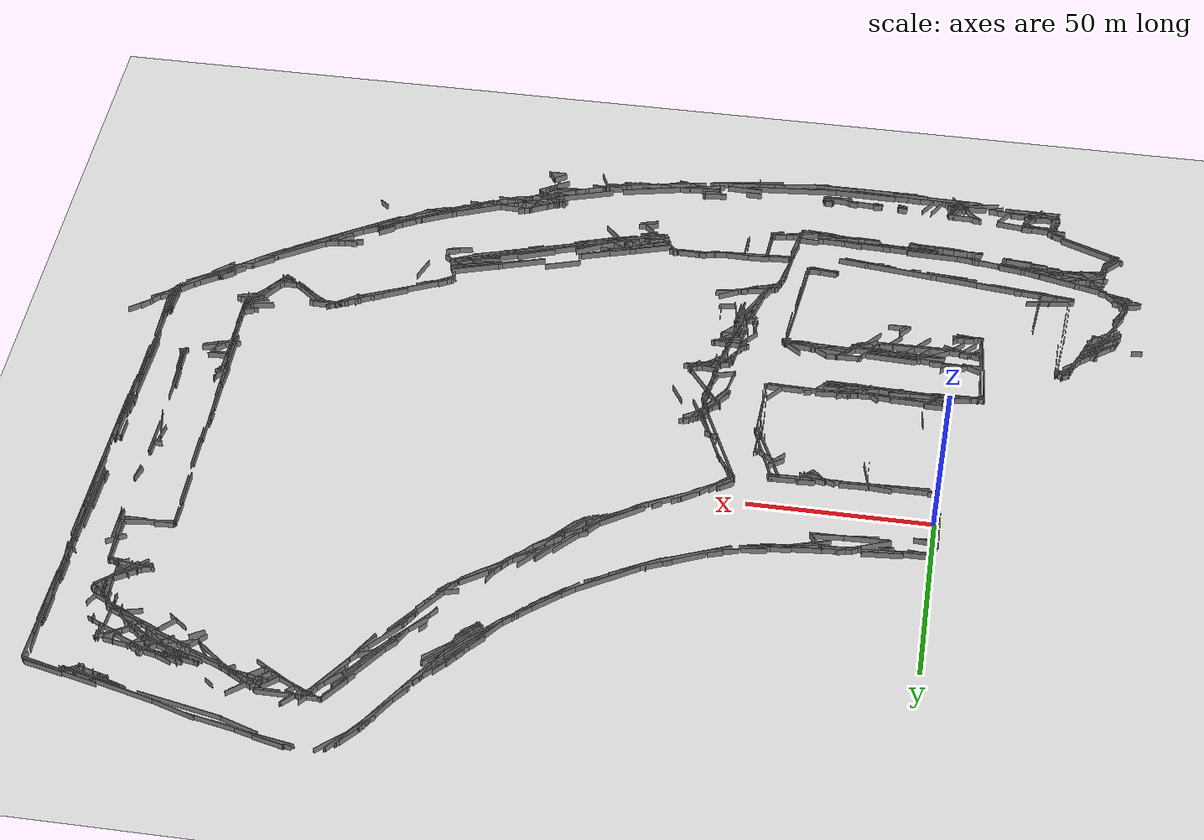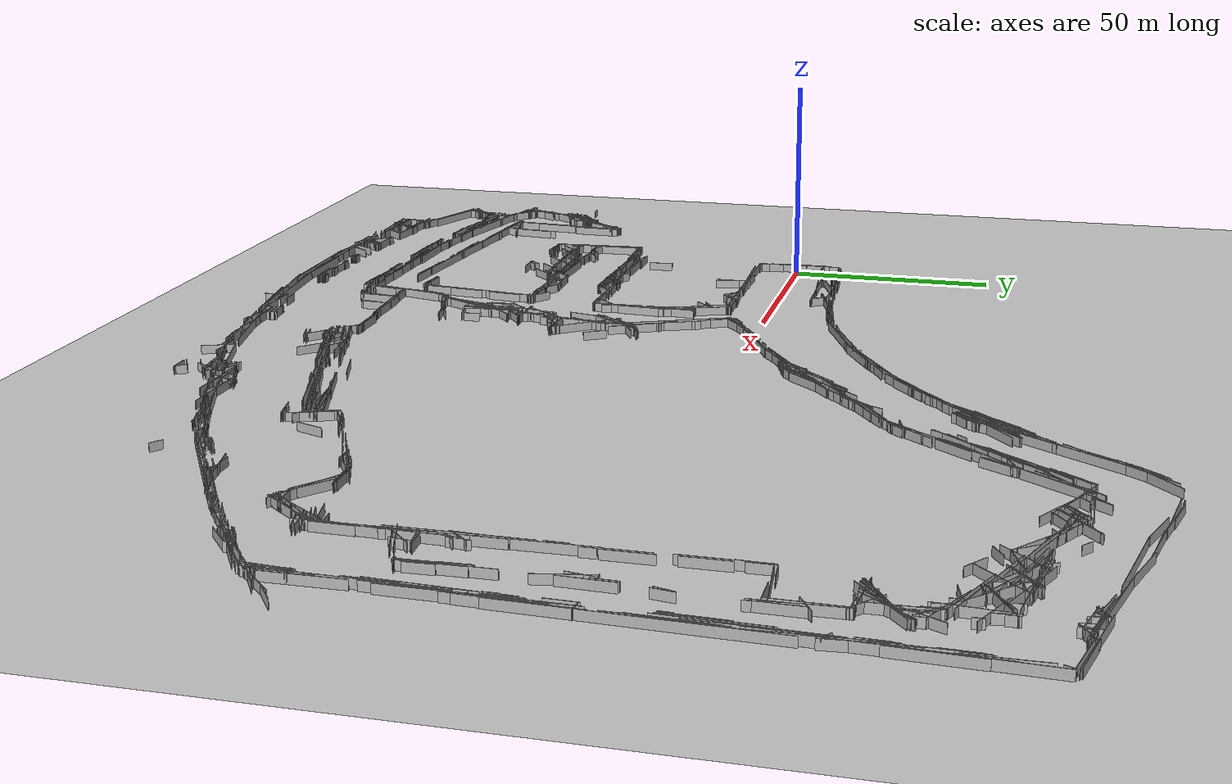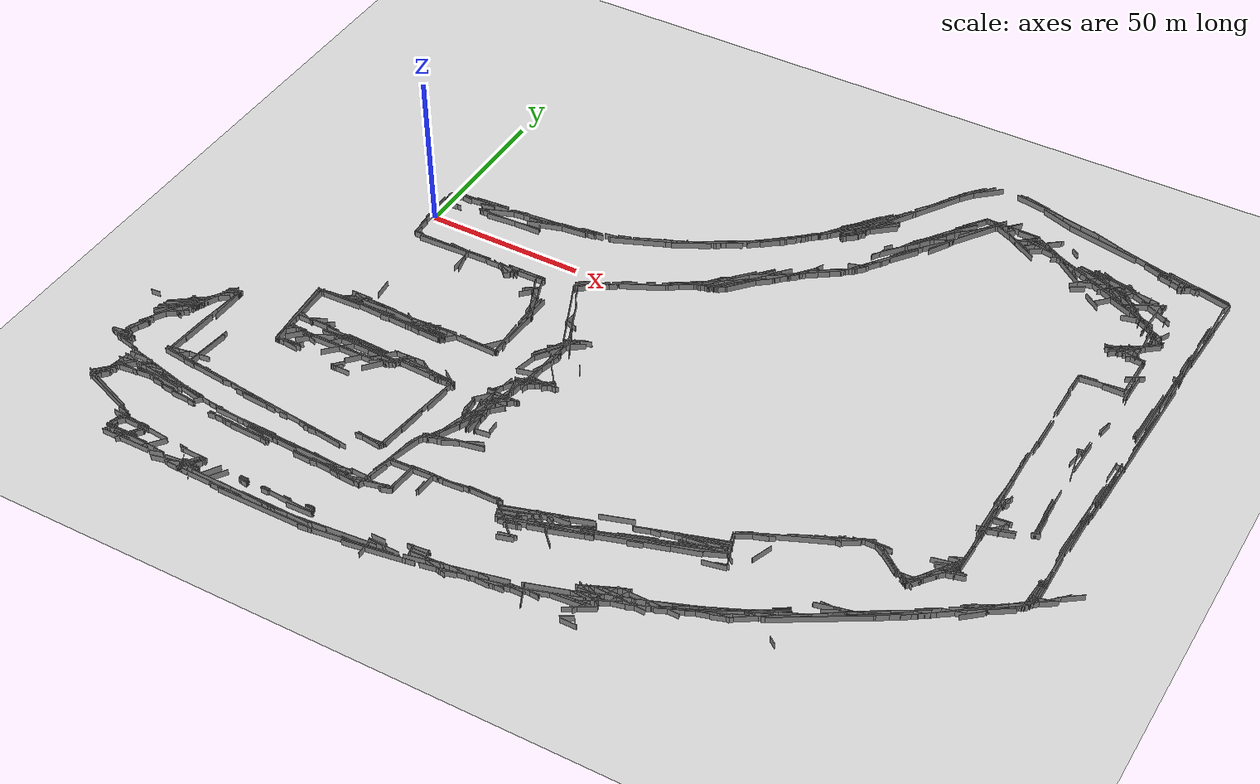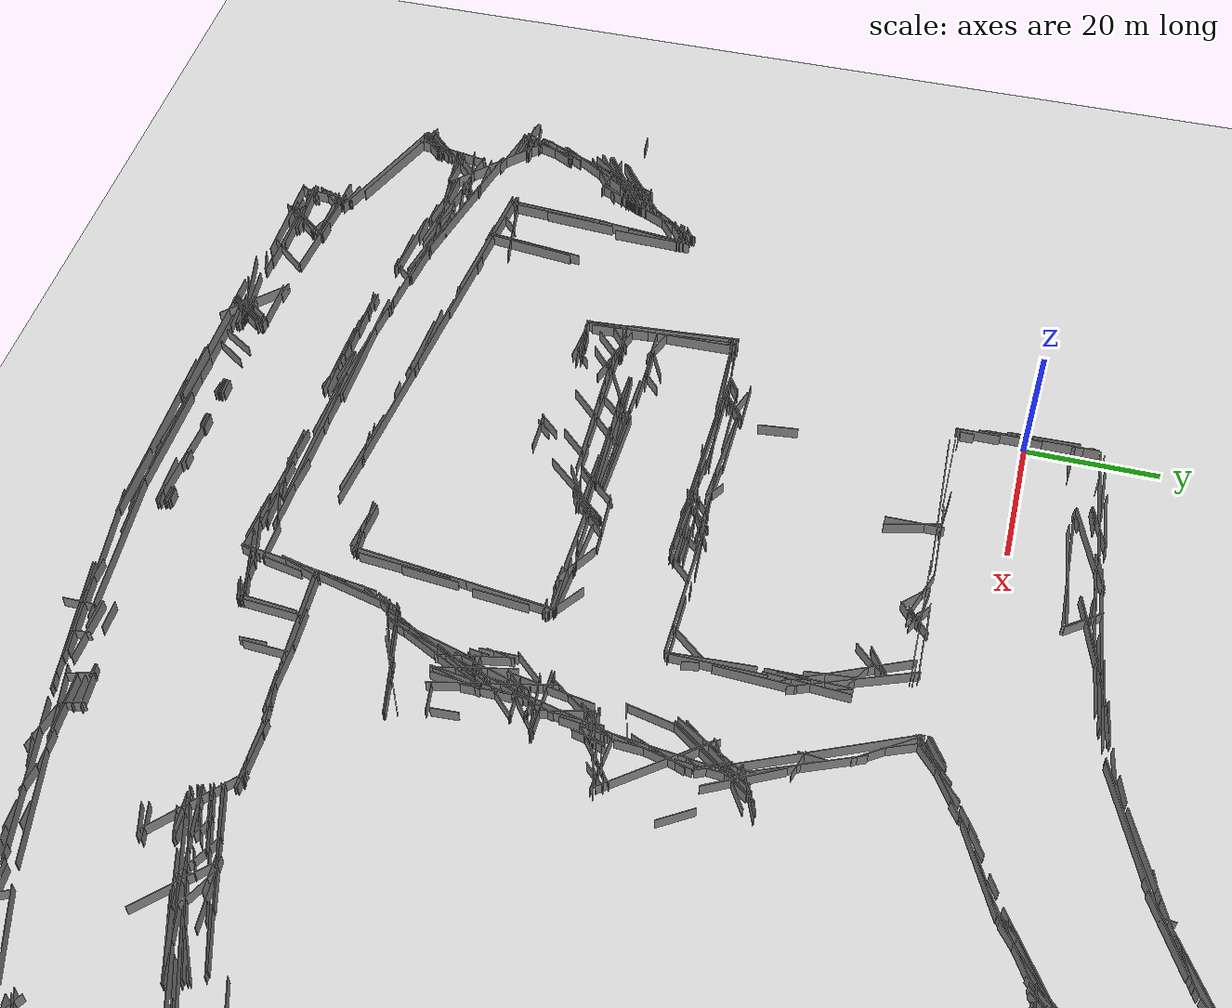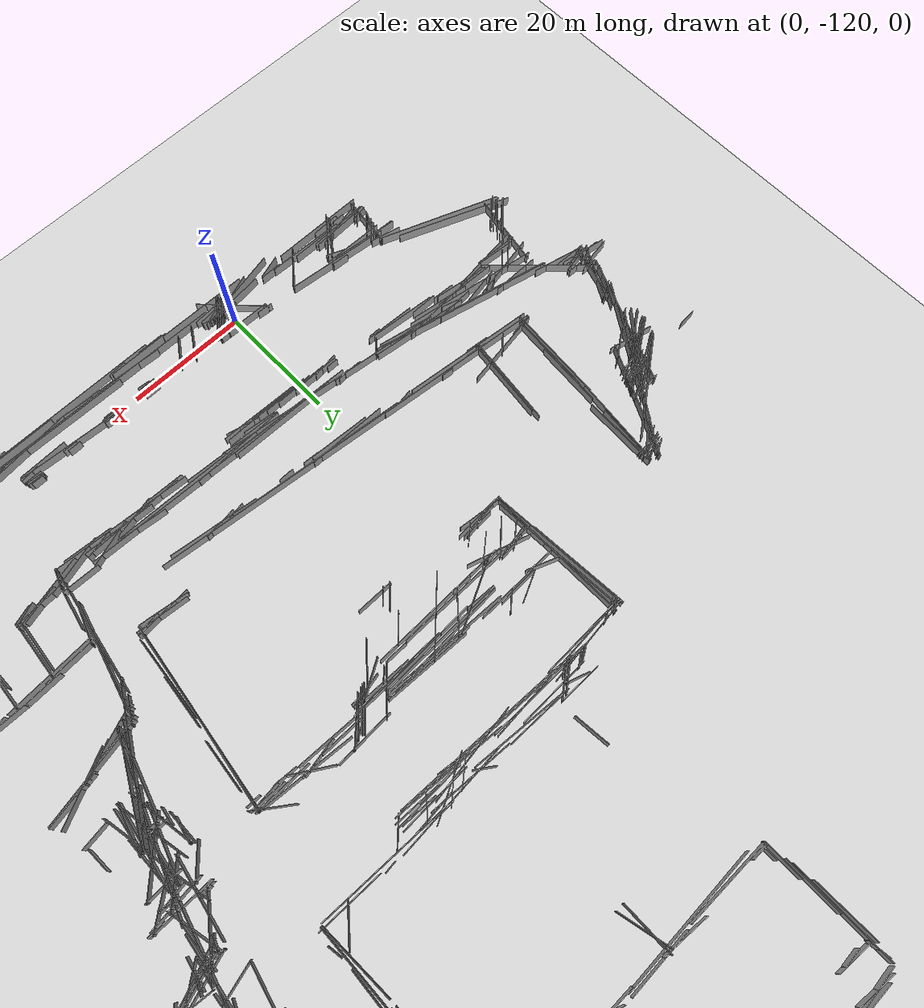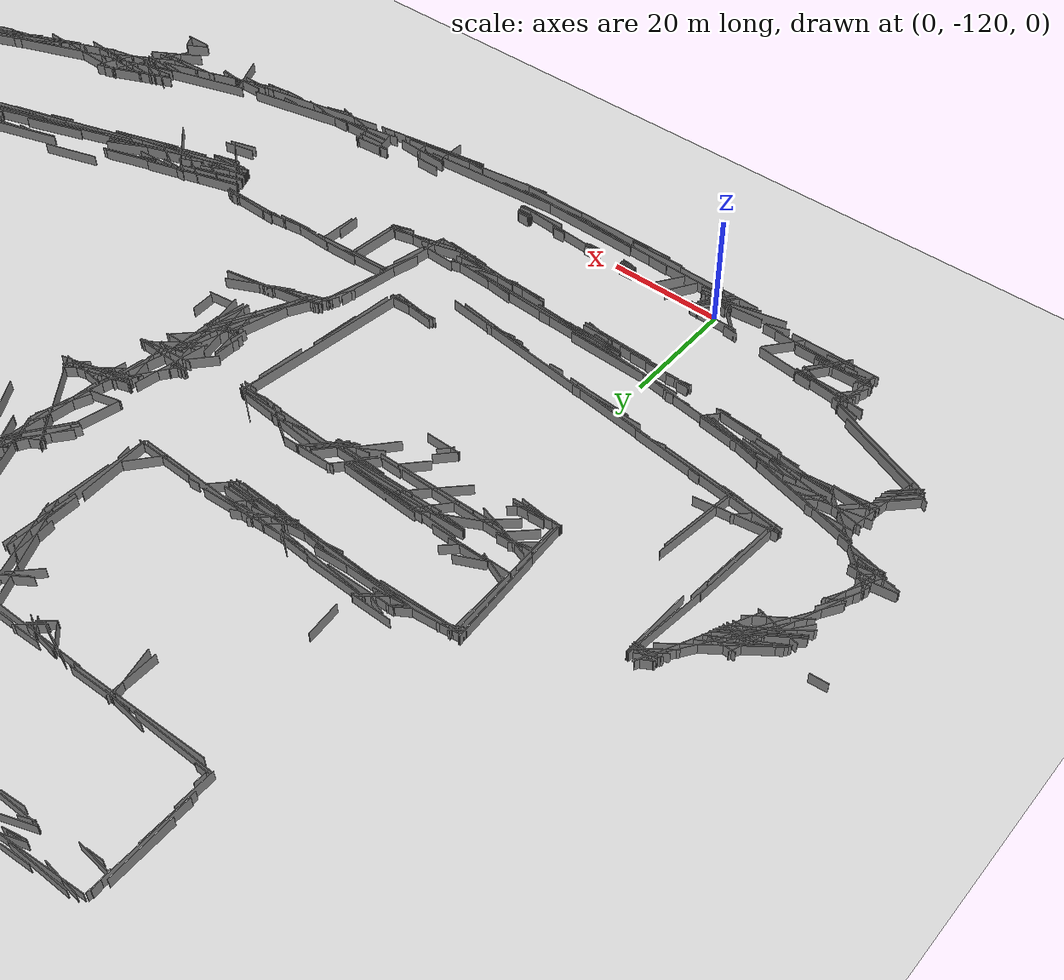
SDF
<?xml version="1.0" ?>
<sdf version="1.6">
  <world name="slam_world">
    <light name="sun" type="directional">
      <pose>0 0 10 0 0 0</pose>
      <diffuse>0.8 0.8 0.8 1</diffuse>
      <direction>-0.5 0.1 -0.9</direction>
    </light>
    <model name="ground_plane">
      <static>true</static>
      <link name="link">
        <collision name="collision">
          <geometry>
            <plane>
              <normal>0 0 1</normal>
              <size>100 100</size>
            </plane>
          </geometry>
        </collision>
        <visual name="visual">
          <geometry>
            <plane>
              <normal>0 0 1</normal>
              <size>100 100</size>
            </plane>
          </geometry>
          <material>
            <ambient>0.8 0.8 0.8 1</ambient>
            <diffuse>0.8 0.8 0.8 1</diffuse>
            <specular>0.8 0.8 0.8 1</specular>
          </material>
        </visual>
      </link>
    </model>
    <model name="wall_0">
      <static>true</static>
      <pose>221.60000000000002 -20.999999999999993 1.0 0 0 1.5360880485696218</pose>
      <link name="link">
        <collision name="collision">
          <geometry>
            <box>
              <size>28.817355881482253 0.1 2.0</size>
            </box>
          </geometry>
        </collision>
        <visual name="visual">
          <geometry>
            <box>
              <size>28.817355881482253 0.1 2.0</size>
            </box>
          </geometry>
          <material>
            <ambient>0.5 0.5 0.5 1</ambient>
            <diffuse>0.7 0.7 0.7 1</diffuse>
          </material>
        </visual>
      </link>
    </model>
    <model name="wall_1">
      <static>true</static>
      <pose>223.50000000000003 19.400000000000006 1.0 0 0 1.5451609182732169</pose>
      <link name="link">
        <collision name="collision">
          <geometry>
            <box>
              <size>15.60512736250495 0.1 2.0</size>
            </box>
          </geometry>
        </collision>
        <visual name="visual">
          <geometry>
            <box>
              <size>15.60512736250495 0.1 2.0</size>
            </box>
          </geometry>
          <material>
            <ambient>0.5 0.5 0.5 1</ambient>
            <diffuse>0.7 0.7 0.7 1</diffuse>
          </material>
        </visual>
      </link>
    </model>
    <model name="wall_2">
      <static>true</static>
      <pose>43.50000000000001 -82.3 1.0 0 0 1.484057988118911</pose>
      <link name="link">
        <collision name="collision">
          <geometry>
            <box>
              <size>13.852075656738219 0.1 2.0</size>
            </box>
          </geometry>
        </collision>
        <visual name="visual">
          <geometry>
            <box>
              <size>13.852075656738219 0.1 2.0</size>
            </box>
          </geometry>
          <material>
            <ambient>0.5 0.5 0.5 1</ambient>
            <diffuse>0.7 0.7 0.7 1</diffuse>
          </material>
        </visual>
      </link>
    </model>
    <model name="wall_3">
      <static>true</static>
      <pose>10.100000000000001 -62.800000000000004 1.0 0 0 0.7853981633974483</pose>
      <link name="link">
        <collision name="collision">
          <geometry>
            <box>
              <size>13.010764773832479 0.1 2.0</size>
            </box>
          </geometry>
        </collision>
        <visual name="visual">
          <geometry>
            <box>
              <size>13.010764773832479 0.1 2.0</size>
            </box>
          </geometry>
          <material>
            <ambient>0.5 0.5 0.5 1</ambient>
            <diffuse>0.7 0.7 0.7 1</diffuse>
          </material>
        </visual>
      </link>
    </model>
    <model name="wall_4">
      <static>true</static>
      <pose>221.8 -5.599999999999987 1.0 0 0 1.5367186152078876</pose>
      <link name="link">
        <collision name="collision">
          <geometry>
            <box>
              <size>17.610224302944022 0.1 2.0</size>
            </box>
          </geometry>
        </collision>
        <visual name="visual">
          <geometry>
            <box>
              <size>17.610224302944022 0.1 2.0</size>
            </box>
          </geometry>
          <material>
            <ambient>0.5 0.5 0.5 1</ambient>
            <diffuse>0.7 0.7 0.7 1</diffuse>
          </material>
        </visual>
      </link>
    </model>
    <model name="wall_5">
      <static>true</static>
      <pose>90.2 15.0 1.0 0 0 0.5746030705476067</pose>
      <link name="link">
        <collision name="collision">
          <geometry>
            <box>
              <size>33.118574848564975 0.1 2.0</size>
            </box>
          </geometry>
        </collision>
        <visual name="visual">
          <geometry>
            <box>
              <size>33.118574848564975 0.1 2.0</size>
            </box>
          </geometry>
          <material>
            <ambient>0.5 0.5 0.5 1</ambient>
            <diffuse>0.7 0.7 0.7 1</diffuse>
          </material>
        </visual>
      </link>
    </model>
    <model name="wall_6">
      <static>true</static>
      <pose>-22.6 -89.8 1.0 0 0 -0.10768987083282093</pose>
      <link name="link">
        <collision name="collision">
          <geometry>
            <box>
              <size>22.32935287911408 0.1 2.0</size>
            </box>
          </geometry>
        </collision>
        <visual name="visual">
          <geometry>
            <box>
              <size>22.32935287911408 0.1 2.0</size>
            </box>
          </geometry>
          <material>
            <ambient>0.5 0.5 0.5 1</ambient>
            <diffuse>0.7 0.7 0.7 1</diffuse>
          </material>
        </visual>
      </link>
    </model>
    <model name="wall_7">
      <static>true</static>
      <pose>121.4 -85.9 1.0 0 0 0.32978251018622395</pose>
      <link name="link">
        <collision name="collision">
          <geometry>
            <box>
              <size>31.497301471713413 0.1 2.0</size>
            </box>
          </geometry>
        </collision>
        <visual name="visual">
          <geometry>
            <box>
              <size>31.497301471713413 0.1 2.0</size>
            </box>
          </geometry>
          <material>
            <ambient>0.5 0.5 0.5 1</ambient>
            <diffuse>0.7 0.7 0.7 1</diffuse>
          </material>
        </visual>
      </link>
    </model>
    <model name="wall_8">
      <static>true</static>
      <pose>198.90000000000003 17.799999999999997 1.0 0 0 1.5707963267948966</pose>
      <link name="link">
        <collision name="collision">
          <geometry>
            <box>
              <size>9.599999999999994 0.1 2.0</size>
            </box>
          </geometry>
        </collision>
        <visual name="visual">
          <geometry>
            <box>
              <size>9.599999999999994 0.1 2.0</size>
            </box>
          </geometry>
          <material>
            <ambient>0.5 0.5 0.5 1</ambient>
            <diffuse>0.7 0.7 0.7 1</diffuse>
          </material>
        </visual>
      </link>
    </model>
    <model name="wall_9">
      <static>true</static>
      <pose>0.6999999999999993 -92.3 1.0 0 0 -0.015150355874771107</pose>
      <link name="link">
        <collision name="collision">
          <geometry>
            <box>
              <size>13.201515064567397 0.1 2.0</size>
            </box>
          </geometry>
        </collision>
        <visual name="visual">
          <geometry>
            <box>
              <size>13.201515064567397 0.1 2.0</size>
            </box>
          </geometry>
          <material>
            <ambient>0.5 0.5 0.5 1</ambient>
            <diffuse>0.7 0.7 0.7 1</diffuse>
          </material>
        </visual>
      </link>
    </model>
    <model name="wall_10">
      <static>true</static>
      <pose>95.2 -90.19999999999999 1.0 0 0 0.3097029445424562</pose>
      <link name="link">
        <collision name="collision">
          <geometry>
            <box>
              <size>26.248809496813376 0.1 2.0</size>
            </box>
          </geometry>
        </collision>
        <visual name="visual">
          <geometry>
            <box>
              <size>26.248809496813376 0.1 2.0</size>
            </box>
          </geometry>
          <material>
            <ambient>0.5 0.5 0.5 1</ambient>
            <diffuse>0.7 0.7 0.7 1</diffuse>
          </material>
        </visual>
      </link>
    </model>
    <model name="wall_11">
      <static>true</static>
      <pose>223.60000000000002 11.800000000000011 1.0 0 0 1.5359267452401077</pose>
      <link name="link">
        <collision name="collision">
          <geometry>
            <box>
              <size>51.6313858035982 0.1 2.0</size>
            </box>
          </geometry>
        </collision>
        <visual name="visual">
          <geometry>
            <box>
              <size>51.6313858035982 0.1 2.0</size>
            </box>
          </geometry>
          <material>
            <ambient>0.5 0.5 0.5 1</ambient>
            <diffuse>0.7 0.7 0.7 1</diffuse>
          </material>
        </visual>
      </link>
    </model>
    <model name="wall_12">
      <static>true</static>
      <pose>225.30000000000004 70.70000000000002 1.0 0 0 1.521453694541926</pose>
      <link name="link">
        <collision name="collision">
          <geometry>
            <box>
              <size>16.21974105835231 0.1 2.0</size>
            </box>
          </geometry>
        </collision>
        <visual name="visual">
          <geometry>
            <box>
              <size>16.21974105835231 0.1 2.0</size>
            </box>
          </geometry>
          <material>
            <ambient>0.5 0.5 0.5 1</ambient>
            <diffuse>0.7 0.7 0.7 1</diffuse>
          </material>
        </visual>
      </link>
    </model>
    <model name="wall_13">
      <static>true</static>
      <pose>84.9 10.900000000000006 1.0 0 0 0.6578886051822088</pose>
      <link name="link">
        <collision name="collision">
          <geometry>
            <box>
              <size>16.68172652934942 0.1 2.0</size>
            </box>
          </geometry>
        </collision>
        <visual name="visual">
          <geometry>
            <box>
              <size>16.68172652934942 0.1 2.0</size>
            </box>
          </geometry>
          <material>
            <ambient>0.5 0.5 0.5 1</ambient>
            <diffuse>0.7 0.7 0.7 1</diffuse>
          </material>
        </visual>
      </link>
    </model>
    <model name="wall_14">
      <static>true</static>
      <pose>198.70000000000005 4.300000000000011 1.0 0 0 1.5707963267948966</pose>
      <link name="link">
        <collision name="collision">
          <geometry>
            <box>
              <size>9.0 0.1 2.0</size>
            </box>
          </geometry>
        </collision>
        <visual name="visual">
          <geometry>
            <box>
              <size>9.0 0.1 2.0</size>
            </box>
          </geometry>
          <material>
            <ambient>0.5 0.5 0.5 1</ambient>
            <diffuse>0.7 0.7 0.7 1</diffuse>
          </material>
        </visual>
      </link>
    </model>
    <model name="wall_15">
      <static>true</static>
      <pose>110.10000000000001 52.60000000000001 1.0 0 0 0.7150916992788243</pose>
      <link name="link">
        <collision name="collision">
          <geometry>
            <box>
              <size>40.26313450291717 0.1 2.0</size>
            </box>
          </geometry>
        </collision>
        <visual name="visual">
          <geometry>
            <box>
              <size>40.26313450291717 0.1 2.0</size>
            </box>
          </geometry>
          <material>
            <ambient>0.5 0.5 0.5 1</ambient>
            <diffuse>0.7 0.7 0.7 1</diffuse>
          </material>
        </visual>
      </link>
    </model>
    <model name="wall_16">
      <static>true</static>
      <pose>224.40000000000003 52.30000000000001 1.0 0 0 1.5325636003592957</pose>
      <link name="link">
        <collision name="collision">
          <geometry>
            <box>
              <size>36.6267661690191 0.1 2.0</size>
            </box>
          </geometry>
        </collision>
        <visual name="visual">
          <geometry>
            <box>
              <size>36.6267661690191 0.1 2.0</size>
            </box>
          </geometry>
          <material>
            <ambient>0.5 0.5 0.5 1</ambient>
            <diffuse>0.7 0.7 0.7 1</diffuse>
          </material>
        </visual>
      </link>
    </model>
    <model name="wall_17">
      <static>true</static>
      <pose>116.0 -87.2 1.0 0 0 0.32762132843565006</pose>
      <link name="link">
        <collision name="collision">
          <geometry>
            <box>
              <size>32.31903463904825 0.1 2.0</size>
            </box>
          </geometry>
        </collision>
        <visual name="visual">
          <geometry>
            <box>
              <size>32.31903463904825 0.1 2.0</size>
            </box>
          </geometry>
          <material>
            <ambient>0.5 0.5 0.5 1</ambient>
            <diffuse>0.7 0.7 0.7 1</diffuse>
          </material>
        </visual>
      </link>
    </model>
    <model name="wall_18">
      <static>true</static>
      <pose>128.0 47.70000000000002 1.0 0 0 0.919996077557915</pose>
      <link name="link">
        <collision name="collision">
          <geometry>
            <box>
              <size>27.400729917285066 0.1 2.0</size>
            </box>
          </geometry>
        </collision>
        <visual name="visual">
          <geometry>
            <box>
              <size>27.400729917285066 0.1 2.0</size>
            </box>
          </geometry>
          <material>
            <ambient>0.5 0.5 0.5 1</ambient>
            <diffuse>0.7 0.7 0.7 1</diffuse>
          </material>
        </visual>
      </link>
    </model>
    <model name="wall_19">
      <static>true</static>
      <pose>31.500000000000007 -123.8 1.0 0 0 -0.01723967119452994</pose>
      <link name="link">
        <collision name="collision">
          <geometry>
            <box>
              <size>23.203448019637083 0.1 2.0</size>
            </box>
          </geometry>
        </collision>
        <visual name="visual">
          <geometry>
            <box>
              <size>23.203448019637083 0.1 2.0</size>
            </box>
          </geometry>
          <material>
            <ambient>0.5 0.5 0.5 1</ambient>
            <diffuse>0.7 0.7 0.7 1</diffuse>
          </material>
        </visual>
      </link>
    </model>
    <model name="wall_20">
      <static>true</static>
      <pose>130.6 -78.8 1.0 0 0 0.3006763914001276</pose>
      <link name="link">
        <collision name="collision">
          <geometry>
            <box>
              <size>27.011849251763564 0.1 2.0</size>
            </box>
          </geometry>
        </collision>
        <visual name="visual">
          <geometry>
            <box>
              <size>27.011849251763564 0.1 2.0</size>
            </box>
          </geometry>
          <material>
            <ambient>0.5 0.5 0.5 1</ambient>
            <diffuse>0.7 0.7 0.7 1</diffuse>
          </material>
        </visual>
      </link>
    </model>
    <model name="wall_21">
      <static>true</static>
      <pose>222.50000000000003 29.10000000000001 1.0 0 0 1.5325983551641331</pose>
      <link name="link">
        <collision name="collision">
          <geometry>
            <box>
              <size>31.42292157008957 0.1 2.0</size>
            </box>
          </geometry>
        </collision>
        <visual name="visual">
          <geometry>
            <box>
              <size>31.42292157008957 0.1 2.0</size>
            </box>
          </geometry>
          <material>
            <ambient>0.5 0.5 0.5 1</ambient>
            <diffuse>0.7 0.7 0.7 1</diffuse>
          </material>
        </visual>
      </link>
    </model>
    <model name="wall_22">
      <static>true</static>
      <pose>43.800000000000004 -75.19999999999999 1.0 0 0 1.4495983856898684</pose>
      <link name="link">
        <collision name="collision">
          <geometry>
            <box>
              <size>31.430558378749815 0.1 2.0</size>
            </box>
          </geometry>
        </collision>
        <visual name="visual">
          <geometry>
            <box>
              <size>31.430558378749815 0.1 2.0</size>
            </box>
          </geometry>
          <material>
            <ambient>0.5 0.5 0.5 1</ambient>
            <diffuse>0.7 0.7 0.7 1</diffuse>
          </material>
        </visual>
      </link>
    </model>
    <model name="wall_23">
      <static>true</static>
      <pose>179.3 -83.89999999999999 1.0 0 0 0.5395640684860857</pose>
      <link name="link">
        <collision name="collision">
          <geometry>
            <box>
              <size>40.096383876853515 0.1 2.0</size>
            </box>
          </geometry>
        </collision>
        <visual name="visual">
          <geometry>
            <box>
              <size>40.096383876853515 0.1 2.0</size>
            </box>
          </geometry>
          <material>
            <ambient>0.5 0.5 0.5 1</ambient>
            <diffuse>0.7 0.7 0.7 1</diffuse>
          </material>
        </visual>
      </link>
    </model>
    <model name="wall_24">
      <static>true</static>
      <pose>223.40000000000003 47.60000000000001 1.0 0 0 1.555172598174419</pose>
      <link name="link">
        <collision name="collision">
          <geometry>
            <box>
              <size>38.40468721393263 0.1 2.0</size>
            </box>
          </geometry>
        </collision>
        <visual name="visual">
          <geometry>
            <box>
              <size>38.40468721393263 0.1 2.0</size>
            </box>
          </geometry>
          <material>
            <ambient>0.5 0.5 0.5 1</ambient>
            <diffuse>0.7 0.7 0.7 1</diffuse>
          </material>
        </visual>
      </link>
    </model>
    <model name="wall_25">
      <static>true</static>
      <pose>198.90000000000003 -20.299999999999997 1.0 0 0 1.5707963267948966</pose>
      <link name="link">
        <collision name="collision">
          <geometry>
            <box>
              <size>7.0 0.1 2.0</size>
            </box>
          </geometry>
        </collision>
        <visual name="visual">
          <geometry>
            <box>
              <size>7.0 0.1 2.0</size>
            </box>
          </geometry>
          <material>
            <ambient>0.5 0.5 0.5 1</ambient>
            <diffuse>0.7 0.7 0.7 1</diffuse>
          </material>
        </visual>
      </link>
    </model>
    <model name="wall_26">
      <static>true</static>
      <pose>9.300000000000004 -42.49999999999999 1.0 0 0 -0.017855245139552764</pose>
      <link name="link">
        <collision name="collision">
          <geometry>
            <box>
              <size>11.20178557195236 0.1 2.0</size>
            </box>
          </geometry>
        </collision>
        <visual name="visual">
          <geometry>
            <box>
              <size>11.20178557195236 0.1 2.0</size>
            </box>
          </geometry>
          <material>
            <ambient>0.5 0.5 0.5 1</ambient>
            <diffuse>0.7 0.7 0.7 1</diffuse>
          </material>
        </visual>
      </link>
    </model>
    <model name="wall_27">
      <static>true</static>
      <pose>34.1 -44.8 1.0 0 0 0.7853981633974463</pose>
      <link name="link">
        <collision name="collision">
          <geometry>
            <box>
              <size>5.091168824543144 0.1 2.0</size>
            </box>
          </geometry>
        </collision>
        <visual name="visual">
          <geometry>
            <box>
              <size>5.091168824543144 0.1 2.0</size>
            </box>
          </geometry>
          <material>
            <ambient>0.5 0.5 0.5 1</ambient>
            <diffuse>0.7 0.7 0.7 1</diffuse>
          </material>
        </visual>
      </link>
    </model>
    <model name="wall_28">
      <static>true</static>
      <pose>24.700000000000003 -94.9 1.0 0 0 -0.12102721980920472</pose>
      <link name="link">
        <collision name="collision">
          <geometry>
            <box>
              <size>14.909057649630318 0.1 2.0</size>
            </box>
          </geometry>
        </collision>
        <visual name="visual">
          <geometry>
            <box>
              <size>14.909057649630318 0.1 2.0</size>
            </box>
          </geometry>
          <material>
            <ambient>0.5 0.5 0.5 1</ambient>
            <diffuse>0.7 0.7 0.7 1</diffuse>
          </material>
        </visual>
      </link>
    </model>
    <model name="wall_29">
      <static>true</static>
      <pose>182.40000000000003 87.50000000000001 1.0 0 0 -0.19739555984988053</pose>
      <link name="link">
        <collision name="collision">
          <geometry>
            <box>
              <size>23.45548976252681 0.1 2.0</size>
            </box>
          </geometry>
        </collision>
        <visual name="visual">
          <geometry>
            <box>
              <size>23.45548976252681 0.1 2.0</size>
            </box>
          </geometry>
          <material>
            <ambient>0.5 0.5 0.5 1</ambient>
            <diffuse>0.7 0.7 0.7 1</diffuse>
          </material>
        </visual>
      </link>
    </model>
    <model name="wall_30">
      <static>true</static>
      <pose>61.00000000000001 -61.1 1.0 0 0 0.032246882435254365</pose>
      <link name="link">
        <collision name="collision">
          <geometry>
            <box>
              <size>6.203224967708332 0.1 2.0</size>
            </box>
          </geometry>
        </collision>
        <visual name="visual">
          <geometry>
            <box>
              <size>6.203224967708332 0.1 2.0</size>
            </box>
          </geometry>
          <material>
            <ambient>0.5 0.5 0.5 1</ambient>
            <diffuse>0.7 0.7 0.7 1</diffuse>
          </material>
        </visual>
      </link>
    </model>
    <model name="wall_31">
      <static>true</static>
      <pose>72.3 -122.1 1.0 0 0 0.21109333322274862</pose>
      <link name="link">
        <collision name="collision">
          <geometry>
            <box>
              <size>2.8635642126552834 0.1 2.0</size>
            </box>
          </geometry>
        </collision>
        <visual name="visual">
          <geometry>
            <box>
              <size>2.8635642126552834 0.1 2.0</size>
            </box>
          </geometry>
          <material>
            <ambient>0.5 0.5 0.5 1</ambient>
            <diffuse>0.7 0.7 0.7 1</diffuse>
          </material>
        </visual>
      </link>
    </model>
    <model name="wall_32">
      <static>true</static>
      <pose>198.10000000000002 -26.199999999999996 1.0 0 0 1.5707963267948966</pose>
      <link name="link">
        <collision name="collision">
          <geometry>
            <box>
              <size>28.39999999999999 0.1 2.0</size>
            </box>
          </geometry>
        </collision>
        <visual name="visual">
          <geometry>
            <box>
              <size>28.39999999999999 0.1 2.0</size>
            </box>
          </geometry>
          <material>
            <ambient>0.5 0.5 0.5 1</ambient>
            <diffuse>0.7 0.7 0.7 1</diffuse>
          </material>
        </visual>
      </link>
    </model>
    <model name="wall_33">
      <static>true</static>
      <pose>21.200000000000003 -102.1 1.0 0 0 -0.03551805166373941</pose>
      <link name="link">
        <collision name="collision">
          <geometry>
            <box>
              <size>39.42486525024531 0.1 2.0</size>
            </box>
          </geometry>
        </collision>
        <visual name="visual">
          <geometry>
            <box>
              <size>39.42486525024531 0.1 2.0</size>
            </box>
          </geometry>
          <material>
            <ambient>0.5 0.5 0.5 1</ambient>
            <diffuse>0.7 0.7 0.7 1</diffuse>
          </material>
        </visual>
      </link>
    </model>
    <model name="wall_34">
      <static>true</static>
      <pose>135.3 84.9 1.0 0 0 0.9077781769702474</pose>
      <link name="link">
        <collision name="collision">
          <geometry>
            <box>
              <size>26.64507459175147 0.1 2.0</size>
            </box>
          </geometry>
        </collision>
        <visual name="visual">
          <geometry>
            <box>
              <size>26.64507459175147 0.1 2.0</size>
            </box>
          </geometry>
          <material>
            <ambient>0.5 0.5 0.5 1</ambient>
            <diffuse>0.7 0.7 0.7 1</diffuse>
          </material>
        </visual>
      </link>
    </model>
    <model name="wall_35">
      <static>true</static>
      <pose>45.7 -123.19999999999999 1.0 0 0 0.08413824053117089</pose>
      <link name="link">
        <collision name="collision">
          <geometry>
            <box>
              <size>33.317863076734064 0.1 2.0</size>
            </box>
          </geometry>
        </collision>
        <visual name="visual">
          <geometry>
            <box>
              <size>33.317863076734064 0.1 2.0</size>
            </box>
          </geometry>
          <material>
            <ambient>0.5 0.5 0.5 1</ambient>
            <diffuse>0.7 0.7 0.7 1</diffuse>
          </material>
        </visual>
      </link>
    </model>
    <model name="wall_36">
      <static>true</static>
      <pose>-46.5 -91.1 1.0 0 0 -0.03569911267932193</pose>
      <link name="link">
        <collision name="collision">
          <geometry>
            <box>
              <size>5.603570290448761 0.1 2.0</size>
            </box>
          </geometry>
        </collision>
        <visual name="visual">
          <geometry>
            <box>
              <size>5.603570290448761 0.1 2.0</size>
            </box>
          </geometry>
          <material>
            <ambient>0.5 0.5 0.5 1</ambient>
            <diffuse>0.7 0.7 0.7 1</diffuse>
          </material>
        </visual>
      </link>
    </model>
    <model name="wall_37">
      <static>true</static>
      <pose>223.10000000000002 14.600000000000009 1.0 0 0 1.5485777614681788</pose>
      <link name="link">
        <collision name="collision">
          <geometry>
            <box>
              <size>18.004443895883067 0.1 2.0</size>
            </box>
          </geometry>
        </collision>
        <visual name="visual">
          <geometry>
            <box>
              <size>18.004443895883067 0.1 2.0</size>
            </box>
          </geometry>
          <material>
            <ambient>0.5 0.5 0.5 1</ambient>
            <diffuse>0.7 0.7 0.7 1</diffuse>
          </material>
        </visual>
      </link>
    </model>
    <model name="wall_38">
      <static>true</static>
      <pose>144.4 70.50000000000001 1.0 0 0 0.868539395285891</pose>
      <link name="link">
        <collision name="collision">
          <geometry>
            <box>
              <size>3.4058772731852685 0.1 2.0</size>
            </box>
          </geometry>
        </collision>
        <visual name="visual">
          <geometry>
            <box>
              <size>3.4058772731852685 0.1 2.0</size>
            </box>
          </geometry>
          <material>
            <ambient>0.5 0.5 0.5 1</ambient>
            <diffuse>0.7 0.7 0.7 1</diffuse>
          </material>
        </visual>
      </link>
    </model>
    <model name="wall_39">
      <static>true</static>
      <pose>1.8000000000000043 -92.89999999999999 1.0 0 0 -0.05875582271572212</pose>
      <link name="link">
        <collision name="collision">
          <geometry>
            <box>
              <size>10.217631819555844 0.1 2.0</size>
            </box>
          </geometry>
        </collision>
        <visual name="visual">
          <geometry>
            <box>
              <size>10.217631819555844 0.1 2.0</size>
            </box>
          </geometry>
          <material>
            <ambient>0.5 0.5 0.5 1</ambient>
            <diffuse>0.7 0.7 0.7 1</diffuse>
          </material>
        </visual>
      </link>
    </model>
    <model name="wall_40">
      <static>true</static>
      <pose>135.2 -81.8 1.0 0 0 0.3249051180651195</pose>
      <link name="link">
        <collision name="collision">
          <geometry>
            <box>
              <size>20.048940121612404 0.1 2.0</size>
            </box>
          </geometry>
        </collision>
        <visual name="visual">
          <geometry>
            <box>
              <size>20.048940121612404 0.1 2.0</size>
            </box>
          </geometry>
          <material>
            <ambient>0.5 0.5 0.5 1</ambient>
            <diffuse>0.7 0.7 0.7 1</diffuse>
          </material>
        </visual>
      </link>
    </model>
    <model name="wall_41">
      <static>true</static>
      <pose>3.3000000000000007 -63.0 1.0 0 0 0.0</pose>
      <link name="link">
        <collision name="collision">
          <geometry>
            <box>
              <size>24.800000000000004 0.1 2.0</size>
            </box>
          </geometry>
        </collision>
        <visual name="visual">
          <geometry>
            <box>
              <size>24.800000000000004 0.1 2.0</size>
            </box>
          </geometry>
          <material>
            <ambient>0.5 0.5 0.5 1</ambient>
            <diffuse>0.7 0.7 0.7 1</diffuse>
          </material>
        </visual>
      </link>
    </model>
    <model name="wall_42">
      <static>true</static>
      <pose>56.1 -5.099999999999994 1.0 0 0 0.5984188934785382</pose>
      <link name="link">
        <collision name="collision">
          <geometry>
            <box>
              <size>5.325410782277732 0.1 2.0</size>
            </box>
          </geometry>
        </collision>
        <visual name="visual">
          <geometry>
            <box>
              <size>5.325410782277732 0.1 2.0</size>
            </box>
          </geometry>
          <material>
            <ambient>0.5 0.5 0.5 1</ambient>
            <diffuse>0.7 0.7 0.7 1</diffuse>
          </material>
        </visual>
      </link>
    </model>
    <model name="wall_43">
      <static>true</static>
      <pose>-19.8 -89.5 1.0 0 0 -0.10749767402565427</pose>
      <link name="link">
        <collision name="collision">
          <geometry>
            <box>
              <size>27.96140196771257 0.1 2.0</size>
            </box>
          </geometry>
        </collision>
        <visual name="visual">
          <geometry>
            <box>
              <size>27.96140196771257 0.1 2.0</size>
            </box>
          </geometry>
          <material>
            <ambient>0.5 0.5 0.5 1</ambient>
            <diffuse>0.7 0.7 0.7 1</diffuse>
          </material>
        </visual>
      </link>
    </model>
    <model name="wall_44">
      <static>true</static>
      <pose>117.50000000000001 -110.6 1.0 0 0 -0.08314123188843928</pose>
      <link name="link">
        <collision name="collision">
          <geometry>
            <box>
              <size>4.816637831516929 0.1 2.0</size>
            </box>
          </geometry>
        </collision>
        <visual name="visual">
          <geometry>
            <box>
              <size>4.816637831516929 0.1 2.0</size>
            </box>
          </geometry>
          <material>
            <ambient>0.5 0.5 0.5 1</ambient>
            <diffuse>0.7 0.7 0.7 1</diffuse>
          </material>
        </visual>
      </link>
    </model>
    <model name="wall_45">
      <static>true</static>
      <pose>41.400000000000006 -9.29999999999999 1.0 0 0 0.027020449187265153</pose>
      <link name="link">
        <collision name="collision">
          <geometry>
            <box>
              <size>7.402702209328704 0.1 2.0</size>
            </box>
          </geometry>
        </collision>
        <visual name="visual">
          <geometry>
            <box>
              <size>7.402702209328704 0.1 2.0</size>
            </box>
          </geometry>
          <material>
            <ambient>0.5 0.5 0.5 1</ambient>
            <diffuse>0.7 0.7 0.7 1</diffuse>
          </material>
        </visual>
      </link>
    </model>
    <model name="wall_46">
      <static>true</static>
      <pose>188.9 -76.5 1.0 0 0 0.5389764998291451</pose>
      <link name="link">
        <collision name="collision">
          <geometry>
            <box>
              <size>23.76972864800945 0.1 2.0</size>
            </box>
          </geometry>
        </collision>
        <visual name="visual">
          <geometry>
            <box>
              <size>23.76972864800945 0.1 2.0</size>
            </box>
          </geometry>
          <material>
            <ambient>0.5 0.5 0.5 1</ambient>
            <diffuse>0.7 0.7 0.7 1</diffuse>
          </material>
        </visual>
      </link>
    </model>
    <model name="wall_47">
      <static>true</static>
      <pose>0.8999999999999986 -121.6 1.0 0 0 0.9272952180016119</pose>
      <link name="link">
        <collision name="collision">
          <geometry>
            <box>
              <size>7.999999999999992 0.1 2.0</size>
            </box>
          </geometry>
        </collision>
        <visual name="visual">
          <geometry>
            <box>
              <size>7.999999999999992 0.1 2.0</size>
            </box>
          </geometry>
          <material>
            <ambient>0.5 0.5 0.5 1</ambient>
            <diffuse>0.7 0.7 0.7 1</diffuse>
          </material>
        </visual>
      </link>
    </model>
    <model name="wall_48">
      <static>true</static>
      <pose>7.5000000000000036 -60.9 1.0 0 0 0.8441539861131697</pose>
      <link name="link">
        <collision name="collision">
          <geometry>
            <box>
              <size>7.224956747275374 0.1 2.0</size>
            </box>
          </geometry>
        </collision>
        <visual name="visual">
          <geometry>
            <box>
              <size>7.224956747275374 0.1 2.0</size>
            </box>
          </geometry>
          <material>
            <ambient>0.5 0.5 0.5 1</ambient>
            <diffuse>0.7 0.7 0.7 1</diffuse>
          </material>
        </visual>
      </link>
    </model>
    <model name="wall_49">
      <static>true</static>
      <pose>115.20000000000002 56.90000000000002 1.0 0 0 0.7853981633974483</pose>
      <link name="link">
        <collision name="collision">
          <geometry>
            <box>
              <size>23.47594513539337 0.1 2.0</size>
            </box>
          </geometry>
        </collision>
        <visual name="visual">
          <geometry>
            <box>
              <size>23.47594513539337 0.1 2.0</size>
            </box>
          </geometry>
          <material>
            <ambient>0.5 0.5 0.5 1</ambient>
            <diffuse>0.7 0.7 0.7 1</diffuse>
          </material>
        </visual>
      </link>
    </model>
    <model name="wall_50">
      <static>true</static>
      <pose>102.3 -92.8 1.0 0 0 0.29684467337640313</pose>
      <link name="link">
        <collision name="collision">
          <geometry>
            <box>
              <size>35.55502777386062 0.1 2.0</size>
            </box>
          </geometry>
        </collision>
        <visual name="visual">
          <geometry>
            <box>
              <size>35.55502777386062 0.1 2.0</size>
            </box>
          </geometry>
          <material>
            <ambient>0.5 0.5 0.5 1</ambient>
            <diffuse>0.7 0.7 0.7 1</diffuse>
          </material>
        </visual>
      </link>
    </model>
    <model name="wall_51">
      <static>true</static>
      <pose>110.9 30.60000000000001 1.0 0 0 0.6162969373960707</pose>
      <link name="link">
        <collision name="collision">
          <geometry>
            <box>
              <size>23.528705871764398 0.1 2.0</size>
            </box>
          </geometry>
        </collision>
        <visual name="visual">
          <geometry>
            <box>
              <size>23.528705871764398 0.1 2.0</size>
            </box>
          </geometry>
          <material>
            <ambient>0.5 0.5 0.5 1</ambient>
            <diffuse>0.7 0.7 0.7 1</diffuse>
          </material>
        </visual>
      </link>
    </model>
    <model name="wall_52">
      <static>true</static>
      <pose>59.800000000000004 -66.8 1.0 0 0 1.4104208828189457</pose>
      <link name="link">
        <collision name="collision">
          <geometry>
            <box>
              <size>13.776792079435612 0.1 2.0</size>
            </box>
          </geometry>
        </collision>
        <visual name="visual">
          <geometry>
            <box>
              <size>13.776792079435612 0.1 2.0</size>
            </box>
          </geometry>
          <material>
            <ambient>0.5 0.5 0.5 1</ambient>
            <diffuse>0.7 0.7 0.7 1</diffuse>
          </material>
        </visual>
      </link>
    </model>
    <model name="wall_53">
      <static>true</static>
      <pose>198.3 17.10000000000001 1.0 0 0 1.5707963267948966</pose>
      <link name="link">
        <collision name="collision">
          <geometry>
            <box>
              <size>10.200000000000017 0.1 2.0</size>
            </box>
          </geometry>
        </collision>
        <visual name="visual">
          <geometry>
            <box>
              <size>10.200000000000017 0.1 2.0</size>
            </box>
          </geometry>
          <material>
            <ambient>0.5 0.5 0.5 1</ambient>
            <diffuse>0.7 0.7 0.7 1</diffuse>
          </material>
        </visual>
      </link>
    </model>
    <model name="wall_54">
      <static>true</static>
      <pose>220.60000000000002 -39.099999999999994 1.0 0 0 1.5536551486562873</pose>
      <link name="link">
        <collision name="collision">
          <geometry>
            <box>
              <size>35.005142479355804 0.1 2.0</size>
            </box>
          </geometry>
        </collision>
        <visual name="visual">
          <geometry>
            <box>
              <size>35.005142479355804 0.1 2.0</size>
            </box>
          </geometry>
          <material>
            <ambient>0.5 0.5 0.5 1</ambient>
            <diffuse>0.7 0.7 0.7 1</diffuse>
          </material>
        </visual>
      </link>
    </model>
    <model name="wall_55">
      <static>true</static>
      <pose>26.200000000000003 -104.69999999999999 1.0 0 0 -0.03029375991877556</pose>
      <link name="link">
        <collision name="collision">
          <geometry>
            <box>
              <size>6.603029607687665 0.1 2.0</size>
            </box>
          </geometry>
        </collision>
        <visual name="visual">
          <geometry>
            <box>
              <size>6.603029607687665 0.1 2.0</size>
            </box>
          </geometry>
          <material>
            <ambient>0.5 0.5 0.5 1</ambient>
            <diffuse>0.7 0.7 0.7 1</diffuse>
          </material>
        </visual>
      </link>
    </model>
    <model name="wall_56">
      <static>true</static>
      <pose>83.00000000000001 10.000000000000014 1.0 0 0 0.5565993180102222</pose>
      <link name="link">
        <collision name="collision">
          <geometry>
            <box>
              <size>10.599999999999996 0.1 2.0</size>
            </box>
          </geometry>
        </collision>
        <visual name="visual">
          <geometry>
            <box>
              <size>10.599999999999996 0.1 2.0</size>
            </box>
          </geometry>
          <material>
            <ambient>0.5 0.5 0.5 1</ambient>
            <diffuse>0.7 0.7 0.7 1</diffuse>
          </material>
        </visual>
      </link>
    </model>
    <model name="wall_57">
      <static>true</static>
      <pose>85.0 -118.1 1.0 0 0 0.2078390443854342</pose>
      <link name="link">
        <collision name="collision">
          <geometry>
            <box>
              <size>30.046630426721737 0.1 2.0</size>
            </box>
          </geometry>
        </collision>
        <visual name="visual">
          <geometry>
            <box>
              <size>30.046630426721737 0.1 2.0</size>
            </box>
          </geometry>
          <material>
            <ambient>0.5 0.5 0.5 1</ambient>
            <diffuse>0.7 0.7 0.7 1</diffuse>
          </material>
        </visual>
      </link>
    </model>
    <model name="wall_58">
      <static>true</static>
      <pose>221.20000000000002 -10.299999999999997 1.0 0 0 1.5437758776076334</pose>
      <link name="link">
        <collision name="collision">
          <geometry>
            <box>
              <size>7.402702209328704 0.1 2.0</size>
            </box>
          </geometry>
        </collision>
        <visual name="visual">
          <geometry>
            <box>
              <size>7.402702209328704 0.1 2.0</size>
            </box>
          </geometry>
          <material>
            <ambient>0.5 0.5 0.5 1</ambient>
            <diffuse>0.7 0.7 0.7 1</diffuse>
          </material>
        </visual>
      </link>
    </model>
    <model name="wall_59">
      <static>true</static>
      <pose>15.900000000000006 -58.3 1.0 0 0 -0.04164257909858801</pose>
      <link name="link">
        <collision name="collision">
          <geometry>
            <box>
              <size>14.412494579357181 0.1 2.0</size>
            </box>
          </geometry>
        </collision>
        <visual name="visual">
          <geometry>
            <box>
              <size>14.412494579357181 0.1 2.0</size>
            </box>
          </geometry>
          <material>
            <ambient>0.5 0.5 0.5 1</ambient>
            <diffuse>0.7 0.7 0.7 1</diffuse>
          </material>
        </visual>
      </link>
    </model>
    <model name="wall_60">
      <static>true</static>
      <pose>8.7 -63.599999999999994 1.0 0 0 0.017239671194529942</pose>
      <link name="link">
        <collision name="collision">
          <geometry>
            <box>
              <size>23.203448019637076 0.1 2.0</size>
            </box>
          </geometry>
        </collision>
        <visual name="visual">
          <geometry>
            <box>
              <size>23.203448019637076 0.1 2.0</size>
            </box>
          </geometry>
          <material>
            <ambient>0.5 0.5 0.5 1</ambient>
            <diffuse>0.7 0.7 0.7 1</diffuse>
          </material>
        </visual>
      </link>
    </model>
    <model name="wall_61">
      <static>true</static>
      <pose>200.90000000000003 84.30000000000001 1.0 0 0 -0.24497866312686414</pose>
      <link name="link">
        <collision name="collision">
          <geometry>
            <box>
              <size>28.861739379323623 0.1 2.0</size>
            </box>
          </geometry>
        </collision>
        <visual name="visual">
          <geometry>
            <box>
              <size>28.861739379323623 0.1 2.0</size>
            </box>
          </geometry>
          <material>
            <ambient>0.5 0.5 0.5 1</ambient>
            <diffuse>0.7 0.7 0.7 1</diffuse>
          </material>
        </visual>
      </link>
    </model>
    <model name="wall_62">
      <static>true</static>
      <pose>112.00000000000001 55.20000000000002 1.0 0 0 0.8400699948165983</pose>
      <link name="link">
        <collision name="collision">
          <geometry>
            <box>
              <size>28.468227904103895 0.1 2.0</size>
            </box>
          </geometry>
        </collision>
        <visual name="visual">
          <geometry>
            <box>
              <size>28.468227904103895 0.1 2.0</size>
            </box>
          </geometry>
          <material>
            <ambient>0.5 0.5 0.5 1</ambient>
            <diffuse>0.7 0.7 0.7 1</diffuse>
          </material>
        </visual>
      </link>
    </model>
    <model name="wall_63">
      <static>true</static>
      <pose>-12.599999999999998 -120.4 1.0 0 0 0.8831250707561676</pose>
      <link name="link">
        <collision name="collision">
          <geometry>
            <box>
              <size>7.247068372797383 0.1 2.0</size>
            </box>
          </geometry>
        </collision>
        <visual name="visual">
          <geometry>
            <box>
              <size>7.247068372797383 0.1 2.0</size>
            </box>
          </geometry>
          <material>
            <ambient>0.5 0.5 0.5 1</ambient>
            <diffuse>0.7 0.7 0.7 1</diffuse>
          </material>
        </visual>
      </link>
    </model>
    <model name="wall_64">
      <static>true</static>
      <pose>12.600000000000001 13.0 1.0 0 0 0.07259945373049556</pose>
      <link name="link">
        <collision name="collision">
          <geometry>
            <box>
              <size>11.029052543169804 0.1 2.0</size>
            </box>
          </geometry>
        </collision>
        <visual name="visual">
          <geometry>
            <box>
              <size>11.029052543169804 0.1 2.0</size>
            </box>
          </geometry>
          <material>
            <ambient>0.5 0.5 0.5 1</ambient>
            <diffuse>0.7 0.7 0.7 1</diffuse>
          </material>
        </visual>
      </link>
    </model>
    <model name="wall_65">
      <static>true</static>
      <pose>126.20000000000002 43.90000000000002 1.0 0 0 0.903888122555585</pose>
      <link name="link">
        <collision name="collision">
          <geometry>
            <box>
              <size>11.963277142990561 0.1 2.0</size>
            </box>
          </geometry>
        </collision>
        <visual name="visual">
          <geometry>
            <box>
              <size>11.963277142990561 0.1 2.0</size>
            </box>
          </geometry>
          <material>
            <ambient>0.5 0.5 0.5 1</ambient>
            <diffuse>0.7 0.7 0.7 1</diffuse>
          </material>
        </visual>
      </link>
    </model>
    <model name="wall_66">
      <static>true</static>
      <pose>23.6 -94.7 1.0 0 0 0.11065722117389477</pose>
      <link name="link">
        <collision name="collision">
          <geometry>
            <box>
              <size>5.433231082882441 0.1 2.0</size>
            </box>
          </geometry>
        </collision>
        <visual name="visual">
          <geometry>
            <box>
              <size>5.433231082882441 0.1 2.0</size>
            </box>
          </geometry>
          <material>
            <ambient>0.5 0.5 0.5 1</ambient>
            <diffuse>0.7 0.7 0.7 1</diffuse>
          </material>
        </visual>
      </link>
    </model>
    <model name="wall_67">
      <static>true</static>
      <pose>156.60000000000002 -94.3 1.0 0 0 0.4210668460849095</pose>
      <link name="link">
        <collision name="collision">
          <geometry>
            <box>
              <size>35.720022396409576 0.1 2.0</size>
            </box>
          </geometry>
        </collision>
        <visual name="visual">
          <geometry>
            <box>
              <size>35.720022396409576 0.1 2.0</size>
            </box>
          </geometry>
          <material>
            <ambient>0.5 0.5 0.5 1</ambient>
            <diffuse>0.7 0.7 0.7 1</diffuse>
          </material>
        </visual>
      </link>
    </model>
    <model name="wall_68">
      <static>true</static>
      <pose>28.700000000000003 -125.6 1.0 0 0 0.0</pose>
      <link name="link">
        <collision name="collision">
          <geometry>
            <box>
              <size>30.80000000000001 0.1 2.0</size>
            </box>
          </geometry>
        </collision>
        <visual name="visual">
          <geometry>
            <box>
              <size>30.80000000000001 0.1 2.0</size>
            </box>
          </geometry>
          <material>
            <ambient>0.5 0.5 0.5 1</ambient>
            <diffuse>0.7 0.7 0.7 1</diffuse>
          </material>
        </visual>
      </link>
    </model>
    <model name="wall_69">
      <static>true</static>
      <pose>198.90000000000003 -43.6 1.0 0 0 -1.556091504417046</pose>
      <link name="link">
        <collision name="collision">
          <geometry>
            <box>
              <size>27.202941017470888 0.1 2.0</size>
            </box>
          </geometry>
        </collision>
        <visual name="visual">
          <geometry>
            <box>
              <size>27.202941017470888 0.1 2.0</size>
            </box>
          </geometry>
          <material>
            <ambient>0.5 0.5 0.5 1</ambient>
            <diffuse>0.7 0.7 0.7 1</diffuse>
          </material>
        </visual>
      </link>
    </model>
    <model name="wall_70">
      <static>true</static>
      <pose>43.7 -60.3 1.0 0 0 -0.0333209958782453</pose>
      <link name="link">
        <collision name="collision">
          <geometry>
            <box>
              <size>6.003332407921453 0.1 2.0</size>
            </box>
          </geometry>
        </collision>
        <visual name="visual">
          <geometry>
            <box>
              <size>6.003332407921453 0.1 2.0</size>
            </box>
          </geometry>
          <material>
            <ambient>0.5 0.5 0.5 1</ambient>
            <diffuse>0.7 0.7 0.7 1</diffuse>
          </material>
        </visual>
      </link>
    </model>
    <model name="wall_71">
      <static>true</static>
      <pose>86.10000000000001 32.40000000000002 1.0 0 0 0.4636476090008061</pose>
      <link name="link">
        <collision name="collision">
          <geometry>
            <box>
              <size>5.366563145999508 0.1 2.0</size>
            </box>
          </geometry>
        </collision>
        <visual name="visual">
          <geometry>
            <box>
              <size>5.366563145999508 0.1 2.0</size>
            </box>
          </geometry>
          <material>
            <ambient>0.5 0.5 0.5 1</ambient>
            <diffuse>0.7 0.7 0.7 1</diffuse>
          </material>
        </visual>
      </link>
    </model>
    <model name="wall_72">
      <static>true</static>
      <pose>55.900000000000006 19.0 1.0 0 0 0.2914567944778645</pose>
      <link name="link">
        <collision name="collision">
          <geometry>
            <box>
              <size>4.176122603564217 0.1 2.0</size>
            </box>
          </geometry>
        </collision>
        <visual name="visual">
          <geometry>
            <box>
              <size>4.176122603564217 0.1 2.0</size>
            </box>
          </geometry>
          <material>
            <ambient>0.5 0.5 0.5 1</ambient>
            <diffuse>0.7 0.7 0.7 1</diffuse>
          </material>
        </visual>
      </link>
    </model>
    <model name="wall_73">
      <static>true</static>
      <pose>120.9 64.10000000000002 1.0 0 0 0.9105681536887845</pose>
      <link name="link">
        <collision name="collision">
          <geometry>
            <box>
              <size>21.523010941780438 0.1 2.0</size>
            </box>
          </geometry>
        </collision>
        <visual name="visual">
          <geometry>
            <box>
              <size>21.523010941780438 0.1 2.0</size>
            </box>
          </geometry>
          <material>
            <ambient>0.5 0.5 0.5 1</ambient>
            <diffuse>0.7 0.7 0.7 1</diffuse>
          </material>
        </visual>
      </link>
    </model>
    <model name="wall_74">
      <static>true</static>
      <pose>6.799999999999997 -10.199999999999989 1.0 0 0 0.0</pose>
      <link name="link">
        <collision name="collision">
          <geometry>
            <box>
              <size>14.599999999999994 0.1 2.0</size>
            </box>
          </geometry>
        </collision>
        <visual name="visual">
          <geometry>
            <box>
              <size>14.599999999999994 0.1 2.0</size>
            </box>
          </geometry>
          <material>
            <ambient>0.5 0.5 0.5 1</ambient>
            <diffuse>0.7 0.7 0.7 1</diffuse>
          </material>
        </visual>
      </link>
    </model>
    <model name="wall_75">
      <static>true</static>
      <pose>151.9 80.7 1.0 0 0 0.881871938580034</pose>
      <link name="link">
        <collision name="collision">
          <geometry>
            <box>
              <size>4.40454310910906 0.1 2.0</size>
            </box>
          </geometry>
        </collision>
        <visual name="visual">
          <geometry>
            <box>
              <size>4.40454310910906 0.1 2.0</size>
            </box>
          </geometry>
          <material>
            <ambient>0.5 0.5 0.5 1</ambient>
            <diffuse>0.7 0.7 0.7 1</diffuse>
          </material>
        </visual>
      </link>
    </model>
    <model name="wall_76">
      <static>true</static>
      <pose>-27.400000000000002 -120.6 1.0 0 0 0.17985349979247486</pose>
      <link name="link">
        <collision name="collision">
          <geometry>
            <box>
              <size>2.236067977499784 0.1 2.0</size>
            </box>
          </geometry>
        </collision>
        <visual name="visual">
          <geometry>
            <box>
              <size>2.236067977499784 0.1 2.0</size>
            </box>
          </geometry>
          <material>
            <ambient>0.5 0.5 0.5 1</ambient>
            <diffuse>0.7 0.7 0.7 1</diffuse>
          </material>
        </visual>
      </link>
    </model>
    <model name="wall_77">
      <static>true</static>
      <pose>12.8 -43.199999999999996 1.0 0 0 -0.07580383736113942</pose>
      <link name="link">
        <collision name="collision">
          <geometry>
            <box>
              <size>15.845504094221809 0.1 2.0</size>
            </box>
          </geometry>
        </collision>
        <visual name="visual">
          <geometry>
            <box>
              <size>15.845504094221809 0.1 2.0</size>
            </box>
          </geometry>
          <material>
            <ambient>0.5 0.5 0.5 1</ambient>
            <diffuse>0.7 0.7 0.7 1</diffuse>
          </material>
        </visual>
      </link>
    </model>
    <model name="wall_78">
      <static>true</static>
      <pose>91.10000000000001 -91.19999999999999 1.0 0 0 0.2935889874087501</pose>
      <link name="link">
        <collision name="collision">
          <geometry>
            <box>
              <size>17.96886195617295 0.1 2.0</size>
            </box>
          </geometry>
        </collision>
        <visual name="visual">
          <geometry>
            <box>
              <size>17.96886195617295 0.1 2.0</size>
            </box>
          </geometry>
          <material>
            <ambient>0.5 0.5 0.5 1</ambient>
            <diffuse>0.7 0.7 0.7 1</diffuse>
          </material>
        </visual>
      </link>
    </model>
    <model name="wall_79">
      <static>true</static>
      <pose>-8.900000000000002 -57.4 1.0 0 0 -1.554131203080956</pose>
      <link name="link">
        <collision name="collision">
          <geometry>
            <box>
              <size>24.00333310188401 0.1 2.0</size>
            </box>
          </geometry>
        </collision>
        <visual name="visual">
          <geometry>
            <box>
              <size>24.00333310188401 0.1 2.0</size>
            </box>
          </geometry>
          <material>
            <ambient>0.5 0.5 0.5 1</ambient>
            <diffuse>0.7 0.7 0.7 1</diffuse>
          </material>
        </visual>
      </link>
    </model>
    <model name="wall_80">
      <static>true</static>
      <pose>183.4 -80.1 1.0 0 0 0.549152902679009</pose>
      <link name="link">
        <collision name="collision">
          <geometry>
            <box>
              <size>15.709869509324408 0.1 2.0</size>
            </box>
          </geometry>
        </collision>
        <visual name="visual">
          <geometry>
            <box>
              <size>15.709869509324408 0.1 2.0</size>
            </box>
          </geometry>
          <material>
            <ambient>0.5 0.5 0.5 1</ambient>
            <diffuse>0.7 0.7 0.7 1</diffuse>
          </material>
        </visual>
      </link>
    </model>
    <model name="wall_81">
      <static>true</static>
      <pose>35.400000000000006 13.599999999999994 1.0 0 0 0.10711532335223177</pose>
      <link name="link">
        <collision name="collision">
          <geometry>
            <box>
              <size>18.707217858356163 0.1 2.0</size>
            </box>
          </geometry>
        </collision>
        <visual name="visual">
          <geometry>
            <box>
              <size>18.707217858356163 0.1 2.0</size>
            </box>
          </geometry>
          <material>
            <ambient>0.5 0.5 0.5 1</ambient>
            <diffuse>0.7 0.7 0.7 1</diffuse>
          </material>
        </visual>
      </link>
    </model>
    <model name="wall_82">
      <static>true</static>
      <pose>110.4 31.30000000000001 1.0 0 0 0.7853981633974461</pose>
      <link name="link">
        <collision name="collision">
          <geometry>
            <box>
              <size>8.768124086713193 0.1 2.0</size>
            </box>
          </geometry>
        </collision>
        <visual name="visual">
          <geometry>
            <box>
              <size>8.768124086713193 0.1 2.0</size>
            </box>
          </geometry>
          <material>
            <ambient>0.5 0.5 0.5 1</ambient>
            <diffuse>0.7 0.7 0.7 1</diffuse>
          </material>
        </visual>
      </link>
    </model>
    <model name="wall_83">
      <static>true</static>
      <pose>221.8 24.10000000000001 1.0 0 0 1.5405025668761203</pose>
      <link name="link">
        <collision name="collision">
          <geometry>
            <box>
              <size>19.809088823062996 0.1 2.0</size>
            </box>
          </geometry>
        </collision>
        <visual name="visual">
          <geometry>
            <box>
              <size>19.809088823062996 0.1 2.0</size>
            </box>
          </geometry>
          <material>
            <ambient>0.5 0.5 0.5 1</ambient>
            <diffuse>0.7 0.7 0.7 1</diffuse>
          </material>
        </visual>
      </link>
    </model>
    <model name="wall_84">
      <static>true</static>
      <pose>2.8000000000000007 -124.69999999999999 1.0 0 0 -0.012986282920172669</pose>
      <link name="link">
        <collision name="collision">
          <geometry>
            <box>
              <size>15.401298646542763 0.1 2.0</size>
            </box>
          </geometry>
        </collision>
        <visual name="visual">
          <geometry>
            <box>
              <size>15.401298646542763 0.1 2.0</size>
            </box>
          </geometry>
          <material>
            <ambient>0.5 0.5 0.5 1</ambient>
            <diffuse>0.7 0.7 0.7 1</diffuse>
          </material>
        </visual>
      </link>
    </model>
    <model name="wall_85">
      <static>true</static>
      <pose>145.0 -101.1 1.0 0 0 0.27580589858852195</pose>
      <link name="link">
        <collision name="collision">
          <geometry>
            <box>
              <size>11.01635148313635 0.1 2.0</size>
            </box>
          </geometry>
        </collision>
        <visual name="visual">
          <geometry>
            <box>
              <size>11.01635148313635 0.1 2.0</size>
            </box>
          </geometry>
          <material>
            <ambient>0.5 0.5 0.5 1</ambient>
            <diffuse>0.7 0.7 0.7 1</diffuse>
          </material>
        </visual>
      </link>
    </model>
    <model name="wall_86">
      <static>true</static>
      <pose>137.10000000000002 59.80000000000001 1.0 0 0 0.8345388978134679</pose>
      <link name="link">
        <collision name="collision">
          <geometry>
            <box>
              <size>17.27425830535137 0.1 2.0</size>
            </box>
          </geometry>
        </collision>
        <visual name="visual">
          <geometry>
            <box>
              <size>17.27425830535137 0.1 2.0</size>
            </box>
          </geometry>
          <material>
            <ambient>0.5 0.5 0.5 1</ambient>
            <diffuse>0.7 0.7 0.7 1</diffuse>
          </material>
        </visual>
      </link>
    </model>
    <model name="wall_87">
      <static>true</static>
      <pose>155.3 81.10000000000001 1.0 0 0 0.8076167287241693</pose>
      <link name="link">
        <collision name="collision">
          <geometry>
            <box>
              <size>6.3655321851358 0.1 2.0</size>
            </box>
          </geometry>
        </collision>
        <visual name="visual">
          <geometry>
            <box>
              <size>6.3655321851358 0.1 2.0</size>
            </box>
          </geometry>
          <material>
            <ambient>0.5 0.5 0.5 1</ambient>
            <diffuse>0.7 0.7 0.7 1</diffuse>
          </material>
        </visual>
      </link>
    </model>
    <model name="wall_88">
      <static>true</static>
      <pose>-40.4 -68.3 1.0 0 0 0.5743048301747012</pose>
      <link name="link">
        <collision name="collision">
          <geometry>
            <box>
              <size>12.149074038789951 0.1 2.0</size>
            </box>
          </geometry>
        </collision>
        <visual name="visual">
          <geometry>
            <box>
              <size>12.149074038789951 0.1 2.0</size>
            </box>
          </geometry>
          <material>
            <ambient>0.5 0.5 0.5 1</ambient>
            <diffuse>0.7 0.7 0.7 1</diffuse>
          </material>
        </visual>
      </link>
    </model>
    <model name="wall_89">
      <static>true</static>
      <pose>7.800000000000004 -92.7 1.0 0 0 -0.10391877869129144</pose>
      <link name="link">
        <collision name="collision">
          <geometry>
            <box>
              <size>32.77682107831692 0.1 2.0</size>
            </box>
          </geometry>
        </collision>
        <visual name="visual">
          <geometry>
            <box>
              <size>32.77682107831692 0.1 2.0</size>
            </box>
          </geometry>
          <material>
            <ambient>0.5 0.5 0.5 1</ambient>
            <diffuse>0.7 0.7 0.7 1</diffuse>
          </material>
        </visual>
      </link>
    </model>
    <model name="wall_90">
      <static>true</static>
      <pose>-27.0 -100.30000000000001 1.0 0 0 -0.05258306161094246</pose>
      <link name="link">
        <collision name="collision">
          <geometry>
            <box>
              <size>3.80525951808809 0.1 2.0</size>
            </box>
          </geometry>
        </collision>
        <visual name="visual">
          <geometry>
            <box>
              <size>3.80525951808809 0.1 2.0</size>
            </box>
          </geometry>
          <material>
            <ambient>0.5 0.5 0.5 1</ambient>
            <diffuse>0.7 0.7 0.7 1</diffuse>
          </material>
        </visual>
      </link>
    </model>
    <model name="wall_91">
      <static>true</static>
      <pose>-43.60000000000001 -103.9 1.0 0 0 0.7469555733762605</pose>
      <link name="link">
        <collision name="collision">
          <geometry>
            <box>
              <size>7.359347797189638 0.1 2.0</size>
            </box>
          </geometry>
        </collision>
        <visual name="visual">
          <geometry>
            <box>
              <size>7.359347797189638 0.1 2.0</size>
            </box>
          </geometry>
          <material>
            <ambient>0.5 0.5 0.5 1</ambient>
            <diffuse>0.7 0.7 0.7 1</diffuse>
          </material>
        </visual>
      </link>
    </model>
    <model name="wall_92">
      <static>true</static>
      <pose>82.4 31.200000000000017 1.0 0 0 0.5424315699899507</pose>
      <link name="link">
        <collision name="collision">
          <geometry>
            <box>
              <size>17.046993869888027 0.1 2.0</size>
            </box>
          </geometry>
        </collision>
        <visual name="visual">
          <geometry>
            <box>
              <size>17.046993869888027 0.1 2.0</size>
            </box>
          </geometry>
          <material>
            <ambient>0.5 0.5 0.5 1</ambient>
            <diffuse>0.7 0.7 0.7 1</diffuse>
          </material>
        </visual>
      </link>
    </model>
    <model name="wall_93">
      <static>true</static>
      <pose>136.8 -77.5 1.0 0 0 0.20265866914747582</pose>
      <link name="link">
        <collision name="collision">
          <geometry>
            <box>
              <size>14.90503270710939 0.1 2.0</size>
            </box>
          </geometry>
        </collision>
        <visual name="visual">
          <geometry>
            <box>
              <size>14.90503270710939 0.1 2.0</size>
            </box>
          </geometry>
          <material>
            <ambient>0.5 0.5 0.5 1</ambient>
            <diffuse>0.7 0.7 0.7 1</diffuse>
          </material>
        </visual>
      </link>
    </model>
    <model name="wall_94">
      <static>true</static>
      <pose>-31.7 -96.89999999999999 1.0 0 0 0.19204801724073095</pose>
      <link name="link">
        <collision name="collision">
          <geometry>
            <box>
              <size>7.334848328356896 0.1 2.0</size>
            </box>
          </geometry>
        </collision>
        <visual name="visual">
          <geometry>
            <box>
              <size>7.334848328356896 0.1 2.0</size>
            </box>
          </geometry>
          <material>
            <ambient>0.5 0.5 0.5 1</ambient>
            <diffuse>0.7 0.7 0.7 1</diffuse>
          </material>
        </visual>
      </link>
    </model>
    <model name="wall_95">
      <static>true</static>
      <pose>158.5 -64.29999999999998 1.0 0 0 0.400949625366094</pose>
      <link name="link">
        <collision name="collision">
          <geometry>
            <box>
              <size>19.98499437077727 0.1 2.0</size>
            </box>
          </geometry>
        </collision>
        <visual name="visual">
          <geometry>
            <box>
              <size>19.98499437077727 0.1 2.0</size>
            </box>
          </geometry>
          <material>
            <ambient>0.5 0.5 0.5 1</ambient>
            <diffuse>0.7 0.7 0.7 1</diffuse>
          </material>
        </visual>
      </link>
    </model>
    <model name="wall_96">
      <static>true</static>
      <pose>140.20000000000002 61.500000000000014 1.0 0 0 1.0209431441183114</pose>
      <link name="link">
        <collision name="collision">
          <geometry>
            <box>
              <size>7.271863585079157 0.1 2.0</size>
            </box>
          </geometry>
        </collision>
        <visual name="visual">
          <geometry>
            <box>
              <size>7.271863585079157 0.1 2.0</size>
            </box>
          </geometry>
          <material>
            <ambient>0.5 0.5 0.5 1</ambient>
            <diffuse>0.7 0.7 0.7 1</diffuse>
          </material>
        </visual>
      </link>
    </model>
    <model name="wall_97">
      <static>true</static>
      <pose>184.10000000000002 70.20000000000002 1.0 0 0 -0.3520443143154164</pose>
      <link name="link">
        <collision name="collision">
          <geometry>
            <box>
              <size>20.880613017821116 0.1 2.0</size>
            </box>
          </geometry>
        </collision>
        <visual name="visual">
          <geometry>
            <box>
              <size>20.880613017821116 0.1 2.0</size>
            </box>
          </geometry>
          <material>
            <ambient>0.5 0.5 0.5 1</ambient>
            <diffuse>0.7 0.7 0.7 1</diffuse>
          </material>
        </visual>
      </link>
    </model>
    <model name="wall_98">
      <static>true</static>
      <pose>126.9 -106.5 1.0 0 0 -0.03569911267932364</pose>
      <link name="link">
        <collision name="collision">
          <geometry>
            <box>
              <size>16.810710871346277 0.1 2.0</size>
            </box>
          </geometry>
        </collision>
        <visual name="visual">
          <geometry>
            <box>
              <size>16.810710871346277 0.1 2.0</size>
            </box>
          </geometry>
          <material>
            <ambient>0.5 0.5 0.5 1</ambient>
            <diffuse>0.7 0.7 0.7 1</diffuse>
          </material>
        </visual>
      </link>
    </model>
    <model name="wall_99">
      <static>true</static>
      <pose>-42.0 -75.3 1.0 0 0 0.6156198894291087</pose>
      <link name="link">
        <collision name="collision">
          <geometry>
            <box>
              <size>10.043903623591762 0.1 2.0</size>
            </box>
          </geometry>
        </collision>
        <visual name="visual">
          <geometry>
            <box>
              <size>10.043903623591762 0.1 2.0</size>
            </box>
          </geometry>
          <material>
            <ambient>0.5 0.5 0.5 1</ambient>
            <diffuse>0.7 0.7 0.7 1</diffuse>
          </material>
        </visual>
      </link>
    </model>
    <model name="wall_100">
      <static>true</static>
      <pose>87.89999999999999 -97.8 1.0 0 0 0.06656816377582475</pose>
      <link name="link">
        <collision name="collision">
          <geometry>
            <box>
              <size>6.013318551349164 0.1 2.0</size>
            </box>
          </geometry>
        </collision>
        <visual name="visual">
          <geometry>
            <box>
              <size>6.013318551349164 0.1 2.0</size>
            </box>
          </geometry>
          <material>
            <ambient>0.5 0.5 0.5 1</ambient>
            <diffuse>0.7 0.7 0.7 1</diffuse>
          </material>
        </visual>
      </link>
    </model>
    <model name="wall_101">
      <static>true</static>
      <pose>67.9 1.7000000000000028 1.0 0 0 0.5485494024505322</pose>
      <link name="link">
        <collision name="collision">
          <geometry>
            <box>
              <size>4.2190046219458015 0.1 2.0</size>
            </box>
          </geometry>
        </collision>
        <visual name="visual">
          <geometry>
            <box>
              <size>4.2190046219458015 0.1 2.0</size>
            </box>
          </geometry>
          <material>
            <ambient>0.5 0.5 0.5 1</ambient>
            <diffuse>0.7 0.7 0.7 1</diffuse>
          </material>
        </visual>
      </link>
    </model>
    <model name="wall_102">
      <static>true</static>
      <pose>48.4 -103.7 1.0 0 0 0.2411176784514683</pose>
      <link name="link">
        <collision name="collision">
          <geometry>
            <box>
              <size>12.56343901963153 0.1 2.0</size>
            </box>
          </geometry>
        </collision>
        <visual name="visual">
          <geometry>
            <box>
              <size>12.56343901963153 0.1 2.0</size>
            </box>
          </geometry>
          <material>
            <ambient>0.5 0.5 0.5 1</ambient>
            <diffuse>0.7 0.7 0.7 1</diffuse>
          </material>
        </visual>
      </link>
    </model>
    <model name="wall_103">
      <static>true</static>
      <pose>130.5 55.60000000000001 1.0 0 0 0.7853981633974492</pose>
      <link name="link">
        <collision name="collision">
          <geometry>
            <box>
              <size>11.879393923933996 0.1 2.0</size>
            </box>
          </geometry>
        </collision>
        <visual name="visual">
          <geometry>
            <box>
              <size>11.879393923933996 0.1 2.0</size>
            </box>
          </geometry>
          <material>
            <ambient>0.5 0.5 0.5 1</ambient>
            <diffuse>0.7 0.7 0.7 1</diffuse>
          </material>
        </visual>
      </link>
    </model>
    <model name="wall_104">
      <static>true</static>
      <pose>-44.8 -91.8 1.0 0 0 -0.22849663929186226</pose>
      <link name="link">
        <collision name="collision">
          <geometry>
            <box>
              <size>8.829496021857647 0.1 2.0</size>
            </box>
          </geometry>
        </collision>
        <visual name="visual">
          <geometry>
            <box>
              <size>8.829496021857647 0.1 2.0</size>
            </box>
          </geometry>
          <material>
            <ambient>0.5 0.5 0.5 1</ambient>
            <diffuse>0.7 0.7 0.7 1</diffuse>
          </material>
        </visual>
      </link>
    </model>
    <model name="wall_105">
      <static>true</static>
      <pose>66.9 1.2000000000000028 1.0 0 0 0.5880026035475648</pose>
      <link name="link">
        <collision name="collision">
          <geometry>
            <box>
              <size>2.884441020371193 0.1 2.0</size>
            </box>
          </geometry>
        </collision>
        <visual name="visual">
          <geometry>
            <box>
              <size>2.884441020371193 0.1 2.0</size>
            </box>
          </geometry>
          <material>
            <ambient>0.5 0.5 0.5 1</ambient>
            <diffuse>0.7 0.7 0.7 1</diffuse>
          </material>
        </visual>
      </link>
    </model>
    <model name="wall_106">
      <static>true</static>
      <pose>-38.1 -109.3 1.0 0 0 -0.37089128881266237</pose>
      <link name="link">
        <collision name="collision">
          <geometry>
            <box>
              <size>19.313207915827967 0.1 2.0</size>
            </box>
          </geometry>
        </collision>
        <visual name="visual">
          <geometry>
            <box>
              <size>19.313207915827967 0.1 2.0</size>
            </box>
          </geometry>
          <material>
            <ambient>0.5 0.5 0.5 1</ambient>
            <diffuse>0.7 0.7 0.7 1</diffuse>
          </material>
        </visual>
      </link>
    </model>
    <model name="wall_107">
      <static>true</static>
      <pose>35.300000000000004 -10.29999999999999 1.0 0 0 0.009803607479296117</pose>
      <link name="link">
        <collision name="collision">
          <geometry>
            <box>
              <size>20.400980368599928 0.1 2.0</size>
            </box>
          </geometry>
        </collision>
        <visual name="visual">
          <geometry>
            <box>
              <size>20.400980368599928 0.1 2.0</size>
            </box>
          </geometry>
          <material>
            <ambient>0.5 0.5 0.5 1</ambient>
            <diffuse>0.7 0.7 0.7 1</diffuse>
          </material>
        </visual>
      </link>
    </model>
    <model name="wall_108">
      <static>true</static>
      <pose>-26.8 -97.39999999999999 1.0 0 0 0.060532019782107975</pose>
      <link name="link">
        <collision name="collision">
          <geometry>
            <box>
              <size>6.612110101926617 0.1 2.0</size>
            </box>
          </geometry>
        </collision>
        <visual name="visual">
          <geometry>
            <box>
              <size>6.612110101926617 0.1 2.0</size>
            </box>
          </geometry>
          <material>
            <ambient>0.5 0.5 0.5 1</ambient>
            <diffuse>0.7 0.7 0.7 1</diffuse>
          </material>
        </visual>
      </link>
    </model>
    <model name="wall_109">
      <static>true</static>
      <pose>213.30000000000004 30.100000000000023 1.0 0 0 -1.457004319651187</pose>
      <link name="link">
        <collision name="collision">
          <geometry>
            <box>
              <size>7.045565981523416 0.1 2.0</size>
            </box>
          </geometry>
        </collision>
        <visual name="visual">
          <geometry>
            <box>
              <size>7.045565981523416 0.1 2.0</size>
            </box>
          </geometry>
          <material>
            <ambient>0.5 0.5 0.5 1</ambient>
            <diffuse>0.7 0.7 0.7 1</diffuse>
          </material>
        </visual>
      </link>
    </model>
    <model name="wall_110">
      <static>true</static>
      <pose>12.0 -58.8 1.0 0 0 -0.03736577780278385</pose>
      <link name="link">
        <collision name="collision">
          <geometry>
            <box>
              <size>21.414948050368935 0.1 2.0</size>
            </box>
          </geometry>
        </collision>
        <visual name="visual">
          <geometry>
            <box>
              <size>21.414948050368935 0.1 2.0</size>
            </box>
          </geometry>
          <material>
            <ambient>0.5 0.5 0.5 1</ambient>
            <diffuse>0.7 0.7 0.7 1</diffuse>
          </material>
        </visual>
      </link>
    </model>
    <model name="wall_111">
      <static>true</static>
      <pose>70.9 -92.5 1.0 0 0 -0.07130746478528673</pose>
      <link name="link">
        <collision name="collision">
          <geometry>
            <box>
              <size>2.807133769523622 0.1 2.0</size>
            </box>
          </geometry>
        </collision>
        <visual name="visual">
          <geometry>
            <box>
              <size>2.807133769523622 0.1 2.0</size>
            </box>
          </geometry>
          <material>
            <ambient>0.5 0.5 0.5 1</ambient>
            <diffuse>0.7 0.7 0.7 1</diffuse>
          </material>
        </visual>
      </link>
    </model>
    <model name="wall_112">
      <static>true</static>
      <pose>147.90000000000003 73.50000000000001 1.0 0 0 0.9572401812829805</pose>
      <link name="link">
        <collision name="collision">
          <geometry>
            <box>
              <size>17.3677862722916 0.1 2.0</size>
            </box>
          </geometry>
        </collision>
        <visual name="visual">
          <geometry>
            <box>
              <size>17.3677862722916 0.1 2.0</size>
            </box>
          </geometry>
          <material>
            <ambient>0.5 0.5 0.5 1</ambient>
            <diffuse>0.7 0.7 0.7 1</diffuse>
          </material>
        </visual>
      </link>
    </model>
    <model name="wall_113">
      <static>true</static>
      <pose>64.1 -41.599999999999994 1.0 0 0 1.448335269377555</pose>
      <link name="link">
        <collision name="collision">
          <geometry>
            <box>
              <size>26.196182928052707 0.1 2.0</size>
            </box>
          </geometry>
        </collision>
        <visual name="visual">
          <geometry>
            <box>
              <size>26.196182928052707 0.1 2.0</size>
            </box>
          </geometry>
          <material>
            <ambient>0.5 0.5 0.5 1</ambient>
            <diffuse>0.7 0.7 0.7 1</diffuse>
          </material>
        </visual>
      </link>
    </model>
    <model name="wall_114">
      <static>true</static>
      <pose>21.4 -61.49999999999999 1.0 0 0 0.7853981633974483</pose>
      <link name="link">
        <collision name="collision">
          <geometry>
            <box>
              <size>3.111269837220813 0.1 2.0</size>
            </box>
          </geometry>
        </collision>
        <visual name="visual">
          <geometry>
            <box>
              <size>3.111269837220813 0.1 2.0</size>
            </box>
          </geometry>
          <material>
            <ambient>0.5 0.5 0.5 1</ambient>
            <diffuse>0.7 0.7 0.7 1</diffuse>
          </material>
        </visual>
      </link>
    </model>
    <model name="wall_115">
      <static>true</static>
      <pose>87.60000000000001 -95.3 1.0 0 0 0.4110645473898645</pose>
      <link name="link">
        <collision name="collision">
          <geometry>
            <box>
              <size>8.508818954473071 0.1 2.0</size>
            </box>
          </geometry>
        </collision>
        <visual name="visual">
          <geometry>
            <box>
              <size>8.508818954473071 0.1 2.0</size>
            </box>
          </geometry>
          <material>
            <ambient>0.5 0.5 0.5 1</ambient>
            <diffuse>0.7 0.7 0.7 1</diffuse>
          </material>
        </visual>
      </link>
    </model>
    <model name="wall_116">
      <static>true</static>
      <pose>-23.0 -121.1 1.0 0 0 0.2386093225082004</pose>
      <link name="link">
        <collision name="collision">
          <geometry>
            <box>
              <size>7.615773105863913 0.1 2.0</size>
            </box>
          </geometry>
        </collision>
        <visual name="visual">
          <geometry>
            <box>
              <size>7.615773105863913 0.1 2.0</size>
            </box>
          </geometry>
          <material>
            <ambient>0.5 0.5 0.5 1</ambient>
            <diffuse>0.7 0.7 0.7 1</diffuse>
          </material>
        </visual>
      </link>
    </model>
    <model name="wall_117">
      <static>true</static>
      <pose>38.400000000000006 -89.8 1.0 0 0 -0.09275632018814184</pose>
      <link name="link">
        <collision name="collision">
          <geometry>
            <box>
              <size>8.637129152675667 0.1 2.0</size>
            </box>
          </geometry>
        </collision>
        <visual name="visual">
          <geometry>
            <box>
              <size>8.637129152675667 0.1 2.0</size>
            </box>
          </geometry>
          <material>
            <ambient>0.5 0.5 0.5 1</ambient>
            <diffuse>0.7 0.7 0.7 1</diffuse>
          </material>
        </visual>
      </link>
    </model>
    <model name="wall_118">
      <static>true</static>
      <pose>48.800000000000004 -22.599999999999994 1.0 0 0 1.5515679276951893</pose>
      <link name="link">
        <collision name="collision">
          <geometry>
            <box>
              <size>10.40192289915668 0.1 2.0</size>
            </box>
          </geometry>
        </collision>
        <visual name="visual">
          <geometry>
            <box>
              <size>10.40192289915668 0.1 2.0</size>
            </box>
          </geometry>
          <material>
            <ambient>0.5 0.5 0.5 1</ambient>
            <diffuse>0.7 0.7 0.7 1</diffuse>
          </material>
        </visual>
      </link>
    </model>
    <model name="wall_119">
      <static>true</static>
      <pose>104.9 -117.5 1.0 0 0 -1.1420182993488783</pose>
      <link name="link">
        <collision name="collision">
          <geometry>
            <box>
              <size>7.69675256195755 0.1 2.0</size>
            </box>
          </geometry>
        </collision>
        <visual name="visual">
          <geometry>
            <box>
              <size>7.69675256195755 0.1 2.0</size>
            </box>
          </geometry>
          <material>
            <ambient>0.5 0.5 0.5 1</ambient>
            <diffuse>0.7 0.7 0.7 1</diffuse>
          </material>
        </visual>
      </link>
    </model>
    <model name="wall_120">
      <static>true</static>
      <pose>120.70000000000002 -85.2 1.0 0 0 0.3332443011116721</pose>
      <link name="link">
        <collision name="collision">
          <geometry>
            <box>
              <size>11.005453193758088 0.1 2.0</size>
            </box>
          </geometry>
        </collision>
        <visual name="visual">
          <geometry>
            <box>
              <size>11.005453193758088 0.1 2.0</size>
            </box>
          </geometry>
          <material>
            <ambient>0.5 0.5 0.5 1</ambient>
            <diffuse>0.7 0.7 0.7 1</diffuse>
          </material>
        </visual>
      </link>
    </model>
    <model name="wall_121">
      <static>true</static>
      <pose>220.4 -48.4 1.0 0 0 0.3487710035839075</pose>
      <link name="link">
        <collision name="collision">
          <geometry>
            <box>
              <size>2.3409399821439134 0.1 2.0</size>
            </box>
          </geometry>
        </collision>
        <visual name="visual">
          <geometry>
            <box>
              <size>2.3409399821439134 0.1 2.0</size>
            </box>
          </geometry>
          <material>
            <ambient>0.5 0.5 0.5 1</ambient>
            <diffuse>0.7 0.7 0.7 1</diffuse>
          </material>
        </visual>
      </link>
    </model>
    <model name="wall_122">
      <static>true</static>
      <pose>6.799999999999997 -104.0 1.0 0 0 0.0</pose>
      <link name="link">
        <collision name="collision">
          <geometry>
            <box>
              <size>15.0 0.1 2.0</size>
            </box>
          </geometry>
        </collision>
        <visual name="visual">
          <geometry>
            <box>
              <size>15.0 0.1 2.0</size>
            </box>
          </geometry>
          <material>
            <ambient>0.5 0.5 0.5 1</ambient>
            <diffuse>0.7 0.7 0.7 1</diffuse>
          </material>
        </visual>
      </link>
    </model>
    <model name="wall_123">
      <static>true</static>
      <pose>198.60000000000002 -8.5 1.0 0 0 -1.5584512749506694</pose>
      <link name="link">
        <collision name="collision">
          <geometry>
            <box>
              <size>16.201234520862897 0.1 2.0</size>
            </box>
          </geometry>
        </collision>
        <visual name="visual">
          <geometry>
            <box>
              <size>16.201234520862897 0.1 2.0</size>
            </box>
          </geometry>
          <material>
            <ambient>0.5 0.5 0.5 1</ambient>
            <diffuse>0.7 0.7 0.7 1</diffuse>
          </material>
        </visual>
      </link>
    </model>
    <model name="wall_124">
      <static>true</static>
      <pose>-2.900000000000002 -100.7 1.0 0 0 -0.11922354503950497</pose>
      <link name="link">
        <collision name="collision">
          <geometry>
            <box>
              <size>38.674539428414654 0.1 2.0</size>
            </box>
          </geometry>
        </collision>
        <visual name="visual">
          <geometry>
            <box>
              <size>38.674539428414654 0.1 2.0</size>
            </box>
          </geometry>
          <material>
            <ambient>0.5 0.5 0.5 1</ambient>
            <diffuse>0.7 0.7 0.7 1</diffuse>
          </material>
        </visual>
      </link>
    </model>
    <model name="wall_125">
      <static>true</static>
      <pose>37.7 -90.3 1.0 0 0 -0.12435499454676144</pose>
      <link name="link">
        <collision name="collision">
          <geometry>
            <box>
              <size>8.06225774829855 0.1 2.0</size>
            </box>
          </geometry>
        </collision>
        <visual name="visual">
          <geometry>
            <box>
              <size>8.06225774829855 0.1 2.0</size>
            </box>
          </geometry>
          <material>
            <ambient>0.5 0.5 0.5 1</ambient>
            <diffuse>0.7 0.7 0.7 1</diffuse>
          </material>
        </visual>
      </link>
    </model>
    <model name="wall_126">
      <static>true</static>
      <pose>40.3 -60.699999999999996 1.0 0 0 -0.04995839572194347</pose>
      <link name="link">
        <collision name="collision">
          <geometry>
            <box>
              <size>4.004996878900157 0.1 2.0</size>
            </box>
          </geometry>
        </collision>
        <visual name="visual">
          <geometry>
            <box>
              <size>4.004996878900157 0.1 2.0</size>
            </box>
          </geometry>
          <material>
            <ambient>0.5 0.5 0.5 1</ambient>
            <diffuse>0.7 0.7 0.7 1</diffuse>
          </material>
        </visual>
      </link>
    </model>
    <model name="wall_127">
      <static>true</static>
      <pose>88.7 -119.1 1.0 0 0 0.18998828791871572</pose>
      <link name="link">
        <collision name="collision">
          <geometry>
            <box>
              <size>26.476404589747453 0.1 2.0</size>
            </box>
          </geometry>
        </collision>
        <visual name="visual">
          <geometry>
            <box>
              <size>26.476404589747453 0.1 2.0</size>
            </box>
          </geometry>
          <material>
            <ambient>0.5 0.5 0.5 1</ambient>
            <diffuse>0.7 0.7 0.7 1</diffuse>
          </material>
        </visual>
      </link>
    </model>
    <model name="wall_128">
      <static>true</static>
      <pose>-31.5 -59.8 1.0 0 0 0.0</pose>
      <link name="link">
        <collision name="collision">
          <geometry>
            <box>
              <size>4.400000000000002 0.1 2.0</size>
            </box>
          </geometry>
        </collision>
        <visual name="visual">
          <geometry>
            <box>
              <size>4.400000000000002 0.1 2.0</size>
            </box>
          </geometry>
          <material>
            <ambient>0.5 0.5 0.5 1</ambient>
            <diffuse>0.7 0.7 0.7 1</diffuse>
          </material>
        </visual>
      </link>
    </model>
    <model name="wall_129">
      <static>true</static>
      <pose>-41.6 -71.1 1.0 0 0 0.5921866795496418</pose>
      <link name="link">
        <collision name="collision">
          <geometry>
            <box>
              <size>13.257450735341235 0.1 2.0</size>
            </box>
          </geometry>
        </collision>
        <visual name="visual">
          <geometry>
            <box>
              <size>13.257450735341235 0.1 2.0</size>
            </box>
          </geometry>
          <material>
            <ambient>0.5 0.5 0.5 1</ambient>
            <diffuse>0.7 0.7 0.7 1</diffuse>
          </material>
        </visual>
      </link>
    </model>
    <model name="wall_130">
      <static>true</static>
      <pose>11.7 -59.8 1.0 0 0 0.01886568602167106</pose>
      <link name="link">
        <collision name="collision">
          <geometry>
            <box>
              <size>21.20377324911771 0.1 2.0</size>
            </box>
          </geometry>
        </collision>
        <visual name="visual">
          <geometry>
            <box>
              <size>21.20377324911771 0.1 2.0</size>
            </box>
          </geometry>
          <material>
            <ambient>0.5 0.5 0.5 1</ambient>
            <diffuse>0.7 0.7 0.7 1</diffuse>
          </material>
        </visual>
      </link>
    </model>
    <model name="wall_131">
      <static>true</static>
      <pose>-31.4 -59.39999999999999 1.0 0 0 0.0</pose>
      <link name="link">
        <collision name="collision">
          <geometry>
            <box>
              <size>4.199999999999999 0.1 2.0</size>
            </box>
          </geometry>
        </collision>
        <visual name="visual">
          <geometry>
            <box>
              <size>4.199999999999999 0.1 2.0</size>
            </box>
          </geometry>
          <material>
            <ambient>0.5 0.5 0.5 1</ambient>
            <diffuse>0.7 0.7 0.7 1</diffuse>
          </material>
        </visual>
      </link>
    </model>
    <model name="wall_132">
      <static>true</static>
      <pose>27.6 -42.599999999999994 1.0 0 0 0.0</pose>
      <link name="link">
        <collision name="collision">
          <geometry>
            <box>
              <size>3.3999999999999915 0.1 2.0</size>
            </box>
          </geometry>
        </collision>
        <visual name="visual">
          <geometry>
            <box>
              <size>3.3999999999999915 0.1 2.0</size>
            </box>
          </geometry>
          <material>
            <ambient>0.5 0.5 0.5 1</ambient>
            <diffuse>0.7 0.7 0.7 1</diffuse>
          </material>
        </visual>
      </link>
    </model>
    <model name="wall_133">
      <static>true</static>
      <pose>54.7 -98.1 1.0 0 0 1.4893442824890246</pose>
      <link name="link">
        <collision name="collision">
          <geometry>
            <box>
              <size>9.832598842625496 0.1 2.0</size>
            </box>
          </geometry>
        </collision>
        <visual name="visual">
          <geometry>
            <box>
              <size>9.832598842625496 0.1 2.0</size>
            </box>
          </geometry>
          <material>
            <ambient>0.5 0.5 0.5 1</ambient>
            <diffuse>0.7 0.7 0.7 1</diffuse>
          </material>
        </visual>
      </link>
    </model>
    <model name="wall_134">
      <static>true</static>
      <pose>220.60000000000002 -0.9999999999999858 1.0 0 0 1.5395564933646213</pose>
      <link name="link">
        <collision name="collision">
          <geometry>
            <box>
              <size>6.403124237432856 0.1 2.0</size>
            </box>
          </geometry>
        </collision>
        <visual name="visual">
          <geometry>
            <box>
              <size>6.403124237432856 0.1 2.0</size>
            </box>
          </geometry>
          <material>
            <ambient>0.5 0.5 0.5 1</ambient>
            <diffuse>0.7 0.7 0.7 1</diffuse>
          </material>
        </visual>
      </link>
    </model>
    <model name="wall_135">
      <static>true</static>
      <pose>32.2 14.200000000000017 1.0 0 0 0.08673833867598511</pose>
      <link name="link">
        <collision name="collision">
          <geometry>
            <box>
              <size>23.08679276123039 0.1 2.0</size>
            </box>
          </geometry>
        </collision>
        <visual name="visual">
          <geometry>
            <box>
              <size>23.08679276123039 0.1 2.0</size>
            </box>
          </geometry>
          <material>
            <ambient>0.5 0.5 0.5 1</ambient>
            <diffuse>0.7 0.7 0.7 1</diffuse>
          </material>
        </visual>
      </link>
    </model>
    <model name="wall_136">
      <static>true</static>
      <pose>95.8 17.10000000000001 1.0 0 0 0.5404195002705799</pose>
      <link name="link">
        <collision name="collision">
          <geometry>
            <box>
              <size>3.4985711369071715 0.1 2.0</size>
            </box>
          </geometry>
        </collision>
        <visual name="visual">
          <geometry>
            <box>
              <size>3.4985711369071715 0.1 2.0</size>
            </box>
          </geometry>
          <material>
            <ambient>0.5 0.5 0.5 1</ambient>
            <diffuse>0.7 0.7 0.7 1</diffuse>
          </material>
        </visual>
      </link>
    </model>
    <model name="wall_137">
      <static>true</static>
      <pose>24.1 -102.7 1.0 0 0 -0.02499479361891991</pose>
      <link name="link">
        <collision name="collision">
          <geometry>
            <box>
              <size>24.007498828491084 0.1 2.0</size>
            </box>
          </geometry>
        </collision>
        <visual name="visual">
          <geometry>
            <box>
              <size>24.007498828491084 0.1 2.0</size>
            </box>
          </geometry>
          <material>
            <ambient>0.5 0.5 0.5 1</ambient>
            <diffuse>0.7 0.7 0.7 1</diffuse>
          </material>
        </visual>
      </link>
    </model>
    <model name="wall_138">
      <static>true</static>
      <pose>57.6 -68.5 1.0 0 0 1.2263224115566138</pose>
      <link name="link">
        <collision name="collision">
          <geometry>
            <box>
              <size>27.835229476330888 0.1 2.0</size>
            </box>
          </geometry>
        </collision>
        <visual name="visual">
          <geometry>
            <box>
              <size>27.835229476330888 0.1 2.0</size>
            </box>
          </geometry>
          <material>
            <ambient>0.5 0.5 0.5 1</ambient>
            <diffuse>0.7 0.7 0.7 1</diffuse>
          </material>
        </visual>
      </link>
    </model>
    <model name="wall_139">
      <static>true</static>
      <pose>48.2 -90.3 1.0 0 0 1.3283493038290415</pose>
      <link name="link">
        <collision name="collision">
          <geometry>
            <box>
              <size>19.160375779195974 0.1 2.0</size>
            </box>
          </geometry>
        </collision>
        <visual name="visual">
          <geometry>
            <box>
              <size>19.160375779195974 0.1 2.0</size>
            </box>
          </geometry>
          <material>
            <ambient>0.5 0.5 0.5 1</ambient>
            <diffuse>0.7 0.7 0.7 1</diffuse>
          </material>
        </visual>
      </link>
    </model>
    <model name="wall_140">
      <static>true</static>
      <pose>222.80000000000004 26.60000000000001 1.0 0 0 1.5582969777755358</pose>
      <link name="link">
        <collision name="collision">
          <geometry>
            <box>
              <size>16.00124995117572 0.1 2.0</size>
            </box>
          </geometry>
        </collision>
        <visual name="visual">
          <geometry>
            <box>
              <size>16.00124995117572 0.1 2.0</size>
            </box>
          </geometry>
          <material>
            <ambient>0.5 0.5 0.5 1</ambient>
            <diffuse>0.7 0.7 0.7 1</diffuse>
          </material>
        </visual>
      </link>
    </model>
    <model name="wall_141">
      <static>true</static>
      <pose>56.4 -74.0 1.0 0 0 1.0966778962893935</pose>
      <link name="link">
        <collision name="collision">
          <geometry>
            <box>
              <size>17.084495895401762 0.1 2.0</size>
            </box>
          </geometry>
        </collision>
        <visual name="visual">
          <geometry>
            <box>
              <size>17.084495895401762 0.1 2.0</size>
            </box>
          </geometry>
          <material>
            <ambient>0.5 0.5 0.5 1</ambient>
            <diffuse>0.7 0.7 0.7 1</diffuse>
          </material>
        </visual>
      </link>
    </model>
    <model name="wall_142">
      <static>true</static>
      <pose>39.800000000000004 -105.5 1.0 0 0 -0.07304056530311862</pose>
      <link name="link">
        <collision name="collision">
          <geometry>
            <box>
              <size>8.22192191643779 0.1 2.0</size>
            </box>
          </geometry>
        </collision>
        <visual name="visual">
          <geometry>
            <box>
              <size>8.22192191643779 0.1 2.0</size>
            </box>
          </geometry>
          <material>
            <ambient>0.5 0.5 0.5 1</ambient>
            <diffuse>0.7 0.7 0.7 1</diffuse>
          </material>
        </visual>
      </link>
    </model>
    <model name="wall_143">
      <static>true</static>
      <pose>155.3 80.10000000000002 1.0 0 0 -0.30288486837496736</pose>
      <link name="link">
        <collision name="collision">
          <geometry>
            <box>
              <size>3.3526109228480854 0.1 2.0</size>
            </box>
          </geometry>
        </collision>
        <visual name="visual">
          <geometry>
            <box>
              <size>3.3526109228480854 0.1 2.0</size>
            </box>
          </geometry>
          <material>
            <ambient>0.5 0.5 0.5 1</ambient>
            <diffuse>0.7 0.7 0.7 1</diffuse>
          </material>
        </visual>
      </link>
    </model>
    <model name="wall_144">
      <static>true</static>
      <pose>193.9 -59.199999999999996 1.0 0 0 0.32175055439663686</pose>
      <link name="link">
        <collision name="collision">
          <geometry>
            <box>
              <size>2.529822128134735 0.1 2.0</size>
            </box>
          </geometry>
        </collision>
        <visual name="visual">
          <geometry>
            <box>
              <size>2.529822128134735 0.1 2.0</size>
            </box>
          </geometry>
          <material>
            <ambient>0.5 0.5 0.5 1</ambient>
            <diffuse>0.7 0.7 0.7 1</diffuse>
          </material>
        </visual>
      </link>
    </model>
    <model name="wall_145">
      <static>true</static>
      <pose>212.00000000000003 37.10000000000002 1.0 0 0 1.5574637835007517</pose>
      <link name="link">
        <collision name="collision">
          <geometry>
            <box>
              <size>15.001333274079341 0.1 2.0</size>
            </box>
          </geometry>
        </collision>
        <visual name="visual">
          <geometry>
            <box>
              <size>15.001333274079341 0.1 2.0</size>
            </box>
          </geometry>
          <material>
            <ambient>0.5 0.5 0.5 1</ambient>
            <diffuse>0.7 0.7 0.7 1</diffuse>
          </material>
        </visual>
      </link>
    </model>
    <model name="wall_146">
      <static>true</static>
      <pose>-0.40000000000000213 -121.5 1.0 0 0 0.07677189126977366</pose>
      <link name="link">
        <collision name="collision">
          <geometry>
            <box>
              <size>2.60768096208106 0.1 2.0</size>
            </box>
          </geometry>
        </collision>
        <visual name="visual">
          <geometry>
            <box>
              <size>2.60768096208106 0.1 2.0</size>
            </box>
          </geometry>
          <material>
            <ambient>0.5 0.5 0.5 1</ambient>
            <diffuse>0.7 0.7 0.7 1</diffuse>
          </material>
        </visual>
      </link>
    </model>
    <model name="wall_147">
      <static>true</static>
      <pose>220.70000000000002 -11.199999999999996 1.0 0 0 1.508377516798934</pose>
      <link name="link">
        <collision name="collision">
          <geometry>
            <box>
              <size>6.412487816752552 0.1 2.0</size>
            </box>
          </geometry>
        </collision>
        <visual name="visual">
          <geometry>
            <box>
              <size>6.412487816752552 0.1 2.0</size>
            </box>
          </geometry>
          <material>
            <ambient>0.5 0.5 0.5 1</ambient>
            <diffuse>0.7 0.7 0.7 1</diffuse>
          </material>
        </visual>
      </link>
    </model>
    <model name="wall_148">
      <static>true</static>
      <pose>118.80000000000001 -118.2 1.0 0 0 0.5317240672588048</pose>
      <link name="link">
        <collision name="collision">
          <geometry>
            <box>
              <size>3.944616584663209 0.1 2.0</size>
            </box>
          </geometry>
        </collision>
        <visual name="visual">
          <geometry>
            <box>
              <size>3.944616584663209 0.1 2.0</size>
            </box>
          </geometry>
          <material>
            <ambient>0.5 0.5 0.5 1</ambient>
            <diffuse>0.7 0.7 0.7 1</diffuse>
          </material>
        </visual>
      </link>
    </model>
    <model name="wall_149">
      <static>true</static>
      <pose>206.50000000000003 -66.4 1.0 0 0 0.6146629519221658</pose>
      <link name="link">
        <collision name="collision">
          <geometry>
            <box>
              <size>33.29384327469569 0.1 2.0</size>
            </box>
          </geometry>
        </collision>
        <visual name="visual">
          <geometry>
            <box>
              <size>33.29384327469569 0.1 2.0</size>
            </box>
          </geometry>
          <material>
            <ambient>0.5 0.5 0.5 1</ambient>
            <diffuse>0.7 0.7 0.7 1</diffuse>
          </material>
        </visual>
      </link>
    </model>
    <model name="wall_150">
      <static>true</static>
      <pose>123.9 40.60000000000001 1.0 0 0 0.7853981633974483</pose>
      <link name="link">
        <collision name="collision">
          <geometry>
            <box>
              <size>4.525483399593928 0.1 2.0</size>
            </box>
          </geometry>
        </collision>
        <visual name="visual">
          <geometry>
            <box>
              <size>4.525483399593928 0.1 2.0</size>
            </box>
          </geometry>
          <material>
            <ambient>0.5 0.5 0.5 1</ambient>
            <diffuse>0.7 0.7 0.7 1</diffuse>
          </material>
        </visual>
      </link>
    </model>
    <model name="wall_151">
      <static>true</static>
      <pose>215.10000000000002 81.80000000000001 1.0 0 0 -0.23109066719589785</pose>
      <link name="link">
        <collision name="collision">
          <geometry>
            <box>
              <size>20.95709903588756 0.1 2.0</size>
            </box>
          </geometry>
        </collision>
        <visual name="visual">
          <geometry>
            <box>
              <size>20.95709903588756 0.1 2.0</size>
            </box>
          </geometry>
          <material>
            <ambient>0.5 0.5 0.5 1</ambient>
            <diffuse>0.7 0.7 0.7 1</diffuse>
          </material>
        </visual>
      </link>
    </model>
    <model name="wall_152">
      <static>true</static>
      <pose>5.600000000000001 -43.49999999999999 1.0 0 0 0.016391974308005496</pose>
      <link name="link">
        <collision name="collision">
          <geometry>
            <box>
              <size>12.201639234135717 0.1 2.0</size>
            </box>
          </geometry>
        </collision>
        <visual name="visual">
          <geometry>
            <box>
              <size>12.201639234135717 0.1 2.0</size>
            </box>
          </geometry>
          <material>
            <ambient>0.5 0.5 0.5 1</ambient>
            <diffuse>0.7 0.7 0.7 1</diffuse>
          </material>
        </visual>
      </link>
    </model>
    <model name="wall_153">
      <static>true</static>
      <pose>22.400000000000002 -123.9 1.0 0 0 -0.015383401780595368</pose>
      <link name="link">
        <collision name="collision">
          <geometry>
            <box>
              <size>39.00461511154802 0.1 2.0</size>
            </box>
          </geometry>
        </collision>
        <visual name="visual">
          <geometry>
            <box>
              <size>39.00461511154802 0.1 2.0</size>
            </box>
          </geometry>
          <material>
            <ambient>0.5 0.5 0.5 1</ambient>
            <diffuse>0.7 0.7 0.7 1</diffuse>
          </material>
        </visual>
      </link>
    </model>
    <model name="wall_154">
      <static>true</static>
      <pose>105.00000000000001 25.10000000000001 1.0 0 0 0.7853981633974446</pose>
      <link name="link">
        <collision name="collision">
          <geometry>
            <box>
              <size>5.374011537017757 0.1 2.0</size>
            </box>
          </geometry>
        </collision>
        <visual name="visual">
          <geometry>
            <box>
              <size>5.374011537017757 0.1 2.0</size>
            </box>
          </geometry>
          <material>
            <ambient>0.5 0.5 0.5 1</ambient>
            <diffuse>0.7 0.7 0.7 1</diffuse>
          </material>
        </visual>
      </link>
    </model>
    <model name="wall_155">
      <static>true</static>
      <pose>158.10000000000002 -64.4 1.0 0 0 0.4182243295792287</pose>
      <link name="link">
        <collision name="collision">
          <geometry>
            <box>
              <size>3.9395431207184664 0.1 2.0</size>
            </box>
          </geometry>
        </collision>
        <visual name="visual">
          <geometry>
            <box>
              <size>3.9395431207184664 0.1 2.0</size>
            </box>
          </geometry>
          <material>
            <ambient>0.5 0.5 0.5 1</ambient>
            <diffuse>0.7 0.7 0.7 1</diffuse>
          </material>
        </visual>
      </link>
    </model>
    <model name="wall_156">
      <static>true</static>
      <pose>2.3999999999999986 -45.49999999999999 1.0 0 0 0.06859450345427447</pose>
      <link name="link">
        <collision name="collision">
          <geometry>
            <box>
              <size>26.261759270848557 0.1 2.0</size>
            </box>
          </geometry>
        </collision>
        <visual name="visual">
          <geometry>
            <box>
              <size>26.261759270848557 0.1 2.0</size>
            </box>
          </geometry>
          <material>
            <ambient>0.5 0.5 0.5 1</ambient>
            <diffuse>0.7 0.7 0.7 1</diffuse>
          </material>
        </visual>
      </link>
    </model>
    <model name="wall_157">
      <static>true</static>
      <pose>108.20000000000002 -114.6 1.0 0 0 0.3294230381121475</pose>
      <link name="link">
        <collision name="collision">
          <geometry>
            <box>
              <size>24.729739181802955 0.1 2.0</size>
            </box>
          </geometry>
        </collision>
        <visual name="visual">
          <geometry>
            <box>
              <size>24.729739181802955 0.1 2.0</size>
            </box>
          </geometry>
          <material>
            <ambient>0.5 0.5 0.5 1</ambient>
            <diffuse>0.7 0.7 0.7 1</diffuse>
          </material>
        </visual>
      </link>
    </model>
    <model name="wall_158">
      <static>true</static>
      <pose>-43.2 -105.9 1.0 0 0 0.7853981633974462</pose>
      <link name="link">
        <collision name="collision">
          <geometry>
            <box>
              <size>4.808326112068521 0.1 2.0</size>
            </box>
          </geometry>
        </collision>
        <visual name="visual">
          <geometry>
            <box>
              <size>4.808326112068521 0.1 2.0</size>
            </box>
          </geometry>
          <material>
            <ambient>0.5 0.5 0.5 1</ambient>
            <diffuse>0.7 0.7 0.7 1</diffuse>
          </material>
        </visual>
      </link>
    </model>
    <model name="wall_159">
      <static>true</static>
      <pose>63.6 -49.39999999999999 1.0 0 0 1.4056476493802672</pose>
      <link name="link">
        <collision name="collision">
          <geometry>
            <box>
              <size>3.6496575181789273 0.1 2.0</size>
            </box>
          </geometry>
        </collision>
        <visual name="visual">
          <geometry>
            <box>
              <size>3.6496575181789273 0.1 2.0</size>
            </box>
          </geometry>
          <material>
            <ambient>0.5 0.5 0.5 1</ambient>
            <diffuse>0.7 0.7 0.7 1</diffuse>
          </material>
        </visual>
      </link>
    </model>
    <model name="wall_160">
      <static>true</static>
      <pose>60.1 -21.39999999999999 1.0 0 0 -1.153898256385003</pose>
      <link name="link">
        <collision name="collision">
          <geometry>
            <box>
              <size>30.622867272677126 0.1 2.0</size>
            </box>
          </geometry>
        </collision>
        <visual name="visual">
          <geometry>
            <box>
              <size>30.622867272677126 0.1 2.0</size>
            </box>
          </geometry>
          <material>
            <ambient>0.5 0.5 0.5 1</ambient>
            <diffuse>0.7 0.7 0.7 1</diffuse>
          </material>
        </visual>
      </link>
    </model>
    <model name="wall_161">
      <static>true</static>
      <pose>109.00000000000001 29.60000000000001 1.0 0 0 0.6146629519221671</pose>
      <link name="link">
        <collision name="collision">
          <geometry>
            <box>
              <size>12.485191228010887 0.1 2.0</size>
            </box>
          </geometry>
        </collision>
        <visual name="visual">
          <geometry>
            <box>
              <size>12.485191228010887 0.1 2.0</size>
            </box>
          </geometry>
          <material>
            <ambient>0.5 0.5 0.5 1</ambient>
            <diffuse>0.7 0.7 0.7 1</diffuse>
          </material>
        </visual>
      </link>
    </model>
    <model name="wall_162">
      <static>true</static>
      <pose>207.20000000000002 58.80000000000001 1.0 0 0 -0.45706875654779</pose>
      <link name="link">
        <collision name="collision">
          <geometry>
            <box>
              <size>13.59558751948586 0.1 2.0</size>
            </box>
          </geometry>
        </collision>
        <visual name="visual">
          <geometry>
            <box>
              <size>13.59558751948586 0.1 2.0</size>
            </box>
          </geometry>
          <material>
            <ambient>0.5 0.5 0.5 1</ambient>
            <diffuse>0.7 0.7 0.7 1</diffuse>
          </material>
        </visual>
      </link>
    </model>
    <model name="wall_163">
      <static>true</static>
      <pose>153.00000000000003 96.00000000000001 1.0 0 0 -0.1798534997924817</pose>
      <link name="link">
        <collision name="collision">
          <geometry>
            <box>
              <size>2.2360679774997796 0.1 2.0</size>
            </box>
          </geometry>
        </collision>
        <visual name="visual">
          <geometry>
            <box>
              <size>2.2360679774997796 0.1 2.0</size>
            </box>
          </geometry>
          <material>
            <ambient>0.5 0.5 0.5 1</ambient>
            <diffuse>0.7 0.7 0.7 1</diffuse>
          </material>
        </visual>
      </link>
    </model>
    <model name="wall_164">
      <static>true</static>
      <pose>61.900000000000006 20.30000000000001 1.0 0 0 0.385882669398074</pose>
      <link name="link">
        <collision name="collision">
          <geometry>
            <box>
              <size>20.72389924700467 0.1 2.0</size>
            </box>
          </geometry>
        </collision>
        <visual name="visual">
          <geometry>
            <box>
              <size>20.72389924700467 0.1 2.0</size>
            </box>
          </geometry>
          <material>
            <ambient>0.5 0.5 0.5 1</ambient>
            <diffuse>0.7 0.7 0.7 1</diffuse>
          </material>
        </visual>
      </link>
    </model>
    <model name="wall_165">
      <static>true</static>
      <pose>97.50000000000001 19.5 1.0 0 0 0.071307464785286</pose>
      <link name="link">
        <collision name="collision">
          <geometry>
            <box>
              <size>2.8071337695236505 0.1 2.0</size>
            </box>
          </geometry>
        </collision>
        <visual name="visual">
          <geometry>
            <box>
              <size>2.8071337695236505 0.1 2.0</size>
            </box>
          </geometry>
          <material>
            <ambient>0.5 0.5 0.5 1</ambient>
            <diffuse>0.7 0.7 0.7 1</diffuse>
          </material>
        </visual>
      </link>
    </model>
    <model name="wall_166">
      <static>true</static>
      <pose>-20.2 -119.80000000000001 1.0 0 0 0.9272952180016125</pose>
      <link name="link">
        <collision name="collision">
          <geometry>
            <box>
              <size>9.000000000000002 0.1 2.0</size>
            </box>
          </geometry>
        </collision>
        <visual name="visual">
          <geometry>
            <box>
              <size>9.000000000000002 0.1 2.0</size>
            </box>
          </geometry>
          <material>
            <ambient>0.5 0.5 0.5 1</ambient>
            <diffuse>0.7 0.7 0.7 1</diffuse>
          </material>
        </visual>
      </link>
    </model>
    <model name="wall_167">
      <static>true</static>
      <pose>139.3 -103.6 1.0 0 0 0.43240777557053317</pose>
      <link name="link">
        <collision name="collision">
          <geometry>
            <box>
              <size>5.727128425310579 0.1 2.0</size>
            </box>
          </geometry>
        </collision>
        <visual name="visual">
          <geometry>
            <box>
              <size>5.727128425310579 0.1 2.0</size>
            </box>
          </geometry>
          <material>
            <ambient>0.5 0.5 0.5 1</ambient>
            <diffuse>0.7 0.7 0.7 1</diffuse>
          </material>
        </visual>
      </link>
    </model>
    <model name="wall_168">
      <static>true</static>
      <pose>194.10000000000002 65.60000000000001 1.0 0 0 -0.369906067456557</pose>
      <link name="link">
        <collision name="collision">
          <geometry>
            <box>
              <size>21.02189334955348 0.1 2.0</size>
            </box>
          </geometry>
        </collision>
        <visual name="visual">
          <geometry>
            <box>
              <size>21.02189334955348 0.1 2.0</size>
            </box>
          </geometry>
          <material>
            <ambient>0.5 0.5 0.5 1</ambient>
            <diffuse>0.7 0.7 0.7 1</diffuse>
          </material>
        </visual>
      </link>
    </model>
    <model name="wall_169">
      <static>true</static>
      <pose>121.9 -86.8 1.0 0 0 0.2847304385227109</pose>
      <link name="link">
        <collision name="collision">
          <geometry>
            <box>
              <size>17.08800749063508 0.1 2.0</size>
            </box>
          </geometry>
        </collision>
        <visual name="visual">
          <geometry>
            <box>
              <size>17.08800749063508 0.1 2.0</size>
            </box>
          </geometry>
          <material>
            <ambient>0.5 0.5 0.5 1</ambient>
            <diffuse>0.7 0.7 0.7 1</diffuse>
          </material>
        </visual>
      </link>
    </model>
    <model name="wall_170">
      <static>true</static>
      <pose>70.0 24.700000000000017 1.0 0 0 0.40279094903964835</pose>
      <link name="link">
        <collision name="collision">
          <geometry>
            <box>
              <size>25.000799987200427 0.1 2.0</size>
            </box>
          </geometry>
        </collision>
        <visual name="visual">
          <geometry>
            <box>
              <size>25.000799987200427 0.1 2.0</size>
            </box>
          </geometry>
          <material>
            <ambient>0.5 0.5 0.5 1</ambient>
            <diffuse>0.7 0.7 0.7 1</diffuse>
          </material>
        </visual>
      </link>
    </model>
    <model name="wall_171">
      <static>true</static>
      <pose>38.00000000000001 -43.099999999999994 1.0 0 0 -0.027515989285454158</pose>
      <link name="link">
        <collision name="collision">
          <geometry>
            <box>
              <size>21.808255317654364 0.1 2.0</size>
            </box>
          </geometry>
        </collision>
        <visual name="visual">
          <geometry>
            <box>
              <size>21.808255317654364 0.1 2.0</size>
            </box>
          </geometry>
          <material>
            <ambient>0.5 0.5 0.5 1</ambient>
            <diffuse>0.7 0.7 0.7 1</diffuse>
          </material>
        </visual>
      </link>
    </model>
    <model name="wall_172">
      <static>true</static>
      <pose>127.20000000000002 72.30000000000001 1.0 0 0 0.992608020997409</pose>
      <link name="link">
        <collision name="collision">
          <geometry>
            <box>
              <size>50.86845781031703 0.1 2.0</size>
            </box>
          </geometry>
        </collision>
        <visual name="visual">
          <geometry>
            <box>
              <size>50.86845781031703 0.1 2.0</size>
            </box>
          </geometry>
          <material>
            <ambient>0.5 0.5 0.5 1</ambient>
            <diffuse>0.7 0.7 0.7 1</diffuse>
          </material>
        </visual>
      </link>
    </model>
    <model name="wall_173">
      <static>true</static>
      <pose>74.0 3.9000000000000057 1.0 0 0 0.45510080856819635</pose>
      <link name="link">
        <collision name="collision">
          <geometry>
            <box>
              <size>10.465180361560918 0.1 2.0</size>
            </box>
          </geometry>
        </collision>
        <visual name="visual">
          <geometry>
            <box>
              <size>10.465180361560918 0.1 2.0</size>
            </box>
          </geometry>
          <material>
            <ambient>0.5 0.5 0.5 1</ambient>
            <diffuse>0.7 0.7 0.7 1</diffuse>
          </material>
        </visual>
      </link>
    </model>
    <model name="wall_174">
      <static>true</static>
      <pose>-19.4 -117.6 1.0 0 0 -0.3805063771123657</pose>
      <link name="link">
        <collision name="collision">
          <geometry>
            <box>
              <size>3.2310988842807036 0.1 2.0</size>
            </box>
          </geometry>
        </collision>
        <visual name="visual">
          <geometry>
            <box>
              <size>3.2310988842807036 0.1 2.0</size>
            </box>
          </geometry>
          <material>
            <ambient>0.5 0.5 0.5 1</ambient>
            <diffuse>0.7 0.7 0.7 1</diffuse>
          </material>
        </visual>
      </link>
    </model>
    <model name="wall_175">
      <static>true</static>
      <pose>14.000000000000004 -10.599999999999994 1.0 0 0 0.03304581701893041</pose>
      <link name="link">
        <collision name="collision">
          <geometry>
            <box>
              <size>24.21321952983536 0.1 2.0</size>
            </box>
          </geometry>
        </collision>
        <visual name="visual">
          <geometry>
            <box>
              <size>24.21321952983536 0.1 2.0</size>
            </box>
          </geometry>
          <material>
            <ambient>0.5 0.5 0.5 1</ambient>
            <diffuse>0.7 0.7 0.7 1</diffuse>
          </material>
        </visual>
      </link>
    </model>
    <model name="wall_176">
      <static>true</static>
      <pose>10.300000000000004 -102.8 1.0 0 0 -0.04542327942157767</pose>
      <link name="link">
        <collision name="collision">
          <geometry>
            <box>
              <size>8.809086218218095 0.1 2.0</size>
            </box>
          </geometry>
        </collision>
        <visual name="visual">
          <geometry>
            <box>
              <size>8.809086218218095 0.1 2.0</size>
            </box>
          </geometry>
          <material>
            <ambient>0.5 0.5 0.5 1</ambient>
            <diffuse>0.7 0.7 0.7 1</diffuse>
          </material>
        </visual>
      </link>
    </model>
    <model name="wall_177">
      <static>true</static>
      <pose>43.6 -102.1 1.0 0 0 -0.032246882435254365</pose>
      <link name="link">
        <collision name="collision">
          <geometry>
            <box>
              <size>6.203224967708332 0.1 2.0</size>
            </box>
          </geometry>
        </collision>
        <visual name="visual">
          <geometry>
            <box>
              <size>6.203224967708332 0.1 2.0</size>
            </box>
          </geometry>
          <material>
            <ambient>0.5 0.5 0.5 1</ambient>
            <diffuse>0.7 0.7 0.7 1</diffuse>
          </material>
        </visual>
      </link>
    </model>
    <model name="wall_178">
      <static>true</static>
      <pose>-32.2 -60.49999999999999 1.0 0 0 0.6610431688506867</pose>
      <link name="link">
        <collision name="collision">
          <geometry>
            <box>
              <size>6.841052550594834 0.1 2.0</size>
            </box>
          </geometry>
        </collision>
        <visual name="visual">
          <geometry>
            <box>
              <size>6.841052550594834 0.1 2.0</size>
            </box>
          </geometry>
          <material>
            <ambient>0.5 0.5 0.5 1</ambient>
            <diffuse>0.7 0.7 0.7 1</diffuse>
          </material>
        </visual>
      </link>
    </model>
    <model name="wall_179">
      <static>true</static>
      <pose>115.2 54.000000000000014 1.0 0 0 0.6588060361174755</pose>
      <link name="link">
        <collision name="collision">
          <geometry>
            <box>
              <size>7.8409183135650435 0.1 2.0</size>
            </box>
          </geometry>
        </collision>
        <visual name="visual">
          <geometry>
            <box>
              <size>7.8409183135650435 0.1 2.0</size>
            </box>
          </geometry>
          <material>
            <ambient>0.5 0.5 0.5 1</ambient>
            <diffuse>0.7 0.7 0.7 1</diffuse>
          </material>
        </visual>
      </link>
    </model>
    <model name="wall_180">
      <static>true</static>
      <pose>94.00000000000001 -93.5 1.0 0 0 0.4423742229767462</pose>
      <link name="link">
        <collision name="collision">
          <geometry>
            <box>
              <size>4.204759208325743 0.1 2.0</size>
            </box>
          </geometry>
        </collision>
        <visual name="visual">
          <geometry>
            <box>
              <size>4.204759208325743 0.1 2.0</size>
            </box>
          </geometry>
          <material>
            <ambient>0.5 0.5 0.5 1</ambient>
            <diffuse>0.7 0.7 0.7 1</diffuse>
          </material>
        </visual>
      </link>
    </model>
    <model name="wall_181">
      <static>true</static>
      <pose>100.3 24.10000000000001 1.0 0 0 0.5937496667107716</pose>
      <link name="link">
        <collision name="collision">
          <geometry>
            <box>
              <size>9.651942809610926 0.1 2.0</size>
            </box>
          </geometry>
        </collision>
        <visual name="visual">
          <geometry>
            <box>
              <size>9.651942809610926 0.1 2.0</size>
            </box>
          </geometry>
          <material>
            <ambient>0.5 0.5 0.5 1</ambient>
            <diffuse>0.7 0.7 0.7 1</diffuse>
          </material>
        </visual>
      </link>
    </model>
    <model name="wall_182">
      <static>true</static>
      <pose>19.400000000000006 -103.0 1.0 0 0 -0.057080782406265414</pose>
      <link name="link">
        <collision name="collision">
          <geometry>
            <box>
              <size>7.011419257183242 0.1 2.0</size>
            </box>
          </geometry>
        </collision>
        <visual name="visual">
          <geometry>
            <box>
              <size>7.011419257183242 0.1 2.0</size>
            </box>
          </geometry>
          <material>
            <ambient>0.5 0.5 0.5 1</ambient>
            <diffuse>0.7 0.7 0.7 1</diffuse>
          </material>
        </visual>
      </link>
    </model>
    <model name="wall_183">
      <static>true</static>
      <pose>112.5 -82.1 1.0 0 0 0.3028848683749716</pose>
      <link name="link">
        <collision name="collision">
          <geometry>
            <box>
              <size>10.05783276854412 0.1 2.0</size>
            </box>
          </geometry>
        </collision>
        <visual name="visual">
          <geometry>
            <box>
              <size>10.05783276854412 0.1 2.0</size>
            </box>
          </geometry>
          <material>
            <ambient>0.5 0.5 0.5 1</ambient>
            <diffuse>0.7 0.7 0.7 1</diffuse>
          </material>
        </visual>
      </link>
    </model>
    <model name="wall_184">
      <static>true</static>
      <pose>-32.1 -80.3 1.0 0 0 1.498632697835239</pose>
      <link name="link">
        <collision name="collision">
          <geometry>
            <box>
              <size>16.64331697709323 0.1 2.0</size>
            </box>
          </geometry>
        </collision>
        <visual name="visual">
          <geometry>
            <box>
              <size>16.64331697709323 0.1 2.0</size>
            </box>
          </geometry>
          <material>
            <ambient>0.5 0.5 0.5 1</ambient>
            <diffuse>0.7 0.7 0.7 1</diffuse>
          </material>
        </visual>
      </link>
    </model>
    <model name="wall_185">
      <static>true</static>
      <pose>205.70000000000005 82.40000000000002 1.0 0 0 -0.25168997175818636</pose>
      <link name="link">
        <collision name="collision">
          <geometry>
            <box>
              <size>14.45544879967412 0.1 2.0</size>
            </box>
          </geometry>
        </collision>
        <visual name="visual">
          <geometry>
            <box>
              <size>14.45544879967412 0.1 2.0</size>
            </box>
          </geometry>
          <material>
            <ambient>0.5 0.5 0.5 1</ambient>
            <diffuse>0.7 0.7 0.7 1</diffuse>
          </material>
        </visual>
      </link>
    </model>
    <model name="wall_186">
      <static>true</static>
      <pose>37.400000000000006 -59.0 1.0 0 0 0.0</pose>
      <link name="link">
        <collision name="collision">
          <geometry>
            <box>
              <size>2.5999999999999943 0.1 2.0</size>
            </box>
          </geometry>
        </collision>
        <visual name="visual">
          <geometry>
            <box>
              <size>2.5999999999999943 0.1 2.0</size>
            </box>
          </geometry>
          <material>
            <ambient>0.5 0.5 0.5 1</ambient>
            <diffuse>0.7 0.7 0.7 1</diffuse>
          </material>
        </visual>
      </link>
    </model>
    <model name="wall_187">
      <static>true</static>
      <pose>164.60000000000002 -60.8 1.0 0 0 0.3487710035839066</pose>
      <link name="link">
        <collision name="collision">
          <geometry>
            <box>
              <size>7.022819946431798 0.1 2.0</size>
            </box>
          </geometry>
        </collision>
        <visual name="visual">
          <geometry>
            <box>
              <size>7.022819946431798 0.1 2.0</size>
            </box>
          </geometry>
          <material>
            <ambient>0.5 0.5 0.5 1</ambient>
            <diffuse>0.7 0.7 0.7 1</diffuse>
          </material>
        </visual>
      </link>
    </model>
    <model name="wall_188">
      <static>true</static>
      <pose>15.500000000000004 -45.79999999999999 1.0 0 0 -0.03407771158700785</pose>
      <link name="link">
        <collision name="collision">
          <geometry>
            <box>
              <size>35.22044860588804 0.1 2.0</size>
            </box>
          </geometry>
        </collision>
        <visual name="visual">
          <geometry>
            <box>
              <size>35.22044860588804 0.1 2.0</size>
            </box>
          </geometry>
          <material>
            <ambient>0.5 0.5 0.5 1</ambient>
            <diffuse>0.7 0.7 0.7 1</diffuse>
          </material>
        </visual>
      </link>
    </model>
    <model name="wall_189">
      <static>true</static>
      <pose>179.40000000000003 72.7 1.0 0 0 -0.3612037554936822</pose>
      <link name="link">
        <collision name="collision">
          <geometry>
            <box>
              <size>9.620810776644557 0.1 2.0</size>
            </box>
          </geometry>
        </collision>
        <visual name="visual">
          <geometry>
            <box>
              <size>9.620810776644557 0.1 2.0</size>
            </box>
          </geometry>
          <material>
            <ambient>0.5 0.5 0.5 1</ambient>
            <diffuse>0.7 0.7 0.7 1</diffuse>
          </material>
        </visual>
      </link>
    </model>
    <model name="wall_190">
      <static>true</static>
      <pose>70.3 -117.6 1.0 0 0 0.0</pose>
      <link name="link">
        <collision name="collision">
          <geometry>
            <box>
              <size>2.0 0.1 2.0</size>
            </box>
          </geometry>
        </collision>
        <visual name="visual">
          <geometry>
            <box>
              <size>2.0 0.1 2.0</size>
            </box>
          </geometry>
          <material>
            <ambient>0.5 0.5 0.5 1</ambient>
            <diffuse>0.7 0.7 0.7 1</diffuse>
          </material>
        </visual>
      </link>
    </model>
    <model name="wall_191">
      <static>true</static>
      <pose>19.700000000000003 -60.3 1.0 0 0 0.011904199558309144</pose>
      <link name="link">
        <collision name="collision">
          <geometry>
            <box>
              <size>16.801190434013908 0.1 2.0</size>
            </box>
          </geometry>
        </collision>
        <visual name="visual">
          <geometry>
            <box>
              <size>16.801190434013908 0.1 2.0</size>
            </box>
          </geometry>
          <material>
            <ambient>0.5 0.5 0.5 1</ambient>
            <diffuse>0.7 0.7 0.7 1</diffuse>
          </material>
        </visual>
      </link>
    </model>
    <model name="wall_192">
      <static>true</static>
      <pose>198.00000000000003 -22.699999999999996 1.0 0 0 1.5142528898500824</pose>
      <link name="link">
        <collision name="collision">
          <geometry>
            <box>
              <size>10.616967551989605 0.1 2.0</size>
            </box>
          </geometry>
        </collision>
        <visual name="visual">
          <geometry>
            <box>
              <size>10.616967551989605 0.1 2.0</size>
            </box>
          </geometry>
          <material>
            <ambient>0.5 0.5 0.5 1</ambient>
            <diffuse>0.7 0.7 0.7 1</diffuse>
          </material>
        </visual>
      </link>
    </model>
    <model name="wall_193">
      <static>true</static>
      <pose>46.1 16.400000000000006 1.0 0 0 0.11710874456686599</pose>
      <link name="link">
        <collision name="collision">
          <geometry>
            <box>
              <size>6.846897107449474 0.1 2.0</size>
            </box>
          </geometry>
        </collision>
        <visual name="visual">
          <geometry>
            <box>
              <size>6.846897107449474 0.1 2.0</size>
            </box>
          </geometry>
          <material>
            <ambient>0.5 0.5 0.5 1</ambient>
            <diffuse>0.7 0.7 0.7 1</diffuse>
          </material>
        </visual>
      </link>
    </model>
    <model name="wall_194">
      <static>true</static>
      <pose>-20.4 -123.2 1.0 0 0 0.0</pose>
      <link name="link">
        <collision name="collision">
          <geometry>
            <box>
              <size>15.8 0.1 2.0</size>
            </box>
          </geometry>
        </collision>
        <visual name="visual">
          <geometry>
            <box>
              <size>15.8 0.1 2.0</size>
            </box>
          </geometry>
          <material>
            <ambient>0.5 0.5 0.5 1</ambient>
            <diffuse>0.7 0.7 0.7 1</diffuse>
          </material>
        </visual>
      </link>
    </model>
    <model name="wall_195">
      <static>true</static>
      <pose>96.7 -93.4 1.0 0 0 0.3500448882451462</pose>
      <link name="link">
        <collision name="collision">
          <geometry>
            <box>
              <size>26.826852219371535 0.1 2.0</size>
            </box>
          </geometry>
        </collision>
        <visual name="visual">
          <geometry>
            <box>
              <size>26.826852219371535 0.1 2.0</size>
            </box>
          </geometry>
          <material>
            <ambient>0.5 0.5 0.5 1</ambient>
            <diffuse>0.7 0.7 0.7 1</diffuse>
          </material>
        </visual>
      </link>
    </model>
    <model name="wall_196">
      <static>true</static>
      <pose>47.3 -96.19999999999999 1.0 0 0 1.249045772398255</pose>
      <link name="link">
        <collision name="collision">
          <geometry>
            <box>
              <size>6.324555320336772 0.1 2.0</size>
            </box>
          </geometry>
        </collision>
        <visual name="visual">
          <geometry>
            <box>
              <size>6.324555320336772 0.1 2.0</size>
            </box>
          </geometry>
          <material>
            <ambient>0.5 0.5 0.5 1</ambient>
            <diffuse>0.7 0.7 0.7 1</diffuse>
          </material>
        </visual>
      </link>
    </model>
    <model name="wall_197">
      <static>true</static>
      <pose>21.800000000000004 -64.6 1.0 0 0 0.8465463260467475</pose>
      <link name="link">
        <collision name="collision">
          <geometry>
            <box>
              <size>6.94262198308391 0.1 2.0</size>
            </box>
          </geometry>
        </collision>
        <visual name="visual">
          <geometry>
            <box>
              <size>6.94262198308391 0.1 2.0</size>
            </box>
          </geometry>
          <material>
            <ambient>0.5 0.5 0.5 1</ambient>
            <diffuse>0.7 0.7 0.7 1</diffuse>
          </material>
        </visual>
      </link>
    </model>
    <model name="wall_198">
      <static>true</static>
      <pose>133.3 -103.8 1.0 0 0 0.332426305384097</pose>
      <link name="link">
        <collision name="collision">
          <geometry>
            <box>
              <size>35.54602650086224 0.1 2.0</size>
            </box>
          </geometry>
        </collision>
        <visual name="visual">
          <geometry>
            <box>
              <size>35.54602650086224 0.1 2.0</size>
            </box>
          </geometry>
          <material>
            <ambient>0.5 0.5 0.5 1</ambient>
            <diffuse>0.7 0.7 0.7 1</diffuse>
          </material>
        </visual>
      </link>
    </model>
    <model name="wall_199">
      <static>true</static>
      <pose>38.50000000000001 -104.4 1.0 0 0 0.24497866312686487</pose>
      <link name="link">
        <collision name="collision">
          <geometry>
            <box>
              <size>4.947726750741191 0.1 2.0</size>
            </box>
          </geometry>
        </collision>
        <visual name="visual">
          <geometry>
            <box>
              <size>4.947726750741191 0.1 2.0</size>
            </box>
          </geometry>
          <material>
            <ambient>0.5 0.5 0.5 1</ambient>
            <diffuse>0.7 0.7 0.7 1</diffuse>
          </material>
        </visual>
      </link>
    </model>
    <model name="wall_200">
      <static>true</static>
      <pose>132.8 53.2 1.0 0 0 0.9075933340888038</pose>
      <link name="link">
        <collision name="collision">
          <geometry>
            <box>
              <size>8.121576201698785 0.1 2.0</size>
            </box>
          </geometry>
        </collision>
        <visual name="visual">
          <geometry>
            <box>
              <size>8.121576201698785 0.1 2.0</size>
            </box>
          </geometry>
          <material>
            <ambient>0.5 0.5 0.5 1</ambient>
            <diffuse>0.7 0.7 0.7 1</diffuse>
          </material>
        </visual>
      </link>
    </model>
    <model name="wall_201">
      <static>true</static>
      <pose>88.39999999999999 -93.39999999999999 1.0 0 0 0.316286127912154</pose>
      <link name="link">
        <collision name="collision">
          <geometry>
            <box>
              <size>11.574109036984227 0.1 2.0</size>
            </box>
          </geometry>
        </collision>
        <visual name="visual">
          <geometry>
            <box>
              <size>11.574109036984227 0.1 2.0</size>
            </box>
          </geometry>
          <material>
            <ambient>0.5 0.5 0.5 1</ambient>
            <diffuse>0.7 0.7 0.7 1</diffuse>
          </material>
        </visual>
      </link>
    </model>
    <model name="wall_202">
      <static>true</static>
      <pose>41.5 -59.8 1.0 0 0 0.0</pose>
      <link name="link">
        <collision name="collision">
          <geometry>
            <box>
              <size>9.599999999999994 0.1 2.0</size>
            </box>
          </geometry>
        </collision>
        <visual name="visual">
          <geometry>
            <box>
              <size>9.599999999999994 0.1 2.0</size>
            </box>
          </geometry>
          <material>
            <ambient>0.5 0.5 0.5 1</ambient>
            <diffuse>0.7 0.7 0.7 1</diffuse>
          </material>
        </visual>
      </link>
    </model>
    <model name="wall_203">
      <static>true</static>
      <pose>195.70000000000002 -54.0 1.0 0 0 0.32175055439663935</pose>
      <link name="link">
        <collision name="collision">
          <geometry>
            <box>
              <size>6.324555320336812 0.1 2.0</size>
            </box>
          </geometry>
        </collision>
        <visual name="visual">
          <geometry>
            <box>
              <size>6.324555320336812 0.1 2.0</size>
            </box>
          </geometry>
          <material>
            <ambient>0.5 0.5 0.5 1</ambient>
            <diffuse>0.7 0.7 0.7 1</diffuse>
          </material>
        </visual>
      </link>
    </model>
    <model name="wall_204">
      <static>true</static>
      <pose>140.8 63.80000000000001 1.0 0 0 0.655695626241532</pose>
      <link name="link">
        <collision name="collision">
          <geometry>
            <box>
              <size>3.280243893371363 0.1 2.0</size>
            </box>
          </geometry>
        </collision>
        <visual name="visual">
          <geometry>
            <box>
              <size>3.280243893371363 0.1 2.0</size>
            </box>
          </geometry>
          <material>
            <ambient>0.5 0.5 0.5 1</ambient>
            <diffuse>0.7 0.7 0.7 1</diffuse>
          </material>
        </visual>
      </link>
    </model>
    <model name="wall_205">
      <static>true</static>
      <pose>-31.6 -81.1 1.0 0 0 1.4984589962563017</pose>
      <link name="link">
        <collision name="collision">
          <geometry>
            <box>
              <size>13.836184445142393 0.1 2.0</size>
            </box>
          </geometry>
        </collision>
        <visual name="visual">
          <geometry>
            <box>
              <size>13.836184445142393 0.1 2.0</size>
            </box>
          </geometry>
          <material>
            <ambient>0.5 0.5 0.5 1</ambient>
            <diffuse>0.7 0.7 0.7 1</diffuse>
          </material>
        </visual>
      </link>
    </model>
    <model name="wall_206">
      <static>true</static>
      <pose>17.5 -119.4 1.0 0 0 0.0</pose>
      <link name="link">
        <collision name="collision">
          <geometry>
            <box>
              <size>2.8000000000000114 0.1 2.0</size>
            </box>
          </geometry>
        </collision>
        <visual name="visual">
          <geometry>
            <box>
              <size>2.8000000000000114 0.1 2.0</size>
            </box>
          </geometry>
          <material>
            <ambient>0.5 0.5 0.5 1</ambient>
            <diffuse>0.7 0.7 0.7 1</diffuse>
          </material>
        </visual>
      </link>
    </model>
    <model name="wall_207">
      <static>true</static>
      <pose>-9.5 -122.2 1.0 0 0 0.0</pose>
      <link name="link">
        <collision name="collision">
          <geometry>
            <box>
              <size>3.5999999999999943 0.1 2.0</size>
            </box>
          </geometry>
        </collision>
        <visual name="visual">
          <geometry>
            <box>
              <size>3.5999999999999943 0.1 2.0</size>
            </box>
          </geometry>
          <material>
            <ambient>0.5 0.5 0.5 1</ambient>
            <diffuse>0.7 0.7 0.7 1</diffuse>
          </material>
        </visual>
      </link>
    </model>
    <model name="wall_208">
      <static>true</static>
      <pose>101.7 -93.6 1.0 0 0 0.28728145339713324</pose>
      <link name="link">
        <collision name="collision">
          <geometry>
            <box>
              <size>18.35211159512716 0.1 2.0</size>
            </box>
          </geometry>
        </collision>
        <visual name="visual">
          <geometry>
            <box>
              <size>18.35211159512716 0.1 2.0</size>
            </box>
          </geometry>
          <material>
            <ambient>0.5 0.5 0.5 1</ambient>
            <diffuse>0.7 0.7 0.7 1</diffuse>
          </material>
        </visual>
      </link>
    </model>
    <model name="wall_209">
      <static>true</static>
      <pose>37.2 -103.4 1.0 0 0 0.313620652216697</pose>
      <link name="link">
        <collision name="collision">
          <geometry>
            <box>
              <size>7.779460135510693 0.1 2.0</size>
            </box>
          </geometry>
        </collision>
        <visual name="visual">
          <geometry>
            <box>
              <size>7.779460135510693 0.1 2.0</size>
            </box>
          </geometry>
          <material>
            <ambient>0.5 0.5 0.5 1</ambient>
            <diffuse>0.7 0.7 0.7 1</diffuse>
          </material>
        </visual>
      </link>
    </model>
    <model name="wall_210">
      <static>true</static>
      <pose>176.9 -56.699999999999996 1.0 0 0 0.02272336084164136</pose>
      <link name="link">
        <collision name="collision">
          <geometry>
            <box>
              <size>8.802272433866166 0.1 2.0</size>
            </box>
          </geometry>
        </collision>
        <visual name="visual">
          <geometry>
            <box>
              <size>8.802272433866166 0.1 2.0</size>
            </box>
          </geometry>
          <material>
            <ambient>0.5 0.5 0.5 1</ambient>
            <diffuse>0.7 0.7 0.7 1</diffuse>
          </material>
        </visual>
      </link>
    </model>
    <model name="wall_211">
      <static>true</static>
      <pose>176.4 -83.1 1.0 0 0 0.554307496201554</pose>
      <link name="link">
        <collision name="collision">
          <geometry>
            <box>
              <size>4.939635614091382 0.1 2.0</size>
            </box>
          </geometry>
        </collision>
        <visual name="visual">
          <geometry>
            <box>
              <size>4.939635614091382 0.1 2.0</size>
            </box>
          </geometry>
          <material>
            <ambient>0.5 0.5 0.5 1</ambient>
            <diffuse>0.7 0.7 0.7 1</diffuse>
          </material>
        </visual>
      </link>
    </model>
    <model name="wall_212">
      <static>true</static>
      <pose>176.8 -85.6 1.0 0 0 0.539345386827591</pose>
      <link name="link">
        <collision name="collision">
          <geometry>
            <box>
              <size>31.93305497443047 0.1 2.0</size>
            </box>
          </geometry>
        </collision>
        <visual name="visual">
          <geometry>
            <box>
              <size>31.93305497443047 0.1 2.0</size>
            </box>
          </geometry>
          <material>
            <ambient>0.5 0.5 0.5 1</ambient>
            <diffuse>0.7 0.7 0.7 1</diffuse>
          </material>
        </visual>
      </link>
    </model>
    <model name="wall_213">
      <static>true</static>
      <pose>219.40000000000003 80.20000000000002 1.0 0 0 -0.24084645524141302</pose>
      <link name="link">
        <collision name="collision">
          <geometry>
            <box>
              <size>11.738824472663332 0.1 2.0</size>
            </box>
          </geometry>
        </collision>
        <visual name="visual">
          <geometry>
            <box>
              <size>11.738824472663332 0.1 2.0</size>
            </box>
          </geometry>
          <material>
            <ambient>0.5 0.5 0.5 1</ambient>
            <diffuse>0.7 0.7 0.7 1</diffuse>
          </material>
        </visual>
      </link>
    </model>
    <model name="wall_214">
      <static>true</static>
      <pose>120.20000000000002 59.60000000000001 1.0 0 0 0.6928795422778008</pose>
      <link name="link">
        <collision name="collision">
          <geometry>
            <box>
              <size>13.776792079435603 0.1 2.0</size>
            </box>
          </geometry>
        </collision>
        <visual name="visual">
          <geometry>
            <box>
              <size>13.776792079435603 0.1 2.0</size>
            </box>
          </geometry>
          <material>
            <ambient>0.5 0.5 0.5 1</ambient>
            <diffuse>0.7 0.7 0.7 1</diffuse>
          </material>
        </visual>
      </link>
    </model>
    <model name="wall_215">
      <static>true</static>
      <pose>86.80000000000001 -94.39999999999999 1.0 0 0 0.31362065221669877</pose>
      <link name="link">
        <collision name="collision">
          <geometry>
            <box>
              <size>7.779460135510697 0.1 2.0</size>
            </box>
          </geometry>
        </collision>
        <visual name="visual">
          <geometry>
            <box>
              <size>7.779460135510697 0.1 2.0</size>
            </box>
          </geometry>
          <material>
            <ambient>0.5 0.5 0.5 1</ambient>
            <diffuse>0.7 0.7 0.7 1</diffuse>
          </material>
        </visual>
      </link>
    </model>
    <model name="wall_216">
      <static>true</static>
      <pose>199.3 4.300000000000011 1.0 0 0 1.5707963267948966</pose>
      <link name="link">
        <collision name="collision">
          <geometry>
            <box>
              <size>10.199999999999989 0.1 2.0</size>
            </box>
          </geometry>
        </collision>
        <visual name="visual">
          <geometry>
            <box>
              <size>10.199999999999989 0.1 2.0</size>
            </box>
          </geometry>
          <material>
            <ambient>0.5 0.5 0.5 1</ambient>
            <diffuse>0.7 0.7 0.7 1</diffuse>
          </material>
        </visual>
      </link>
    </model>
    <model name="wall_217">
      <static>true</static>
      <pose>172.5 91.60000000000001 1.0 0 0 -0.2023216283783045</pose>
      <link name="link">
        <collision name="collision">
          <geometry>
            <box>
              <size>15.924823389915533 0.1 2.0</size>
            </box>
          </geometry>
        </collision>
        <visual name="visual">
          <geometry>
            <box>
              <size>15.924823389915533 0.1 2.0</size>
            </box>
          </geometry>
          <material>
            <ambient>0.5 0.5 0.5 1</ambient>
            <diffuse>0.7 0.7 0.7 1</diffuse>
          </material>
        </visual>
      </link>
    </model>
    <model name="wall_218">
      <static>true</static>
      <pose>137.70000000000002 64.60000000000001 1.0 0 0 0.8542546526984927</pose>
      <link name="link">
        <collision name="collision">
          <geometry>
            <box>
              <size>16.443843832875583 0.1 2.0</size>
            </box>
          </geometry>
        </collision>
        <visual name="visual">
          <geometry>
            <box>
              <size>16.443843832875583 0.1 2.0</size>
            </box>
          </geometry>
          <material>
            <ambient>0.5 0.5 0.5 1</ambient>
            <diffuse>0.7 0.7 0.7 1</diffuse>
          </material>
        </visual>
      </link>
    </model>
    <model name="wall_219">
      <static>true</static>
      <pose>21.799999999999997 12.400000000000006 1.0 0 0 0.11379200714370967</pose>
      <link name="link">
        <collision name="collision">
          <geometry>
            <box>
              <size>7.045565981523416 0.1 2.0</size>
            </box>
          </geometry>
        </collision>
        <visual name="visual">
          <geometry>
            <box>
              <size>7.045565981523416 0.1 2.0</size>
            </box>
          </geometry>
          <material>
            <ambient>0.5 0.5 0.5 1</ambient>
            <diffuse>0.7 0.7 0.7 1</diffuse>
          </material>
        </visual>
      </link>
    </model>
    <model name="wall_220">
      <static>true</static>
      <pose>35.10000000000001 -11.399999999999991 1.0 0 0 0.674740942223551</pose>
      <link name="link">
        <collision name="collision">
          <geometry>
            <box>
              <size>2.561249694973136 0.1 2.0</size>
            </box>
          </geometry>
        </collision>
        <visual name="visual">
          <geometry>
            <box>
              <size>2.561249694973136 0.1 2.0</size>
            </box>
          </geometry>
          <material>
            <ambient>0.5 0.5 0.5 1</ambient>
            <diffuse>0.7 0.7 0.7 1</diffuse>
          </material>
        </visual>
      </link>
    </model>
    <model name="wall_221">
      <static>true</static>
      <pose>-36.10000000000001 -110.9 1.0 0 0 -0.36100530342246234</pose>
      <link name="link">
        <collision name="collision">
          <geometry>
            <box>
              <size>20.95041765693467 0.1 2.0</size>
            </box>
          </geometry>
        </collision>
        <visual name="visual">
          <geometry>
            <box>
              <size>20.95041765693467 0.1 2.0</size>
            </box>
          </geometry>
          <material>
            <ambient>0.5 0.5 0.5 1</ambient>
            <diffuse>0.7 0.7 0.7 1</diffuse>
          </material>
        </visual>
      </link>
    </model>
    <model name="wall_222">
      <static>true</static>
      <pose>-38.2 -99.7 1.0 0 0 -0.09065988720074433</pose>
      <link name="link">
        <collision name="collision">
          <geometry>
            <box>
              <size>6.62721661031235 0.1 2.0</size>
            </box>
          </geometry>
        </collision>
        <visual name="visual">
          <geometry>
            <box>
              <size>6.62721661031235 0.1 2.0</size>
            </box>
          </geometry>
          <material>
            <ambient>0.5 0.5 0.5 1</ambient>
            <diffuse>0.7 0.7 0.7 1</diffuse>
          </material>
        </visual>
      </link>
    </model>
    <model name="wall_223">
      <static>true</static>
      <pose>24.800000000000004 -119.2 1.0 0 0 0.0</pose>
      <link name="link">
        <collision name="collision">
          <geometry>
            <box>
              <size>2.6000000000000085 0.1 2.0</size>
            </box>
          </geometry>
        </collision>
        <visual name="visual">
          <geometry>
            <box>
              <size>2.6000000000000085 0.1 2.0</size>
            </box>
          </geometry>
          <material>
            <ambient>0.5 0.5 0.5 1</ambient>
            <diffuse>0.7 0.7 0.7 1</diffuse>
          </material>
        </visual>
      </link>
    </model>
    <model name="wall_224">
      <static>true</static>
      <pose>49.4 -36.099999999999994 1.0 0 0 1.5567127509720362</pose>
      <link name="link">
        <collision name="collision">
          <geometry>
            <box>
              <size>14.201408380861373 0.1 2.0</size>
            </box>
          </geometry>
        </collision>
        <visual name="visual">
          <geometry>
            <box>
              <size>14.201408380861373 0.1 2.0</size>
            </box>
          </geometry>
          <material>
            <ambient>0.5 0.5 0.5 1</ambient>
            <diffuse>0.7 0.7 0.7 1</diffuse>
          </material>
        </visual>
      </link>
    </model>
    <model name="wall_225">
      <static>true</static>
      <pose>188.70000000000002 70.50000000000001 1.0 0 0 -0.3109982806055411</pose>
      <link name="link">
        <collision name="collision">
          <geometry>
            <box>
              <size>17.646529403823305 0.1 2.0</size>
            </box>
          </geometry>
        </collision>
        <visual name="visual">
          <geometry>
            <box>
              <size>17.646529403823305 0.1 2.0</size>
            </box>
          </geometry>
          <material>
            <ambient>0.5 0.5 0.5 1</ambient>
            <diffuse>0.7 0.7 0.7 1</diffuse>
          </material>
        </visual>
      </link>
    </model>
    <model name="wall_226">
      <static>true</static>
      <pose>212.0 -61.9 1.0 0 0 0.06656816377582475</pose>
      <link name="link">
        <collision name="collision">
          <geometry>
            <box>
              <size>3.006659275674582 0.1 2.0</size>
            </box>
          </geometry>
        </collision>
        <visual name="visual">
          <geometry>
            <box>
              <size>3.006659275674582 0.1 2.0</size>
            </box>
          </geometry>
          <material>
            <ambient>0.5 0.5 0.5 1</ambient>
            <diffuse>0.7 0.7 0.7 1</diffuse>
          </material>
        </visual>
      </link>
    </model>
    <model name="wall_227">
      <static>true</static>
      <pose>220.4 -53.0 1.0 0 0 0.0</pose>
      <link name="link">
        <collision name="collision">
          <geometry>
            <box>
              <size>2.1999999999999886 0.1 2.0</size>
            </box>
          </geometry>
        </collision>
        <visual name="visual">
          <geometry>
            <box>
              <size>2.1999999999999886 0.1 2.0</size>
            </box>
          </geometry>
          <material>
            <ambient>0.5 0.5 0.5 1</ambient>
            <diffuse>0.7 0.7 0.7 1</diffuse>
          </material>
        </visual>
      </link>
    </model>
    <model name="wall_228">
      <static>true</static>
      <pose>199.10000000000002 -2.6999999999999957 1.0 0 0 -1.5707963267948966</pose>
      <link name="link">
        <collision name="collision">
          <geometry>
            <box>
              <size>3.3999999999999915 0.1 2.0</size>
            </box>
          </geometry>
        </collision>
        <visual name="visual">
          <geometry>
            <box>
              <size>3.3999999999999915 0.1 2.0</size>
            </box>
          </geometry>
          <material>
            <ambient>0.5 0.5 0.5 1</ambient>
            <diffuse>0.7 0.7 0.7 1</diffuse>
          </material>
        </visual>
      </link>
    </model>
    <model name="wall_229">
      <static>true</static>
      <pose>120.00000000000001 -119.6 1.0 0 0 0.0</pose>
      <link name="link">
        <collision name="collision">
          <geometry>
            <box>
              <size>5.0 0.1 2.0</size>
            </box>
          </geometry>
        </collision>
        <visual name="visual">
          <geometry>
            <box>
              <size>5.0 0.1 2.0</size>
            </box>
          </geometry>
          <material>
            <ambient>0.5 0.5 0.5 1</ambient>
            <diffuse>0.7 0.7 0.7 1</diffuse>
          </material>
        </visual>
      </link>
    </model>
    <model name="wall_230">
      <static>true</static>
      <pose>57.2 -5.3999999999999915 1.0 0 0 0.7345944593392271</pose>
      <link name="link">
        <collision name="collision">
          <geometry>
            <box>
              <size>8.354639429682155 0.1 2.0</size>
            </box>
          </geometry>
        </collision>
        <visual name="visual">
          <geometry>
            <box>
              <size>8.354639429682155 0.1 2.0</size>
            </box>
          </geometry>
          <material>
            <ambient>0.5 0.5 0.5 1</ambient>
            <diffuse>0.7 0.7 0.7 1</diffuse>
          </material>
        </visual>
      </link>
    </model>
    <model name="wall_231">
      <static>true</static>
      <pose>43.1 -104.3 1.0 0 0 0.2644883825492318</pose>
      <link name="link">
        <collision name="collision">
          <geometry>
            <box>
              <size>9.945853407325092 0.1 2.0</size>
            </box>
          </geometry>
        </collision>
        <visual name="visual">
          <geometry>
            <box>
              <size>9.945853407325092 0.1 2.0</size>
            </box>
          </geometry>
          <material>
            <ambient>0.5 0.5 0.5 1</ambient>
            <diffuse>0.7 0.7 0.7 1</diffuse>
          </material>
        </visual>
      </link>
    </model>
    <model name="wall_232">
      <static>true</static>
      <pose>-30.3 -98.8 1.0 0 0 -0.03702011587393054</pose>
      <link name="link">
        <collision name="collision">
          <geometry>
            <box>
              <size>10.807404868885042 0.1 2.0</size>
            </box>
          </geometry>
        </collision>
        <visual name="visual">
          <geometry>
            <box>
              <size>10.807404868885042 0.1 2.0</size>
            </box>
          </geometry>
          <material>
            <ambient>0.5 0.5 0.5 1</ambient>
            <diffuse>0.7 0.7 0.7 1</diffuse>
          </material>
        </visual>
      </link>
    </model>
    <model name="wall_233">
      <static>true</static>
      <pose>222.50000000000003 -53.99999999999999 1.0 0 0 0.5633162614919699</pose>
      <link name="link">
        <collision name="collision">
          <geometry>
            <box>
              <size>8.988882021697663 0.1 2.0</size>
            </box>
          </geometry>
        </collision>
        <visual name="visual">
          <geometry>
            <box>
              <size>8.988882021697663 0.1 2.0</size>
            </box>
          </geometry>
          <material>
            <ambient>0.5 0.5 0.5 1</ambient>
            <diffuse>0.7 0.7 0.7 1</diffuse>
          </material>
        </visual>
      </link>
    </model>
    <model name="wall_234">
      <static>true</static>
      <pose>79.9 -92.0 1.0 0 0 0.24497866312686625</pose>
      <link name="link">
        <collision name="collision">
          <geometry>
            <box>
              <size>3.2984845004941477 0.1 2.0</size>
            </box>
          </geometry>
        </collision>
        <visual name="visual">
          <geometry>
            <box>
              <size>3.2984845004941477 0.1 2.0</size>
            </box>
          </geometry>
          <material>
            <ambient>0.5 0.5 0.5 1</ambient>
            <diffuse>0.7 0.7 0.7 1</diffuse>
          </material>
        </visual>
      </link>
    </model>
    <model name="wall_235">
      <static>true</static>
      <pose>193.50000000000003 -58.99999999999999 1.0 0 0 0.8210972760767721</pose>
      <link name="link">
        <collision name="collision">
          <geometry>
            <box>
              <size>15.849290204927174 0.1 2.0</size>
            </box>
          </geometry>
        </collision>
        <visual name="visual">
          <geometry>
            <box>
              <size>15.849290204927174 0.1 2.0</size>
            </box>
          </geometry>
          <material>
            <ambient>0.5 0.5 0.5 1</ambient>
            <diffuse>0.7 0.7 0.7 1</diffuse>
          </material>
        </visual>
      </link>
    </model>
    <model name="wall_236">
      <static>true</static>
      <pose>46.3 15.100000000000009 1.0 0 0 0.09966865249117048</pose>
      <link name="link">
        <collision name="collision">
          <geometry>
            <box>
              <size>2.0099751242241797 0.1 2.0</size>
            </box>
          </geometry>
        </collision>
        <visual name="visual">
          <geometry>
            <box>
              <size>2.0099751242241797 0.1 2.0</size>
            </box>
          </geometry>
          <material>
            <ambient>0.5 0.5 0.5 1</ambient>
            <diffuse>0.7 0.7 0.7 1</diffuse>
          </material>
        </visual>
      </link>
    </model>
    <model name="wall_237">
      <static>true</static>
      <pose>165.5 -60.3 1.0 0 0 0.42592965653394194</pose>
      <link name="link">
        <collision name="collision">
          <geometry>
            <box>
              <size>23.71919054268086 0.1 2.0</size>
            </box>
          </geometry>
        </collision>
        <visual name="visual">
          <geometry>
            <box>
              <size>23.71919054268086 0.1 2.0</size>
            </box>
          </geometry>
          <material>
            <ambient>0.5 0.5 0.5 1</ambient>
            <diffuse>0.7 0.7 0.7 1</diffuse>
          </material>
        </visual>
      </link>
    </model>
    <model name="wall_238">
      <static>true</static>
      <pose>213.10000000000002 54.80000000000001 1.0 0 0 1.5707963267948966</pose>
      <link name="link">
        <collision name="collision">
          <geometry>
            <box>
              <size>2.0 0.1 2.0</size>
            </box>
          </geometry>
        </collision>
        <visual name="visual">
          <geometry>
            <box>
              <size>2.0 0.1 2.0</size>
            </box>
          </geometry>
          <material>
            <ambient>0.5 0.5 0.5 1</ambient>
            <diffuse>0.7 0.7 0.7 1</diffuse>
          </material>
        </visual>
      </link>
    </model>
    <model name="wall_239">
      <static>true</static>
      <pose>199.20000000000002 -38.29999999999999 1.0 0 0 -1.5451609182732207</pose>
      <link name="link">
        <collision name="collision">
          <geometry>
            <box>
              <size>7.80256368125246 0.1 2.0</size>
            </box>
          </geometry>
        </collision>
        <visual name="visual">
          <geometry>
            <box>
              <size>7.80256368125246 0.1 2.0</size>
            </box>
          </geometry>
          <material>
            <ambient>0.5 0.5 0.5 1</ambient>
            <diffuse>0.7 0.7 0.7 1</diffuse>
          </material>
        </visual>
      </link>
    </model>
    <model name="wall_240">
      <static>true</static>
      <pose>-41.8 -72.4 1.0 0 0 0.6747409422235522</pose>
      <link name="link">
        <collision name="collision">
          <geometry>
            <box>
              <size>14.086873322352272 0.1 2.0</size>
            </box>
          </geometry>
        </collision>
        <visual name="visual">
          <geometry>
            <box>
              <size>14.086873322352272 0.1 2.0</size>
            </box>
          </geometry>
          <material>
            <ambient>0.5 0.5 0.5 1</ambient>
            <diffuse>0.7 0.7 0.7 1</diffuse>
          </material>
        </visual>
      </link>
    </model>
    <model name="wall_241">
      <static>true</static>
      <pose>-9.700000000000003 -46.199999999999996 1.0 0 0 0.6747409422235553</pose>
      <link name="link">
        <collision name="collision">
          <geometry>
            <box>
              <size>2.561249694973145 0.1 2.0</size>
            </box>
          </geometry>
        </collision>
        <visual name="visual">
          <geometry>
            <box>
              <size>2.561249694973145 0.1 2.0</size>
            </box>
          </geometry>
          <material>
            <ambient>0.5 0.5 0.5 1</ambient>
            <diffuse>0.7 0.7 0.7 1</diffuse>
          </material>
        </visual>
      </link>
    </model>
    <model name="wall_242">
      <static>true</static>
      <pose>194.0 -59.7 1.0 0 0 0.7853981633974483</pose>
      <link name="link">
        <collision name="collision">
          <geometry>
            <box>
              <size>15.556349186104045 0.1 2.0</size>
            </box>
          </geometry>
        </collision>
        <visual name="visual">
          <geometry>
            <box>
              <size>15.556349186104045 0.1 2.0</size>
            </box>
          </geometry>
          <material>
            <ambient>0.5 0.5 0.5 1</ambient>
            <diffuse>0.7 0.7 0.7 1</diffuse>
          </material>
        </visual>
      </link>
    </model>
    <model name="wall_243">
      <static>true</static>
      <pose>-46.7 -83.0 1.0 0 0 1.0303768265243132</pose>
      <link name="link">
        <collision name="collision">
          <geometry>
            <box>
              <size>6.997142273814357 0.1 2.0</size>
            </box>
          </geometry>
        </collision>
        <visual name="visual">
          <geometry>
            <box>
              <size>6.997142273814357 0.1 2.0</size>
            </box>
          </geometry>
          <material>
            <ambient>0.5 0.5 0.5 1</ambient>
            <diffuse>0.7 0.7 0.7 1</diffuse>
          </material>
        </visual>
      </link>
    </model>
    <model name="wall_244">
      <static>true</static>
      <pose>35.00000000000001 -104.3 1.0 0 0 -0.05080370405822118</pose>
      <link name="link">
        <collision name="collision">
          <geometry>
            <box>
              <size>11.81524439019354 0.1 2.0</size>
            </box>
          </geometry>
        </collision>
        <visual name="visual">
          <geometry>
            <box>
              <size>11.81524439019354 0.1 2.0</size>
            </box>
          </geometry>
          <material>
            <ambient>0.5 0.5 0.5 1</ambient>
            <diffuse>0.7 0.7 0.7 1</diffuse>
          </material>
        </visual>
      </link>
    </model>
    <model name="wall_245">
      <static>true</static>
      <pose>211.10000000000002 -25.799999999999997 1.0 0 0 -1.5422326689561383</pose>
      <link name="link">
        <collision name="collision">
          <geometry>
            <box>
              <size>14.005713120009275 0.1 2.0</size>
            </box>
          </geometry>
        </collision>
        <visual name="visual">
          <geometry>
            <box>
              <size>14.005713120009275 0.1 2.0</size>
            </box>
          </geometry>
          <material>
            <ambient>0.5 0.5 0.5 1</ambient>
            <diffuse>0.7 0.7 0.7 1</diffuse>
          </material>
        </visual>
      </link>
    </model>
    <model name="wall_246">
      <static>true</static>
      <pose>43.2 15.400000000000006 1.0 0 0 0.08673833867598423</pose>
      <link name="link">
        <collision name="collision">
          <geometry>
            <box>
              <size>13.852075656738245 0.1 2.0</size>
            </box>
          </geometry>
        </collision>
        <visual name="visual">
          <geometry>
            <box>
              <size>13.852075656738245 0.1 2.0</size>
            </box>
          </geometry>
          <material>
            <ambient>0.5 0.5 0.5 1</ambient>
            <diffuse>0.7 0.7 0.7 1</diffuse>
          </material>
        </visual>
      </link>
    </model>
    <model name="wall_247">
      <static>true</static>
      <pose>131.70000000000002 57.900000000000006 1.0 0 0 1.0516502125483664</pose>
      <link name="link">
        <collision name="collision">
          <geometry>
            <box>
              <size>4.837354648979137 0.1 2.0</size>
            </box>
          </geometry>
        </collision>
        <visual name="visual">
          <geometry>
            <box>
              <size>4.837354648979137 0.1 2.0</size>
            </box>
          </geometry>
          <material>
            <ambient>0.5 0.5 0.5 1</ambient>
            <diffuse>0.7 0.7 0.7 1</diffuse>
          </material>
        </visual>
      </link>
    </model>
    <model name="wall_248">
      <static>true</static>
      <pose>-26.400000000000002 -98.80000000000001 1.0 0 0 0.07216362895965775</pose>
      <link name="link">
        <collision name="collision">
          <geometry>
            <box>
              <size>16.64331697709324 0.1 2.0</size>
            </box>
          </geometry>
        </collision>
        <visual name="visual">
          <geometry>
            <box>
              <size>16.64331697709324 0.1 2.0</size>
            </box>
          </geometry>
          <material>
            <ambient>0.5 0.5 0.5 1</ambient>
            <diffuse>0.7 0.7 0.7 1</diffuse>
          </material>
        </visual>
      </link>
    </model>
    <model name="wall_249">
      <static>true</static>
      <pose>119.5 64.80000000000001 1.0 0 0 0.8183532610117465</pose>
      <link name="link">
        <collision name="collision">
          <geometry>
            <box>
              <size>25.752669764511808 0.1 2.0</size>
            </box>
          </geometry>
        </collision>
        <visual name="visual">
          <geometry>
            <box>
              <size>25.752669764511808 0.1 2.0</size>
            </box>
          </geometry>
          <material>
            <ambient>0.5 0.5 0.5 1</ambient>
            <diffuse>0.7 0.7 0.7 1</diffuse>
          </material>
        </visual>
      </link>
    </model>
    <model name="wall_250">
      <static>true</static>
      <pose>167.70000000000002 76.9 1.0 0 0 -0.20846521837998602</pose>
      <link name="link">
        <collision name="collision">
          <geometry>
            <box>
              <size>10.63014581273468 0.1 2.0</size>
            </box>
          </geometry>
        </collision>
        <visual name="visual">
          <geometry>
            <box>
              <size>10.63014581273468 0.1 2.0</size>
            </box>
          </geometry>
          <material>
            <ambient>0.5 0.5 0.5 1</ambient>
            <diffuse>0.7 0.7 0.7 1</diffuse>
          </material>
        </visual>
      </link>
    </model>
    <model name="wall_251">
      <static>true</static>
      <pose>165.60000000000002 -60.5 1.0 0 0 0.40943720952614143</pose>
      <link name="link">
        <collision name="collision">
          <geometry>
            <box>
              <size>11.55508546052345 0.1 2.0</size>
            </box>
          </geometry>
        </collision>
        <visual name="visual">
          <geometry>
            <box>
              <size>11.55508546052345 0.1 2.0</size>
            </box>
          </geometry>
          <material>
            <ambient>0.5 0.5 0.5 1</ambient>
            <diffuse>0.7 0.7 0.7 1</diffuse>
          </material>
        </visual>
      </link>
    </model>
    <model name="wall_252">
      <static>true</static>
      <pose>28.300000000000004 -59.599999999999994 1.0 0 0 0.7853981633974471</pose>
      <link name="link">
        <collision name="collision">
          <geometry>
            <box>
              <size>7.919595949289334 0.1 2.0</size>
            </box>
          </geometry>
        </collision>
        <visual name="visual">
          <geometry>
            <box>
              <size>7.919595949289334 0.1 2.0</size>
            </box>
          </geometry>
          <material>
            <ambient>0.5 0.5 0.5 1</ambient>
            <diffuse>0.7 0.7 0.7 1</diffuse>
          </material>
        </visual>
      </link>
    </model>
    <model name="wall_253">
      <static>true</static>
      <pose>142.10000000000002 65.90000000000002 1.0 0 0 0.825376850520742</pose>
      <link name="link">
        <collision name="collision">
          <geometry>
            <box>
              <size>3.538361202590807 0.1 2.0</size>
            </box>
          </geometry>
        </collision>
        <visual name="visual">
          <geometry>
            <box>
              <size>3.538361202590807 0.1 2.0</size>
            </box>
          </geometry>
          <material>
            <ambient>0.5 0.5 0.5 1</ambient>
            <diffuse>0.7 0.7 0.7 1</diffuse>
          </material>
        </visual>
      </link>
    </model>
    <model name="wall_254">
      <static>true</static>
      <pose>96.80000000000001 40.30000000000001 1.0 0 0 0.6797325812975932</pose>
      <link name="link">
        <collision name="collision">
          <geometry>
            <box>
              <size>18.772320048411707 0.1 2.0</size>
            </box>
          </geometry>
        </collision>
        <visual name="visual">
          <geometry>
            <box>
              <size>18.772320048411707 0.1 2.0</size>
            </box>
          </geometry>
          <material>
            <ambient>0.5 0.5 0.5 1</ambient>
            <diffuse>0.7 0.7 0.7 1</diffuse>
          </material>
        </visual>
      </link>
    </model>
    <model name="wall_255">
      <static>true</static>
      <pose>209.5 49.20000000000002 1.0 0 0 0.7853981633974483</pose>
      <link name="link">
        <collision name="collision">
          <geometry>
            <box>
              <size>14.142135623730951 0.1 2.0</size>
            </box>
          </geometry>
        </collision>
        <visual name="visual">
          <geometry>
            <box>
              <size>14.142135623730951 0.1 2.0</size>
            </box>
          </geometry>
          <material>
            <ambient>0.5 0.5 0.5 1</ambient>
            <diffuse>0.7 0.7 0.7 1</diffuse>
          </material>
        </visual>
      </link>
    </model>
    <model name="wall_256">
      <static>true</static>
      <pose>17.000000000000004 -46.099999999999994 1.0 0 0 -0.033544459561678404</pose>
      <link name="link">
        <collision name="collision">
          <geometry>
            <box>
              <size>29.816773802676913 0.1 2.0</size>
            </box>
          </geometry>
        </collision>
        <visual name="visual">
          <geometry>
            <box>
              <size>29.816773802676913 0.1 2.0</size>
            </box>
          </geometry>
          <material>
            <ambient>0.5 0.5 0.5 1</ambient>
            <diffuse>0.7 0.7 0.7 1</diffuse>
          </material>
        </visual>
      </link>
    </model>
    <model name="wall_257">
      <static>true</static>
      <pose>220.3 -29.999999999999993 1.0 0 0 1.5707963267948966</pose>
      <link name="link">
        <collision name="collision">
          <geometry>
            <box>
              <size>3.200000000000003 0.1 2.0</size>
            </box>
          </geometry>
        </collision>
        <visual name="visual">
          <geometry>
            <box>
              <size>3.200000000000003 0.1 2.0</size>
            </box>
          </geometry>
          <material>
            <ambient>0.5 0.5 0.5 1</ambient>
            <diffuse>0.7 0.7 0.7 1</diffuse>
          </material>
        </visual>
      </link>
    </model>
    <model name="wall_258">
      <static>true</static>
      <pose>220.3 -47.8 1.0 0 0 0.16514867741463068</pose>
      <link name="link">
        <collision name="collision">
          <geometry>
            <box>
              <size>2.4331050121192663 0.1 2.0</size>
            </box>
          </geometry>
        </collision>
        <visual name="visual">
          <geometry>
            <box>
              <size>2.4331050121192663 0.1 2.0</size>
            </box>
          </geometry>
          <material>
            <ambient>0.5 0.5 0.5 1</ambient>
            <diffuse>0.7 0.7 0.7 1</diffuse>
          </material>
        </visual>
      </link>
    </model>
    <model name="wall_259">
      <static>true</static>
      <pose>198.10000000000002 -70.39999999999999 1.0 0 0 0.5404195002705835</pose>
      <link name="link">
        <collision name="collision">
          <geometry>
            <box>
              <size>6.997142273814357 0.1 2.0</size>
            </box>
          </geometry>
        </collision>
        <visual name="visual">
          <geometry>
            <box>
              <size>6.997142273814357 0.1 2.0</size>
            </box>
          </geometry>
          <material>
            <ambient>0.5 0.5 0.5 1</ambient>
            <diffuse>0.7 0.7 0.7 1</diffuse>
          </material>
        </visual>
      </link>
    </model>
    <model name="wall_260">
      <static>true</static>
      <pose>110.30000000000001 30.90000000000002 1.0 0 0 0.9229848998677991</pose>
      <link name="link">
        <collision name="collision">
          <geometry>
            <box>
              <size>9.280086206496145 0.1 2.0</size>
            </box>
          </geometry>
        </collision>
        <visual name="visual">
          <geometry>
            <box>
              <size>9.280086206496145 0.1 2.0</size>
            </box>
          </geometry>
          <material>
            <ambient>0.5 0.5 0.5 1</ambient>
            <diffuse>0.7 0.7 0.7 1</diffuse>
          </material>
        </visual>
      </link>
    </model>
    <model name="wall_261">
      <static>true</static>
      <pose>44.50000000000001 -42.699999999999996 1.0 0 0 -0.01851640206800931</pose>
      <link name="link">
        <collision name="collision">
          <geometry>
            <box>
              <size>10.801851693112619 0.1 2.0</size>
            </box>
          </geometry>
        </collision>
        <visual name="visual">
          <geometry>
            <box>
              <size>10.801851693112619 0.1 2.0</size>
            </box>
          </geometry>
          <material>
            <ambient>0.5 0.5 0.5 1</ambient>
            <diffuse>0.7 0.7 0.7 1</diffuse>
          </material>
        </visual>
      </link>
    </model>
    <model name="wall_262">
      <static>true</static>
      <pose>156.4 80.4 1.0 0 0 0.0</pose>
      <link name="link">
        <collision name="collision">
          <geometry>
            <box>
              <size>17.400000000000034 0.1 2.0</size>
            </box>
          </geometry>
        </collision>
        <visual name="visual">
          <geometry>
            <box>
              <size>17.400000000000034 0.1 2.0</size>
            </box>
          </geometry>
          <material>
            <ambient>0.5 0.5 0.5 1</ambient>
            <diffuse>0.7 0.7 0.7 1</diffuse>
          </material>
        </visual>
      </link>
    </model>
    <model name="wall_263">
      <static>true</static>
      <pose>25.9 -42.79999999999999 1.0 0 0 0.06241880999595749</pose>
      <link name="link">
        <collision name="collision">
          <geometry>
            <box>
              <size>19.23746345025768 0.1 2.0</size>
            </box>
          </geometry>
        </collision>
        <visual name="visual">
          <geometry>
            <box>
              <size>19.23746345025768 0.1 2.0</size>
            </box>
          </geometry>
          <material>
            <ambient>0.5 0.5 0.5 1</ambient>
            <diffuse>0.7 0.7 0.7 1</diffuse>
          </material>
        </visual>
      </link>
    </model>
    <model name="wall_264">
      <static>true</static>
      <pose>137.70000000000002 -78.19999999999999 1.0 0 0 0.23783592745745116</pose>
      <link name="link">
        <collision name="collision">
          <geometry>
            <box>
              <size>13.582341477079705 0.1 2.0</size>
            </box>
          </geometry>
        </collision>
        <visual name="visual">
          <geometry>
            <box>
              <size>13.582341477079705 0.1 2.0</size>
            </box>
          </geometry>
          <material>
            <ambient>0.5 0.5 0.5 1</ambient>
            <diffuse>0.7 0.7 0.7 1</diffuse>
          </material>
        </visual>
      </link>
    </model>
    <model name="wall_265">
      <static>true</static>
      <pose>-23.6 -89.2 1.0 0 0 -0.10487693873023546</pose>
      <link name="link">
        <collision name="collision">
          <geometry>
            <box>
              <size>3.8209946349085575 0.1 2.0</size>
            </box>
          </geometry>
        </collision>
        <visual name="visual">
          <geometry>
            <box>
              <size>3.8209946349085575 0.1 2.0</size>
            </box>
          </geometry>
          <material>
            <ambient>0.5 0.5 0.5 1</ambient>
            <diffuse>0.7 0.7 0.7 1</diffuse>
          </material>
        </visual>
      </link>
    </model>
    <model name="wall_266">
      <static>true</static>
      <pose>-0.8999999999999986 -2.299999999999997 1.0 0 0 1.5707963267948966</pose>
      <link name="link">
        <collision name="collision">
          <geometry>
            <box>
              <size>9.400000000000006 0.1 2.0</size>
            </box>
          </geometry>
        </collision>
        <visual name="visual">
          <geometry>
            <box>
              <size>9.400000000000006 0.1 2.0</size>
            </box>
          </geometry>
          <material>
            <ambient>0.5 0.5 0.5 1</ambient>
            <diffuse>0.7 0.7 0.7 1</diffuse>
          </material>
        </visual>
      </link>
    </model>
    <model name="wall_267">
      <static>true</static>
      <pose>123.7 -81.39999999999999 1.0 0 0 0.12435499454676362</pose>
      <link name="link">
        <collision name="collision">
          <geometry>
            <box>
              <size>3.224903099319409 0.1 2.0</size>
            </box>
          </geometry>
        </collision>
        <visual name="visual">
          <geometry>
            <box>
              <size>3.224903099319409 0.1 2.0</size>
            </box>
          </geometry>
          <material>
            <ambient>0.5 0.5 0.5 1</ambient>
            <diffuse>0.7 0.7 0.7 1</diffuse>
          </material>
        </visual>
      </link>
    </model>
    <model name="wall_268">
      <static>true</static>
      <pose>-10.0 -91.0 1.0 0 0 0.1526493283952623</pose>
      <link name="link">
        <collision name="collision">
          <geometry>
            <box>
              <size>2.6305892875931742 0.1 2.0</size>
            </box>
          </geometry>
        </collision>
        <visual name="visual">
          <geometry>
            <box>
              <size>2.6305892875931742 0.1 2.0</size>
            </box>
          </geometry>
          <material>
            <ambient>0.5 0.5 0.5 1</ambient>
            <diffuse>0.7 0.7 0.7 1</diffuse>
          </material>
        </visual>
      </link>
    </model>
    <model name="wall_269">
      <static>true</static>
      <pose>115.50000000000001 35.10000000000001 1.0 0 0 0.5833730069938555</pose>
      <link name="link">
        <collision name="collision">
          <geometry>
            <box>
              <size>11.981652640600124 0.1 2.0</size>
            </box>
          </geometry>
        </collision>
        <visual name="visual">
          <geometry>
            <box>
              <size>11.981652640600124 0.1 2.0</size>
            </box>
          </geometry>
          <material>
            <ambient>0.5 0.5 0.5 1</ambient>
            <diffuse>0.7 0.7 0.7 1</diffuse>
          </material>
        </visual>
      </link>
    </model>
    <model name="wall_270">
      <static>true</static>
      <pose>61.0 -57.39999999999999 1.0 0 0 0.0</pose>
      <link name="link">
        <collision name="collision">
          <geometry>
            <box>
              <size>10.599999999999994 0.1 2.0</size>
            </box>
          </geometry>
        </collision>
        <visual name="visual">
          <geometry>
            <box>
              <size>10.599999999999994 0.1 2.0</size>
            </box>
          </geometry>
          <material>
            <ambient>0.5 0.5 0.5 1</ambient>
            <diffuse>0.7 0.7 0.7 1</diffuse>
          </material>
        </visual>
      </link>
    </model>
    <model name="wall_271">
      <static>true</static>
      <pose>51.9 -93.39999999999999 1.0 0 0 0.04542327942157767</pose>
      <link name="link">
        <collision name="collision">
          <geometry>
            <box>
              <size>8.809086218218095 0.1 2.0</size>
            </box>
          </geometry>
        </collision>
        <visual name="visual">
          <geometry>
            <box>
              <size>8.809086218218095 0.1 2.0</size>
            </box>
          </geometry>
          <material>
            <ambient>0.5 0.5 0.5 1</ambient>
            <diffuse>0.7 0.7 0.7 1</diffuse>
          </material>
        </visual>
      </link>
    </model>
    <model name="wall_272">
      <static>true</static>
      <pose>-35.6 -66.0 1.0 0 0 1.116280884013501</pose>
      <link name="link">
        <collision name="collision">
          <geometry>
            <box>
              <size>19.5887722943527 0.1 2.0</size>
            </box>
          </geometry>
        </collision>
        <visual name="visual">
          <geometry>
            <box>
              <size>19.5887722943527 0.1 2.0</size>
            </box>
          </geometry>
          <material>
            <ambient>0.5 0.5 0.5 1</ambient>
            <diffuse>0.7 0.7 0.7 1</diffuse>
          </material>
        </visual>
      </link>
    </model>
    <model name="wall_273">
      <static>true</static>
      <pose>222.3 -11.79999999999999 1.0 0 0 1.5495229407708366</pose>
      <link name="link">
        <collision name="collision">
          <geometry>
            <box>
              <size>18.80425483766905 0.1 2.0</size>
            </box>
          </geometry>
        </collision>
        <visual name="visual">
          <geometry>
            <box>
              <size>18.80425483766905 0.1 2.0</size>
            </box>
          </geometry>
          <material>
            <ambient>0.5 0.5 0.5 1</ambient>
            <diffuse>0.7 0.7 0.7 1</diffuse>
          </material>
        </visual>
      </link>
    </model>
    <model name="wall_274">
      <static>true</static>
      <pose>125.80000000000001 -108.4 1.0 0 0 0.2284966392918621</pose>
      <link name="link">
        <collision name="collision">
          <geometry>
            <box>
              <size>8.829496021857654 0.1 2.0</size>
            </box>
          </geometry>
        </collision>
        <visual name="visual">
          <geometry>
            <box>
              <size>8.829496021857654 0.1 2.0</size>
            </box>
          </geometry>
          <material>
            <ambient>0.5 0.5 0.5 1</ambient>
            <diffuse>0.7 0.7 0.7 1</diffuse>
          </material>
        </visual>
      </link>
    </model>
    <model name="wall_275">
      <static>true</static>
      <pose>-9.7 -57.5 1.0 0 0 -1.503670438592796</pose>
      <link name="link">
        <collision name="collision">
          <geometry>
            <box>
              <size>23.853720883753137 0.1 2.0</size>
            </box>
          </geometry>
        </collision>
        <visual name="visual">
          <geometry>
            <box>
              <size>23.853720883753137 0.1 2.0</size>
            </box>
          </geometry>
          <material>
            <ambient>0.5 0.5 0.5 1</ambient>
            <diffuse>0.7 0.7 0.7 1</diffuse>
          </material>
        </visual>
      </link>
    </model>
    <model name="wall_276">
      <static>true</static>
      <pose>83.9 -120.5 1.0 0 0 0.28379410920832987</pose>
      <link name="link">
        <collision name="collision">
          <geometry>
            <box>
              <size>4.999999999999985 0.1 2.0</size>
            </box>
          </geometry>
        </collision>
        <visual name="visual">
          <geometry>
            <box>
              <size>4.999999999999985 0.1 2.0</size>
            </box>
          </geometry>
          <material>
            <ambient>0.5 0.5 0.5 1</ambient>
            <diffuse>0.7 0.7 0.7 1</diffuse>
          </material>
        </visual>
      </link>
    </model>
    <model name="wall_277">
      <static>true</static>
      <pose>59.7 -65.0 1.0 0 0 0.7853981633974475</pose>
      <link name="link">
        <collision name="collision">
          <geometry>
            <box>
              <size>11.879393923933996 0.1 2.0</size>
            </box>
          </geometry>
        </collision>
        <visual name="visual">
          <geometry>
            <box>
              <size>11.879393923933996 0.1 2.0</size>
            </box>
          </geometry>
          <material>
            <ambient>0.5 0.5 0.5 1</ambient>
            <diffuse>0.7 0.7 0.7 1</diffuse>
          </material>
        </visual>
      </link>
    </model>
    <model name="wall_278">
      <static>true</static>
      <pose>112.60000000000001 -111.1 1.0 0 0 0.2978030374744349</pose>
      <link name="link">
        <collision name="collision">
          <geometry>
            <box>
              <size>21.130073355291497 0.1 2.0</size>
            </box>
          </geometry>
        </collision>
        <visual name="visual">
          <geometry>
            <box>
              <size>21.130073355291497 0.1 2.0</size>
            </box>
          </geometry>
          <material>
            <ambient>0.5 0.5 0.5 1</ambient>
            <diffuse>0.7 0.7 0.7 1</diffuse>
          </material>
        </visual>
      </link>
    </model>
    <model name="wall_279">
      <static>true</static>
      <pose>-27.0 -118.6 1.0 0 0 1.457645345204412</pose>
      <link name="link">
        <collision name="collision">
          <geometry>
            <box>
              <size>8.856635930193809 0.1 2.0</size>
            </box>
          </geometry>
        </collision>
        <visual name="visual">
          <geometry>
            <box>
              <size>8.856635930193809 0.1 2.0</size>
            </box>
          </geometry>
          <material>
            <ambient>0.5 0.5 0.5 1</ambient>
            <diffuse>0.7 0.7 0.7 1</diffuse>
          </material>
        </visual>
      </link>
    </model>
    <model name="wall_280">
      <static>true</static>
      <pose>54.400000000000006 -74.8 1.0 0 0 1.2946993073994597</pose>
      <link name="link">
        <collision name="collision">
          <geometry>
            <box>
              <size>12.472369462135093 0.1 2.0</size>
            </box>
          </geometry>
        </collision>
        <visual name="visual">
          <geometry>
            <box>
              <size>12.472369462135093 0.1 2.0</size>
            </box>
          </geometry>
          <material>
            <ambient>0.5 0.5 0.5 1</ambient>
            <diffuse>0.7 0.7 0.7 1</diffuse>
          </material>
        </visual>
      </link>
    </model>
    <model name="wall_281">
      <static>true</static>
      <pose>134.40000000000003 -80.69999999999999 1.0 0 0 0.3045108832021129</pose>
      <link name="link">
        <collision name="collision">
          <geometry>
            <box>
              <size>7.3375745311376575 0.1 2.0</size>
            </box>
          </geometry>
        </collision>
        <visual name="visual">
          <geometry>
            <box>
              <size>7.3375745311376575 0.1 2.0</size>
            </box>
          </geometry>
          <material>
            <ambient>0.5 0.5 0.5 1</ambient>
            <diffuse>0.7 0.7 0.7 1</diffuse>
          </material>
        </visual>
      </link>
    </model>
    <model name="wall_282">
      <static>true</static>
      <pose>61.1 -96.3 1.0 0 0 1.5137155443886332</pose>
      <link name="link">
        <collision name="collision">
          <geometry>
            <box>
              <size>7.011419257183241 0.1 2.0</size>
            </box>
          </geometry>
        </collision>
        <visual name="visual">
          <geometry>
            <box>
              <size>7.011419257183241 0.1 2.0</size>
            </box>
          </geometry>
          <material>
            <ambient>0.5 0.5 0.5 1</ambient>
            <diffuse>0.7 0.7 0.7 1</diffuse>
          </material>
        </visual>
      </link>
    </model>
    <model name="wall_283">
      <static>true</static>
      <pose>134.3 -103.4 1.0 0 0 -0.021735706841792213</pose>
      <link name="link">
        <collision name="collision">
          <geometry>
            <box>
              <size>18.404347312523736 0.1 2.0</size>
            </box>
          </geometry>
        </collision>
        <visual name="visual">
          <geometry>
            <box>
              <size>18.404347312523736 0.1 2.0</size>
            </box>
          </geometry>
          <material>
            <ambient>0.5 0.5 0.5 1</ambient>
            <diffuse>0.7 0.7 0.7 1</diffuse>
          </material>
        </visual>
      </link>
    </model>
    <model name="wall_284">
      <static>true</static>
      <pose>8.7 11.799999999999997 1.0 0 0 0.08314123188844096</pose>
      <link name="link">
        <collision name="collision">
          <geometry>
            <box>
              <size>19.266551326067667 0.1 2.0</size>
            </box>
          </geometry>
        </collision>
        <visual name="visual">
          <geometry>
            <box>
              <size>19.266551326067667 0.1 2.0</size>
            </box>
          </geometry>
          <material>
            <ambient>0.5 0.5 0.5 1</ambient>
            <diffuse>0.7 0.7 0.7 1</diffuse>
          </material>
        </visual>
      </link>
    </model>
    <model name="wall_285">
      <static>true</static>
      <pose>122.30000000000001 67.30000000000001 1.0 0 0 0.9304398617240537</pose>
      <link name="link">
        <collision name="collision">
          <geometry>
            <box>
              <size>12.720062892926263 0.1 2.0</size>
            </box>
          </geometry>
        </collision>
        <visual name="visual">
          <geometry>
            <box>
              <size>12.720062892926263 0.1 2.0</size>
            </box>
          </geometry>
          <material>
            <ambient>0.5 0.5 0.5 1</ambient>
            <diffuse>0.7 0.7 0.7 1</diffuse>
          </material>
        </visual>
      </link>
    </model>
    <model name="wall_286">
      <static>true</static>
      <pose>222.80000000000004 48.900000000000006 1.0 0 0 1.5385494443596444</pose>
      <link name="link">
        <collision name="collision">
          <geometry>
            <box>
              <size>6.203224967708317 0.1 2.0</size>
            </box>
          </geometry>
        </collision>
        <visual name="visual">
          <geometry>
            <box>
              <size>6.203224967708317 0.1 2.0</size>
            </box>
          </geometry>
          <material>
            <ambient>0.5 0.5 0.5 1</ambient>
            <diffuse>0.7 0.7 0.7 1</diffuse>
          </material>
        </visual>
      </link>
    </model>
    <model name="wall_287">
      <static>true</static>
      <pose>223.4 62.000000000000014 1.0 0 0 1.5444866095419758</pose>
      <link name="link">
        <collision name="collision">
          <geometry>
            <box>
              <size>7.602631123499279 0.1 2.0</size>
            </box>
          </geometry>
        </collision>
        <visual name="visual">
          <geometry>
            <box>
              <size>7.602631123499279 0.1 2.0</size>
            </box>
          </geometry>
          <material>
            <ambient>0.5 0.5 0.5 1</ambient>
            <diffuse>0.7 0.7 0.7 1</diffuse>
          </material>
        </visual>
      </link>
    </model>
    <model name="wall_288">
      <static>true</static>
      <pose>212.60000000000002 40.20000000000002 1.0 0 0 -1.5480729659532504</pose>
      <link name="link">
        <collision name="collision">
          <geometry>
            <box>
              <size>8.802272433866166 0.1 2.0</size>
            </box>
          </geometry>
        </collision>
        <visual name="visual">
          <geometry>
            <box>
              <size>8.802272433866166 0.1 2.0</size>
            </box>
          </geometry>
          <material>
            <ambient>0.5 0.5 0.5 1</ambient>
            <diffuse>0.7 0.7 0.7 1</diffuse>
          </material>
        </visual>
      </link>
    </model>
    <model name="wall_289">
      <static>true</static>
      <pose>-16.6 -121.8 1.0 0 0 -0.030759526070469667</pose>
      <link name="link">
        <collision name="collision">
          <geometry>
            <box>
              <size>13.006152390311287 0.1 2.0</size>
            </box>
          </geometry>
        </collision>
        <visual name="visual">
          <geometry>
            <box>
              <size>13.006152390311287 0.1 2.0</size>
            </box>
          </geometry>
          <material>
            <ambient>0.5 0.5 0.5 1</ambient>
            <diffuse>0.7 0.7 0.7 1</diffuse>
          </material>
        </visual>
      </link>
    </model>
    <model name="wall_290">
      <static>true</static>
      <pose>199.60000000000002 -49.099999999999994 1.0 0 0 1.5485777614681726</pose>
      <link name="link">
        <collision name="collision">
          <geometry>
            <box>
              <size>9.00222194794152 0.1 2.0</size>
            </box>
          </geometry>
        </collision>
        <visual name="visual">
          <geometry>
            <box>
              <size>9.00222194794152 0.1 2.0</size>
            </box>
          </geometry>
          <material>
            <ambient>0.5 0.5 0.5 1</ambient>
            <diffuse>0.7 0.7 0.7 1</diffuse>
          </material>
        </visual>
      </link>
    </model>
    <model name="wall_291">
      <static>true</static>
      <pose>147.4 -69.39999999999999 1.0 0 0 0.3392926144540445</pose>
      <link name="link">
        <collision name="collision">
          <geometry>
            <box>
              <size>10.816653826391954 0.1 2.0</size>
            </box>
          </geometry>
        </collision>
        <visual name="visual">
          <geometry>
            <box>
              <size>10.816653826391954 0.1 2.0</size>
            </box>
          </geometry>
          <material>
            <ambient>0.5 0.5 0.5 1</ambient>
            <diffuse>0.7 0.7 0.7 1</diffuse>
          </material>
        </visual>
      </link>
    </model>
    <model name="wall_292">
      <static>true</static>
      <pose>86.7 34.000000000000014 1.0 0 0 0.5404195002705843</pose>
      <link name="link">
        <collision name="collision">
          <geometry>
            <box>
              <size>27.988569095257443 0.1 2.0</size>
            </box>
          </geometry>
        </collision>
        <visual name="visual">
          <geometry>
            <box>
              <size>27.988569095257443 0.1 2.0</size>
            </box>
          </geometry>
          <material>
            <ambient>0.5 0.5 0.5 1</ambient>
            <diffuse>0.7 0.7 0.7 1</diffuse>
          </material>
        </visual>
      </link>
    </model>
    <model name="wall_293">
      <static>true</static>
      <pose>211.10000000000002 -62.8 1.0 0 0 -1.5707963267948966</pose>
      <link name="link">
        <collision name="collision">
          <geometry>
            <box>
              <size>2.0 0.1 2.0</size>
            </box>
          </geometry>
        </collision>
        <visual name="visual">
          <geometry>
            <box>
              <size>2.0 0.1 2.0</size>
            </box>
          </geometry>
          <material>
            <ambient>0.5 0.5 0.5 1</ambient>
            <diffuse>0.7 0.7 0.7 1</diffuse>
          </material>
        </visual>
      </link>
    </model>
    <model name="wall_294">
      <static>true</static>
      <pose>132.3 57.500000000000014 1.0 0 0 0.8604017099145254</pose>
      <link name="link">
        <collision name="collision">
          <geometry>
            <box>
              <size>24.534873140083693 0.1 2.0</size>
            </box>
          </geometry>
        </collision>
        <visual name="visual">
          <geometry>
            <box>
              <size>24.534873140083693 0.1 2.0</size>
            </box>
          </geometry>
          <material>
            <ambient>0.5 0.5 0.5 1</ambient>
            <diffuse>0.7 0.7 0.7 1</diffuse>
          </material>
        </visual>
      </link>
    </model>
    <model name="wall_295">
      <static>true</static>
      <pose>-19.1 -116.1 1.0 0 0 -0.0713074647852914</pose>
      <link name="link">
        <collision name="collision">
          <geometry>
            <box>
              <size>2.807133769523637 0.1 2.0</size>
            </box>
          </geometry>
        </collision>
        <visual name="visual">
          <geometry>
            <box>
              <size>2.807133769523637 0.1 2.0</size>
            </box>
          </geometry>
          <material>
            <ambient>0.5 0.5 0.5 1</ambient>
            <diffuse>0.7 0.7 0.7 1</diffuse>
          </material>
        </visual>
      </link>
    </model>
    <model name="wall_296">
      <static>true</static>
      <pose>63.400000000000006 -32.699999999999996 1.0 0 0 0.8891905038544918</pose>
      <link name="link">
        <collision name="collision">
          <geometry>
            <box>
              <size>13.649908424601247 0.1 2.0</size>
            </box>
          </geometry>
        </collision>
        <visual name="visual">
          <geometry>
            <box>
              <size>13.649908424601247 0.1 2.0</size>
            </box>
          </geometry>
          <material>
            <ambient>0.5 0.5 0.5 1</ambient>
            <diffuse>0.7 0.7 0.7 1</diffuse>
          </material>
        </visual>
      </link>
    </model>
    <model name="wall_297">
      <static>true</static>
      <pose>68.7 -92.6 1.0 0 0 0.14189705460416482</pose>
      <link name="link">
        <collision name="collision">
          <geometry>
            <box>
              <size>11.31370849898475 0.1 2.0</size>
            </box>
          </geometry>
        </collision>
        <visual name="visual">
          <geometry>
            <box>
              <size>11.31370849898475 0.1 2.0</size>
            </box>
          </geometry>
          <material>
            <ambient>0.5 0.5 0.5 1</ambient>
            <diffuse>0.7 0.7 0.7 1</diffuse>
          </material>
        </visual>
      </link>
    </model>
    <model name="wall_298">
      <static>true</static>
      <pose>14.200000000000003 -60.3 1.0 0 0 0.03612885051277521</pose>
      <link name="link">
        <collision name="collision">
          <geometry>
            <box>
              <size>16.610839834276888 0.1 2.0</size>
            </box>
          </geometry>
        </collision>
        <visual name="visual">
          <geometry>
            <box>
              <size>16.610839834276888 0.1 2.0</size>
            </box>
          </geometry>
          <material>
            <ambient>0.5 0.5 0.5 1</ambient>
            <diffuse>0.7 0.7 0.7 1</diffuse>
          </material>
        </visual>
      </link>
    </model>
    <model name="wall_299">
      <static>true</static>
      <pose>207.9 48.80000000000001 1.0 0 0 0.6435011087932851</pose>
      <link name="link">
        <collision name="collision">
          <geometry>
            <box>
              <size>16.00000000000002 0.1 2.0</size>
            </box>
          </geometry>
        </collision>
        <visual name="visual">
          <geometry>
            <box>
              <size>16.00000000000002 0.1 2.0</size>
            </box>
          </geometry>
          <material>
            <ambient>0.5 0.5 0.5 1</ambient>
            <diffuse>0.7 0.7 0.7 1</diffuse>
          </material>
        </visual>
      </link>
    </model>
    <model name="wall_300">
      <static>true</static>
      <pose>168.00000000000003 -58.9 1.0 0 0 0.09065988720074686</pose>
      <link name="link">
        <collision name="collision">
          <geometry>
            <box>
              <size>2.209072203437441 0.1 2.0</size>
            </box>
          </geometry>
        </collision>
        <visual name="visual">
          <geometry>
            <box>
              <size>2.209072203437441 0.1 2.0</size>
            </box>
          </geometry>
          <material>
            <ambient>0.5 0.5 0.5 1</ambient>
            <diffuse>0.7 0.7 0.7 1</diffuse>
          </material>
        </visual>
      </link>
    </model>
    <model name="wall_301">
      <static>true</static>
      <pose>163.20000000000002 76.60000000000001 1.0 0 0 -0.3487710035839018</pose>
      <link name="link">
        <collision name="collision">
          <geometry>
            <box>
              <size>2.3409399821439085 0.1 2.0</size>
            </box>
          </geometry>
        </collision>
        <visual name="visual">
          <geometry>
            <box>
              <size>2.3409399821439085 0.1 2.0</size>
            </box>
          </geometry>
          <material>
            <ambient>0.5 0.5 0.5 1</ambient>
            <diffuse>0.7 0.7 0.7 1</diffuse>
          </material>
        </visual>
      </link>
    </model>
    <model name="wall_302">
      <static>true</static>
      <pose>49.300000000000004 -18.39999999999999 1.0 0 0 -1.37340076694502</pose>
      <link name="link">
        <collision name="collision">
          <geometry>
            <box>
              <size>2.0396078054371123 0.1 2.0</size>
            </box>
          </geometry>
        </collision>
        <visual name="visual">
          <geometry>
            <box>
              <size>2.0396078054371123 0.1 2.0</size>
            </box>
          </geometry>
          <material>
            <ambient>0.5 0.5 0.5 1</ambient>
            <diffuse>0.7 0.7 0.7 1</diffuse>
          </material>
        </visual>
      </link>
    </model>
    <model name="wall_303">
      <static>true</static>
      <pose>103.70000000000002 -87.8 1.0 0 0 0.32175055439664396</pose>
      <link name="link">
        <collision name="collision">
          <geometry>
            <box>
              <size>10.119288512538814 0.1 2.0</size>
            </box>
          </geometry>
        </collision>
        <visual name="visual">
          <geometry>
            <box>
              <size>10.119288512538814 0.1 2.0</size>
            </box>
          </geometry>
          <material>
            <ambient>0.5 0.5 0.5 1</ambient>
            <diffuse>0.7 0.7 0.7 1</diffuse>
          </material>
        </visual>
      </link>
    </model>
    <model name="wall_304">
      <static>true</static>
      <pose>58.9 -79.1 1.0 0 0 0.1951584271166696</pose>
      <link name="link">
        <collision name="collision">
          <geometry>
            <box>
              <size>17.532826355154494 0.1 2.0</size>
            </box>
          </geometry>
        </collision>
        <visual name="visual">
          <geometry>
            <box>
              <size>17.532826355154494 0.1 2.0</size>
            </box>
          </geometry>
          <material>
            <ambient>0.5 0.5 0.5 1</ambient>
            <diffuse>0.7 0.7 0.7 1</diffuse>
          </material>
        </visual>
      </link>
    </model>
    <model name="wall_305">
      <static>true</static>
      <pose>60.1 -69.8 1.0 0 0 1.4601391056210016</pose>
      <link name="link">
        <collision name="collision">
          <geometry>
            <box>
              <size>7.24430811050995 0.1 2.0</size>
            </box>
          </geometry>
        </collision>
        <visual name="visual">
          <geometry>
            <box>
              <size>7.24430811050995 0.1 2.0</size>
            </box>
          </geometry>
          <material>
            <ambient>0.5 0.5 0.5 1</ambient>
            <diffuse>0.7 0.7 0.7 1</diffuse>
          </material>
        </visual>
      </link>
    </model>
    <model name="wall_306">
      <static>true</static>
      <pose>221.4 -45.099999999999994 1.0 0 0 -1.5587487169407113</pose>
      <link name="link">
        <collision name="collision">
          <geometry>
            <box>
              <size>16.6012047755577 0.1 2.0</size>
            </box>
          </geometry>
        </collision>
        <visual name="visual">
          <geometry>
            <box>
              <size>16.6012047755577 0.1 2.0</size>
            </box>
          </geometry>
          <material>
            <ambient>0.5 0.5 0.5 1</ambient>
            <diffuse>0.7 0.7 0.7 1</diffuse>
          </material>
        </visual>
      </link>
    </model>
    <model name="wall_307">
      <static>true</static>
      <pose>223.10000000000002 17.60000000000001 1.0 0 0 1.5220544754849679</pose>
      <link name="link">
        <collision name="collision">
          <geometry>
            <box>
              <size>16.41950060141904 0.1 2.0</size>
            </box>
          </geometry>
        </collision>
        <visual name="visual">
          <geometry>
            <box>
              <size>16.41950060141904 0.1 2.0</size>
            </box>
          </geometry>
          <material>
            <ambient>0.5 0.5 0.5 1</ambient>
            <diffuse>0.7 0.7 0.7 1</diffuse>
          </material>
        </visual>
      </link>
    </model>
    <model name="wall_308">
      <static>true</static>
      <pose>4.400000000000002 -101.4 1.0 0 0 -0.03807682558980325</pose>
      <link name="link">
        <collision name="collision">
          <geometry>
            <box>
              <size>21.01523257068549 0.1 2.0</size>
            </box>
          </geometry>
        </collision>
        <visual name="visual">
          <geometry>
            <box>
              <size>21.01523257068549 0.1 2.0</size>
            </box>
          </geometry>
          <material>
            <ambient>0.5 0.5 0.5 1</ambient>
            <diffuse>0.7 0.7 0.7 1</diffuse>
          </material>
        </visual>
      </link>
    </model>
    <model name="wall_309">
      <static>true</static>
      <pose>220.5 -12.499999999999993 1.0 0 0 1.5707963267948966</pose>
      <link name="link">
        <collision name="collision">
          <geometry>
            <box>
              <size>2.6000000000000085 0.1 2.0</size>
            </box>
          </geometry>
        </collision>
        <visual name="visual">
          <geometry>
            <box>
              <size>2.6000000000000085 0.1 2.0</size>
            </box>
          </geometry>
          <material>
            <ambient>0.5 0.5 0.5 1</ambient>
            <diffuse>0.7 0.7 0.7 1</diffuse>
          </material>
        </visual>
      </link>
    </model>
    <model name="wall_310">
      <static>true</static>
      <pose>43.9 -9.799999999999997 1.0 0 0 0.0</pose>
      <link name="link">
        <collision name="collision">
          <geometry>
            <box>
              <size>3.200000000000003 0.1 2.0</size>
            </box>
          </geometry>
        </collision>
        <visual name="visual">
          <geometry>
            <box>
              <size>3.200000000000003 0.1 2.0</size>
            </box>
          </geometry>
          <material>
            <ambient>0.5 0.5 0.5 1</ambient>
            <diffuse>0.7 0.7 0.7 1</diffuse>
          </material>
        </visual>
      </link>
    </model>
    <model name="wall_311">
      <static>true</static>
      <pose>201.10000000000002 83.10000000000001 1.0 0 0 -0.3142318990843377</pose>
      <link name="link">
        <collision name="collision">
          <geometry>
            <box>
              <size>8.411896337925235 0.1 2.0</size>
            </box>
          </geometry>
        </collision>
        <visual name="visual">
          <geometry>
            <box>
              <size>8.411896337925235 0.1 2.0</size>
            </box>
          </geometry>
          <material>
            <ambient>0.5 0.5 0.5 1</ambient>
            <diffuse>0.7 0.7 0.7 1</diffuse>
          </material>
        </visual>
      </link>
    </model>
    <model name="wall_312">
      <static>true</static>
      <pose>32.400000000000006 -60.199999999999996 1.0 0 0 -0.0350733305332246</pose>
      <link name="link">
        <collision name="collision">
          <geometry>
            <box>
              <size>11.407015385279363 0.1 2.0</size>
            </box>
          </geometry>
        </collision>
        <visual name="visual">
          <geometry>
            <box>
              <size>11.407015385279363 0.1 2.0</size>
            </box>
          </geometry>
          <material>
            <ambient>0.5 0.5 0.5 1</ambient>
            <diffuse>0.7 0.7 0.7 1</diffuse>
          </material>
        </visual>
      </link>
    </model>
    <model name="wall_313">
      <static>true</static>
      <pose>77.4 5.400000000000006 1.0 0 0 0.49934672168012284</pose>
      <link name="link">
        <collision name="collision">
          <geometry>
            <box>
              <size>2.505992817228343 0.1 2.0</size>
            </box>
          </geometry>
        </collision>
        <visual name="visual">
          <geometry>
            <box>
              <size>2.505992817228343 0.1 2.0</size>
            </box>
          </geometry>
          <material>
            <ambient>0.5 0.5 0.5 1</ambient>
            <diffuse>0.7 0.7 0.7 1</diffuse>
          </material>
        </visual>
      </link>
    </model>
    <model name="wall_314">
      <static>true</static>
      <pose>43.6 -14.79999999999999 1.0 0 0 0.5880026035475667</pose>
      <link name="link">
        <collision name="collision">
          <geometry>
            <box>
              <size>5.047771785649586 0.1 2.0</size>
            </box>
          </geometry>
        </collision>
        <visual name="visual">
          <geometry>
            <box>
              <size>5.047771785649586 0.1 2.0</size>
            </box>
          </geometry>
          <material>
            <ambient>0.5 0.5 0.5 1</ambient>
            <diffuse>0.7 0.7 0.7 1</diffuse>
          </material>
        </visual>
      </link>
    </model>
    <model name="wall_315">
      <static>true</static>
      <pose>54.00000000000001 -124.1 1.0 0 0 0.13394493594666276</pose>
      <link name="link">
        <collision name="collision">
          <geometry>
            <box>
              <size>28.45487655921213 0.1 2.0</size>
            </box>
          </geometry>
        </collision>
        <visual name="visual">
          <geometry>
            <box>
              <size>28.45487655921213 0.1 2.0</size>
            </box>
          </geometry>
          <material>
            <ambient>0.5 0.5 0.5 1</ambient>
            <diffuse>0.7 0.7 0.7 1</diffuse>
          </material>
        </visual>
      </link>
    </model>
    <model name="wall_316">
      <static>true</static>
      <pose>-4.399999999999999 -68.9 1.0 0 0 0.14189705460416394</pose>
      <link name="link">
        <collision name="collision">
          <geometry>
            <box>
              <size>7.0710678118654755 0.1 2.0</size>
            </box>
          </geometry>
        </collision>
        <visual name="visual">
          <geometry>
            <box>
              <size>7.0710678118654755 0.1 2.0</size>
            </box>
          </geometry>
          <material>
            <ambient>0.5 0.5 0.5 1</ambient>
            <diffuse>0.7 0.7 0.7 1</diffuse>
          </material>
        </visual>
      </link>
    </model>
    <model name="wall_317">
      <static>true</static>
      <pose>59.1 19.30000000000001 1.0 0 0 0.3734971461064782</pose>
      <link name="link">
        <collision name="collision">
          <geometry>
            <box>
              <size>15.895911424010894 0.1 2.0</size>
            </box>
          </geometry>
        </collision>
        <visual name="visual">
          <geometry>
            <box>
              <size>15.895911424010894 0.1 2.0</size>
            </box>
          </geometry>
          <material>
            <ambient>0.5 0.5 0.5 1</ambient>
            <diffuse>0.7 0.7 0.7 1</diffuse>
          </material>
        </visual>
      </link>
    </model>
    <model name="wall_318">
      <static>true</static>
      <pose>61.6 -121.30000000000001 1.0 0 0 -0.04345089539153138</pose>
      <link name="link">
        <collision name="collision">
          <geometry>
            <box>
              <size>4.604345773288544 0.1 2.0</size>
            </box>
          </geometry>
        </collision>
        <visual name="visual">
          <geometry>
            <box>
              <size>4.604345773288544 0.1 2.0</size>
            </box>
          </geometry>
          <material>
            <ambient>0.5 0.5 0.5 1</ambient>
            <diffuse>0.7 0.7 0.7 1</diffuse>
          </material>
        </visual>
      </link>
    </model>
    <model name="wall_319">
      <static>true</static>
      <pose>32.1 -120.0 1.0 0 0 -0.0680764582579988</pose>
      <link name="link">
        <collision name="collision">
          <geometry>
            <box>
              <size>17.640861656959963 0.1 2.0</size>
            </box>
          </geometry>
        </collision>
        <visual name="visual">
          <geometry>
            <box>
              <size>17.640861656959963 0.1 2.0</size>
            </box>
          </geometry>
          <material>
            <ambient>0.5 0.5 0.5 1</ambient>
            <diffuse>0.7 0.7 0.7 1</diffuse>
          </material>
        </visual>
      </link>
    </model>
    <model name="wall_320">
      <static>true</static>
      <pose>17.4 -119.0 1.0 0 0 0.0</pose>
      <link name="link">
        <collision name="collision">
          <geometry>
            <box>
              <size>2.6000000000000085 0.1 2.0</size>
            </box>
          </geometry>
        </collision>
        <visual name="visual">
          <geometry>
            <box>
              <size>2.6000000000000085 0.1 2.0</size>
            </box>
          </geometry>
          <material>
            <ambient>0.5 0.5 0.5 1</ambient>
            <diffuse>0.7 0.7 0.7 1</diffuse>
          </material>
        </visual>
      </link>
    </model>
    <model name="wall_321">
      <static>true</static>
      <pose>199.50000000000003 -56.3 1.0 0 0 0.2629947316809211</pose>
      <link name="link">
        <collision name="collision">
          <geometry>
            <box>
              <size>5.385164807134495 0.1 2.0</size>
            </box>
          </geometry>
        </collision>
        <visual name="visual">
          <geometry>
            <box>
              <size>5.385164807134495 0.1 2.0</size>
            </box>
          </geometry>
          <material>
            <ambient>0.5 0.5 0.5 1</ambient>
            <diffuse>0.7 0.7 0.7 1</diffuse>
          </material>
        </visual>
      </link>
    </model>
    <model name="wall_322">
      <static>true</static>
      <pose>-28.5 -99.80000000000001 1.0 0 0 -0.1418970546041635</pose>
      <link name="link">
        <collision name="collision">
          <geometry>
            <box>
              <size>5.656854249492378 0.1 2.0</size>
            </box>
          </geometry>
        </collision>
        <visual name="visual">
          <geometry>
            <box>
              <size>5.656854249492378 0.1 2.0</size>
            </box>
          </geometry>
          <material>
            <ambient>0.5 0.5 0.5 1</ambient>
            <diffuse>0.7 0.7 0.7 1</diffuse>
          </material>
        </visual>
      </link>
    </model>
    <model name="wall_323">
      <static>true</static>
      <pose>-1.6000000000000014 2.6000000000000014 1.0 0 0 -1.5522799247268873</pose>
      <link name="link">
        <collision name="collision">
          <geometry>
            <box>
              <size>10.801851693112619 0.1 2.0</size>
            </box>
          </geometry>
        </collision>
        <visual name="visual">
          <geometry>
            <box>
              <size>10.801851693112619 0.1 2.0</size>
            </box>
          </geometry>
          <material>
            <ambient>0.5 0.5 0.5 1</ambient>
            <diffuse>0.7 0.7 0.7 1</diffuse>
          </material>
        </visual>
      </link>
    </model>
    <model name="wall_324">
      <static>true</static>
      <pose>120.00000000000001 -114.0 1.0 0 0 0.529589598782078</pose>
      <link name="link">
        <collision name="collision">
          <geometry>
            <box>
              <size>9.501578816175758 0.1 2.0</size>
            </box>
          </geometry>
        </collision>
        <visual name="visual">
          <geometry>
            <box>
              <size>9.501578816175758 0.1 2.0</size>
            </box>
          </geometry>
          <material>
            <ambient>0.5 0.5 0.5 1</ambient>
            <diffuse>0.7 0.7 0.7 1</diffuse>
          </material>
        </visual>
      </link>
    </model>
    <model name="wall_325">
      <static>true</static>
      <pose>124.4 -105.4 1.0 0 0 0.0</pose>
      <link name="link">
        <collision name="collision">
          <geometry>
            <box>
              <size>7.799999999999997 0.1 2.0</size>
            </box>
          </geometry>
        </collision>
        <visual name="visual">
          <geometry>
            <box>
              <size>7.799999999999997 0.1 2.0</size>
            </box>
          </geometry>
          <material>
            <ambient>0.5 0.5 0.5 1</ambient>
            <diffuse>0.7 0.7 0.7 1</diffuse>
          </material>
        </visual>
      </link>
    </model>
    <model name="wall_326">
      <static>true</static>
      <pose>-38.6 -100.0 1.0 0 0 -0.05400150037596912</pose>
      <link name="link">
        <collision name="collision">
          <geometry>
            <box>
              <size>7.410802925459554 0.1 2.0</size>
            </box>
          </geometry>
        </collision>
        <visual name="visual">
          <geometry>
            <box>
              <size>7.410802925459554 0.1 2.0</size>
            </box>
          </geometry>
          <material>
            <ambient>0.5 0.5 0.5 1</ambient>
            <diffuse>0.7 0.7 0.7 1</diffuse>
          </material>
        </visual>
      </link>
    </model>
    <model name="wall_327">
      <static>true</static>
      <pose>220.20000000000005 -24.999999999999993 1.0 0 0 1.522756393947134</pose>
      <link name="link">
        <collision name="collision">
          <geometry>
            <box>
              <size>20.824024587000466 0.1 2.0</size>
            </box>
          </geometry>
        </collision>
        <visual name="visual">
          <geometry>
            <box>
              <size>20.824024587000466 0.1 2.0</size>
            </box>
          </geometry>
          <material>
            <ambient>0.5 0.5 0.5 1</ambient>
            <diffuse>0.7 0.7 0.7 1</diffuse>
          </material>
        </visual>
      </link>
    </model>
    <model name="wall_328">
      <static>true</static>
      <pose>165.9 -91.3 1.0 0 0 0.5636711230810475</pose>
      <link name="link">
        <collision name="collision">
          <geometry>
            <box>
              <size>25.0798724079689 0.1 2.0</size>
            </box>
          </geometry>
        </collision>
        <visual name="visual">
          <geometry>
            <box>
              <size>25.0798724079689 0.1 2.0</size>
            </box>
          </geometry>
          <material>
            <ambient>0.5 0.5 0.5 1</ambient>
            <diffuse>0.7 0.7 0.7 1</diffuse>
          </material>
        </visual>
      </link>
    </model>
    <model name="wall_329">
      <static>true</static>
      <pose>204.00000000000003 45.80000000000001 1.0 0 0 1.5083775167989426</pose>
      <link name="link">
        <collision name="collision">
          <geometry>
            <box>
              <size>3.2062439083762673 0.1 2.0</size>
            </box>
          </geometry>
        </collision>
        <visual name="visual">
          <geometry>
            <box>
              <size>3.2062439083762673 0.1 2.0</size>
            </box>
          </geometry>
          <material>
            <ambient>0.5 0.5 0.5 1</ambient>
            <diffuse>0.7 0.7 0.7 1</diffuse>
          </material>
        </visual>
      </link>
    </model>
    <model name="wall_330">
      <static>true</static>
      <pose>140.3 62.2 1.0 0 0 0.9505468408120746</pose>
      <link name="link">
        <collision name="collision">
          <geometry>
            <box>
              <size>6.881860213634097 0.1 2.0</size>
            </box>
          </geometry>
        </collision>
        <visual name="visual">
          <geometry>
            <box>
              <size>6.881860213634097 0.1 2.0</size>
            </box>
          </geometry>
          <material>
            <ambient>0.5 0.5 0.5 1</ambient>
            <diffuse>0.7 0.7 0.7 1</diffuse>
          </material>
        </visual>
      </link>
    </model>
    <model name="wall_331">
      <static>true</static>
      <pose>62.300000000000004 -22.4 1.0 0 0 -1.1743550435764551</pose>
      <link name="link">
        <collision name="collision">
          <geometry>
            <box>
              <size>18.646179233290667 0.1 2.0</size>
            </box>
          </geometry>
        </collision>
        <visual name="visual">
          <geometry>
            <box>
              <size>18.646179233290667 0.1 2.0</size>
            </box>
          </geometry>
          <material>
            <ambient>0.5 0.5 0.5 1</ambient>
            <diffuse>0.7 0.7 0.7 1</diffuse>
          </material>
        </visual>
      </link>
    </model>
    <model name="wall_332">
      <static>true</static>
      <pose>111.90000000000002 33.10000000000001 1.0 0 0 1.0752446533090685</pose>
      <link name="link">
        <collision name="collision">
          <geometry>
            <box>
              <size>8.41189633792524 0.1 2.0</size>
            </box>
          </geometry>
        </collision>
        <visual name="visual">
          <geometry>
            <box>
              <size>8.41189633792524 0.1 2.0</size>
            </box>
          </geometry>
          <material>
            <ambient>0.5 0.5 0.5 1</ambient>
            <diffuse>0.7 0.7 0.7 1</diffuse>
          </material>
        </visual>
      </link>
    </model>
    <model name="wall_333">
      <static>true</static>
      <pose>220.90000000000003 -51.099999999999994 1.0 0 0 1.5707963267948966</pose>
      <link name="link">
        <collision name="collision">
          <geometry>
            <box>
              <size>9.0 0.1 2.0</size>
            </box>
          </geometry>
        </collision>
        <visual name="visual">
          <geometry>
            <box>
              <size>9.0 0.1 2.0</size>
            </box>
          </geometry>
          <material>
            <ambient>0.5 0.5 0.5 1</ambient>
            <diffuse>0.7 0.7 0.7 1</diffuse>
          </material>
        </visual>
      </link>
    </model>
    <model name="wall_334">
      <static>true</static>
      <pose>212.4 80.4 1.0 0 0 0.5041659614791507</pose>
      <link name="link">
        <collision name="collision">
          <geometry>
            <box>
              <size>6.624198064671682 0.1 2.0</size>
            </box>
          </geometry>
        </collision>
        <visual name="visual">
          <geometry>
            <box>
              <size>6.624198064671682 0.1 2.0</size>
            </box>
          </geometry>
          <material>
            <ambient>0.5 0.5 0.5 1</ambient>
            <diffuse>0.7 0.7 0.7 1</diffuse>
          </material>
        </visual>
      </link>
    </model>
    <model name="wall_335">
      <static>true</static>
      <pose>172.70000000000002 74.2 1.0 0 0 0.5880026035475594</pose>
      <link name="link">
        <collision name="collision">
          <geometry>
            <box>
              <size>2.8844410203712165 0.1 2.0</size>
            </box>
          </geometry>
        </collision>
        <visual name="visual">
          <geometry>
            <box>
              <size>2.8844410203712165 0.1 2.0</size>
            </box>
          </geometry>
          <material>
            <ambient>0.5 0.5 0.5 1</ambient>
            <diffuse>0.7 0.7 0.7 1</diffuse>
          </material>
        </visual>
      </link>
    </model>
    <model name="wall_336">
      <static>true</static>
      <pose>115.4 53.80000000000001 1.0 0 0 0.6913369287694646</pose>
      <link name="link">
        <collision name="collision">
          <geometry>
            <box>
              <size>7.528612089887479 0.1 2.0</size>
            </box>
          </geometry>
        </collision>
        <visual name="visual">
          <geometry>
            <box>
              <size>7.528612089887479 0.1 2.0</size>
            </box>
          </geometry>
          <material>
            <ambient>0.5 0.5 0.5 1</ambient>
            <diffuse>0.7 0.7 0.7 1</diffuse>
          </material>
        </visual>
      </link>
    </model>
    <model name="wall_337">
      <static>true</static>
      <pose>30.900000000000006 -59.39999999999999 1.0 0 0 0.0</pose>
      <link name="link">
        <collision name="collision">
          <geometry>
            <box>
              <size>7.599999999999994 0.1 2.0</size>
            </box>
          </geometry>
        </collision>
        <visual name="visual">
          <geometry>
            <box>
              <size>7.599999999999994 0.1 2.0</size>
            </box>
          </geometry>
          <material>
            <ambient>0.5 0.5 0.5 1</ambient>
            <diffuse>0.7 0.7 0.7 1</diffuse>
          </material>
        </visual>
      </link>
    </model>
    <model name="wall_338">
      <static>true</static>
      <pose>122.00000000000001 39.30000000000001 1.0 0 0 0.2662520491509363</pose>
      <link name="link">
        <collision name="collision">
          <geometry>
            <box>
              <size>2.2803508501982708 0.1 2.0</size>
            </box>
          </geometry>
        </collision>
        <visual name="visual">
          <geometry>
            <box>
              <size>2.2803508501982708 0.1 2.0</size>
            </box>
          </geometry>
          <material>
            <ambient>0.5 0.5 0.5 1</ambient>
            <diffuse>0.7 0.7 0.7 1</diffuse>
          </material>
        </visual>
      </link>
    </model>
    <model name="wall_339">
      <static>true</static>
      <pose>-4.400000000000002 -117.69999999999999 1.0 0 0 -0.07677189126977908</pose>
      <link name="link">
        <collision name="collision">
          <geometry>
            <box>
              <size>2.6076809620810613 0.1 2.0</size>
            </box>
          </geometry>
        </collision>
        <visual name="visual">
          <geometry>
            <box>
              <size>2.6076809620810613 0.1 2.0</size>
            </box>
          </geometry>
          <material>
            <ambient>0.5 0.5 0.5 1</ambient>
            <diffuse>0.7 0.7 0.7 1</diffuse>
          </material>
        </visual>
      </link>
    </model>
    <model name="wall_340">
      <static>true</static>
      <pose>104.4 -92.9 1.0 0 0 0.31154682690268815</pose>
      <link name="link">
        <collision name="collision">
          <geometry>
            <box>
              <size>12.396773773849372 0.1 2.0</size>
            </box>
          </geometry>
        </collision>
        <visual name="visual">
          <geometry>
            <box>
              <size>12.396773773849372 0.1 2.0</size>
            </box>
          </geometry>
          <material>
            <ambient>0.5 0.5 0.5 1</ambient>
            <diffuse>0.7 0.7 0.7 1</diffuse>
          </material>
        </visual>
      </link>
    </model>
    <model name="wall_341">
      <static>true</static>
      <pose>67.2 -27.999999999999993 1.0 0 0 0.4764674194737078</pose>
      <link name="link">
        <collision name="collision">
          <geometry>
            <box>
              <size>6.977105417004954 0.1 2.0</size>
            </box>
          </geometry>
        </collision>
        <visual name="visual">
          <geometry>
            <box>
              <size>6.977105417004954 0.1 2.0</size>
            </box>
          </geometry>
          <material>
            <ambient>0.5 0.5 0.5 1</ambient>
            <diffuse>0.7 0.7 0.7 1</diffuse>
          </material>
        </visual>
      </link>
    </model>
    <model name="wall_342">
      <static>true</static>
      <pose>220.00000000000003 -54.39999999999999 1.0 0 0 0.0</pose>
      <link name="link">
        <collision name="collision">
          <geometry>
            <box>
              <size>2.1999999999999886 0.1 2.0</size>
            </box>
          </geometry>
        </collision>
        <visual name="visual">
          <geometry>
            <box>
              <size>2.1999999999999886 0.1 2.0</size>
            </box>
          </geometry>
          <material>
            <ambient>0.5 0.5 0.5 1</ambient>
            <diffuse>0.7 0.7 0.7 1</diffuse>
          </material>
        </visual>
      </link>
    </model>
    <model name="wall_343">
      <static>true</static>
      <pose>177.10000000000002 -56.49999999999999 1.0 0 0 0.023805026185070344</pose>
      <link name="link">
        <collision name="collision">
          <geometry>
            <box>
              <size>8.402380615039979 0.1 2.0</size>
            </box>
          </geometry>
        </collision>
        <visual name="visual">
          <geometry>
            <box>
              <size>8.402380615039979 0.1 2.0</size>
            </box>
          </geometry>
          <material>
            <ambient>0.5 0.5 0.5 1</ambient>
            <diffuse>0.7 0.7 0.7 1</diffuse>
          </material>
        </visual>
      </link>
    </model>
    <model name="wall_344">
      <static>true</static>
      <pose>209.60000000000002 51.2 1.0 0 0 -1.5569083308639264</pose>
      <link name="link">
        <collision name="collision">
          <geometry>
            <box>
              <size>14.40138882191576 0.1 2.0</size>
            </box>
          </geometry>
        </collision>
        <visual name="visual">
          <geometry>
            <box>
              <size>14.40138882191576 0.1 2.0</size>
            </box>
          </geometry>
          <material>
            <ambient>0.5 0.5 0.5 1</ambient>
            <diffuse>0.7 0.7 0.7 1</diffuse>
          </material>
        </visual>
      </link>
    </model>
    <model name="wall_345">
      <static>true</static>
      <pose>97.60000000000001 19.700000000000017 1.0 0 0 0.8386810149571414</pose>
      <link name="link">
        <collision name="collision">
          <geometry>
            <box>
              <size>21.24335190124195 0.1 2.0</size>
            </box>
          </geometry>
        </collision>
        <visual name="visual">
          <geometry>
            <box>
              <size>21.24335190124195 0.1 2.0</size>
            </box>
          </geometry>
          <material>
            <ambient>0.5 0.5 0.5 1</ambient>
            <diffuse>0.7 0.7 0.7 1</diffuse>
          </material>
        </visual>
      </link>
    </model>
    <model name="wall_346">
      <static>true</static>
      <pose>47.400000000000006 -20.89999999999999 1.0 0 0 -1.4852910331166929</pose>
      <link name="link">
        <collision name="collision">
          <geometry>
            <box>
              <size>7.025667228100118 0.1 2.0</size>
            </box>
          </geometry>
        </collision>
        <visual name="visual">
          <geometry>
            <box>
              <size>7.025667228100118 0.1 2.0</size>
            </box>
          </geometry>
          <material>
            <ambient>0.5 0.5 0.5 1</ambient>
            <diffuse>0.7 0.7 0.7 1</diffuse>
          </material>
        </visual>
      </link>
    </model>
    <model name="wall_347">
      <static>true</static>
      <pose>34.1 -104.8 1.0 0 0 -0.0700605826384552</pose>
      <link name="link">
        <collision name="collision">
          <geometry>
            <box>
              <size>22.856071403458643 0.1 2.0</size>
            </box>
          </geometry>
        </collision>
        <visual name="visual">
          <geometry>
            <box>
              <size>22.856071403458643 0.1 2.0</size>
            </box>
          </geometry>
          <material>
            <ambient>0.5 0.5 0.5 1</ambient>
            <diffuse>0.7 0.7 0.7 1</diffuse>
          </material>
        </visual>
      </link>
    </model>
    <model name="wall_348">
      <static>true</static>
      <pose>-2.099999999999998 -122.3 1.0 0 0 0.10379234045704282</pose>
      <link name="link">
        <collision name="collision">
          <geometry>
            <box>
              <size>9.651942809610924 0.1 2.0</size>
            </box>
          </geometry>
        </collision>
        <visual name="visual">
          <geometry>
            <box>
              <size>9.651942809610924 0.1 2.0</size>
            </box>
          </geometry>
          <material>
            <ambient>0.5 0.5 0.5 1</ambient>
            <diffuse>0.7 0.7 0.7 1</diffuse>
          </material>
        </visual>
      </link>
    </model>
    <model name="wall_349">
      <static>true</static>
      <pose>52.6 -103.3 1.0 0 0 0.352990387826912</pose>
      <link name="link">
        <collision name="collision">
          <geometry>
            <box>
              <size>4.049691346263317 0.1 2.0</size>
            </box>
          </geometry>
        </collision>
        <visual name="visual">
          <geometry>
            <box>
              <size>4.049691346263317 0.1 2.0</size>
            </box>
          </geometry>
          <material>
            <ambient>0.5 0.5 0.5 1</ambient>
            <diffuse>0.7 0.7 0.7 1</diffuse>
          </material>
        </visual>
      </link>
    </model>
    <model name="wall_350">
      <static>true</static>
      <pose>112.00000000000001 56.30000000000001 1.0 0 0 0.9113107890832465</pose>
      <link name="link">
        <collision name="collision">
          <geometry>
            <box>
              <size>22.522877258467684 0.1 2.0</size>
            </box>
          </geometry>
        </collision>
        <visual name="visual">
          <geometry>
            <box>
              <size>22.522877258467684 0.1 2.0</size>
            </box>
          </geometry>
          <material>
            <ambient>0.5 0.5 0.5 1</ambient>
            <diffuse>0.7 0.7 0.7 1</diffuse>
          </material>
        </visual>
      </link>
    </model>
    <model name="wall_351">
      <static>true</static>
      <pose>137.6 -80.0 1.0 0 0 0.1439254493882162</pose>
      <link name="link">
        <collision name="collision">
          <geometry>
            <box>
              <size>13.944174410842699 0.1 2.0</size>
            </box>
          </geometry>
        </collision>
        <visual name="visual">
          <geometry>
            <box>
              <size>13.944174410842699 0.1 2.0</size>
            </box>
          </geometry>
          <material>
            <ambient>0.5 0.5 0.5 1</ambient>
            <diffuse>0.7 0.7 0.7 1</diffuse>
          </material>
        </visual>
      </link>
    </model>
    <model name="wall_352">
      <static>true</static>
      <pose>73.2 26.0 1.0 0 0 1.4711276743037403</pose>
      <link name="link">
        <collision name="collision">
          <geometry>
            <box>
              <size>2.009975124224177 0.1 2.0</size>
            </box>
          </geometry>
        </collision>
        <visual name="visual">
          <geometry>
            <box>
              <size>2.009975124224177 0.1 2.0</size>
            </box>
          </geometry>
          <material>
            <ambient>0.5 0.5 0.5 1</ambient>
            <diffuse>0.7 0.7 0.7 1</diffuse>
          </material>
        </visual>
      </link>
    </model>
    <model name="wall_353">
      <static>true</static>
      <pose>24.5 -61.8 1.0 0 0 0.21109333322274482</pose>
      <link name="link">
        <collision name="collision">
          <geometry>
            <box>
              <size>5.727128425310533 0.1 2.0</size>
            </box>
          </geometry>
        </collision>
        <visual name="visual">
          <geometry>
            <box>
              <size>5.727128425310533 0.1 2.0</size>
            </box>
          </geometry>
          <material>
            <ambient>0.5 0.5 0.5 1</ambient>
            <diffuse>0.7 0.7 0.7 1</diffuse>
          </material>
        </visual>
      </link>
    </model>
    <model name="wall_354">
      <static>true</static>
      <pose>97.2 17.700000000000003 1.0 0 0 0.8393996637734156</pose>
      <link name="link">
        <collision name="collision">
          <geometry>
            <box>
              <size>10.48045800525911 0.1 2.0</size>
            </box>
          </geometry>
        </collision>
        <visual name="visual">
          <geometry>
            <box>
              <size>10.48045800525911 0.1 2.0</size>
            </box>
          </geometry>
          <material>
            <ambient>0.5 0.5 0.5 1</ambient>
            <diffuse>0.7 0.7 0.7 1</diffuse>
          </material>
        </visual>
      </link>
    </model>
    <model name="wall_355">
      <static>true</static>
      <pose>141.3 -101.8 1.0 0 0 0.522403431716527</pose>
      <link name="link">
        <collision name="collision">
          <geometry>
            <box>
              <size>15.231546211727853 0.1 2.0</size>
            </box>
          </geometry>
        </collision>
        <visual name="visual">
          <geometry>
            <box>
              <size>15.231546211727853 0.1 2.0</size>
            </box>
          </geometry>
          <material>
            <ambient>0.5 0.5 0.5 1</ambient>
            <diffuse>0.7 0.7 0.7 1</diffuse>
          </material>
        </visual>
      </link>
    </model>
    <model name="wall_356">
      <static>true</static>
      <pose>201.4 61.90000000000002 1.0 0 0 -0.395689592054582</pose>
      <link name="link">
        <collision name="collision">
          <geometry>
            <box>
              <size>17.123083834403204 0.1 2.0</size>
            </box>
          </geometry>
        </collision>
        <visual name="visual">
          <geometry>
            <box>
              <size>17.123083834403204 0.1 2.0</size>
            </box>
          </geometry>
          <material>
            <ambient>0.5 0.5 0.5 1</ambient>
            <diffuse>0.7 0.7 0.7 1</diffuse>
          </material>
        </visual>
      </link>
    </model>
    <model name="wall_357">
      <static>true</static>
      <pose>86.9 -94.19999999999999 1.0 0 0 0.278299659005112</pose>
      <link name="link">
        <collision name="collision">
          <geometry>
            <box>
              <size>2.9120439557121904 0.1 2.0</size>
            </box>
          </geometry>
        </collision>
        <visual name="visual">
          <geometry>
            <box>
              <size>2.9120439557121904 0.1 2.0</size>
            </box>
          </geometry>
          <material>
            <ambient>0.5 0.5 0.5 1</ambient>
            <diffuse>0.7 0.7 0.7 1</diffuse>
          </material>
        </visual>
      </link>
    </model>
    <model name="wall_358">
      <static>true</static>
      <pose>188.60000000000002 -62.699999999999996 1.0 0 0 0.027020449187265254</pose>
      <link name="link">
        <collision name="collision">
          <geometry>
            <box>
              <size>7.402702209328676 0.1 2.0</size>
            </box>
          </geometry>
        </collision>
        <visual name="visual">
          <geometry>
            <box>
              <size>7.402702209328676 0.1 2.0</size>
            </box>
          </geometry>
          <material>
            <ambient>0.5 0.5 0.5 1</ambient>
            <diffuse>0.7 0.7 0.7 1</diffuse>
          </material>
        </visual>
      </link>
    </model>
    <model name="wall_359">
      <static>true</static>
      <pose>-6.0 -63.099999999999994 1.0 0 0 0.18311081726248393</pose>
      <link name="link">
        <collision name="collision">
          <geometry>
            <box>
              <size>5.491812087098398 0.1 2.0</size>
            </box>
          </geometry>
        </collision>
        <visual name="visual">
          <geometry>
            <box>
              <size>5.491812087098398 0.1 2.0</size>
            </box>
          </geometry>
          <material>
            <ambient>0.5 0.5 0.5 1</ambient>
            <diffuse>0.7 0.7 0.7 1</diffuse>
          </material>
        </visual>
      </link>
    </model>
    <model name="wall_360">
      <static>true</static>
      <pose>104.50000000000001 -115.8 1.0 0 0 0.0454232794215776</pose>
      <link name="link">
        <collision name="collision">
          <geometry>
            <box>
              <size>8.809086218218107 0.1 2.0</size>
            </box>
          </geometry>
        </collision>
        <visual name="visual">
          <geometry>
            <box>
              <size>8.809086218218107 0.1 2.0</size>
            </box>
          </geometry>
          <material>
            <ambient>0.5 0.5 0.5 1</ambient>
            <diffuse>0.7 0.7 0.7 1</diffuse>
          </material>
        </visual>
      </link>
    </model>
    <model name="wall_361">
      <static>true</static>
      <pose>140.4 70.00000000000001 1.0 0 0 0.9425612075483915</pose>
      <link name="link">
        <collision name="collision">
          <geometry>
            <box>
              <size>26.20305325720653 0.1 2.0</size>
            </box>
          </geometry>
        </collision>
        <visual name="visual">
          <geometry>
            <box>
              <size>26.20305325720653 0.1 2.0</size>
            </box>
          </geometry>
          <material>
            <ambient>0.5 0.5 0.5 1</ambient>
            <diffuse>0.7 0.7 0.7 1</diffuse>
          </material>
        </visual>
      </link>
    </model>
    <model name="wall_362">
      <static>true</static>
      <pose>-23.2 -100.8 1.0 0 0 0.0</pose>
      <link name="link">
        <collision name="collision">
          <geometry>
            <box>
              <size>4.600000000000001 0.1 2.0</size>
            </box>
          </geometry>
        </collision>
        <visual name="visual">
          <geometry>
            <box>
              <size>4.600000000000001 0.1 2.0</size>
            </box>
          </geometry>
          <material>
            <ambient>0.5 0.5 0.5 1</ambient>
            <diffuse>0.7 0.7 0.7 1</diffuse>
          </material>
        </visual>
      </link>
    </model>
    <model name="wall_363">
      <static>true</static>
      <pose>219.60000000000002 81.00000000000001 1.0 0 0 -0.22266094063636502</pose>
      <link name="link">
        <collision name="collision">
          <geometry>
            <box>
              <size>10.868302535354843 0.1 2.0</size>
            </box>
          </geometry>
        </collision>
        <visual name="visual">
          <geometry>
            <box>
              <size>10.868302535354843 0.1 2.0</size>
            </box>
          </geometry>
          <material>
            <ambient>0.5 0.5 0.5 1</ambient>
            <diffuse>0.7 0.7 0.7 1</diffuse>
          </material>
        </visual>
      </link>
    </model>
    <model name="wall_364">
      <static>true</static>
      <pose>196.20000000000002 71.4 1.0 0 0 -0.39741808388457495</pose>
      <link name="link">
        <collision name="collision">
          <geometry>
            <box>
              <size>17.569291391516046 0.1 2.0</size>
            </box>
          </geometry>
        </collision>
        <visual name="visual">
          <geometry>
            <box>
              <size>17.569291391516046 0.1 2.0</size>
            </box>
          </geometry>
          <material>
            <ambient>0.5 0.5 0.5 1</ambient>
            <diffuse>0.7 0.7 0.7 1</diffuse>
          </material>
        </visual>
      </link>
    </model>
    <model name="wall_365">
      <static>true</static>
      <pose>55.1 -67.8 1.0 0 0 1.4288992721907348</pose>
      <link name="link">
        <collision name="collision">
          <geometry>
            <box>
              <size>2.828427124746172 0.1 2.0</size>
            </box>
          </geometry>
        </collision>
        <visual name="visual">
          <geometry>
            <box>
              <size>2.828427124746172 0.1 2.0</size>
            </box>
          </geometry>
          <material>
            <ambient>0.5 0.5 0.5 1</ambient>
            <diffuse>0.7 0.7 0.7 1</diffuse>
          </material>
        </visual>
      </link>
    </model>
    <model name="wall_366">
      <static>true</static>
      <pose>115.10000000000001 58.7 1.0 0 0 0.9218007677983963</pose>
      <link name="link">
        <collision name="collision">
          <geometry>
            <box>
              <size>21.84032966784155 0.1 2.0</size>
            </box>
          </geometry>
        </collision>
        <visual name="visual">
          <geometry>
            <box>
              <size>21.84032966784155 0.1 2.0</size>
            </box>
          </geometry>
          <material>
            <ambient>0.5 0.5 0.5 1</ambient>
            <diffuse>0.7 0.7 0.7 1</diffuse>
          </material>
        </visual>
      </link>
    </model>
    <model name="wall_367">
      <static>true</static>
      <pose>-28.0 -96.19999999999999 1.0 0 0 -0.2272956190015954</pose>
      <link name="link">
        <collision name="collision">
          <geometry>
            <box>
              <size>30.17614952242914 0.1 2.0</size>
            </box>
          </geometry>
        </collision>
        <visual name="visual">
          <geometry>
            <box>
              <size>30.17614952242914 0.1 2.0</size>
            </box>
          </geometry>
          <material>
            <ambient>0.5 0.5 0.5 1</ambient>
            <diffuse>0.7 0.7 0.7 1</diffuse>
          </material>
        </visual>
      </link>
    </model>
    <model name="wall_368">
      <static>true</static>
      <pose>97.70000000000002 20.200000000000003 1.0 0 0 0.5880026035475694</pose>
      <link name="link">
        <collision name="collision">
          <geometry>
            <box>
              <size>4.326661530556786 0.1 2.0</size>
            </box>
          </geometry>
        </collision>
        <visual name="visual">
          <geometry>
            <box>
              <size>4.326661530556786 0.1 2.0</size>
            </box>
          </geometry>
          <material>
            <ambient>0.5 0.5 0.5 1</ambient>
            <diffuse>0.7 0.7 0.7 1</diffuse>
          </material>
        </visual>
      </link>
    </model>
    <model name="wall_369">
      <static>true</static>
      <pose>176.20000000000002 -84.6 1.0 0 0 0.5516549825285552</pose>
      <link name="link">
        <collision name="collision">
          <geometry>
            <box>
              <size>3.052867504494725 0.1 2.0</size>
            </box>
          </geometry>
        </collision>
        <visual name="visual">
          <geometry>
            <box>
              <size>3.052867504494725 0.1 2.0</size>
            </box>
          </geometry>
          <material>
            <ambient>0.5 0.5 0.5 1</ambient>
            <diffuse>0.7 0.7 0.7 1</diffuse>
          </material>
        </visual>
      </link>
    </model>
    <model name="wall_370">
      <static>true</static>
      <pose>-4.699999999999999 -103.5 1.0 0 0 0.1355277139854995</pose>
      <link name="link">
        <collision name="collision">
          <geometry>
            <box>
              <size>4.440720662234901 0.1 2.0</size>
            </box>
          </geometry>
        </collision>
        <visual name="visual">
          <geometry>
            <box>
              <size>4.440720662234901 0.1 2.0</size>
            </box>
          </geometry>
          <material>
            <ambient>0.5 0.5 0.5 1</ambient>
            <diffuse>0.7 0.7 0.7 1</diffuse>
          </material>
        </visual>
      </link>
    </model>
    <model name="wall_371">
      <static>true</static>
      <pose>210.90000000000003 -63.099999999999994 1.0 0 0 0.5375866466587467</pose>
      <link name="link">
        <collision name="collision">
          <geometry>
            <box>
              <size>12.107848694132224 0.1 2.0</size>
            </box>
          </geometry>
        </collision>
        <visual name="visual">
          <geometry>
            <box>
              <size>12.107848694132224 0.1 2.0</size>
            </box>
          </geometry>
          <material>
            <ambient>0.5 0.5 0.5 1</ambient>
            <diffuse>0.7 0.7 0.7 1</diffuse>
          </material>
        </visual>
      </link>
    </model>
    <model name="wall_372">
      <static>true</static>
      <pose>-1.7000000000000028 -123.0 1.0 0 0 0.33667481938672844</pose>
      <link name="link">
        <collision name="collision">
          <geometry>
            <box>
              <size>8.47584804016684 0.1 2.0</size>
            </box>
          </geometry>
        </collision>
        <visual name="visual">
          <geometry>
            <box>
              <size>8.47584804016684 0.1 2.0</size>
            </box>
          </geometry>
          <material>
            <ambient>0.5 0.5 0.5 1</ambient>
            <diffuse>0.7 0.7 0.7 1</diffuse>
          </material>
        </visual>
      </link>
    </model>
    <model name="wall_373">
      <static>true</static>
      <pose>28.9 -44.699999999999996 1.0 0 0 0.8818719385800344</pose>
      <link name="link">
        <collision name="collision">
          <geometry>
            <box>
              <size>4.4045431091090395 0.1 2.0</size>
            </box>
          </geometry>
        </collision>
        <visual name="visual">
          <geometry>
            <box>
              <size>4.4045431091090395 0.1 2.0</size>
            </box>
          </geometry>
          <material>
            <ambient>0.5 0.5 0.5 1</ambient>
            <diffuse>0.7 0.7 0.7 1</diffuse>
          </material>
        </visual>
      </link>
    </model>
    <model name="wall_374">
      <static>true</static>
      <pose>20.500000000000007 -9.799999999999997 1.0 0 0 0.03569911267932447</pose>
      <link name="link">
        <collision name="collision">
          <geometry>
            <box>
              <size>11.207140580897523 0.1 2.0</size>
            </box>
          </geometry>
        </collision>
        <visual name="visual">
          <geometry>
            <box>
              <size>11.207140580897523 0.1 2.0</size>
            </box>
          </geometry>
          <material>
            <ambient>0.5 0.5 0.5 1</ambient>
            <diffuse>0.7 0.7 0.7 1</diffuse>
          </material>
        </visual>
      </link>
    </model>
    <model name="wall_375">
      <static>true</static>
      <pose>62.9 -49.199999999999996 1.0 0 0 1.3258176636680326</pose>
      <link name="link">
        <collision name="collision">
          <geometry>
            <box>
              <size>28.037118254200095 0.1 2.0</size>
            </box>
          </geometry>
        </collision>
        <visual name="visual">
          <geometry>
            <box>
              <size>28.037118254200095 0.1 2.0</size>
            </box>
          </geometry>
          <material>
            <ambient>0.5 0.5 0.5 1</ambient>
            <diffuse>0.7 0.7 0.7 1</diffuse>
          </material>
        </visual>
      </link>
    </model>
    <model name="wall_376">
      <static>true</static>
      <pose>32.2 -104.2 1.0 0 0 0.22471116841464192</pose>
      <link name="link">
        <collision name="collision">
          <geometry>
            <box>
              <size>7.180529228406495 0.1 2.0</size>
            </box>
          </geometry>
        </collision>
        <visual name="visual">
          <geometry>
            <box>
              <size>7.180529228406495 0.1 2.0</size>
            </box>
          </geometry>
          <material>
            <ambient>0.5 0.5 0.5 1</ambient>
            <diffuse>0.7 0.7 0.7 1</diffuse>
          </material>
        </visual>
      </link>
    </model>
    <model name="wall_377">
      <static>true</static>
      <pose>25.1 -44.199999999999996 1.0 0 0 0.48088728019533544</pose>
      <link name="link">
        <collision name="collision">
          <geometry>
            <box>
              <size>10.376897416858279 0.1 2.0</size>
            </box>
          </geometry>
        </collision>
        <visual name="visual">
          <geometry>
            <box>
              <size>10.376897416858279 0.1 2.0</size>
            </box>
          </geometry>
          <material>
            <ambient>0.5 0.5 0.5 1</ambient>
            <diffuse>0.7 0.7 0.7 1</diffuse>
          </material>
        </visual>
      </link>
    </model>
    <model name="wall_378">
      <static>true</static>
      <pose>148.0 -100.0 1.0 0 0 0.4165809456847949</pose>
      <link name="link">
        <collision name="collision">
          <geometry>
            <box>
              <size>24.71355903143052 0.1 2.0</size>
            </box>
          </geometry>
        </collision>
        <visual name="visual">
          <geometry>
            <box>
              <size>24.71355903143052 0.1 2.0</size>
            </box>
          </geometry>
          <material>
            <ambient>0.5 0.5 0.5 1</ambient>
            <diffuse>0.7 0.7 0.7 1</diffuse>
          </material>
        </visual>
      </link>
    </model>
    <model name="wall_379">
      <static>true</static>
      <pose>208.90000000000003 29.600000000000023 1.0 0 0 0.0</pose>
      <link name="link">
        <collision name="collision">
          <geometry>
            <box>
              <size>6.399999999999977 0.1 2.0</size>
            </box>
          </geometry>
        </collision>
        <visual name="visual">
          <geometry>
            <box>
              <size>6.399999999999977 0.1 2.0</size>
            </box>
          </geometry>
          <material>
            <ambient>0.5 0.5 0.5 1</ambient>
            <diffuse>0.7 0.7 0.7 1</diffuse>
          </material>
        </visual>
      </link>
    </model>
    <model name="wall_380">
      <static>true</static>
      <pose>55.0 -93.8 1.0 0 0 0.05190139845817183</pose>
      <link name="link">
        <collision name="collision">
          <geometry>
            <box>
              <size>15.420765220960993 0.1 2.0</size>
            </box>
          </geometry>
        </collision>
        <visual name="visual">
          <geometry>
            <box>
              <size>15.420765220960993 0.1 2.0</size>
            </box>
          </geometry>
          <material>
            <ambient>0.5 0.5 0.5 1</ambient>
            <diffuse>0.7 0.7 0.7 1</diffuse>
          </material>
        </visual>
      </link>
    </model>
    <model name="wall_381">
      <static>true</static>
      <pose>224.4 68.60000000000001 1.0 0 0 -1.5576391913221417</pose>
      <link name="link">
        <collision name="collision">
          <geometry>
            <box>
              <size>15.20131573252791 0.1 2.0</size>
            </box>
          </geometry>
        </collision>
        <visual name="visual">
          <geometry>
            <box>
              <size>15.20131573252791 0.1 2.0</size>
            </box>
          </geometry>
          <material>
            <ambient>0.5 0.5 0.5 1</ambient>
            <diffuse>0.7 0.7 0.7 1</diffuse>
          </material>
        </visual>
      </link>
    </model>
    <model name="wall_382">
      <static>true</static>
      <pose>204.1 83.10000000000001 1.0 0 0 -0.2719384216544951</pose>
      <link name="link">
        <collision name="collision">
          <geometry>
            <box>
              <size>21.59351754578212 0.1 2.0</size>
            </box>
          </geometry>
        </collision>
        <visual name="visual">
          <geometry>
            <box>
              <size>21.59351754578212 0.1 2.0</size>
            </box>
          </geometry>
          <material>
            <ambient>0.5 0.5 0.5 1</ambient>
            <diffuse>0.7 0.7 0.7 1</diffuse>
          </material>
        </visual>
      </link>
    </model>
    <model name="wall_383">
      <static>true</static>
      <pose>163.10000000000002 77.10000000000001 1.0 0 0 0.623199329934067</pose>
      <link name="link">
        <collision name="collision">
          <geometry>
            <box>
              <size>7.88162419809519 0.1 2.0</size>
            </box>
          </geometry>
        </collision>
        <visual name="visual">
          <geometry>
            <box>
              <size>7.88162419809519 0.1 2.0</size>
            </box>
          </geometry>
          <material>
            <ambient>0.5 0.5 0.5 1</ambient>
            <diffuse>0.7 0.7 0.7 1</diffuse>
          </material>
        </visual>
      </link>
    </model>
    <model name="wall_384">
      <static>true</static>
      <pose>198.50000000000003 -55.6 1.0 0 0 0.17467219900823983</pose>
      <link name="link">
        <collision name="collision">
          <geometry>
            <box>
              <size>6.905070600652839 0.1 2.0</size>
            </box>
          </geometry>
        </collision>
        <visual name="visual">
          <geometry>
            <box>
              <size>6.905070600652839 0.1 2.0</size>
            </box>
          </geometry>
          <material>
            <ambient>0.5 0.5 0.5 1</ambient>
            <diffuse>0.7 0.7 0.7 1</diffuse>
          </material>
        </visual>
      </link>
    </model>
    <model name="wall_385">
      <static>true</static>
      <pose>67.69999999999999 -93.2 1.0 0 0 0.062418809995958315</pose>
      <link name="link">
        <collision name="collision">
          <geometry>
            <box>
              <size>6.412487816752551 0.1 2.0</size>
            </box>
          </geometry>
        </collision>
        <visual name="visual">
          <geometry>
            <box>
              <size>6.412487816752551 0.1 2.0</size>
            </box>
          </geometry>
          <material>
            <ambient>0.5 0.5 0.5 1</ambient>
            <diffuse>0.7 0.7 0.7 1</diffuse>
          </material>
        </visual>
      </link>
    </model>
    <model name="wall_386">
      <static>true</static>
      <pose>86.4 -96.0 1.0 0 0 0.4182243295792274</pose>
      <link name="link">
        <collision name="collision">
          <geometry>
            <box>
              <size>5.909314681077664 0.1 2.0</size>
            </box>
          </geometry>
        </collision>
        <visual name="visual">
          <geometry>
            <box>
              <size>5.909314681077664 0.1 2.0</size>
            </box>
          </geometry>
          <material>
            <ambient>0.5 0.5 0.5 1</ambient>
            <diffuse>0.7 0.7 0.7 1</diffuse>
          </material>
        </visual>
      </link>
    </model>
    <model name="wall_387">
      <static>true</static>
      <pose>54.10000000000001 -76.5 1.0 0 0 1.0516502125483738</pose>
      <link name="link">
        <collision name="collision">
          <geometry>
            <box>
              <size>24.186773244895647 0.1 2.0</size>
            </box>
          </geometry>
        </collision>
        <visual name="visual">
          <geometry>
            <box>
              <size>24.186773244895647 0.1 2.0</size>
            </box>
          </geometry>
          <material>
            <ambient>0.5 0.5 0.5 1</ambient>
            <diffuse>0.7 0.7 0.7 1</diffuse>
          </material>
        </visual>
      </link>
    </model>
    <model name="wall_388">
      <static>true</static>
      <pose>206.60000000000002 -65.1 1.0 0 0 0.5112307122777879</pose>
      <link name="link">
        <collision name="collision">
          <geometry>
            <box>
              <size>9.40212741883457 0.1 2.0</size>
            </box>
          </geometry>
        </collision>
        <visual name="visual">
          <geometry>
            <box>
              <size>9.40212741883457 0.1 2.0</size>
            </box>
          </geometry>
          <material>
            <ambient>0.5 0.5 0.5 1</ambient>
            <diffuse>0.7 0.7 0.7 1</diffuse>
          </material>
        </visual>
      </link>
    </model>
    <model name="wall_389">
      <static>true</static>
      <pose>121.2 -87.5 1.0 0 0 0.3217505543966412</pose>
      <link name="link">
        <collision name="collision">
          <geometry>
            <box>
              <size>4.427188724235718 0.1 2.0</size>
            </box>
          </geometry>
        </collision>
        <visual name="visual">
          <geometry>
            <box>
              <size>4.427188724235718 0.1 2.0</size>
            </box>
          </geometry>
          <material>
            <ambient>0.5 0.5 0.5 1</ambient>
            <diffuse>0.7 0.7 0.7 1</diffuse>
          </material>
        </visual>
      </link>
    </model>
    <model name="wall_390">
      <static>true</static>
      <pose>48.5 -26.799999999999997 1.0 0 0 -1.5707963267948966</pose>
      <link name="link">
        <collision name="collision">
          <geometry>
            <box>
              <size>5.599999999999994 0.1 2.0</size>
            </box>
          </geometry>
        </collision>
        <visual name="visual">
          <geometry>
            <box>
              <size>5.599999999999994 0.1 2.0</size>
            </box>
          </geometry>
          <material>
            <ambient>0.5 0.5 0.5 1</ambient>
            <diffuse>0.7 0.7 0.7 1</diffuse>
          </material>
        </visual>
      </link>
    </model>
    <model name="wall_391">
      <static>true</static>
      <pose>15.400000000000006 -58.599999999999994 1.0 0 0 -0.025968187211556748</pose>
      <link name="link">
        <collision name="collision">
          <geometry>
            <box>
              <size>15.405193929321376 0.1 2.0</size>
            </box>
          </geometry>
        </collision>
        <visual name="visual">
          <geometry>
            <box>
              <size>15.405193929321376 0.1 2.0</size>
            </box>
          </geometry>
          <material>
            <ambient>0.5 0.5 0.5 1</ambient>
            <diffuse>0.7 0.7 0.7 1</diffuse>
          </material>
        </visual>
      </link>
    </model>
    <model name="wall_392">
      <static>true</static>
      <pose>88.30000000000001 -97.2 1.0 0 0 0.062418809995958176</pose>
      <link name="link">
        <collision name="collision">
          <geometry>
            <box>
              <size>6.412487816752565 0.1 2.0</size>
            </box>
          </geometry>
        </collision>
        <visual name="visual">
          <geometry>
            <box>
              <size>6.412487816752565 0.1 2.0</size>
            </box>
          </geometry>
          <material>
            <ambient>0.5 0.5 0.5 1</ambient>
            <diffuse>0.7 0.7 0.7 1</diffuse>
          </material>
        </visual>
      </link>
    </model>
    <model name="wall_393">
      <static>true</static>
      <pose>189.50000000000003 -63.5 1.0 0 0 0.2837941092083283</pose>
      <link name="link">
        <collision name="collision">
          <geometry>
            <box>
              <size>5.000000000000012 0.1 2.0</size>
            </box>
          </geometry>
        </collision>
        <visual name="visual">
          <geometry>
            <box>
              <size>5.000000000000012 0.1 2.0</size>
            </box>
          </geometry>
          <material>
            <ambient>0.5 0.5 0.5 1</ambient>
            <diffuse>0.7 0.7 0.7 1</diffuse>
          </material>
        </visual>
      </link>
    </model>
    <model name="wall_394">
      <static>true</static>
      <pose>39.10000000000001 -118.8 1.0 0 0 0.0</pose>
      <link name="link">
        <collision name="collision">
          <geometry>
            <box>
              <size>2.0 0.1 2.0</size>
            </box>
          </geometry>
        </collision>
        <visual name="visual">
          <geometry>
            <box>
              <size>2.0 0.1 2.0</size>
            </box>
          </geometry>
          <material>
            <ambient>0.5 0.5 0.5 1</ambient>
            <diffuse>0.7 0.7 0.7 1</diffuse>
          </material>
        </visual>
      </link>
    </model>
    <model name="wall_395">
      <static>true</static>
      <pose>132.9 82.7 1.0 0 0 1.0074800653029294</pose>
      <link name="link">
        <collision name="collision">
          <geometry>
            <box>
              <size>13.483323032546538 0.1 2.0</size>
            </box>
          </geometry>
        </collision>
        <visual name="visual">
          <geometry>
            <box>
              <size>13.483323032546538 0.1 2.0</size>
            </box>
          </geometry>
          <material>
            <ambient>0.5 0.5 0.5 1</ambient>
            <diffuse>0.7 0.7 0.7 1</diffuse>
          </material>
        </visual>
      </link>
    </model>
    <model name="wall_396">
      <static>true</static>
      <pose>166.0 -60.8 1.0 0 0 0.0</pose>
      <link name="link">
        <collision name="collision">
          <geometry>
            <box>
              <size>5.0 0.1 2.0</size>
            </box>
          </geometry>
        </collision>
        <visual name="visual">
          <geometry>
            <box>
              <size>5.0 0.1 2.0</size>
            </box>
          </geometry>
          <material>
            <ambient>0.5 0.5 0.5 1</ambient>
            <diffuse>0.7 0.7 0.7 1</diffuse>
          </material>
        </visual>
      </link>
    </model>
    <model name="wall_397">
      <static>true</static>
      <pose>100.9 -117.1 1.0 0 0 0.029403288204005607</pose>
      <link name="link">
        <collision name="collision">
          <geometry>
            <box>
              <size>6.802940540677962 0.1 2.0</size>
            </box>
          </geometry>
        </collision>
        <visual name="visual">
          <geometry>
            <box>
              <size>6.802940540677962 0.1 2.0</size>
            </box>
          </geometry>
          <material>
            <ambient>0.5 0.5 0.5 1</ambient>
            <diffuse>0.7 0.7 0.7 1</diffuse>
          </material>
        </visual>
      </link>
    </model>
    <model name="wall_398">
      <static>true</static>
      <pose>57.800000000000004 -67.69999999999999 1.0 0 0 -1.3539227111284875</pose>
      <link name="link">
        <collision name="collision">
          <geometry>
            <box>
              <size>12.08304597359457 0.1 2.0</size>
            </box>
          </geometry>
        </collision>
        <visual name="visual">
          <geometry>
            <box>
              <size>12.08304597359457 0.1 2.0</size>
            </box>
          </geometry>
          <material>
            <ambient>0.5 0.5 0.5 1</ambient>
            <diffuse>0.7 0.7 0.7 1</diffuse>
          </material>
        </visual>
      </link>
    </model>
    <model name="wall_399">
      <static>true</static>
      <pose>194.00000000000003 71.9 1.0 0 0 -0.15895296982869242</pose>
      <link name="link">
        <collision name="collision">
          <geometry>
            <box>
              <size>26.53450583674019 0.1 2.0</size>
            </box>
          </geometry>
        </collision>
        <visual name="visual">
          <geometry>
            <box>
              <size>26.53450583674019 0.1 2.0</size>
            </box>
          </geometry>
          <material>
            <ambient>0.5 0.5 0.5 1</ambient>
            <diffuse>0.7 0.7 0.7 1</diffuse>
          </material>
        </visual>
      </link>
    </model>
    <model name="wall_400">
      <static>true</static>
      <pose>59.0 -4.499999999999993 1.0 0 0 0.7283173809911839</pose>
      <link name="link">
        <collision name="collision">
          <geometry>
            <box>
              <size>9.915644204992441 0.1 2.0</size>
            </box>
          </geometry>
        </collision>
        <visual name="visual">
          <geometry>
            <box>
              <size>9.915644204992441 0.1 2.0</size>
            </box>
          </geometry>
          <material>
            <ambient>0.5 0.5 0.5 1</ambient>
            <diffuse>0.7 0.7 0.7 1</diffuse>
          </material>
        </visual>
      </link>
    </model>
    <model name="wall_401">
      <static>true</static>
      <pose>-17.9 -99.30000000000001 1.0 0 0 -0.19321148384780568</pose>
      <link name="link">
        <collision name="collision">
          <geometry>
            <box>
              <size>9.374433316206375 0.1 2.0</size>
            </box>
          </geometry>
        </collision>
        <visual name="visual">
          <geometry>
            <box>
              <size>9.374433316206375 0.1 2.0</size>
            </box>
          </geometry>
          <material>
            <ambient>0.5 0.5 0.5 1</ambient>
            <diffuse>0.7 0.7 0.7 1</diffuse>
          </material>
        </visual>
      </link>
    </model>
    <model name="wall_402">
      <static>true</static>
      <pose>-32.5 -99.1 1.0 0 0 -0.038442590021188536</pose>
      <link name="link">
        <collision name="collision">
          <geometry>
            <box>
              <size>5.203844732503074 0.1 2.0</size>
            </box>
          </geometry>
        </collision>
        <visual name="visual">
          <geometry>
            <box>
              <size>5.203844732503074 0.1 2.0</size>
            </box>
          </geometry>
          <material>
            <ambient>0.5 0.5 0.5 1</ambient>
            <diffuse>0.7 0.7 0.7 1</diffuse>
          </material>
        </visual>
      </link>
    </model>
    <model name="wall_403">
      <static>true</static>
      <pose>-33.1 -96.3 1.0 0 0 0.5713374798336229</pose>
      <link name="link">
        <collision name="collision">
          <geometry>
            <box>
              <size>3.3286633954186358 0.1 2.0</size>
            </box>
          </geometry>
        </collision>
        <visual name="visual">
          <geometry>
            <box>
              <size>3.3286633954186358 0.1 2.0</size>
            </box>
          </geometry>
          <material>
            <ambient>0.5 0.5 0.5 1</ambient>
            <diffuse>0.7 0.7 0.7 1</diffuse>
          </material>
        </visual>
      </link>
    </model>
    <model name="wall_404">
      <static>true</static>
      <pose>-10.100000000000001 -53.99999999999999 1.0 0 0 -1.499488862009606</pose>
      <link name="link">
        <collision name="collision">
          <geometry>
            <box>
              <size>16.842802617141835 0.1 2.0</size>
            </box>
          </geometry>
        </collision>
        <visual name="visual">
          <geometry>
            <box>
              <size>16.842802617141835 0.1 2.0</size>
            </box>
          </geometry>
          <material>
            <ambient>0.5 0.5 0.5 1</ambient>
            <diffuse>0.7 0.7 0.7 1</diffuse>
          </material>
        </visual>
      </link>
    </model>
    <model name="wall_405">
      <static>true</static>
      <pose>-23.6 -82.1 1.0 0 0 1.454441161588022</pose>
      <link name="link">
        <collision name="collision">
          <geometry>
            <box>
              <size>15.504837954651435 0.1 2.0</size>
            </box>
          </geometry>
        </collision>
        <visual name="visual">
          <geometry>
            <box>
              <size>15.504837954651435 0.1 2.0</size>
            </box>
          </geometry>
          <material>
            <ambient>0.5 0.5 0.5 1</ambient>
            <diffuse>0.7 0.7 0.7 1</diffuse>
          </material>
        </visual>
      </link>
    </model>
    <model name="wall_406">
      <static>true</static>
      <pose>-26.400000000000002 -117.9 1.0 0 0 0.8408966686431649</pose>
      <link name="link">
        <collision name="collision">
          <geometry>
            <box>
              <size>5.099019513592782 0.1 2.0</size>
            </box>
          </geometry>
        </collision>
        <visual name="visual">
          <geometry>
            <box>
              <size>5.099019513592782 0.1 2.0</size>
            </box>
          </geometry>
          <material>
            <ambient>0.5 0.5 0.5 1</ambient>
            <diffuse>0.7 0.7 0.7 1</diffuse>
          </material>
        </visual>
      </link>
    </model>
    <model name="wall_407">
      <static>true</static>
      <pose>71.5 2.4000000000000057 1.0 0 0 0.4506613260806335</pose>
      <link name="link">
        <collision name="collision">
          <geometry>
            <box>
              <size>13.775340286178055 0.1 2.0</size>
            </box>
          </geometry>
        </collision>
        <visual name="visual">
          <geometry>
            <box>
              <size>13.775340286178055 0.1 2.0</size>
            </box>
          </geometry>
          <material>
            <ambient>0.5 0.5 0.5 1</ambient>
            <diffuse>0.7 0.7 0.7 1</diffuse>
          </material>
        </visual>
      </link>
    </model>
    <model name="wall_408">
      <static>true</static>
      <pose>0.10000000000000142 -103.6 1.0 0 0 0.0</pose>
      <link name="link">
        <collision name="collision">
          <geometry>
            <box>
              <size>9.200000000000003 0.1 2.0</size>
            </box>
          </geometry>
        </collision>
        <visual name="visual">
          <geometry>
            <box>
              <size>9.200000000000003 0.1 2.0</size>
            </box>
          </geometry>
          <material>
            <ambient>0.5 0.5 0.5 1</ambient>
            <diffuse>0.7 0.7 0.7 1</diffuse>
          </material>
        </visual>
      </link>
    </model>
    <model name="wall_409">
      <static>true</static>
      <pose>92.1 17.60000000000001 1.0 0 0 0.5880026035475694</pose>
      <link name="link">
        <collision name="collision">
          <geometry>
            <box>
              <size>4.326661530556786 0.1 2.0</size>
            </box>
          </geometry>
        </collision>
        <visual name="visual">
          <geometry>
            <box>
              <size>4.326661530556786 0.1 2.0</size>
            </box>
          </geometry>
          <material>
            <ambient>0.5 0.5 0.5 1</ambient>
            <diffuse>0.7 0.7 0.7 1</diffuse>
          </material>
        </visual>
      </link>
    </model>
    <model name="wall_410">
      <static>true</static>
      <pose>93.10000000000001 14.900000000000006 1.0 0 0 0.8329812666744334</pose>
      <link name="link">
        <collision name="collision">
          <geometry>
            <box>
              <size>8.91964124839112 0.1 2.0</size>
            </box>
          </geometry>
        </collision>
        <visual name="visual">
          <geometry>
            <box>
              <size>8.91964124839112 0.1 2.0</size>
            </box>
          </geometry>
          <material>
            <ambient>0.5 0.5 0.5 1</ambient>
            <diffuse>0.7 0.7 0.7 1</diffuse>
          </material>
        </visual>
      </link>
    </model>
    <model name="wall_411">
      <static>true</static>
      <pose>10.200000000000003 -121.2 1.0 0 0 0.9723774333163601</pose>
      <link name="link">
        <collision name="collision">
          <geometry>
            <box>
              <size>5.325410782277744 0.1 2.0</size>
            </box>
          </geometry>
        </collision>
        <visual name="visual">
          <geometry>
            <box>
              <size>5.325410782277744 0.1 2.0</size>
            </box>
          </geometry>
          <material>
            <ambient>0.5 0.5 0.5 1</ambient>
            <diffuse>0.7 0.7 0.7 1</diffuse>
          </material>
        </visual>
      </link>
    </model>
    <model name="wall_412">
      <static>true</static>
      <pose>205.8 30.000000000000014 1.0 0 0 0.10352467451054413</pose>
      <link name="link">
        <collision name="collision">
          <geometry>
            <box>
              <size>15.4828937863695 0.1 2.0</size>
            </box>
          </geometry>
        </collision>
        <visual name="visual">
          <geometry>
            <box>
              <size>15.4828937863695 0.1 2.0</size>
            </box>
          </geometry>
          <material>
            <ambient>0.5 0.5 0.5 1</ambient>
            <diffuse>0.7 0.7 0.7 1</diffuse>
          </material>
        </visual>
      </link>
    </model>
    <model name="wall_413">
      <static>true</static>
      <pose>-46.300000000000004 -82.7 1.0 0 0 0.46364760900080815</pose>
      <link name="link">
        <collision name="collision">
          <geometry>
            <box>
              <size>3.1304951684997055 0.1 2.0</size>
            </box>
          </geometry>
        </collision>
        <visual name="visual">
          <geometry>
            <box>
              <size>3.1304951684997055 0.1 2.0</size>
            </box>
          </geometry>
          <material>
            <ambient>0.5 0.5 0.5 1</ambient>
            <diffuse>0.7 0.7 0.7 1</diffuse>
          </material>
        </visual>
      </link>
    </model>
    <model name="wall_414">
      <static>true</static>
      <pose>45.50000000000001 -67.6 1.0 0 0 1.4758446204521407</pose>
      <link name="link">
        <collision name="collision">
          <geometry>
            <box>
              <size>8.438009243891601 0.1 2.0</size>
            </box>
          </geometry>
        </collision>
        <visual name="visual">
          <geometry>
            <box>
              <size>8.438009243891601 0.1 2.0</size>
            </box>
          </geometry>
          <material>
            <ambient>0.5 0.5 0.5 1</ambient>
            <diffuse>0.7 0.7 0.7 1</diffuse>
          </material>
        </visual>
      </link>
    </model>
    <model name="wall_415">
      <static>true</static>
      <pose>1.3000000000000007 -121.6 1.0 0 0 0.9272952180016112</pose>
      <link name="link">
        <collision name="collision">
          <geometry>
            <box>
              <size>7.999999999999996 0.1 2.0</size>
            </box>
          </geometry>
        </collision>
        <visual name="visual">
          <geometry>
            <box>
              <size>7.999999999999996 0.1 2.0</size>
            </box>
          </geometry>
          <material>
            <ambient>0.5 0.5 0.5 1</ambient>
            <diffuse>0.7 0.7 0.7 1</diffuse>
          </material>
        </visual>
      </link>
    </model>
    <model name="wall_416">
      <static>true</static>
      <pose>125.9 50.000000000000014 1.0 0 0 1.0040671092713935</pose>
      <link name="link">
        <collision name="collision">
          <geometry>
            <box>
              <size>5.2153619241621145 0.1 2.0</size>
            </box>
          </geometry>
        </collision>
        <visual name="visual">
          <geometry>
            <box>
              <size>5.2153619241621145 0.1 2.0</size>
            </box>
          </geometry>
          <material>
            <ambient>0.5 0.5 0.5 1</ambient>
            <diffuse>0.7 0.7 0.7 1</diffuse>
          </material>
        </visual>
      </link>
    </model>
    <model name="wall_417">
      <static>true</static>
      <pose>158.20000000000002 95.20000000000002 1.0 0 0 -0.2392315999636609</pose>
      <link name="link">
        <collision name="collision">
          <geometry>
            <box>
              <size>8.440379138403665 0.1 2.0</size>
            </box>
          </geometry>
        </collision>
        <visual name="visual">
          <geometry>
            <box>
              <size>8.440379138403665 0.1 2.0</size>
            </box>
          </geometry>
          <material>
            <ambient>0.5 0.5 0.5 1</ambient>
            <diffuse>0.7 0.7 0.7 1</diffuse>
          </material>
        </visual>
      </link>
    </model>
    <model name="wall_418">
      <static>true</static>
      <pose>-2.8999999999999986 -46.199999999999996 1.0 0 0 0.028563657838759388</pose>
      <link name="link">
        <collision name="collision">
          <geometry>
            <box>
              <size>14.005713120009277 0.1 2.0</size>
            </box>
          </geometry>
        </collision>
        <visual name="visual">
          <geometry>
            <box>
              <size>14.005713120009277 0.1 2.0</size>
            </box>
          </geometry>
          <material>
            <ambient>0.5 0.5 0.5 1</ambient>
            <diffuse>0.7 0.7 0.7 1</diffuse>
          </material>
        </visual>
      </link>
    </model>
    <model name="wall_419">
      <static>true</static>
      <pose>150.20000000000002 78.40000000000002 1.0 0 0 1.0222469243443701</pose>
      <link name="link">
        <collision name="collision">
          <geometry>
            <box>
              <size>4.219004621945786 0.1 2.0</size>
            </box>
          </geometry>
        </collision>
        <visual name="visual">
          <geometry>
            <box>
              <size>4.219004621945786 0.1 2.0</size>
            </box>
          </geometry>
          <material>
            <ambient>0.5 0.5 0.5 1</ambient>
            <diffuse>0.7 0.7 0.7 1</diffuse>
          </material>
        </visual>
      </link>
    </model>
    <model name="wall_420">
      <static>true</static>
      <pose>221.10000000000002 -24.199999999999996 1.0 0 0 1.5707963267948966</pose>
      <link name="link">
        <collision name="collision">
          <geometry>
            <box>
              <size>10.399999999999991 0.1 2.0</size>
            </box>
          </geometry>
        </collision>
        <visual name="visual">
          <geometry>
            <box>
              <size>10.399999999999991 0.1 2.0</size>
            </box>
          </geometry>
          <material>
            <ambient>0.5 0.5 0.5 1</ambient>
            <diffuse>0.7 0.7 0.7 1</diffuse>
          </material>
        </visual>
      </link>
    </model>
    <model name="wall_421">
      <static>true</static>
      <pose>53.00000000000001 17.700000000000017 1.0 0 0 0.1599131231582192</pose>
      <link name="link">
        <collision name="collision">
          <geometry>
            <box>
              <size>6.280127387243035 0.1 2.0</size>
            </box>
          </geometry>
        </collision>
        <visual name="visual">
          <geometry>
            <box>
              <size>6.280127387243035 0.1 2.0</size>
            </box>
          </geometry>
          <material>
            <ambient>0.5 0.5 0.5 1</ambient>
            <diffuse>0.7 0.7 0.7 1</diffuse>
          </material>
        </visual>
      </link>
    </model>
    <model name="wall_422">
      <static>true</static>
      <pose>143.70000000000002 71.30000000000001 1.0 0 0 0.671143835436006</pose>
      <link name="link">
        <collision name="collision">
          <geometry>
            <box>
              <size>8.683317338436959 0.1 2.0</size>
            </box>
          </geometry>
        </collision>
        <visual name="visual">
          <geometry>
            <box>
              <size>8.683317338436959 0.1 2.0</size>
            </box>
          </geometry>
          <material>
            <ambient>0.5 0.5 0.5 1</ambient>
            <diffuse>0.7 0.7 0.7 1</diffuse>
          </material>
        </visual>
      </link>
    </model>
    <model name="wall_423">
      <static>true</static>
      <pose>97.2 40.80000000000001 1.0 0 0 0.39852244566642425</pose>
      <link name="link">
        <collision name="collision">
          <geometry>
            <box>
              <size>4.12310562561768 0.1 2.0</size>
            </box>
          </geometry>
        </collision>
        <visual name="visual">
          <geometry>
            <box>
              <size>4.12310562561768 0.1 2.0</size>
            </box>
          </geometry>
          <material>
            <ambient>0.5 0.5 0.5 1</ambient>
            <diffuse>0.7 0.7 0.7 1</diffuse>
          </material>
        </visual>
      </link>
    </model>
    <model name="wall_424">
      <static>true</static>
      <pose>221.3 20.900000000000006 1.0 0 0 1.5380211823908227</pose>
      <link name="link">
        <collision name="collision">
          <geometry>
            <box>
              <size>12.20655561573369 0.1 2.0</size>
            </box>
          </geometry>
        </collision>
        <visual name="visual">
          <geometry>
            <box>
              <size>12.20655561573369 0.1 2.0</size>
            </box>
          </geometry>
          <material>
            <ambient>0.5 0.5 0.5 1</ambient>
            <diffuse>0.7 0.7 0.7 1</diffuse>
          </material>
        </visual>
      </link>
    </model>
    <model name="wall_425">
      <static>true</static>
      <pose>145.9 -70.1 1.0 0 0 0.504861371659127</pose>
      <link name="link">
        <collision name="collision">
          <geometry>
            <box>
              <size>8.683317338436929 0.1 2.0</size>
            </box>
          </geometry>
        </collision>
        <visual name="visual">
          <geometry>
            <box>
              <size>8.683317338436929 0.1 2.0</size>
            </box>
          </geometry>
          <material>
            <ambient>0.5 0.5 0.5 1</ambient>
            <diffuse>0.7 0.7 0.7 1</diffuse>
          </material>
        </visual>
      </link>
    </model>
    <model name="wall_426">
      <static>true</static>
      <pose>139.00000000000003 -103.4 1.0 0 0 0.43240777557053767</pose>
      <link name="link">
        <collision name="collision">
          <geometry>
            <box>
              <size>20.04494948858688 0.1 2.0</size>
            </box>
          </geometry>
        </collision>
        <visual name="visual">
          <geometry>
            <box>
              <size>20.04494948858688 0.1 2.0</size>
            </box>
          </geometry>
          <material>
            <ambient>0.5 0.5 0.5 1</ambient>
            <diffuse>0.7 0.7 0.7 1</diffuse>
          </material>
        </visual>
      </link>
    </model>
    <model name="wall_427">
      <static>true</static>
      <pose>122.2 -109.3 1.0 0 0 1.0636978224025595</pose>
      <link name="link">
        <collision name="collision">
          <geometry>
            <box>
              <size>14.413882197381795 0.1 2.0</size>
            </box>
          </geometry>
        </collision>
        <visual name="visual">
          <geometry>
            <box>
              <size>14.413882197381795 0.1 2.0</size>
            </box>
          </geometry>
          <material>
            <ambient>0.5 0.5 0.5 1</ambient>
            <diffuse>0.7 0.7 0.7 1</diffuse>
          </material>
        </visual>
      </link>
    </model>
    <model name="wall_428">
      <static>true</static>
      <pose>193.4 -59.699999999999996 1.0 0 0 0.26625204915093026</pose>
      <link name="link">
        <collision name="collision">
          <geometry>
            <box>
              <size>2.280350850198267 0.1 2.0</size>
            </box>
          </geometry>
        </collision>
        <visual name="visual">
          <geometry>
            <box>
              <size>2.280350850198267 0.1 2.0</size>
            </box>
          </geometry>
          <material>
            <ambient>0.5 0.5 0.5 1</ambient>
            <diffuse>0.7 0.7 0.7 1</diffuse>
          </material>
        </visual>
      </link>
    </model>
    <model name="wall_429">
      <static>true</static>
      <pose>-5.300000000000001 -69.4 1.0 0 0 -0.1048769387302335</pose>
      <link name="link">
        <collision name="collision">
          <geometry>
            <box>
              <size>7.641989269817121 0.1 2.0</size>
            </box>
          </geometry>
        </collision>
        <visual name="visual">
          <geometry>
            <box>
              <size>7.641989269817121 0.1 2.0</size>
            </box>
          </geometry>
          <material>
            <ambient>0.5 0.5 0.5 1</ambient>
            <diffuse>0.7 0.7 0.7 1</diffuse>
          </material>
        </visual>
      </link>
    </model>
    <model name="wall_430">
      <static>true</static>
      <pose>58.9 -64.3 1.0 0 0 1.4438235371808175</pose>
      <link name="link">
        <collision name="collision">
          <geometry>
            <box>
              <size>9.476286192385713 0.1 2.0</size>
            </box>
          </geometry>
        </collision>
        <visual name="visual">
          <geometry>
            <box>
              <size>9.476286192385713 0.1 2.0</size>
            </box>
          </geometry>
          <material>
            <ambient>0.5 0.5 0.5 1</ambient>
            <diffuse>0.7 0.7 0.7 1</diffuse>
          </material>
        </visual>
      </link>
    </model>
    <model name="wall_431">
      <static>true</static>
      <pose>158.8 75.5 1.0 0 0 -0.5288815507531254</pose>
      <link name="link">
        <collision name="collision">
          <geometry>
            <box>
              <size>17.83704011320262 0.1 2.0</size>
            </box>
          </geometry>
        </collision>
        <visual name="visual">
          <geometry>
            <box>
              <size>17.83704011320262 0.1 2.0</size>
            </box>
          </geometry>
          <material>
            <ambient>0.5 0.5 0.5 1</ambient>
            <diffuse>0.7 0.7 0.7 1</diffuse>
          </material>
        </visual>
      </link>
    </model>
    <model name="wall_432">
      <static>true</static>
      <pose>211.5 -23.79999999999999 1.0 0 0 1.5707963267948966</pose>
      <link name="link">
        <collision name="collision">
          <geometry>
            <box>
              <size>18.799999999999997 0.1 2.0</size>
            </box>
          </geometry>
        </collision>
        <visual name="visual">
          <geometry>
            <box>
              <size>18.799999999999997 0.1 2.0</size>
            </box>
          </geometry>
          <material>
            <ambient>0.5 0.5 0.5 1</ambient>
            <diffuse>0.7 0.7 0.7 1</diffuse>
          </material>
        </visual>
      </link>
    </model>
    <model name="wall_433">
      <static>true</static>
      <pose>208.10000000000002 48.0 1.0 0 0 0.6786624907483135</pose>
      <link name="link">
        <collision name="collision">
          <geometry>
            <box>
              <size>15.929846201391884 0.1 2.0</size>
            </box>
          </geometry>
        </collision>
        <visual name="visual">
          <geometry>
            <box>
              <size>15.929846201391884 0.1 2.0</size>
            </box>
          </geometry>
          <material>
            <ambient>0.5 0.5 0.5 1</ambient>
            <diffuse>0.7 0.7 0.7 1</diffuse>
          </material>
        </visual>
      </link>
    </model>
    <model name="wall_434">
      <static>true</static>
      <pose>63.900000000000006 -123.4 1.0 0 0 0.14981245657289738</pose>
      <link name="link">
        <collision name="collision">
          <geometry>
            <box>
              <size>21.440149253211853 0.1 2.0</size>
            </box>
          </geometry>
        </collision>
        <visual name="visual">
          <geometry>
            <box>
              <size>21.440149253211853 0.1 2.0</size>
            </box>
          </geometry>
          <material>
            <ambient>0.5 0.5 0.5 1</ambient>
            <diffuse>0.7 0.7 0.7 1</diffuse>
          </material>
        </visual>
      </link>
    </model>
    <model name="wall_435">
      <static>true</static>
      <pose>190.9 -63.599999999999994 1.0 0 0 0.7853981633974523</pose>
      <link name="link">
        <collision name="collision">
          <geometry>
            <box>
              <size>5.0911688245431135 0.1 2.0</size>
            </box>
          </geometry>
        </collision>
        <visual name="visual">
          <geometry>
            <box>
              <size>5.0911688245431135 0.1 2.0</size>
            </box>
          </geometry>
          <material>
            <ambient>0.5 0.5 0.5 1</ambient>
            <diffuse>0.7 0.7 0.7 1</diffuse>
          </material>
        </visual>
      </link>
    </model>
    <model name="wall_436">
      <static>true</static>
      <pose>185.3 69.4 1.0 0 0 0.7853981633974515</pose>
      <link name="link">
        <collision name="collision">
          <geometry>
            <box>
              <size>12.445079348883212 0.1 2.0</size>
            </box>
          </geometry>
        </collision>
        <visual name="visual">
          <geometry>
            <box>
              <size>12.445079348883212 0.1 2.0</size>
            </box>
          </geometry>
          <material>
            <ambient>0.5 0.5 0.5 1</ambient>
            <diffuse>0.7 0.7 0.7 1</diffuse>
          </material>
        </visual>
      </link>
    </model>
    <model name="wall_437">
      <static>true</static>
      <pose>206.8 -63.9 1.0 0 0 0.5404195002705835</pose>
      <link name="link">
        <collision name="collision">
          <geometry>
            <box>
              <size>3.4985711369071786 0.1 2.0</size>
            </box>
          </geometry>
        </collision>
        <visual name="visual">
          <geometry>
            <box>
              <size>3.4985711369071786 0.1 2.0</size>
            </box>
          </geometry>
          <material>
            <ambient>0.5 0.5 0.5 1</ambient>
            <diffuse>0.7 0.7 0.7 1</diffuse>
          </material>
        </visual>
      </link>
    </model>
    <model name="wall_438">
      <static>true</static>
      <pose>13.800000000000004 -102.2 1.0 0 0 0.025311049142848676</pose>
      <link name="link">
        <collision name="collision">
          <geometry>
            <box>
              <size>15.805062480104276 0.1 2.0</size>
            </box>
          </geometry>
        </collision>
        <visual name="visual">
          <geometry>
            <box>
              <size>15.805062480104276 0.1 2.0</size>
            </box>
          </geometry>
          <material>
            <ambient>0.5 0.5 0.5 1</ambient>
            <diffuse>0.7 0.7 0.7 1</diffuse>
          </material>
        </visual>
      </link>
    </model>
    <model name="wall_439">
      <static>true</static>
      <pose>11.600000000000001 -93.8 1.0 0 0 0.0</pose>
      <link name="link">
        <collision name="collision">
          <geometry>
            <box>
              <size>2.6000000000000085 0.1 2.0</size>
            </box>
          </geometry>
        </collision>
        <visual name="visual">
          <geometry>
            <box>
              <size>2.6000000000000085 0.1 2.0</size>
            </box>
          </geometry>
          <material>
            <ambient>0.5 0.5 0.5 1</ambient>
            <diffuse>0.7 0.7 0.7 1</diffuse>
          </material>
        </visual>
      </link>
    </model>
    <model name="wall_440">
      <static>true</static>
      <pose>129.20000000000002 -84.5 1.0 0 0 0.28255495246958734</pose>
      <link name="link">
        <collision name="collision">
          <geometry>
            <box>
              <size>19.368014869882746 0.1 2.0</size>
            </box>
          </geometry>
        </collision>
        <visual name="visual">
          <geometry>
            <box>
              <size>19.368014869882746 0.1 2.0</size>
            </box>
          </geometry>
          <material>
            <ambient>0.5 0.5 0.5 1</ambient>
            <diffuse>0.7 0.7 0.7 1</diffuse>
          </material>
        </visual>
      </link>
    </model>
    <model name="wall_441">
      <static>true</static>
      <pose>133.4 -78.9 1.0 0 0 0.22545836628305999</pose>
      <link name="link">
        <collision name="collision">
          <geometry>
            <box>
              <size>22.366045694310827 0.1 2.0</size>
            </box>
          </geometry>
        </collision>
        <visual name="visual">
          <geometry>
            <box>
              <size>22.366045694310827 0.1 2.0</size>
            </box>
          </geometry>
          <material>
            <ambient>0.5 0.5 0.5 1</ambient>
            <diffuse>0.7 0.7 0.7 1</diffuse>
          </material>
        </visual>
      </link>
    </model>
    <model name="wall_442">
      <static>true</static>
      <pose>55.9 -123.9 1.0 0 0 -0.029403288204005545</pose>
      <link name="link">
        <collision name="collision">
          <geometry>
            <box>
              <size>6.802940540677977 0.1 2.0</size>
            </box>
          </geometry>
        </collision>
        <visual name="visual">
          <geometry>
            <box>
              <size>6.802940540677977 0.1 2.0</size>
            </box>
          </geometry>
          <material>
            <ambient>0.5 0.5 0.5 1</ambient>
            <diffuse>0.7 0.7 0.7 1</diffuse>
          </material>
        </visual>
      </link>
    </model>
    <model name="wall_443">
      <static>true</static>
      <pose>-16.900000000000002 -102.0 1.0 0 0 -0.047583103276984076</pose>
      <link name="link">
        <collision name="collision">
          <geometry>
            <box>
              <size>8.409518416651455 0.1 2.0</size>
            </box>
          </geometry>
        </collision>
        <visual name="visual">
          <geometry>
            <box>
              <size>8.409518416651455 0.1 2.0</size>
            </box>
          </geometry>
          <material>
            <ambient>0.5 0.5 0.5 1</ambient>
            <diffuse>0.7 0.7 0.7 1</diffuse>
          </material>
        </visual>
      </link>
    </model>
    <model name="wall_444">
      <static>true</static>
      <pose>47.400000000000006 -17.599999999999994 1.0 0 0 -1.2044019160456563</pose>
      <link name="link">
        <collision name="collision">
          <geometry>
            <box>
              <size>18.422811946062946 0.1 2.0</size>
            </box>
          </geometry>
        </collision>
        <visual name="visual">
          <geometry>
            <box>
              <size>18.422811946062946 0.1 2.0</size>
            </box>
          </geometry>
          <material>
            <ambient>0.5 0.5 0.5 1</ambient>
            <diffuse>0.7 0.7 0.7 1</diffuse>
          </material>
        </visual>
      </link>
    </model>
    <model name="wall_445">
      <static>true</static>
      <pose>39.1 -119.30000000000001 1.0 0 0 -0.0713074647852914</pose>
      <link name="link">
        <collision name="collision">
          <geometry>
            <box>
              <size>2.807133769523637 0.1 2.0</size>
            </box>
          </geometry>
        </collision>
        <visual name="visual">
          <geometry>
            <box>
              <size>2.807133769523637 0.1 2.0</size>
            </box>
          </geometry>
          <material>
            <ambient>0.5 0.5 0.5 1</ambient>
            <diffuse>0.7 0.7 0.7 1</diffuse>
          </material>
        </visual>
      </link>
    </model>
    <model name="wall_446">
      <static>true</static>
      <pose>-41.400000000000006 -69.2 1.0 0 0 0.5977583915930825</pose>
      <link name="link">
        <collision name="collision">
          <geometry>
            <box>
              <size>11.371895180663602 0.1 2.0</size>
            </box>
          </geometry>
        </collision>
        <visual name="visual">
          <geometry>
            <box>
              <size>11.371895180663602 0.1 2.0</size>
            </box>
          </geometry>
          <material>
            <ambient>0.5 0.5 0.5 1</ambient>
            <diffuse>0.7 0.7 0.7 1</diffuse>
          </material>
        </visual>
      </link>
    </model>
    <model name="wall_447">
      <static>true</static>
      <pose>210.30000000000004 -62.9 1.0 0 0 -0.06241880999595845</pose>
      <link name="link">
        <collision name="collision">
          <geometry>
            <box>
              <size>3.206243908376268 0.1 2.0</size>
            </box>
          </geometry>
        </collision>
        <visual name="visual">
          <geometry>
            <box>
              <size>3.206243908376268 0.1 2.0</size>
            </box>
          </geometry>
          <material>
            <ambient>0.5 0.5 0.5 1</ambient>
            <diffuse>0.7 0.7 0.7 1</diffuse>
          </material>
        </visual>
      </link>
    </model>
    <model name="wall_448">
      <static>true</static>
      <pose>-23.3 -82.8 1.0 0 0 1.4570043196511884</pose>
      <link name="link">
        <collision name="collision">
          <geometry>
            <box>
              <size>14.09113196304683 0.1 2.0</size>
            </box>
          </geometry>
        </collision>
        <visual name="visual">
          <geometry>
            <box>
              <size>14.09113196304683 0.1 2.0</size>
            </box>
          </geometry>
          <material>
            <ambient>0.5 0.5 0.5 1</ambient>
            <diffuse>0.7 0.7 0.7 1</diffuse>
          </material>
        </visual>
      </link>
    </model>
    <model name="wall_449">
      <static>true</static>
      <pose>19.700000000000003 -124.0 1.0 0 0 -0.0554985052457176</pose>
      <link name="link">
        <collision name="collision">
          <geometry>
            <box>
              <size>14.422205101855964 0.1 2.0</size>
            </box>
          </geometry>
        </collision>
        <visual name="visual">
          <geometry>
            <box>
              <size>14.422205101855964 0.1 2.0</size>
            </box>
          </geometry>
          <material>
            <ambient>0.5 0.5 0.5 1</ambient>
            <diffuse>0.7 0.7 0.7 1</diffuse>
          </material>
        </visual>
      </link>
    </model>
    <model name="wall_450">
      <static>true</static>
      <pose>4.200000000000003 -63.599999999999994 1.0 0 0 0.0</pose>
      <link name="link">
        <collision name="collision">
          <geometry>
            <box>
              <size>3.4000000000000057 0.1 2.0</size>
            </box>
          </geometry>
        </collision>
        <visual name="visual">
          <geometry>
            <box>
              <size>3.4000000000000057 0.1 2.0</size>
            </box>
          </geometry>
          <material>
            <ambient>0.5 0.5 0.5 1</ambient>
            <diffuse>0.7 0.7 0.7 1</diffuse>
          </material>
        </visual>
      </link>
    </model>
    <model name="wall_451">
      <static>true</static>
      <pose>198.20000000000002 26.10000000000001 1.0 0 0 1.5437758776076334</pose>
      <link name="link">
        <collision name="collision">
          <geometry>
            <box>
              <size>7.402702209328704 0.1 2.0</size>
            </box>
          </geometry>
        </collision>
        <visual name="visual">
          <geometry>
            <box>
              <size>7.402702209328704 0.1 2.0</size>
            </box>
          </geometry>
          <material>
            <ambient>0.5 0.5 0.5 1</ambient>
            <diffuse>0.7 0.7 0.7 1</diffuse>
          </material>
        </visual>
      </link>
    </model>
    <model name="wall_452">
      <static>true</static>
      <pose>198.8 -49.49999999999999 1.0 0 0 1.5011417530663258</pose>
      <link name="link">
        <collision name="collision">
          <geometry>
            <box>
              <size>8.620904824900933 0.1 2.0</size>
            </box>
          </geometry>
        </collision>
        <visual name="visual">
          <geometry>
            <box>
              <size>8.620904824900933 0.1 2.0</size>
            </box>
          </geometry>
          <material>
            <ambient>0.5 0.5 0.5 1</ambient>
            <diffuse>0.7 0.7 0.7 1</diffuse>
          </material>
        </visual>
      </link>
    </model>
    <model name="wall_453">
      <static>true</static>
      <pose>3.599999999999998 -60.3 1.0 0 0 -0.03997868712328783</pose>
      <link name="link">
        <collision name="collision">
          <geometry>
            <box>
              <size>5.0039984012787135 0.1 2.0</size>
            </box>
          </geometry>
        </collision>
        <visual name="visual">
          <geometry>
            <box>
              <size>5.0039984012787135 0.1 2.0</size>
            </box>
          </geometry>
          <material>
            <ambient>0.5 0.5 0.5 1</ambient>
            <diffuse>0.7 0.7 0.7 1</diffuse>
          </material>
        </visual>
      </link>
    </model>
    <model name="wall_454">
      <static>true</static>
      <pose>4.199999999999999 -60.9 1.0 0 0 0.4711662643131093</pose>
      <link name="link">
        <collision name="collision">
          <geometry>
            <box>
              <size>11.896217886370438 0.1 2.0</size>
            </box>
          </geometry>
        </collision>
        <visual name="visual">
          <geometry>
            <box>
              <size>11.896217886370438 0.1 2.0</size>
            </box>
          </geometry>
          <material>
            <ambient>0.5 0.5 0.5 1</ambient>
            <diffuse>0.7 0.7 0.7 1</diffuse>
          </material>
        </visual>
      </link>
    </model>
    <model name="wall_455">
      <static>true</static>
      <pose>12.0 11.0 1.0 0 0 0.20749622643520493</pose>
      <link name="link">
        <collision name="collision">
          <geometry>
            <box>
              <size>3.8832975677895334 0.1 2.0</size>
            </box>
          </geometry>
        </collision>
        <visual name="visual">
          <geometry>
            <box>
              <size>3.8832975677895334 0.1 2.0</size>
            </box>
          </geometry>
          <material>
            <ambient>0.5 0.5 0.5 1</ambient>
            <diffuse>0.7 0.7 0.7 1</diffuse>
          </material>
        </visual>
      </link>
    </model>
    <model name="wall_456">
      <static>true</static>
      <pose>13.100000000000001 12.000000000000014 1.0 0 0 0.33929261445404557</pose>
      <link name="link">
        <collision name="collision">
          <geometry>
            <box>
              <size>7.211102550927977 0.1 2.0</size>
            </box>
          </geometry>
        </collision>
        <visual name="visual">
          <geometry>
            <box>
              <size>7.211102550927977 0.1 2.0</size>
            </box>
          </geometry>
          <material>
            <ambient>0.5 0.5 0.5 1</ambient>
            <diffuse>0.7 0.7 0.7 1</diffuse>
          </material>
        </visual>
      </link>
    </model>
    <model name="wall_457">
      <static>true</static>
      <pose>95.10000000000001 -90.9 1.0 0 0 0.03569911267932433</pose>
      <link name="link">
        <collision name="collision">
          <geometry>
            <box>
              <size>5.603570290448783 0.1 2.0</size>
            </box>
          </geometry>
        </collision>
        <visual name="visual">
          <geometry>
            <box>
              <size>5.603570290448783 0.1 2.0</size>
            </box>
          </geometry>
          <material>
            <ambient>0.5 0.5 0.5 1</ambient>
            <diffuse>0.7 0.7 0.7 1</diffuse>
          </material>
        </visual>
      </link>
    </model>
    <model name="wall_458">
      <static>true</static>
      <pose>65.2 -69.6 1.0 0 0 -1.5208379310729567</pose>
      <link name="link">
        <collision name="collision">
          <geometry>
            <box>
              <size>4.004996878900156 0.1 2.0</size>
            </box>
          </geometry>
        </collision>
        <visual name="visual">
          <geometry>
            <box>
              <size>4.004996878900156 0.1 2.0</size>
            </box>
          </geometry>
          <material>
            <ambient>0.5 0.5 0.5 1</ambient>
            <diffuse>0.7 0.7 0.7 1</diffuse>
          </material>
        </visual>
      </link>
    </model>
    <model name="wall_459">
      <static>true</static>
      <pose>117.40000000000002 -87.1 1.0 0 0 0.3326196915739133</pose>
      <link name="link">
        <collision name="collision">
          <geometry>
            <box>
              <size>11.637869220780928 0.1 2.0</size>
            </box>
          </geometry>
        </collision>
        <visual name="visual">
          <geometry>
            <box>
              <size>11.637869220780928 0.1 2.0</size>
            </box>
          </geometry>
          <material>
            <ambient>0.5 0.5 0.5 1</ambient>
            <diffuse>0.7 0.7 0.7 1</diffuse>
          </material>
        </visual>
      </link>
    </model>
    <model name="wall_460">
      <static>true</static>
      <pose>-30.200000000000003 -62.99999999999999 1.0 0 0 1.4749371796848834</pose>
      <link name="link">
        <collision name="collision">
          <geometry>
            <box>
              <size>10.447966309287173 0.1 2.0</size>
            </box>
          </geometry>
        </collision>
        <visual name="visual">
          <geometry>
            <box>
              <size>10.447966309287173 0.1 2.0</size>
            </box>
          </geometry>
          <material>
            <ambient>0.5 0.5 0.5 1</ambient>
            <diffuse>0.7 0.7 0.7 1</diffuse>
          </material>
        </visual>
      </link>
    </model>
    <model name="wall_461">
      <static>true</static>
      <pose>65.70000000000002 -47.99999999999999 1.0 0 0 0.3009202343604256</pose>
      <link name="link">
        <collision name="collision">
          <geometry>
            <box>
              <size>12.145781160551191 0.1 2.0</size>
            </box>
          </geometry>
        </collision>
        <visual name="visual">
          <geometry>
            <box>
              <size>12.145781160551191 0.1 2.0</size>
            </box>
          </geometry>
          <material>
            <ambient>0.5 0.5 0.5 1</ambient>
            <diffuse>0.7 0.7 0.7 1</diffuse>
          </material>
        </visual>
      </link>
    </model>
    <model name="wall_462">
      <static>true</static>
      <pose>32.4 12.700000000000003 1.0 0 0 0.301951161830248</pose>
      <link name="link">
        <collision name="collision">
          <geometry>
            <box>
              <size>12.778106275970627 0.1 2.0</size>
            </box>
          </geometry>
        </collision>
        <visual name="visual">
          <geometry>
            <box>
              <size>12.778106275970627 0.1 2.0</size>
            </box>
          </geometry>
          <material>
            <ambient>0.5 0.5 0.5 1</ambient>
            <diffuse>0.7 0.7 0.7 1</diffuse>
          </material>
        </visual>
      </link>
    </model>
    <model name="wall_463">
      <static>true</static>
      <pose>110.9 30.80000000000001 1.0 0 0 0.572966142888706</pose>
      <link name="link">
        <collision name="collision">
          <geometry>
            <box>
              <size>14.756693396557377 0.1 2.0</size>
            </box>
          </geometry>
        </collision>
        <visual name="visual">
          <geometry>
            <box>
              <size>14.756693396557377 0.1 2.0</size>
            </box>
          </geometry>
          <material>
            <ambient>0.5 0.5 0.5 1</ambient>
            <diffuse>0.7 0.7 0.7 1</diffuse>
          </material>
        </visual>
      </link>
    </model>
    <model name="wall_464">
      <static>true</static>
      <pose>64.2 -121.0 1.0 0 0 -0.04079368286786594</pose>
      <link name="link">
        <collision name="collision">
          <geometry>
            <box>
              <size>9.808159868191394 0.1 2.0</size>
            </box>
          </geometry>
        </collision>
        <visual name="visual">
          <geometry>
            <box>
              <size>9.808159868191394 0.1 2.0</size>
            </box>
          </geometry>
          <material>
            <ambient>0.5 0.5 0.5 1</ambient>
            <diffuse>0.7 0.7 0.7 1</diffuse>
          </material>
        </visual>
      </link>
    </model>
    <model name="wall_465">
      <static>true</static>
      <pose>42.7 -84.69999999999999 1.0 0 0 1.4536875822280335</pose>
      <link name="link">
        <collision name="collision">
          <geometry>
            <box>
              <size>10.270345661174215 0.1 2.0</size>
            </box>
          </geometry>
        </collision>
        <visual name="visual">
          <geometry>
            <box>
              <size>10.270345661174215 0.1 2.0</size>
            </box>
          </geometry>
          <material>
            <ambient>0.5 0.5 0.5 1</ambient>
            <diffuse>0.7 0.7 0.7 1</diffuse>
          </material>
        </visual>
      </link>
    </model>
    <model name="wall_466">
      <static>true</static>
      <pose>59.50000000000001 -4.29999999999999 1.0 0 0 0.5585993153435632</pose>
      <link name="link">
        <collision name="collision">
          <geometry>
            <box>
              <size>13.207573584879256 0.1 2.0</size>
            </box>
          </geometry>
        </collision>
        <visual name="visual">
          <geometry>
            <box>
              <size>13.207573584879256 0.1 2.0</size>
            </box>
          </geometry>
          <material>
            <ambient>0.5 0.5 0.5 1</ambient>
            <diffuse>0.7 0.7 0.7 1</diffuse>
          </material>
        </visual>
      </link>
    </model>
    <model name="wall_467">
      <static>true</static>
      <pose>157.20000000000002 -94.69999999999999 1.0 0 0 0.4885534900210454</pose>
      <link name="link">
        <collision name="collision">
          <geometry>
            <box>
              <size>25.14120124417287 0.1 2.0</size>
            </box>
          </geometry>
        </collision>
        <visual name="visual">
          <geometry>
            <box>
              <size>25.14120124417287 0.1 2.0</size>
            </box>
          </geometry>
          <material>
            <ambient>0.5 0.5 0.5 1</ambient>
            <diffuse>0.7 0.7 0.7 1</diffuse>
          </material>
        </visual>
      </link>
    </model>
    <model name="wall_468">
      <static>true</static>
      <pose>-23.1 -121.2 1.0 0 0 0.039978687123290606</pose>
      <link name="link">
        <collision name="collision">
          <geometry>
            <box>
              <size>10.007996802557443 0.1 2.0</size>
            </box>
          </geometry>
        </collision>
        <visual name="visual">
          <geometry>
            <box>
              <size>10.007996802557443 0.1 2.0</size>
            </box>
          </geometry>
          <material>
            <ambient>0.5 0.5 0.5 1</ambient>
            <diffuse>0.7 0.7 0.7 1</diffuse>
          </material>
        </visual>
      </link>
    </model>
    <model name="wall_469">
      <static>true</static>
      <pose>68.2 -47.4 1.0 0 0 -0.09725319825156556</pose>
      <link name="link">
        <collision name="collision">
          <geometry>
            <box>
              <size>8.238931969618381 0.1 2.0</size>
            </box>
          </geometry>
        </collision>
        <visual name="visual">
          <geometry>
            <box>
              <size>8.238931969618381 0.1 2.0</size>
            </box>
          </geometry>
          <material>
            <ambient>0.5 0.5 0.5 1</ambient>
            <diffuse>0.7 0.7 0.7 1</diffuse>
          </material>
        </visual>
      </link>
    </model>
    <model name="wall_470">
      <static>true</static>
      <pose>183.00000000000003 -60.699999999999996 1.0 0 0 -0.5257685339891907</pose>
      <link name="link">
        <collision name="collision">
          <geometry>
            <box>
              <size>18.729655629509036 0.1 2.0</size>
            </box>
          </geometry>
        </collision>
        <visual name="visual">
          <geometry>
            <box>
              <size>18.729655629509036 0.1 2.0</size>
            </box>
          </geometry>
          <material>
            <ambient>0.5 0.5 0.5 1</ambient>
            <diffuse>0.7 0.7 0.7 1</diffuse>
          </material>
        </visual>
      </link>
    </model>
    <model name="wall_471">
      <static>true</static>
      <pose>101.0 25.600000000000023 1.0 0 0 0.8663022625526781</pose>
      <link name="link">
        <collision name="collision">
          <geometry>
            <box>
              <size>5.249761899362679 0.1 2.0</size>
            </box>
          </geometry>
        </collision>
        <visual name="visual">
          <geometry>
            <box>
              <size>5.249761899362679 0.1 2.0</size>
            </box>
          </geometry>
          <material>
            <ambient>0.5 0.5 0.5 1</ambient>
            <diffuse>0.7 0.7 0.7 1</diffuse>
          </material>
        </visual>
      </link>
    </model>
    <model name="wall_472">
      <static>true</static>
      <pose>115.30000000000001 58.20000000000002 1.0 0 0 0.7853981633974493</pose>
      <link name="link">
        <collision name="collision">
          <geometry>
            <box>
              <size>20.9303607231218 0.1 2.0</size>
            </box>
          </geometry>
        </collision>
        <visual name="visual">
          <geometry>
            <box>
              <size>20.9303607231218 0.1 2.0</size>
            </box>
          </geometry>
          <material>
            <ambient>0.5 0.5 0.5 1</ambient>
            <diffuse>0.7 0.7 0.7 1</diffuse>
          </material>
        </visual>
      </link>
    </model>
    <model name="wall_473">
      <static>true</static>
      <pose>-44.5 -76.9 1.0 0 0 1.1739781828443434</pose>
      <link name="link">
        <collision name="collision">
          <geometry>
            <box>
              <size>22.769277546729498 0.1 2.0</size>
            </box>
          </geometry>
        </collision>
        <visual name="visual">
          <geometry>
            <box>
              <size>22.769277546729498 0.1 2.0</size>
            </box>
          </geometry>
          <material>
            <ambient>0.5 0.5 0.5 1</ambient>
            <diffuse>0.7 0.7 0.7 1</diffuse>
          </material>
        </visual>
      </link>
    </model>
    <model name="wall_474">
      <static>true</static>
      <pose>131.10000000000002 52.80000000000001 1.0 0 0 0.9827937232473364</pose>
      <link name="link">
        <collision name="collision">
          <geometry>
            <box>
              <size>4.326661530556794 0.1 2.0</size>
            </box>
          </geometry>
        </collision>
        <visual name="visual">
          <geometry>
            <box>
              <size>4.326661530556794 0.1 2.0</size>
            </box>
          </geometry>
          <material>
            <ambient>0.5 0.5 0.5 1</ambient>
            <diffuse>0.7 0.7 0.7 1</diffuse>
          </material>
        </visual>
      </link>
    </model>
    <model name="wall_475">
      <static>true</static>
      <pose>204.80000000000004 59.90000000000002 1.0 0 0 -1.4940244355251227</pose>
      <link name="link">
        <collision name="collision">
          <geometry>
            <box>
              <size>2.607680962081053 0.1 2.0</size>
            </box>
          </geometry>
        </collision>
        <visual name="visual">
          <geometry>
            <box>
              <size>2.607680962081053 0.1 2.0</size>
            </box>
          </geometry>
          <material>
            <ambient>0.5 0.5 0.5 1</ambient>
            <diffuse>0.7 0.7 0.7 1</diffuse>
          </material>
        </visual>
      </link>
    </model>
    <model name="wall_476">
      <static>true</static>
      <pose>46.0 -104.3 1.0 0 0 1.2490457723982544</pose>
      <link name="link">
        <collision name="collision">
          <geometry>
            <box>
              <size>3.1622776601683795 0.1 2.0</size>
            </box>
          </geometry>
        </collision>
        <visual name="visual">
          <geometry>
            <box>
              <size>3.1622776601683795 0.1 2.0</size>
            </box>
          </geometry>
          <material>
            <ambient>0.5 0.5 0.5 1</ambient>
            <diffuse>0.7 0.7 0.7 1</diffuse>
          </material>
        </visual>
      </link>
    </model>
    <model name="wall_477">
      <static>true</static>
      <pose>3.1999999999999993 -123.30000000000001 1.0 0 0 0.05258306161094241</pose>
      <link name="link">
        <collision name="collision">
          <geometry>
            <box>
              <size>3.805259518088094 0.1 2.0</size>
            </box>
          </geometry>
        </collision>
        <visual name="visual">
          <geometry>
            <box>
              <size>3.805259518088094 0.1 2.0</size>
            </box>
          </geometry>
          <material>
            <ambient>0.5 0.5 0.5 1</ambient>
            <diffuse>0.7 0.7 0.7 1</diffuse>
          </material>
        </visual>
      </link>
    </model>
    <model name="wall_478">
      <static>true</static>
      <pose>123.1 -109.9 1.0 0 0 0.5055810548742063</pose>
      <link name="link">
        <collision name="collision">
          <geometry>
            <box>
              <size>12.801562404644187 0.1 2.0</size>
            </box>
          </geometry>
        </collision>
        <visual name="visual">
          <geometry>
            <box>
              <size>12.801562404644187 0.1 2.0</size>
            </box>
          </geometry>
          <material>
            <ambient>0.5 0.5 0.5 1</ambient>
            <diffuse>0.7 0.7 0.7 1</diffuse>
          </material>
        </visual>
      </link>
    </model>
    <model name="wall_479">
      <static>true</static>
      <pose>-29.700000000000003 -63.99999999999999 1.0 0 0 1.5385494443596426</pose>
      <link name="link">
        <collision name="collision">
          <geometry>
            <box>
              <size>12.40644993541665 0.1 2.0</size>
            </box>
          </geometry>
        </collision>
        <visual name="visual">
          <geometry>
            <box>
              <size>12.40644993541665 0.1 2.0</size>
            </box>
          </geometry>
          <material>
            <ambient>0.5 0.5 0.5 1</ambient>
            <diffuse>0.7 0.7 0.7 1</diffuse>
          </material>
        </visual>
      </link>
    </model>
    <model name="wall_480">
      <static>true</static>
      <pose>53.900000000000006 -80.39999999999999 1.0 0 0 0.19739555984988008</pose>
      <link name="link">
        <collision name="collision">
          <geometry>
            <box>
              <size>8.158431221748454 0.1 2.0</size>
            </box>
          </geometry>
        </collision>
        <visual name="visual">
          <geometry>
            <box>
              <size>8.158431221748454 0.1 2.0</size>
            </box>
          </geometry>
          <material>
            <ambient>0.5 0.5 0.5 1</ambient>
            <diffuse>0.7 0.7 0.7 1</diffuse>
          </material>
        </visual>
      </link>
    </model>
    <model name="wall_481">
      <static>true</static>
      <pose>49.50000000000001 -23.599999999999994 1.0 0 0 1.5063694873693434</pose>
      <link name="link">
        <collision name="collision">
          <geometry>
            <box>
              <size>12.425779653607258 0.1 2.0</size>
            </box>
          </geometry>
        </collision>
        <visual name="visual">
          <geometry>
            <box>
              <size>12.425779653607258 0.1 2.0</size>
            </box>
          </geometry>
          <material>
            <ambient>0.5 0.5 0.5 1</ambient>
            <diffuse>0.7 0.7 0.7 1</diffuse>
          </material>
        </visual>
      </link>
    </model>
    <model name="wall_482">
      <static>true</static>
      <pose>32.300000000000004 -119.8 1.0 0 0 0.0</pose>
      <link name="link">
        <collision name="collision">
          <geometry>
            <box>
              <size>2.3999999999999915 0.1 2.0</size>
            </box>
          </geometry>
        </collision>
        <visual name="visual">
          <geometry>
            <box>
              <size>2.3999999999999915 0.1 2.0</size>
            </box>
          </geometry>
          <material>
            <ambient>0.5 0.5 0.5 1</ambient>
            <diffuse>0.7 0.7 0.7 1</diffuse>
          </material>
        </visual>
      </link>
    </model>
    <model name="wall_483">
      <static>true</static>
      <pose>-9.8 -123.0 1.0 0 0 0.3058788714048491</pose>
      <link name="link">
        <collision name="collision">
          <geometry>
            <box>
              <size>3.9849717690342557 0.1 2.0</size>
            </box>
          </geometry>
        </collision>
        <visual name="visual">
          <geometry>
            <box>
              <size>3.9849717690342557 0.1 2.0</size>
            </box>
          </geometry>
          <material>
            <ambient>0.5 0.5 0.5 1</ambient>
            <diffuse>0.7 0.7 0.7 1</diffuse>
          </material>
        </visual>
      </link>
    </model>
    <model name="wall_484">
      <static>true</static>
      <pose>68.7 24.200000000000017 1.0 0 0 0.2914567944778645</pose>
      <link name="link">
        <collision name="collision">
          <geometry>
            <box>
              <size>4.176122603564217 0.1 2.0</size>
            </box>
          </geometry>
        </collision>
        <visual name="visual">
          <geometry>
            <box>
              <size>4.176122603564217 0.1 2.0</size>
            </box>
          </geometry>
          <material>
            <ambient>0.5 0.5 0.5 1</ambient>
            <diffuse>0.7 0.7 0.7 1</diffuse>
          </material>
        </visual>
      </link>
    </model>
    <model name="wall_485">
      <static>true</static>
      <pose>94.5 19.10000000000001 1.0 0 0 0.8398896196381799</pose>
      <link name="link">
        <collision name="collision">
          <geometry>
            <box>
              <size>23.369210512980537 0.1 2.0</size>
            </box>
          </geometry>
        </collision>
        <visual name="visual">
          <geometry>
            <box>
              <size>23.369210512980537 0.1 2.0</size>
            </box>
          </geometry>
          <material>
            <ambient>0.5 0.5 0.5 1</ambient>
            <diffuse>0.7 0.7 0.7 1</diffuse>
          </material>
        </visual>
      </link>
    </model>
    <model name="wall_486">
      <static>true</static>
      <pose>220.10000000000002 -53.9 1.0 0 0 0.24497866312686972</pose>
      <link name="link">
        <collision name="collision">
          <geometry>
            <box>
              <size>2.473863375370576 0.1 2.0</size>
            </box>
          </geometry>
        </collision>
        <visual name="visual">
          <geometry>
            <box>
              <size>2.473863375370576 0.1 2.0</size>
            </box>
          </geometry>
          <material>
            <ambient>0.5 0.5 0.5 1</ambient>
            <diffuse>0.7 0.7 0.7 1</diffuse>
          </material>
        </visual>
      </link>
    </model>
    <model name="wall_487">
      <static>true</static>
      <pose>-1.1000000000000014 2.4000000000000057 1.0 0 0 1.5707963267948966</pose>
      <link name="link">
        <collision name="collision">
          <geometry>
            <box>
              <size>16.80000000000001 0.1 2.0</size>
            </box>
          </geometry>
        </collision>
        <visual name="visual">
          <geometry>
            <box>
              <size>16.80000000000001 0.1 2.0</size>
            </box>
          </geometry>
          <material>
            <ambient>0.5 0.5 0.5 1</ambient>
            <diffuse>0.7 0.7 0.7 1</diffuse>
          </material>
        </visual>
      </link>
    </model>
    <model name="wall_488">
      <static>true</static>
      <pose>0.8999999999999986 -9.799999999999997 1.0 0 0 0.0</pose>
      <link name="link">
        <collision name="collision">
          <geometry>
            <box>
              <size>2.799999999999997 0.1 2.0</size>
            </box>
          </geometry>
        </collision>
        <visual name="visual">
          <geometry>
            <box>
              <size>2.799999999999997 0.1 2.0</size>
            </box>
          </geometry>
          <material>
            <ambient>0.5 0.5 0.5 1</ambient>
            <diffuse>0.7 0.7 0.7 1</diffuse>
          </material>
        </visual>
      </link>
    </model>
    <model name="wall_489">
      <static>true</static>
      <pose>27.800000000000004 -45.599999999999994 1.0 0 0 -0.0338853299041181</pose>
      <link name="link">
        <collision name="collision">
          <geometry>
            <box>
              <size>11.80677771451635 0.1 2.0</size>
            </box>
          </geometry>
        </collision>
        <visual name="visual">
          <geometry>
            <box>
              <size>11.80677771451635 0.1 2.0</size>
            </box>
          </geometry>
          <material>
            <ambient>0.5 0.5 0.5 1</ambient>
            <diffuse>0.7 0.7 0.7 1</diffuse>
          </material>
        </visual>
      </link>
    </model>
    <model name="wall_490">
      <static>true</static>
      <pose>99.4 -94.0 1.0 0 0 0.17985349979247314</pose>
      <link name="link">
        <collision name="collision">
          <geometry>
            <box>
              <size>2.236067977499805 0.1 2.0</size>
            </box>
          </geometry>
        </collision>
        <visual name="visual">
          <geometry>
            <box>
              <size>2.236067977499805 0.1 2.0</size>
            </box>
          </geometry>
          <material>
            <ambient>0.5 0.5 0.5 1</ambient>
            <diffuse>0.7 0.7 0.7 1</diffuse>
          </material>
        </visual>
      </link>
    </model>
    <model name="wall_491">
      <static>true</static>
      <pose>210.90000000000003 -63.6 1.0 0 0 0.561163412288352</pose>
      <link name="link">
        <collision name="collision">
          <geometry>
            <box>
              <size>16.53602128687551 0.1 2.0</size>
            </box>
          </geometry>
        </collision>
        <visual name="visual">
          <geometry>
            <box>
              <size>16.53602128687551 0.1 2.0</size>
            </box>
          </geometry>
          <material>
            <ambient>0.5 0.5 0.5 1</ambient>
            <diffuse>0.7 0.7 0.7 1</diffuse>
          </material>
        </visual>
      </link>
    </model>
    <model name="wall_492">
      <static>true</static>
      <pose>-18.9 -116.5 1.0 0 0 -0.10427161192765595</pose>
      <link name="link">
        <collision name="collision">
          <geometry>
            <box>
              <size>17.293929570806057 0.1 2.0</size>
            </box>
          </geometry>
        </collision>
        <visual name="visual">
          <geometry>
            <box>
              <size>17.293929570806057 0.1 2.0</size>
            </box>
          </geometry>
          <material>
            <ambient>0.5 0.5 0.5 1</ambient>
            <diffuse>0.7 0.7 0.7 1</diffuse>
          </material>
        </visual>
      </link>
    </model>
    <model name="wall_493">
      <static>true</static>
      <pose>104.5 28.200000000000017 1.0 0 0 0.8288490587889796</pose>
      <link name="link">
        <collision name="collision">
          <geometry>
            <box>
              <size>6.511528238439895 0.1 2.0</size>
            </box>
          </geometry>
        </collision>
        <visual name="visual">
          <geometry>
            <box>
              <size>6.511528238439895 0.1 2.0</size>
            </box>
          </geometry>
          <material>
            <ambient>0.5 0.5 0.5 1</ambient>
            <diffuse>0.7 0.7 0.7 1</diffuse>
          </material>
        </visual>
      </link>
    </model>
    <model name="wall_494">
      <static>true</static>
      <pose>120.60000000000001 -107.7 1.0 0 0 -0.3970794452249822</pose>
      <link name="link">
        <collision name="collision">
          <geometry>
            <box>
              <size>6.723094525588632 0.1 2.0</size>
            </box>
          </geometry>
        </collision>
        <visual name="visual">
          <geometry>
            <box>
              <size>6.723094525588632 0.1 2.0</size>
            </box>
          </geometry>
          <material>
            <ambient>0.5 0.5 0.5 1</ambient>
            <diffuse>0.7 0.7 0.7 1</diffuse>
          </material>
        </visual>
      </link>
    </model>
    <model name="wall_495">
      <static>true</static>
      <pose>62.0 -60.1 1.0 0 0 0.664774494817345</pose>
      <link name="link">
        <collision name="collision">
          <geometry>
            <box>
              <size>9.40212741883453 0.1 2.0</size>
            </box>
          </geometry>
        </collision>
        <visual name="visual">
          <geometry>
            <box>
              <size>9.40212741883453 0.1 2.0</size>
            </box>
          </geometry>
          <material>
            <ambient>0.5 0.5 0.5 1</ambient>
            <diffuse>0.7 0.7 0.7 1</diffuse>
          </material>
        </visual>
      </link>
    </model>
    <model name="wall_496">
      <static>true</static>
      <pose>64.1 -33.8 1.0 0 0 0.94405342558385</pose>
      <link name="link">
        <collision name="collision">
          <geometry>
            <box>
              <size>14.322011031974515 0.1 2.0</size>
            </box>
          </geometry>
        </collision>
        <visual name="visual">
          <geometry>
            <box>
              <size>14.322011031974515 0.1 2.0</size>
            </box>
          </geometry>
          <material>
            <ambient>0.5 0.5 0.5 1</ambient>
            <diffuse>0.7 0.7 0.7 1</diffuse>
          </material>
        </visual>
      </link>
    </model>
    <model name="wall_497">
      <static>true</static>
      <pose>-5.700000000000003 -100.30000000000001 1.0 0 0 0.09966865249116344</pose>
      <link name="link">
        <collision name="collision">
          <geometry>
            <box>
              <size>2.0099751242241783 0.1 2.0</size>
            </box>
          </geometry>
        </collision>
        <visual name="visual">
          <geometry>
            <box>
              <size>2.0099751242241783 0.1 2.0</size>
            </box>
          </geometry>
          <material>
            <ambient>0.5 0.5 0.5 1</ambient>
            <diffuse>0.7 0.7 0.7 1</diffuse>
          </material>
        </visual>
      </link>
    </model>
    <model name="wall_498">
      <static>true</static>
      <pose>198.70000000000005 27.200000000000003 1.0 0 0 1.5707963267948966</pose>
      <link name="link">
        <collision name="collision">
          <geometry>
            <box>
              <size>5.599999999999994 0.1 2.0</size>
            </box>
          </geometry>
        </collision>
        <visual name="visual">
          <geometry>
            <box>
              <size>5.599999999999994 0.1 2.0</size>
            </box>
          </geometry>
          <material>
            <ambient>0.5 0.5 0.5 1</ambient>
            <diffuse>0.7 0.7 0.7 1</diffuse>
          </material>
        </visual>
      </link>
    </model>
    <model name="wall_499">
      <static>true</static>
      <pose>132.8 53.000000000000014 1.0 0 0 0.9189272124893232</pose>
      <link name="link">
        <collision name="collision">
          <geometry>
            <box>
              <size>9.560334722173664 0.1 2.0</size>
            </box>
          </geometry>
        </collision>
        <visual name="visual">
          <geometry>
            <box>
              <size>9.560334722173664 0.1 2.0</size>
            </box>
          </geometry>
          <material>
            <ambient>0.5 0.5 0.5 1</ambient>
            <diffuse>0.7 0.7 0.7 1</diffuse>
          </material>
        </visual>
      </link>
    </model>
    <model name="wall_500">
      <static>true</static>
      <pose>-26.6 -117.0 1.0 0 0 0.8224182792713808</pose>
      <link name="link">
        <collision name="collision">
          <geometry>
            <box>
              <size>3.820994634908567 0.1 2.0</size>
            </box>
          </geometry>
        </collision>
        <visual name="visual">
          <geometry>
            <box>
              <size>3.820994634908567 0.1 2.0</size>
            </box>
          </geometry>
          <material>
            <ambient>0.5 0.5 0.5 1</ambient>
            <diffuse>0.7 0.7 0.7 1</diffuse>
          </material>
        </visual>
      </link>
    </model>
    <model name="wall_501">
      <static>true</static>
      <pose>34.900000000000006 -10.599999999999994 1.0 0 0 -0.5404195002705852</pose>
      <link name="link">
        <collision name="collision">
          <geometry>
            <box>
              <size>4.664761515876243 0.1 2.0</size>
            </box>
          </geometry>
        </collision>
        <visual name="visual">
          <geometry>
            <box>
              <size>4.664761515876243 0.1 2.0</size>
            </box>
          </geometry>
          <material>
            <ambient>0.5 0.5 0.5 1</ambient>
            <diffuse>0.7 0.7 0.7 1</diffuse>
          </material>
        </visual>
      </link>
    </model>
    <model name="wall_502">
      <static>true</static>
      <pose>185.8 72.9 1.0 0 0 -0.1816488300000139</pose>
      <link name="link">
        <collision name="collision">
          <geometry>
            <box>
              <size>9.963934965664878 0.1 2.0</size>
            </box>
          </geometry>
        </collision>
        <visual name="visual">
          <geometry>
            <box>
              <size>9.963934965664878 0.1 2.0</size>
            </box>
          </geometry>
          <material>
            <ambient>0.5 0.5 0.5 1</ambient>
            <diffuse>0.7 0.7 0.7 1</diffuse>
          </material>
        </visual>
      </link>
    </model>
    <model name="wall_503">
      <static>true</static>
      <pose>56.900000000000006 -92.9 1.0 0 0 0.03332099587824767</pose>
      <link name="link">
        <collision name="collision">
          <geometry>
            <box>
              <size>6.003332407921453 0.1 2.0</size>
            </box>
          </geometry>
        </collision>
        <visual name="visual">
          <geometry>
            <box>
              <size>6.003332407921453 0.1 2.0</size>
            </box>
          </geometry>
          <material>
            <ambient>0.5 0.5 0.5 1</ambient>
            <diffuse>0.7 0.7 0.7 1</diffuse>
          </material>
        </visual>
      </link>
    </model>
    <model name="wall_504">
      <static>true</static>
      <pose>54.1 -98.5 1.0 0 0 1.4780400066067534</pose>
      <link name="link">
        <collision name="collision">
          <geometry>
            <box>
              <size>8.637129152675682 0.1 2.0</size>
            </box>
          </geometry>
        </collision>
        <visual name="visual">
          <geometry>
            <box>
              <size>8.637129152675682 0.1 2.0</size>
            </box>
          </geometry>
          <material>
            <ambient>0.5 0.5 0.5 1</ambient>
            <diffuse>0.7 0.7 0.7 1</diffuse>
          </material>
        </visual>
      </link>
    </model>
    <model name="wall_505">
      <static>true</static>
      <pose>-0.40000000000000213 -121.8 1.0 0 0 0.0</pose>
      <link name="link">
        <collision name="collision">
          <geometry>
            <box>
              <size>2.6000000000000014 0.1 2.0</size>
            </box>
          </geometry>
        </collision>
        <visual name="visual">
          <geometry>
            <box>
              <size>2.6000000000000014 0.1 2.0</size>
            </box>
          </geometry>
          <material>
            <ambient>0.5 0.5 0.5 1</ambient>
            <diffuse>0.7 0.7 0.7 1</diffuse>
          </material>
        </visual>
      </link>
    </model>
    <model name="wall_506">
      <static>true</static>
      <pose>197.3 -54.49999999999999 1.0 0 0 1.4840579881189166</pose>
      <link name="link">
        <collision name="collision">
          <geometry>
            <box>
              <size>4.617358552246085 0.1 2.0</size>
            </box>
          </geometry>
        </collision>
        <visual name="visual">
          <geometry>
            <box>
              <size>4.617358552246085 0.1 2.0</size>
            </box>
          </geometry>
          <material>
            <ambient>0.5 0.5 0.5 1</ambient>
            <diffuse>0.7 0.7 0.7 1</diffuse>
          </material>
        </visual>
      </link>
    </model>
    <model name="wall_507">
      <static>true</static>
      <pose>89.50000000000001 12.200000000000003 1.0 0 0 0.8760580505981945</pose>
      <link name="link">
        <collision name="collision">
          <geometry>
            <box>
              <size>3.124099870362666 0.1 2.0</size>
            </box>
          </geometry>
        </collision>
        <visual name="visual">
          <geometry>
            <box>
              <size>3.124099870362666 0.1 2.0</size>
            </box>
          </geometry>
          <material>
            <ambient>0.5 0.5 0.5 1</ambient>
            <diffuse>0.7 0.7 0.7 1</diffuse>
          </material>
        </visual>
      </link>
    </model>
    <model name="wall_508">
      <static>true</static>
      <pose>-20.0 -98.19999999999999 1.0 0 0 -0.12283523887789584</pose>
      <link name="link">
        <collision name="collision">
          <geometry>
            <box>
              <size>16.32298992219257 0.1 2.0</size>
            </box>
          </geometry>
        </collision>
        <visual name="visual">
          <geometry>
            <box>
              <size>16.32298992219257 0.1 2.0</size>
            </box>
          </geometry>
          <material>
            <ambient>0.5 0.5 0.5 1</ambient>
            <diffuse>0.7 0.7 0.7 1</diffuse>
          </material>
        </visual>
      </link>
    </model>
    <model name="wall_509">
      <static>true</static>
      <pose>158.60000000000002 -94.4 1.0 0 0 0.0</pose>
      <link name="link">
        <collision name="collision">
          <geometry>
            <box>
              <size>5.0 0.1 2.0</size>
            </box>
          </geometry>
        </collision>
        <visual name="visual">
          <geometry>
            <box>
              <size>5.0 0.1 2.0</size>
            </box>
          </geometry>
          <material>
            <ambient>0.5 0.5 0.5 1</ambient>
            <diffuse>0.7 0.7 0.7 1</diffuse>
          </material>
        </visual>
      </link>
    </model>
    <model name="wall_510">
      <static>true</static>
      <pose>207.60000000000002 65.90000000000002 1.0 0 0 -0.4236689218775139</pose>
      <link name="link">
        <collision name="collision">
          <geometry>
            <box>
              <size>11.18928058455953 0.1 2.0</size>
            </box>
          </geometry>
        </collision>
        <visual name="visual">
          <geometry>
            <box>
              <size>11.18928058455953 0.1 2.0</size>
            </box>
          </geometry>
          <material>
            <ambient>0.5 0.5 0.5 1</ambient>
            <diffuse>0.7 0.7 0.7 1</diffuse>
          </material>
        </visual>
      </link>
    </model>
    <model name="wall_511">
      <static>true</static>
      <pose>106.9 27.80000000000001 1.0 0 0 0.5880026035475692</pose>
      <link name="link">
        <collision name="collision">
          <geometry>
            <box>
              <size>10.095543571299189 0.1 2.0</size>
            </box>
          </geometry>
        </collision>
        <visual name="visual">
          <geometry>
            <box>
              <size>10.095543571299189 0.1 2.0</size>
            </box>
          </geometry>
          <material>
            <ambient>0.5 0.5 0.5 1</ambient>
            <diffuse>0.7 0.7 0.7 1</diffuse>
          </material>
        </visual>
      </link>
    </model>
    <model name="wall_512">
      <static>true</static>
      <pose>158.8 94.30000000000001 1.0 0 0 -0.17162806838088146</pose>
      <link name="link">
        <collision name="collision">
          <geometry>
            <box>
              <size>15.223665787188056 0.1 2.0</size>
            </box>
          </geometry>
        </collision>
        <visual name="visual">
          <geometry>
            <box>
              <size>15.223665787188056 0.1 2.0</size>
            </box>
          </geometry>
          <material>
            <ambient>0.5 0.5 0.5 1</ambient>
            <diffuse>0.7 0.7 0.7 1</diffuse>
          </material>
        </visual>
      </link>
    </model>
    <model name="wall_513">
      <static>true</static>
      <pose>27.5 -44.49999999999999 1.0 0 0 0.016665123713940987</pose>
      <link name="link">
        <collision name="collision">
          <geometry>
            <box>
              <size>12.001666550941998 0.1 2.0</size>
            </box>
          </geometry>
        </collision>
        <visual name="visual">
          <geometry>
            <box>
              <size>12.001666550941998 0.1 2.0</size>
            </box>
          </geometry>
          <material>
            <ambient>0.5 0.5 0.5 1</ambient>
            <diffuse>0.7 0.7 0.7 1</diffuse>
          </material>
        </visual>
      </link>
    </model>
    <model name="wall_514">
      <static>true</static>
      <pose>169.70000000000002 75.50000000000001 1.0 0 0 -0.18742911244367563</pose>
      <link name="link">
        <collision name="collision">
          <geometry>
            <box>
              <size>11.806777714516324 0.1 2.0</size>
            </box>
          </geometry>
        </collision>
        <visual name="visual">
          <geometry>
            <box>
              <size>11.806777714516324 0.1 2.0</size>
            </box>
          </geometry>
          <material>
            <ambient>0.5 0.5 0.5 1</ambient>
            <diffuse>0.7 0.7 0.7 1</diffuse>
          </material>
        </visual>
      </link>
    </model>
    <model name="wall_515">
      <static>true</static>
      <pose>211.3 63.70000000000002 1.0 0 0 1.5707963267948966</pose>
      <link name="link">
        <collision name="collision">
          <geometry>
            <box>
              <size>2.1999999999999886 0.1 2.0</size>
            </box>
          </geometry>
        </collision>
        <visual name="visual">
          <geometry>
            <box>
              <size>2.1999999999999886 0.1 2.0</size>
            </box>
          </geometry>
          <material>
            <ambient>0.5 0.5 0.5 1</ambient>
            <diffuse>0.7 0.7 0.7 1</diffuse>
          </material>
        </visual>
      </link>
    </model>
    <model name="wall_516">
      <static>true</static>
      <pose>32.300000000000004 -104.2 1.0 0 0 0.023805026185070285</pose>
      <link name="link">
        <collision name="collision">
          <geometry>
            <box>
              <size>16.80476123008 0.1 2.0</size>
            </box>
          </geometry>
        </collision>
        <visual name="visual">
          <geometry>
            <box>
              <size>16.80476123008 0.1 2.0</size>
            </box>
          </geometry>
          <material>
            <ambient>0.5 0.5 0.5 1</ambient>
            <diffuse>0.7 0.7 0.7 1</diffuse>
          </material>
        </visual>
      </link>
    </model>
    <model name="wall_517">
      <static>true</static>
      <pose>197.0 -55.699999999999996 1.0 0 0 0.34555558058171165</pose>
      <link name="link">
        <collision name="collision">
          <geometry>
            <box>
              <size>5.314132102234568 0.1 2.0</size>
            </box>
          </geometry>
        </collision>
        <visual name="visual">
          <geometry>
            <box>
              <size>5.314132102234568 0.1 2.0</size>
            </box>
          </geometry>
          <material>
            <ambient>0.5 0.5 0.5 1</ambient>
            <diffuse>0.7 0.7 0.7 1</diffuse>
          </material>
        </visual>
      </link>
    </model>
    <model name="wall_518">
      <static>true</static>
      <pose>204.20000000000002 82.50000000000001 1.0 0 0 0.5743048301747007</pose>
      <link name="link">
        <collision name="collision">
          <geometry>
            <box>
              <size>4.049691346263355 0.1 2.0</size>
            </box>
          </geometry>
        </collision>
        <visual name="visual">
          <geometry>
            <box>
              <size>4.049691346263355 0.1 2.0</size>
            </box>
          </geometry>
          <material>
            <ambient>0.5 0.5 0.5 1</ambient>
            <diffuse>0.7 0.7 0.7 1</diffuse>
          </material>
        </visual>
      </link>
    </model>
    <model name="wall_519">
      <static>true</static>
      <pose>62.400000000000006 -49.8 1.0 0 0 -0.07982998571223844</pose>
      <link name="link">
        <collision name="collision">
          <geometry>
            <box>
              <size>5.015974481593782 0.1 2.0</size>
            </box>
          </geometry>
        </collision>
        <visual name="visual">
          <geometry>
            <box>
              <size>5.015974481593782 0.1 2.0</size>
            </box>
          </geometry>
          <material>
            <ambient>0.5 0.5 0.5 1</ambient>
            <diffuse>0.7 0.7 0.7 1</diffuse>
          </material>
        </visual>
      </link>
    </model>
    <model name="wall_520">
      <static>true</static>
      <pose>123.00000000000001 41.900000000000006 1.0 0 0 0.30092023436042636</pose>
      <link name="link">
        <collision name="collision">
          <geometry>
            <box>
              <size>6.072890580275605 0.1 2.0</size>
            </box>
          </geometry>
        </collision>
        <visual name="visual">
          <geometry>
            <box>
              <size>6.072890580275605 0.1 2.0</size>
            </box>
          </geometry>
          <material>
            <ambient>0.5 0.5 0.5 1</ambient>
            <diffuse>0.7 0.7 0.7 1</diffuse>
          </material>
        </visual>
      </link>
    </model>
    <model name="wall_521">
      <static>true</static>
      <pose>211.90000000000003 -32.79999999999999 1.0 0 0 0.32175055439664396</pose>
      <link name="link">
        <collision name="collision">
          <geometry>
            <box>
              <size>2.529822128134681 0.1 2.0</size>
            </box>
          </geometry>
        </collision>
        <visual name="visual">
          <geometry>
            <box>
              <size>2.529822128134681 0.1 2.0</size>
            </box>
          </geometry>
          <material>
            <ambient>0.5 0.5 0.5 1</ambient>
            <diffuse>0.7 0.7 0.7 1</diffuse>
          </material>
        </visual>
      </link>
    </model>
    <model name="wall_522">
      <static>true</static>
      <pose>56.1 -9.499999999999993 1.0 0 0 -1.178456182579382</pose>
      <link name="link">
        <collision name="collision">
          <geometry>
            <box>
              <size>6.2769419305900795 0.1 2.0</size>
            </box>
          </geometry>
        </collision>
        <visual name="visual">
          <geometry>
            <box>
              <size>6.2769419305900795 0.1 2.0</size>
            </box>
          </geometry>
          <material>
            <ambient>0.5 0.5 0.5 1</ambient>
            <diffuse>0.7 0.7 0.7 1</diffuse>
          </material>
        </visual>
      </link>
    </model>
    <model name="wall_523">
      <static>true</static>
      <pose>137.70000000000002 -79.5 1.0 0 0 0.29953198906992307</pose>
      <link name="link">
        <collision name="collision">
          <geometry>
            <box>
              <size>14.233762678926432 0.1 2.0</size>
            </box>
          </geometry>
        </collision>
        <visual name="visual">
          <geometry>
            <box>
              <size>14.233762678926432 0.1 2.0</size>
            </box>
          </geometry>
          <material>
            <ambient>0.5 0.5 0.5 1</ambient>
            <diffuse>0.7 0.7 0.7 1</diffuse>
          </material>
        </visual>
      </link>
    </model>
    <model name="wall_524">
      <static>true</static>
      <pose>141.0 -80.4 1.0 0 0 0.4081491037550907</pose>
      <link name="link">
        <collision name="collision">
          <geometry>
            <box>
              <size>8.06225774829853 0.1 2.0</size>
            </box>
          </geometry>
        </collision>
        <visual name="visual">
          <geometry>
            <box>
              <size>8.06225774829853 0.1 2.0</size>
            </box>
          </geometry>
          <material>
            <ambient>0.5 0.5 0.5 1</ambient>
            <diffuse>0.7 0.7 0.7 1</diffuse>
          </material>
        </visual>
      </link>
    </model>
    <model name="wall_525">
      <static>true</static>
      <pose>202.00000000000003 -36.199999999999996 1.0 0 0 0.30400093934014516</pose>
      <link name="link">
        <collision name="collision">
          <geometry>
            <box>
              <size>10.690182411914204 0.1 2.0</size>
            </box>
          </geometry>
        </collision>
        <visual name="visual">
          <geometry>
            <box>
              <size>10.690182411914204 0.1 2.0</size>
            </box>
          </geometry>
          <material>
            <ambient>0.5 0.5 0.5 1</ambient>
            <diffuse>0.7 0.7 0.7 1</diffuse>
          </material>
        </visual>
      </link>
    </model>
    <model name="wall_526">
      <static>true</static>
      <pose>139.5 67.4 1.0 0 0 0.8329812666744324</pose>
      <link name="link">
        <collision name="collision">
          <geometry>
            <box>
              <size>11.892854997854812 0.1 2.0</size>
            </box>
          </geometry>
        </collision>
        <visual name="visual">
          <geometry>
            <box>
              <size>11.892854997854812 0.1 2.0</size>
            </box>
          </geometry>
          <material>
            <ambient>0.5 0.5 0.5 1</ambient>
            <diffuse>0.7 0.7 0.7 1</diffuse>
          </material>
        </visual>
      </link>
    </model>
    <model name="wall_527">
      <static>true</static>
      <pose>193.60000000000002 70.30000000000001 1.0 0 0 0.6647744948173481</pose>
      <link name="link">
        <collision name="collision">
          <geometry>
            <box>
              <size>9.402127418834516 0.1 2.0</size>
            </box>
          </geometry>
        </collision>
        <visual name="visual">
          <geometry>
            <box>
              <size>9.402127418834516 0.1 2.0</size>
            </box>
          </geometry>
          <material>
            <ambient>0.5 0.5 0.5 1</ambient>
            <diffuse>0.7 0.7 0.7 1</diffuse>
          </material>
        </visual>
      </link>
    </model>
    <model name="wall_528">
      <static>true</static>
      <pose>195.20000000000002 66.30000000000001 1.0 0 0 0.7853981633974483</pose>
      <link name="link">
        <collision name="collision">
          <geometry>
            <box>
              <size>14.424978336205553 0.1 2.0</size>
            </box>
          </geometry>
        </collision>
        <visual name="visual">
          <geometry>
            <box>
              <size>14.424978336205553 0.1 2.0</size>
            </box>
          </geometry>
          <material>
            <ambient>0.5 0.5 0.5 1</ambient>
            <diffuse>0.7 0.7 0.7 1</diffuse>
          </material>
        </visual>
      </link>
    </model>
    <model name="wall_529">
      <static>true</static>
      <pose>-30.700000000000003 -65.5 1.0 0 0 1.4672716522843523</pose>
      <link name="link">
        <collision name="collision">
          <geometry>
            <box>
              <size>15.482893786369516 0.1 2.0</size>
            </box>
          </geometry>
        </collision>
        <visual name="visual">
          <geometry>
            <box>
              <size>15.482893786369516 0.1 2.0</size>
            </box>
          </geometry>
          <material>
            <ambient>0.5 0.5 0.5 1</ambient>
            <diffuse>0.7 0.7 0.7 1</diffuse>
          </material>
        </visual>
      </link>
    </model>
    <model name="wall_530">
      <static>true</static>
      <pose>187.1 -79.0 1.0 0 0 0.5280744484263595</pose>
      <link name="link">
        <collision name="collision">
          <geometry>
            <box>
              <size>22.227910383119674 0.1 2.0</size>
            </box>
          </geometry>
        </collision>
        <visual name="visual">
          <geometry>
            <box>
              <size>22.227910383119674 0.1 2.0</size>
            </box>
          </geometry>
          <material>
            <ambient>0.5 0.5 0.5 1</ambient>
            <diffuse>0.7 0.7 0.7 1</diffuse>
          </material>
        </visual>
      </link>
    </model>
    <model name="wall_531">
      <static>true</static>
      <pose>201.40000000000003 30.200000000000003 1.0 0 0 0.07982998571223844</pose>
      <link name="link">
        <collision name="collision">
          <geometry>
            <box>
              <size>5.015974481593782 0.1 2.0</size>
            </box>
          </geometry>
        </collision>
        <visual name="visual">
          <geometry>
            <box>
              <size>5.015974481593782 0.1 2.0</size>
            </box>
          </geometry>
          <material>
            <ambient>0.5 0.5 0.5 1</ambient>
            <diffuse>0.7 0.7 0.7 1</diffuse>
          </material>
        </visual>
      </link>
    </model>
    <model name="wall_532">
      <static>true</static>
      <pose>58.4 -56.8 1.0 0 0 1.4005844015094222</pose>
      <link name="link">
        <collision name="collision">
          <geometry>
            <box>
              <size>12.987686476043386 0.1 2.0</size>
            </box>
          </geometry>
        </collision>
        <visual name="visual">
          <geometry>
            <box>
              <size>12.987686476043386 0.1 2.0</size>
            </box>
          </geometry>
          <material>
            <ambient>0.5 0.5 0.5 1</ambient>
            <diffuse>0.7 0.7 0.7 1</diffuse>
          </material>
        </visual>
      </link>
    </model>
    <model name="wall_533">
      <static>true</static>
      <pose>2.099999999999998 7.000000000000014 1.0 0 0 -0.07130746478529132</pose>
      <link name="link">
        <collision name="collision">
          <geometry>
            <box>
              <size>5.614267539047281 0.1 2.0</size>
            </box>
          </geometry>
        </collision>
        <visual name="visual">
          <geometry>
            <box>
              <size>5.614267539047281 0.1 2.0</size>
            </box>
          </geometry>
          <material>
            <ambient>0.5 0.5 0.5 1</ambient>
            <diffuse>0.7 0.7 0.7 1</diffuse>
          </material>
        </visual>
      </link>
    </model>
    <model name="wall_534">
      <static>true</static>
      <pose>223.20000000000002 41.7 1.0 0 0 -0.4939413689195884</pose>
      <link name="link">
        <collision name="collision">
          <geometry>
            <box>
              <size>2.952964612046653 0.1 2.0</size>
            </box>
          </geometry>
        </collision>
        <visual name="visual">
          <geometry>
            <box>
              <size>2.952964612046653 0.1 2.0</size>
            </box>
          </geometry>
          <material>
            <ambient>0.5 0.5 0.5 1</ambient>
            <diffuse>0.7 0.7 0.7 1</diffuse>
          </material>
        </visual>
      </link>
    </model>
    <model name="wall_535">
      <static>true</static>
      <pose>208.10000000000002 44.20000000000002 1.0 0 0 0.5404195002705799</pose>
      <link name="link">
        <collision name="collision">
          <geometry>
            <box>
              <size>2.332380757938114 0.1 2.0</size>
            </box>
          </geometry>
        </collision>
        <visual name="visual">
          <geometry>
            <box>
              <size>2.332380757938114 0.1 2.0</size>
            </box>
          </geometry>
          <material>
            <ambient>0.5 0.5 0.5 1</ambient>
            <diffuse>0.7 0.7 0.7 1</diffuse>
          </material>
        </visual>
      </link>
    </model>
    <model name="wall_536">
      <static>true</static>
      <pose>154.3 -97.4 1.0 0 0 0.5404195002705852</pose>
      <link name="link">
        <collision name="collision">
          <geometry>
            <box>
              <size>2.3323807579381217 0.1 2.0</size>
            </box>
          </geometry>
        </collision>
        <visual name="visual">
          <geometry>
            <box>
              <size>2.3323807579381217 0.1 2.0</size>
            </box>
          </geometry>
          <material>
            <ambient>0.5 0.5 0.5 1</ambient>
            <diffuse>0.7 0.7 0.7 1</diffuse>
          </material>
        </visual>
      </link>
    </model>
    <model name="wall_537">
      <static>true</static>
      <pose>61.1 -78.4 1.0 0 0 0.44872334401072145</pose>
      <link name="link">
        <collision name="collision">
          <geometry>
            <box>
              <size>11.986659251017358 0.1 2.0</size>
            </box>
          </geometry>
        </collision>
        <visual name="visual">
          <geometry>
            <box>
              <size>11.986659251017358 0.1 2.0</size>
            </box>
          </geometry>
          <material>
            <ambient>0.5 0.5 0.5 1</ambient>
            <diffuse>0.7 0.7 0.7 1</diffuse>
          </material>
        </visual>
      </link>
    </model>
    <model name="wall_538">
      <static>true</static>
      <pose>18.700000000000003 -13.699999999999996 1.0 0 0 1.5707963267948966</pose>
      <link name="link">
        <collision name="collision">
          <geometry>
            <box>
              <size>8.600000000000009 0.1 2.0</size>
            </box>
          </geometry>
        </collision>
        <visual name="visual">
          <geometry>
            <box>
              <size>8.600000000000009 0.1 2.0</size>
            </box>
          </geometry>
          <material>
            <ambient>0.5 0.5 0.5 1</ambient>
            <diffuse>0.7 0.7 0.7 1</diffuse>
          </material>
        </visual>
      </link>
    </model>
    <model name="wall_539">
      <static>true</static>
      <pose>222.8 -53.5 1.0 0 0 0.7853981633974483</pose>
      <link name="link">
        <collision name="collision">
          <geometry>
            <box>
              <size>15.556349186104045 0.1 2.0</size>
            </box>
          </geometry>
        </collision>
        <visual name="visual">
          <geometry>
            <box>
              <size>15.556349186104045 0.1 2.0</size>
            </box>
          </geometry>
          <material>
            <ambient>0.5 0.5 0.5 1</ambient>
            <diffuse>0.7 0.7 0.7 1</diffuse>
          </material>
        </visual>
      </link>
    </model>
    <model name="wall_540">
      <static>true</static>
      <pose>92.7 13.200000000000017 1.0 0 0 0.6947382761967078</pose>
      <link name="link">
        <collision name="collision">
          <geometry>
            <box>
              <size>3.1240998703626444 0.1 2.0</size>
            </box>
          </geometry>
        </collision>
        <visual name="visual">
          <geometry>
            <box>
              <size>3.1240998703626444 0.1 2.0</size>
            </box>
          </geometry>
          <material>
            <ambient>0.5 0.5 0.5 1</ambient>
            <diffuse>0.7 0.7 0.7 1</diffuse>
          </material>
        </visual>
      </link>
    </model>
    <model name="wall_541">
      <static>true</static>
      <pose>31.800000000000004 -119.4 1.0 0 0 0.0</pose>
      <link name="link">
        <collision name="collision">
          <geometry>
            <box>
              <size>2.200000000000003 0.1 2.0</size>
            </box>
          </geometry>
        </collision>
        <visual name="visual">
          <geometry>
            <box>
              <size>2.200000000000003 0.1 2.0</size>
            </box>
          </geometry>
          <material>
            <ambient>0.5 0.5 0.5 1</ambient>
            <diffuse>0.7 0.7 0.7 1</diffuse>
          </material>
        </visual>
      </link>
    </model>
    <model name="wall_542">
      <static>true</static>
      <pose>57.6 -65.4 1.0 0 0 1.2760662215855199</pose>
      <link name="link">
        <collision name="collision">
          <geometry>
            <box>
              <size>11.704699910719626 0.1 2.0</size>
            </box>
          </geometry>
        </collision>
        <visual name="visual">
          <geometry>
            <box>
              <size>11.704699910719626 0.1 2.0</size>
            </box>
          </geometry>
          <material>
            <ambient>0.5 0.5 0.5 1</ambient>
            <diffuse>0.7 0.7 0.7 1</diffuse>
          </material>
        </visual>
      </link>
    </model>
    <model name="wall_543">
      <static>true</static>
      <pose>-20.5 -121.0 1.0 0 0 0.8884797719201487</pose>
      <link name="link">
        <collision name="collision">
          <geometry>
            <box>
              <size>8.246211251235327 0.1 2.0</size>
            </box>
          </geometry>
        </collision>
        <visual name="visual">
          <geometry>
            <box>
              <size>8.246211251235327 0.1 2.0</size>
            </box>
          </geometry>
          <material>
            <ambient>0.5 0.5 0.5 1</ambient>
            <diffuse>0.7 0.7 0.7 1</diffuse>
          </material>
        </visual>
      </link>
    </model>
    <model name="wall_544">
      <static>true</static>
      <pose>137.6 -77.0 1.0 0 0 0.3168244858682195</pose>
      <link name="link">
        <collision name="collision">
          <geometry>
            <box>
              <size>12.839003076563216 0.1 2.0</size>
            </box>
          </geometry>
        </collision>
        <visual name="visual">
          <geometry>
            <box>
              <size>12.839003076563216 0.1 2.0</size>
            </box>
          </geometry>
          <material>
            <ambient>0.5 0.5 0.5 1</ambient>
            <diffuse>0.7 0.7 0.7 1</diffuse>
          </material>
        </visual>
      </link>
    </model>
    <model name="wall_545">
      <static>true</static>
      <pose>199.60000000000002 -39.39999999999999 1.0 0 0 1.5493710343463611</pose>
      <link name="link">
        <collision name="collision">
          <geometry>
            <box>
              <size>28.006427833624194 0.1 2.0</size>
            </box>
          </geometry>
        </collision>
        <visual name="visual">
          <geometry>
            <box>
              <size>28.006427833624194 0.1 2.0</size>
            </box>
          </geometry>
          <material>
            <ambient>0.5 0.5 0.5 1</ambient>
            <diffuse>0.7 0.7 0.7 1</diffuse>
          </material>
        </visual>
      </link>
    </model>
    <model name="wall_546">
      <static>true</static>
      <pose>-3.3000000000000007 -45.199999999999996 1.0 0 0 0.10768987083282122</pose>
      <link name="link">
        <collision name="collision">
          <geometry>
            <box>
              <size>14.886235252742722 0.1 2.0</size>
            </box>
          </geometry>
        </collision>
        <visual name="visual">
          <geometry>
            <box>
              <size>14.886235252742722 0.1 2.0</size>
            </box>
          </geometry>
          <material>
            <ambient>0.5 0.5 0.5 1</ambient>
            <diffuse>0.7 0.7 0.7 1</diffuse>
          </material>
        </visual>
      </link>
    </model>
    <model name="wall_547">
      <static>true</static>
      <pose>-51.800000000000004 -70.3 1.0 0 0 0.06656816377582947</pose>
      <link name="link">
        <collision name="collision">
          <geometry>
            <box>
              <size>3.0066592756745827 0.1 2.0</size>
            </box>
          </geometry>
        </collision>
        <visual name="visual">
          <geometry>
            <box>
              <size>3.0066592756745827 0.1 2.0</size>
            </box>
          </geometry>
          <material>
            <ambient>0.5 0.5 0.5 1</ambient>
            <diffuse>0.7 0.7 0.7 1</diffuse>
          </material>
        </visual>
      </link>
    </model>
    <model name="wall_548">
      <static>true</static>
      <pose>22.400000000000006 -59.8 1.0 0 0 0.8379812250083896</pose>
      <link name="link">
        <collision name="collision">
          <geometry>
            <box>
              <size>8.07217442824423 0.1 2.0</size>
            </box>
          </geometry>
        </collision>
        <visual name="visual">
          <geometry>
            <box>
              <size>8.07217442824423 0.1 2.0</size>
            </box>
          </geometry>
          <material>
            <ambient>0.5 0.5 0.5 1</ambient>
            <diffuse>0.7 0.7 0.7 1</diffuse>
          </material>
        </visual>
      </link>
    </model>
    <model name="wall_549">
      <static>true</static>
      <pose>152.0 -98.4 1.0 0 0 0.0</pose>
      <link name="link">
        <collision name="collision">
          <geometry>
            <box>
              <size>6.600000000000023 0.1 2.0</size>
            </box>
          </geometry>
        </collision>
        <visual name="visual">
          <geometry>
            <box>
              <size>6.600000000000023 0.1 2.0</size>
            </box>
          </geometry>
          <material>
            <ambient>0.5 0.5 0.5 1</ambient>
            <diffuse>0.7 0.7 0.7 1</diffuse>
          </material>
        </visual>
      </link>
    </model>
    <model name="wall_550">
      <static>true</static>
      <pose>125.50000000000003 -84.6 1.0 0 0 0.33324430111167186</pose>
      <link name="link">
        <collision name="collision">
          <geometry>
            <box>
              <size>22.010906387516187 0.1 2.0</size>
            </box>
          </geometry>
        </collision>
        <visual name="visual">
          <geometry>
            <box>
              <size>22.010906387516187 0.1 2.0</size>
            </box>
          </geometry>
          <material>
            <ambient>0.5 0.5 0.5 1</ambient>
            <diffuse>0.7 0.7 0.7 1</diffuse>
          </material>
        </visual>
      </link>
    </model>
    <model name="wall_551">
      <static>true</static>
      <pose>64.5 -43.599999999999994 1.0 0 0 1.504228163019072</pose>
      <link name="link">
        <collision name="collision">
          <geometry>
            <box>
              <size>6.013318551349164 0.1 2.0</size>
            </box>
          </geometry>
        </collision>
        <visual name="visual">
          <geometry>
            <box>
              <size>6.013318551349164 0.1 2.0</size>
            </box>
          </geometry>
          <material>
            <ambient>0.5 0.5 0.5 1</ambient>
            <diffuse>0.7 0.7 0.7 1</diffuse>
          </material>
        </visual>
      </link>
    </model>
    <model name="wall_552">
      <static>true</static>
      <pose>60.50000000000001 -50.99999999999999 1.0 0 0 1.2490457723982544</pose>
      <link name="link">
        <collision name="collision">
          <geometry>
            <box>
              <size>2.529822128134694 0.1 2.0</size>
            </box>
          </geometry>
        </collision>
        <visual name="visual">
          <geometry>
            <box>
              <size>2.529822128134694 0.1 2.0</size>
            </box>
          </geometry>
          <material>
            <ambient>0.5 0.5 0.5 1</ambient>
            <diffuse>0.7 0.7 0.7 1</diffuse>
          </material>
        </visual>
      </link>
    </model>
    <model name="wall_553">
      <static>true</static>
      <pose>37.5 -125.4 1.0 0 0 0.0</pose>
      <link name="link">
        <collision name="collision">
          <geometry>
            <box>
              <size>11.599999999999994 0.1 2.0</size>
            </box>
          </geometry>
        </collision>
        <visual name="visual">
          <geometry>
            <box>
              <size>11.599999999999994 0.1 2.0</size>
            </box>
          </geometry>
          <material>
            <ambient>0.5 0.5 0.5 1</ambient>
            <diffuse>0.7 0.7 0.7 1</diffuse>
          </material>
        </visual>
      </link>
    </model>
    <model name="wall_554">
      <static>true</static>
      <pose>-6.5 -57.599999999999994 1.0 0 0 -0.367173833818219</pose>
      <link name="link">
        <collision name="collision">
          <geometry>
            <box>
              <size>5.571355310873651 0.1 2.0</size>
            </box>
          </geometry>
        </collision>
        <visual name="visual">
          <geometry>
            <box>
              <size>5.571355310873651 0.1 2.0</size>
            </box>
          </geometry>
          <material>
            <ambient>0.5 0.5 0.5 1</ambient>
            <diffuse>0.7 0.7 0.7 1</diffuse>
          </material>
        </visual>
      </link>
    </model>
    <model name="wall_555">
      <static>true</static>
      <pose>119.4 -108.19999999999999 1.0 0 0 0.1206236685801024</pose>
      <link name="link">
        <collision name="collision">
          <geometry>
            <box>
              <size>6.648308055437858 0.1 2.0</size>
            </box>
          </geometry>
        </collision>
        <visual name="visual">
          <geometry>
            <box>
              <size>6.648308055437858 0.1 2.0</size>
            </box>
          </geometry>
          <material>
            <ambient>0.5 0.5 0.5 1</ambient>
            <diffuse>0.7 0.7 0.7 1</diffuse>
          </material>
        </visual>
      </link>
    </model>
    <model name="wall_556">
      <static>true</static>
      <pose>211.80000000000004 -26.299999999999997 1.0 0 0 -1.5558720618048125</pose>
      <link name="link">
        <collision name="collision">
          <geometry>
            <box>
              <size>13.401492454200769 0.1 2.0</size>
            </box>
          </geometry>
        </collision>
        <visual name="visual">
          <geometry>
            <box>
              <size>13.401492454200769 0.1 2.0</size>
            </box>
          </geometry>
          <material>
            <ambient>0.5 0.5 0.5 1</ambient>
            <diffuse>0.7 0.7 0.7 1</diffuse>
          </material>
        </visual>
      </link>
    </model>
    <model name="wall_557">
      <static>true</static>
      <pose>47.0 -95.19999999999999 1.0 0 0 1.4117731470386352</pose>
      <link name="link">
        <collision name="collision">
          <geometry>
            <box>
              <size>21.47091055358389 0.1 2.0</size>
            </box>
          </geometry>
        </collision>
        <visual name="visual">
          <geometry>
            <box>
              <size>21.47091055358389 0.1 2.0</size>
            </box>
          </geometry>
          <material>
            <ambient>0.5 0.5 0.5 1</ambient>
            <diffuse>0.7 0.7 0.7 1</diffuse>
          </material>
        </visual>
      </link>
    </model>
    <model name="wall_558">
      <static>true</static>
      <pose>204.70000000000002 46.900000000000006 1.0 0 0 0.5369107427400438</pose>
      <link name="link">
        <collision name="collision">
          <geometry>
            <box>
              <size>9.775479527879979 0.1 2.0</size>
            </box>
          </geometry>
        </collision>
        <visual name="visual">
          <geometry>
            <box>
              <size>9.775479527879979 0.1 2.0</size>
            </box>
          </geometry>
          <material>
            <ambient>0.5 0.5 0.5 1</ambient>
            <diffuse>0.7 0.7 0.7 1</diffuse>
          </material>
        </visual>
      </link>
    </model>
    <model name="wall_559">
      <static>true</static>
      <pose>211.70000000000002 0.5 1.0 0 0 1.534448705775873</pose>
      <link name="link">
        <collision name="collision">
          <geometry>
            <box>
              <size>11.00727032465361 0.1 2.0</size>
            </box>
          </geometry>
        </collision>
        <visual name="visual">
          <geometry>
            <box>
              <size>11.00727032465361 0.1 2.0</size>
            </box>
          </geometry>
          <material>
            <ambient>0.5 0.5 0.5 1</ambient>
            <diffuse>0.7 0.7 0.7 1</diffuse>
          </material>
        </visual>
      </link>
    </model>
    <model name="wall_560">
      <static>true</static>
      <pose>209.10000000000002 56.60000000000001 1.0 0 0 -1.5707963267948966</pose>
      <link name="link">
        <collision name="collision">
          <geometry>
            <box>
              <size>4.400000000000006 0.1 2.0</size>
            </box>
          </geometry>
        </collision>
        <visual name="visual">
          <geometry>
            <box>
              <size>4.400000000000006 0.1 2.0</size>
            </box>
          </geometry>
          <material>
            <ambient>0.5 0.5 0.5 1</ambient>
            <diffuse>0.7 0.7 0.7 1</diffuse>
          </material>
        </visual>
      </link>
    </model>
    <model name="wall_561">
      <static>true</static>
      <pose>20.700000000000003 -94.6 1.0 0 0 0.14189705460416038</pose>
      <link name="link">
        <collision name="collision">
          <geometry>
            <box>
              <size>2.8284271247462 0.1 2.0</size>
            </box>
          </geometry>
        </collision>
        <visual name="visual">
          <geometry>
            <box>
              <size>2.8284271247462 0.1 2.0</size>
            </box>
          </geometry>
          <material>
            <ambient>0.5 0.5 0.5 1</ambient>
            <diffuse>0.7 0.7 0.7 1</diffuse>
          </material>
        </visual>
      </link>
    </model>
    <model name="wall_562">
      <static>true</static>
      <pose>-19.3 -101.5 1.0 0 0 -0.08904958263449783</pose>
      <link name="link">
        <collision name="collision">
          <geometry>
            <box>
              <size>11.244554237496473 0.1 2.0</size>
            </box>
          </geometry>
        </collision>
        <visual name="visual">
          <geometry>
            <box>
              <size>11.244554237496473 0.1 2.0</size>
            </box>
          </geometry>
          <material>
            <ambient>0.5 0.5 0.5 1</ambient>
            <diffuse>0.7 0.7 0.7 1</diffuse>
          </material>
        </visual>
      </link>
    </model>
    <model name="wall_563">
      <static>true</static>
      <pose>64.80000000000001 -121.7 1.0 0 0 -1.4940244355251173</pose>
      <link name="link">
        <collision name="collision">
          <geometry>
            <box>
              <size>2.607680962081054 0.1 2.0</size>
            </box>
          </geometry>
        </collision>
        <visual name="visual">
          <geometry>
            <box>
              <size>2.607680962081054 0.1 2.0</size>
            </box>
          </geometry>
          <material>
            <ambient>0.5 0.5 0.5 1</ambient>
            <diffuse>0.7 0.7 0.7 1</diffuse>
          </material>
        </visual>
      </link>
    </model>
    <model name="wall_564">
      <static>true</static>
      <pose>-48.1 -90.0 1.0 0 0 -0.05875582271572147</pose>
      <link name="link">
        <collision name="collision">
          <geometry>
            <box>
              <size>6.811754546370557 0.1 2.0</size>
            </box>
          </geometry>
        </collision>
        <visual name="visual">
          <geometry>
            <box>
              <size>6.811754546370557 0.1 2.0</size>
            </box>
          </geometry>
          <material>
            <ambient>0.5 0.5 0.5 1</ambient>
            <diffuse>0.7 0.7 0.7 1</diffuse>
          </material>
        </visual>
      </link>
    </model>
    <model name="wall_565">
      <static>true</static>
      <pose>223.90000000000003 64.60000000000001 1.0 0 0 1.5707963267948966</pose>
      <link name="link">
        <collision name="collision">
          <geometry>
            <box>
              <size>5.599999999999994 0.1 2.0</size>
            </box>
          </geometry>
        </collision>
        <visual name="visual">
          <geometry>
            <box>
              <size>5.599999999999994 0.1 2.0</size>
            </box>
          </geometry>
          <material>
            <ambient>0.5 0.5 0.5 1</ambient>
            <diffuse>0.7 0.7 0.7 1</diffuse>
          </material>
        </visual>
      </link>
    </model>
    <model name="wall_566">
      <static>true</static>
      <pose>7.599999999999994 -121.0 1.0 0 0 1.0121970114513352</pose>
      <link name="link">
        <collision name="collision">
          <geometry>
            <box>
              <size>5.6603886792339715 0.1 2.0</size>
            </box>
          </geometry>
        </collision>
        <visual name="visual">
          <geometry>
            <box>
              <size>5.6603886792339715 0.1 2.0</size>
            </box>
          </geometry>
          <material>
            <ambient>0.5 0.5 0.5 1</ambient>
            <diffuse>0.7 0.7 0.7 1</diffuse>
          </material>
        </visual>
      </link>
    </model>
    <model name="wall_567">
      <static>true</static>
      <pose>44.1 -58.8 1.0 0 0 -0.6202494859828207</pose>
      <link name="link">
        <collision name="collision">
          <geometry>
            <box>
              <size>6.881860213634108 0.1 2.0</size>
            </box>
          </geometry>
        </collision>
        <visual name="visual">
          <geometry>
            <box>
              <size>6.881860213634108 0.1 2.0</size>
            </box>
          </geometry>
          <material>
            <ambient>0.5 0.5 0.5 1</ambient>
            <diffuse>0.7 0.7 0.7 1</diffuse>
          </material>
        </visual>
      </link>
    </model>
    <model name="wall_568">
      <static>true</static>
      <pose>21.700000000000003 13.200000000000003 1.0 0 0 0.22679884805388947</pose>
      <link name="link">
        <collision name="collision">
          <geometry>
            <box>
              <size>5.336665625650526 0.1 2.0</size>
            </box>
          </geometry>
        </collision>
        <visual name="visual">
          <geometry>
            <box>
              <size>5.336665625650526 0.1 2.0</size>
            </box>
          </geometry>
          <material>
            <ambient>0.5 0.5 0.5 1</ambient>
            <diffuse>0.7 0.7 0.7 1</diffuse>
          </material>
        </visual>
      </link>
    </model>
    <model name="wall_569">
      <static>true</static>
      <pose>65.1 -48.99999999999999 1.0 0 0 1.212025656524324</pose>
      <link name="link">
        <collision name="collision">
          <geometry>
            <box>
              <size>3.417601498127016 0.1 2.0</size>
            </box>
          </geometry>
        </collision>
        <visual name="visual">
          <geometry>
            <box>
              <size>3.417601498127016 0.1 2.0</size>
            </box>
          </geometry>
          <material>
            <ambient>0.5 0.5 0.5 1</ambient>
            <diffuse>0.7 0.7 0.7 1</diffuse>
          </material>
        </visual>
      </link>
    </model>
    <model name="wall_570">
      <static>true</static>
      <pose>196.8 -51.199999999999996 1.0 0 0 0.11710874456686259</pose>
      <link name="link">
        <collision name="collision">
          <geometry>
            <box>
              <size>3.4234485537247146 0.1 2.0</size>
            </box>
          </geometry>
        </collision>
        <visual name="visual">
          <geometry>
            <box>
              <size>3.4234485537247146 0.1 2.0</size>
            </box>
          </geometry>
          <material>
            <ambient>0.5 0.5 0.5 1</ambient>
            <diffuse>0.7 0.7 0.7 1</diffuse>
          </material>
        </visual>
      </link>
    </model>
    <model name="wall_571">
      <static>true</static>
      <pose>7.0 -93.3 1.0 0 0 -0.06656816377582947</pose>
      <link name="link">
        <collision name="collision">
          <geometry>
            <box>
              <size>3.0066592756745827 0.1 2.0</size>
            </box>
          </geometry>
        </collision>
        <visual name="visual">
          <geometry>
            <box>
              <size>3.0066592756745827 0.1 2.0</size>
            </box>
          </geometry>
          <material>
            <ambient>0.5 0.5 0.5 1</ambient>
            <diffuse>0.7 0.7 0.7 1</diffuse>
          </material>
        </visual>
      </link>
    </model>
    <model name="wall_572">
      <static>true</static>
      <pose>148.1 74.10000000000002 1.0 0 0 0.9549263748553707</pose>
      <link name="link">
        <collision name="collision">
          <geometry>
            <box>
              <size>15.926079241294756 0.1 2.0</size>
            </box>
          </geometry>
        </collision>
        <visual name="visual">
          <geometry>
            <box>
              <size>15.926079241294756 0.1 2.0</size>
            </box>
          </geometry>
          <material>
            <ambient>0.5 0.5 0.5 1</ambient>
            <diffuse>0.7 0.7 0.7 1</diffuse>
          </material>
        </visual>
      </link>
    </model>
    <model name="wall_573">
      <static>true</static>
      <pose>11.600000000000001 -93.0 1.0 0 0 -0.10721065678060993</pose>
      <link name="link">
        <collision name="collision">
          <geometry>
            <box>
              <size>44.85755231842238 0.1 2.0</size>
            </box>
          </geometry>
        </collision>
        <visual name="visual">
          <geometry>
            <box>
              <size>44.85755231842238 0.1 2.0</size>
            </box>
          </geometry>
          <material>
            <ambient>0.5 0.5 0.5 1</ambient>
            <diffuse>0.7 0.7 0.7 1</diffuse>
          </material>
        </visual>
      </link>
    </model>
    <model name="wall_574">
      <static>true</static>
      <pose>47.300000000000004 -99.0 1.0 0 0 1.3734007669450154</pose>
      <link name="link">
        <collision name="collision">
          <geometry>
            <box>
              <size>6.118823416311343 0.1 2.0</size>
            </box>
          </geometry>
        </collision>
        <visual name="visual">
          <geometry>
            <box>
              <size>6.118823416311343 0.1 2.0</size>
            </box>
          </geometry>
          <material>
            <ambient>0.5 0.5 0.5 1</ambient>
            <diffuse>0.7 0.7 0.7 1</diffuse>
          </material>
        </visual>
      </link>
    </model>
    <model name="wall_575">
      <static>true</static>
      <pose>-21.0 -120.5 1.0 0 0 0.9209258773829494</pose>
      <link name="link">
        <collision name="collision">
          <geometry>
            <box>
              <size>6.280127387243031 0.1 2.0</size>
            </box>
          </geometry>
        </collision>
        <visual name="visual">
          <geometry>
            <box>
              <size>6.280127387243031 0.1 2.0</size>
            </box>
          </geometry>
          <material>
            <ambient>0.5 0.5 0.5 1</ambient>
            <diffuse>0.7 0.7 0.7 1</diffuse>
          </material>
        </visual>
      </link>
    </model>
    <model name="wall_576">
      <static>true</static>
      <pose>45.5 -61.2 1.0 0 0 0.0</pose>
      <link name="link">
        <collision name="collision">
          <geometry>
            <box>
              <size>2.4000000000000057 0.1 2.0</size>
            </box>
          </geometry>
        </collision>
        <visual name="visual">
          <geometry>
            <box>
              <size>2.4000000000000057 0.1 2.0</size>
            </box>
          </geometry>
          <material>
            <ambient>0.5 0.5 0.5 1</ambient>
            <diffuse>0.7 0.7 0.7 1</diffuse>
          </material>
        </visual>
      </link>
    </model>
    <model name="wall_577">
      <static>true</static>
      <pose>208.70000000000002 67.80000000000001 1.0 0 0 -1.4056476493802679</pose>
      <link name="link">
        <collision name="collision">
          <geometry>
            <box>
              <size>4.866210024238589 0.1 2.0</size>
            </box>
          </geometry>
        </collision>
        <visual name="visual">
          <geometry>
            <box>
              <size>4.866210024238589 0.1 2.0</size>
            </box>
          </geometry>
          <material>
            <ambient>0.5 0.5 0.5 1</ambient>
            <diffuse>0.7 0.7 0.7 1</diffuse>
          </material>
        </visual>
      </link>
    </model>
    <model name="wall_578">
      <static>true</static>
      <pose>52.9 -103.5 1.0 0 0 0.30288486837497114</pose>
      <link name="link">
        <collision name="collision">
          <geometry>
            <box>
              <size>3.3526109228480445 0.1 2.0</size>
            </box>
          </geometry>
        </collision>
        <visual name="visual">
          <geometry>
            <box>
              <size>3.3526109228480445 0.1 2.0</size>
            </box>
          </geometry>
          <material>
            <ambient>0.5 0.5 0.5 1</ambient>
            <diffuse>0.7 0.7 0.7 1</diffuse>
          </material>
        </visual>
      </link>
    </model>
    <model name="wall_579">
      <static>true</static>
      <pose>203.50000000000003 62.70000000000002 1.0 0 0 -0.7691833683930456</pose>
      <link name="link">
        <collision name="collision">
          <geometry>
            <box>
              <size>26.166390656718402 0.1 2.0</size>
            </box>
          </geometry>
        </collision>
        <visual name="visual">
          <geometry>
            <box>
              <size>26.166390656718402 0.1 2.0</size>
            </box>
          </geometry>
          <material>
            <ambient>0.5 0.5 0.5 1</ambient>
            <diffuse>0.7 0.7 0.7 1</diffuse>
          </material>
        </visual>
      </link>
    </model>
    <model name="wall_580">
      <static>true</static>
      <pose>214.0 -59.8 1.0 0 0 0.5565993180102222</pose>
      <link name="link">
        <collision name="collision">
          <geometry>
            <box>
              <size>10.599999999999996 0.1 2.0</size>
            </box>
          </geometry>
        </collision>
        <visual name="visual">
          <geometry>
            <box>
              <size>10.599999999999996 0.1 2.0</size>
            </box>
          </geometry>
          <material>
            <ambient>0.5 0.5 0.5 1</ambient>
            <diffuse>0.7 0.7 0.7 1</diffuse>
          </material>
        </visual>
      </link>
    </model>
    <model name="wall_581">
      <static>true</static>
      <pose>46.2 -18.699999999999996 1.0 0 0 -1.1493771199070917</pose>
      <link name="link">
        <collision name="collision">
          <geometry>
            <box>
              <size>19.06829829848484 0.1 2.0</size>
            </box>
          </geometry>
        </collision>
        <visual name="visual">
          <geometry>
            <box>
              <size>19.06829829848484 0.1 2.0</size>
            </box>
          </geometry>
          <material>
            <ambient>0.5 0.5 0.5 1</ambient>
            <diffuse>0.7 0.7 0.7 1</diffuse>
          </material>
        </visual>
      </link>
    </model>
    <model name="wall_582">
      <static>true</static>
      <pose>222.20000000000002 -53.0 1.0 0 0 0.3120421215625338</pose>
      <link name="link">
        <collision name="collision">
          <geometry>
            <box>
              <size>6.514598989960922 0.1 2.0</size>
            </box>
          </geometry>
        </collision>
        <visual name="visual">
          <geometry>
            <box>
              <size>6.514598989960922 0.1 2.0</size>
            </box>
          </geometry>
          <material>
            <ambient>0.5 0.5 0.5 1</ambient>
            <diffuse>0.7 0.7 0.7 1</diffuse>
          </material>
        </visual>
      </link>
    </model>
    <model name="wall_583">
      <static>true</static>
      <pose>36.6 -120.9 1.0 0 0 0.024385409172718874</pose>
      <link name="link">
        <collision name="collision">
          <geometry>
            <box>
              <size>8.202438661763955 0.1 2.0</size>
            </box>
          </geometry>
        </collision>
        <visual name="visual">
          <geometry>
            <box>
              <size>8.202438661763955 0.1 2.0</size>
            </box>
          </geometry>
          <material>
            <ambient>0.5 0.5 0.5 1</ambient>
            <diffuse>0.7 0.7 0.7 1</diffuse>
          </material>
        </visual>
      </link>
    </model>
    <model name="wall_584">
      <static>true</static>
      <pose>-26.8 -121.1 1.0 0 0 0.05875582271572355</pose>
      <link name="link">
        <collision name="collision">
          <geometry>
            <box>
              <size>3.4058772731852787 0.1 2.0</size>
            </box>
          </geometry>
        </collision>
        <visual name="visual">
          <geometry>
            <box>
              <size>3.4058772731852787 0.1 2.0</size>
            </box>
          </geometry>
          <material>
            <ambient>0.5 0.5 0.5 1</ambient>
            <diffuse>0.7 0.7 0.7 1</diffuse>
          </material>
        </visual>
      </link>
    </model>
    <model name="wall_585">
      <static>true</static>
      <pose>222.70000000000002 -7.5 1.0 0 0 1.5360277349388138</pose>
      <link name="link">
        <collision name="collision">
          <geometry>
            <box>
              <size>23.013908837917995 0.1 2.0</size>
            </box>
          </geometry>
        </collision>
        <visual name="visual">
          <geometry>
            <box>
              <size>23.013908837917995 0.1 2.0</size>
            </box>
          </geometry>
          <material>
            <ambient>0.5 0.5 0.5 1</ambient>
            <diffuse>0.7 0.7 0.7 1</diffuse>
          </material>
        </visual>
      </link>
    </model>
    <model name="wall_586">
      <static>true</static>
      <pose>128.4 -83.19999999999999 1.0 0 0 0.30400093934014477</pose>
      <link name="link">
        <collision name="collision">
          <geometry>
            <box>
              <size>10.690182411914218 0.1 2.0</size>
            </box>
          </geometry>
        </collision>
        <visual name="visual">
          <geometry>
            <box>
              <size>10.690182411914218 0.1 2.0</size>
            </box>
          </geometry>
          <material>
            <ambient>0.5 0.5 0.5 1</ambient>
            <diffuse>0.7 0.7 0.7 1</diffuse>
          </material>
        </visual>
      </link>
    </model>
    <model name="wall_587">
      <static>true</static>
      <pose>30.300000000000004 11.5 1.0 0 0 -0.9467732738181387</pose>
      <link name="link">
        <collision name="collision">
          <geometry>
            <box>
              <size>6.1611687202997505 0.1 2.0</size>
            </box>
          </geometry>
        </collision>
        <visual name="visual">
          <geometry>
            <box>
              <size>6.1611687202997505 0.1 2.0</size>
            </box>
          </geometry>
          <material>
            <ambient>0.5 0.5 0.5 1</ambient>
            <diffuse>0.7 0.7 0.7 1</diffuse>
          </material>
        </visual>
      </link>
    </model>
    <model name="wall_588">
      <static>true</static>
      <pose>80.7 -92.0 1.0 0 0 0.3217505543966493</pose>
      <link name="link">
        <collision name="collision">
          <geometry>
            <box>
              <size>2.5298221281346853 0.1 2.0</size>
            </box>
          </geometry>
        </collision>
        <visual name="visual">
          <geometry>
            <box>
              <size>2.5298221281346853 0.1 2.0</size>
            </box>
          </geometry>
          <material>
            <ambient>0.5 0.5 0.5 1</ambient>
            <diffuse>0.7 0.7 0.7 1</diffuse>
          </material>
        </visual>
      </link>
    </model>
    <model name="wall_589">
      <static>true</static>
      <pose>76.60000000000001 -119.2 1.0 0 0 0.03919560192705531</pose>
      <link name="link">
        <collision name="collision">
          <geometry>
            <box>
              <size>10.207840124139866 0.1 2.0</size>
            </box>
          </geometry>
        </collision>
        <visual name="visual">
          <geometry>
            <box>
              <size>10.207840124139866 0.1 2.0</size>
            </box>
          </geometry>
          <material>
            <ambient>0.5 0.5 0.5 1</ambient>
            <diffuse>0.7 0.7 0.7 1</diffuse>
          </material>
        </visual>
      </link>
    </model>
    <model name="wall_590">
      <static>true</static>
      <pose>97.0 40.10000000000002 1.0 0 0 0.683191445290195</pose>
      <link name="link">
        <collision name="collision">
          <geometry>
            <box>
              <size>11.088733020503286 0.1 2.0</size>
            </box>
          </geometry>
        </collision>
        <visual name="visual">
          <geometry>
            <box>
              <size>11.088733020503286 0.1 2.0</size>
            </box>
          </geometry>
          <material>
            <ambient>0.5 0.5 0.5 1</ambient>
            <diffuse>0.7 0.7 0.7 1</diffuse>
          </material>
        </visual>
      </link>
    </model>
    <model name="wall_591">
      <static>true</static>
      <pose>-47.300000000000004 -86.0 1.0 0 0 1.0714496051147673</pose>
      <link name="link">
        <collision name="collision">
          <geometry>
            <box>
              <size>10.023971268913343 0.1 2.0</size>
            </box>
          </geometry>
        </collision>
        <visual name="visual">
          <geometry>
            <box>
              <size>10.023971268913343 0.1 2.0</size>
            </box>
          </geometry>
          <material>
            <ambient>0.5 0.5 0.5 1</ambient>
            <diffuse>0.7 0.7 0.7 1</diffuse>
          </material>
        </visual>
      </link>
    </model>
    <model name="wall_592">
      <static>true</static>
      <pose>209.30000000000004 46.000000000000014 1.0 0 0 -0.6889243882148601</pose>
      <link name="link">
        <collision name="collision">
          <geometry>
            <box>
              <size>8.8090862182181 0.1 2.0</size>
            </box>
          </geometry>
        </collision>
        <visual name="visual">
          <geometry>
            <box>
              <size>8.8090862182181 0.1 2.0</size>
            </box>
          </geometry>
          <material>
            <ambient>0.5 0.5 0.5 1</ambient>
            <diffuse>0.7 0.7 0.7 1</diffuse>
          </material>
        </visual>
      </link>
    </model>
    <model name="wall_593">
      <static>true</static>
      <pose>161.20000000000002 -92.89999999999999 1.0 0 0 0.5302157727766298</pose>
      <link name="link">
        <collision name="collision">
          <geometry>
            <box>
              <size>6.723094525588657 0.1 2.0</size>
            </box>
          </geometry>
        </collision>
        <visual name="visual">
          <geometry>
            <box>
              <size>6.723094525588657 0.1 2.0</size>
            </box>
          </geometry>
          <material>
            <ambient>0.5 0.5 0.5 1</ambient>
            <diffuse>0.7 0.7 0.7 1</diffuse>
          </material>
        </visual>
      </link>
    </model>
    <model name="wall_594">
      <static>true</static>
      <pose>186.9 68.4 1.0 0 0 0.34877100358390545</pose>
      <link name="link">
        <collision name="collision">
          <geometry>
            <box>
              <size>9.363759928575707 0.1 2.0</size>
            </box>
          </geometry>
        </collision>
        <visual name="visual">
          <geometry>
            <box>
              <size>9.363759928575707 0.1 2.0</size>
            </box>
          </geometry>
          <material>
            <ambient>0.5 0.5 0.5 1</ambient>
            <diffuse>0.7 0.7 0.7 1</diffuse>
          </material>
        </visual>
      </link>
    </model>
    <model name="wall_595">
      <static>true</static>
      <pose>-49.900000000000006 -88.6 1.0 0 0 0.15264932839526743</pose>
      <link name="link">
        <collision name="collision">
          <geometry>
            <box>
              <size>5.26117857518636 0.1 2.0</size>
            </box>
          </geometry>
        </collision>
        <visual name="visual">
          <geometry>
            <box>
              <size>5.26117857518636 0.1 2.0</size>
            </box>
          </geometry>
          <material>
            <ambient>0.5 0.5 0.5 1</ambient>
            <diffuse>0.7 0.7 0.7 1</diffuse>
          </material>
        </visual>
      </link>
    </model>
    <model name="wall_596">
      <static>true</static>
      <pose>61.3 -123.5 1.0 0 0 0.1366431624910864</pose>
      <link name="link">
        <collision name="collision">
          <geometry>
            <box>
              <size>16.150541786577936 0.1 2.0</size>
            </box>
          </geometry>
        </collision>
        <visual name="visual">
          <geometry>
            <box>
              <size>16.150541786577936 0.1 2.0</size>
            </box>
          </geometry>
          <material>
            <ambient>0.5 0.5 0.5 1</ambient>
            <diffuse>0.7 0.7 0.7 1</diffuse>
          </material>
        </visual>
      </link>
    </model>
    <model name="wall_597">
      <static>true</static>
      <pose>-34.2 -96.1 1.0 0 0 0.5667292175235045</pose>
      <link name="link">
        <collision name="collision">
          <geometry>
            <box>
              <size>2.6076809620810515 0.1 2.0</size>
            </box>
          </geometry>
        </collision>
        <visual name="visual">
          <geometry>
            <box>
              <size>2.6076809620810515 0.1 2.0</size>
            </box>
          </geometry>
          <material>
            <ambient>0.5 0.5 0.5 1</ambient>
            <diffuse>0.7 0.7 0.7 1</diffuse>
          </material>
        </visual>
      </link>
    </model>
    <model name="wall_598">
      <static>true</static>
      <pose>7.400000000000002 -45.0 1.0 0 0 0.0</pose>
      <link name="link">
        <collision name="collision">
          <geometry>
            <box>
              <size>16.6 0.1 2.0</size>
            </box>
          </geometry>
        </collision>
        <visual name="visual">
          <geometry>
            <box>
              <size>16.6 0.1 2.0</size>
            </box>
          </geometry>
          <material>
            <ambient>0.5 0.5 0.5 1</ambient>
            <diffuse>0.7 0.7 0.7 1</diffuse>
          </material>
        </visual>
      </link>
    </model>
    <model name="wall_599">
      <static>true</static>
      <pose>191.70000000000002 72.60000000000001 1.0 0 0 -0.18534794999569504</pose>
      <link name="link">
        <collision name="collision">
          <geometry>
            <box>
              <size>13.023056476879777 0.1 2.0</size>
            </box>
          </geometry>
        </collision>
        <visual name="visual">
          <geometry>
            <box>
              <size>13.023056476879777 0.1 2.0</size>
            </box>
          </geometry>
          <material>
            <ambient>0.5 0.5 0.5 1</ambient>
            <diffuse>0.7 0.7 0.7 1</diffuse>
          </material>
        </visual>
      </link>
    </model>
    <model name="wall_600">
      <static>true</static>
      <pose>57.1 -68.1 1.0 0 0 0.07130746478528636</pose>
      <link name="link">
        <collision name="collision">
          <geometry>
            <box>
              <size>2.8071337695236362 0.1 2.0</size>
            </box>
          </geometry>
        </collision>
        <visual name="visual">
          <geometry>
            <box>
              <size>2.8071337695236362 0.1 2.0</size>
            </box>
          </geometry>
          <material>
            <ambient>0.5 0.5 0.5 1</ambient>
            <diffuse>0.7 0.7 0.7 1</diffuse>
          </material>
        </visual>
      </link>
    </model>
    <model name="wall_601">
      <static>true</static>
      <pose>-38.7 -66.6 1.0 0 0 0.643501108793284</pose>
      <link name="link">
        <collision name="collision">
          <geometry>
            <box>
              <size>18.000000000000004 0.1 2.0</size>
            </box>
          </geometry>
        </collision>
        <visual name="visual">
          <geometry>
            <box>
              <size>18.000000000000004 0.1 2.0</size>
            </box>
          </geometry>
          <material>
            <ambient>0.5 0.5 0.5 1</ambient>
            <diffuse>0.7 0.7 0.7 1</diffuse>
          </material>
        </visual>
      </link>
    </model>
    <model name="wall_602">
      <static>true</static>
      <pose>213.50000000000003 81.70000000000002 1.0 0 0 0.04164257909858596</pose>
      <link name="link">
        <collision name="collision">
          <geometry>
            <box>
              <size>4.804164859785736 0.1 2.0</size>
            </box>
          </geometry>
        </collision>
        <visual name="visual">
          <geometry>
            <box>
              <size>4.804164859785736 0.1 2.0</size>
            </box>
          </geometry>
          <material>
            <ambient>0.5 0.5 0.5 1</ambient>
            <diffuse>0.7 0.7 0.7 1</diffuse>
          </material>
        </visual>
      </link>
    </model>
    <model name="wall_603">
      <static>true</static>
      <pose>23.300000000000004 -62.3 1.0 0 0 0.5358112379604656</pose>
      <link name="link">
        <collision name="collision">
          <geometry>
            <box>
              <size>7.4431176263713565 0.1 2.0</size>
            </box>
          </geometry>
        </collision>
        <visual name="visual">
          <geometry>
            <box>
              <size>7.4431176263713565 0.1 2.0</size>
            </box>
          </geometry>
          <material>
            <ambient>0.5 0.5 0.5 1</ambient>
            <diffuse>0.7 0.7 0.7 1</diffuse>
          </material>
        </visual>
      </link>
    </model>
    <model name="wall_604">
      <static>true</static>
      <pose>48.800000000000004 -36.89999999999999 1.0 0 0 -1.5232132235179126</pose>
      <link name="link">
        <collision name="collision">
          <geometry>
            <box>
              <size>12.614277624977177 0.1 2.0</size>
            </box>
          </geometry>
        </collision>
        <visual name="visual">
          <geometry>
            <box>
              <size>12.614277624977177 0.1 2.0</size>
            </box>
          </geometry>
          <material>
            <ambient>0.5 0.5 0.5 1</ambient>
            <diffuse>0.7 0.7 0.7 1</diffuse>
          </material>
        </visual>
      </link>
    </model>
    <model name="wall_605">
      <static>true</static>
      <pose>24.700000000000003 -119.8 1.0 0 0 0.0</pose>
      <link name="link">
        <collision name="collision">
          <geometry>
            <box>
              <size>2.8000000000000114 0.1 2.0</size>
            </box>
          </geometry>
        </collision>
        <visual name="visual">
          <geometry>
            <box>
              <size>2.8000000000000114 0.1 2.0</size>
            </box>
          </geometry>
          <material>
            <ambient>0.5 0.5 0.5 1</ambient>
            <diffuse>0.7 0.7 0.7 1</diffuse>
          </material>
        </visual>
      </link>
    </model>
    <model name="wall_606">
      <static>true</static>
      <pose>210.60000000000002 53.80000000000001 1.0 0 0 -1.4827889532671528</pose>
      <link name="link">
        <collision name="collision">
          <geometry>
            <box>
              <size>6.826419266350418 0.1 2.0</size>
            </box>
          </geometry>
        </collision>
        <visual name="visual">
          <geometry>
            <box>
              <size>6.826419266350418 0.1 2.0</size>
            </box>
          </geometry>
          <material>
            <ambient>0.5 0.5 0.5 1</ambient>
            <diffuse>0.7 0.7 0.7 1</diffuse>
          </material>
        </visual>
      </link>
    </model>
    <model name="wall_607">
      <static>true</static>
      <pose>-5.099999999999998 -62.599999999999994 1.0 0 0 0.09065988720074643</pose>
      <link name="link">
        <collision name="collision">
          <geometry>
            <box>
              <size>4.418144406874903 0.1 2.0</size>
            </box>
          </geometry>
        </collision>
        <visual name="visual">
          <geometry>
            <box>
              <size>4.418144406874903 0.1 2.0</size>
            </box>
          </geometry>
          <material>
            <ambient>0.5 0.5 0.5 1</ambient>
            <diffuse>0.7 0.7 0.7 1</diffuse>
          </material>
        </visual>
      </link>
    </model>
    <model name="wall_608">
      <static>true</static>
      <pose>121.2 -105.3 1.0 0 0 0.41670226073939926</pose>
      <link name="link">
        <collision name="collision">
          <geometry>
            <box>
              <size>13.341664064126325 0.1 2.0</size>
            </box>
          </geometry>
        </collision>
        <visual name="visual">
          <geometry>
            <box>
              <size>13.341664064126325 0.1 2.0</size>
            </box>
          </geometry>
          <material>
            <ambient>0.5 0.5 0.5 1</ambient>
            <diffuse>0.7 0.7 0.7 1</diffuse>
          </material>
        </visual>
      </link>
    </model>
    <model name="wall_609">
      <static>true</static>
      <pose>115.60000000000001 -113.3 1.0 0 0 0.08454375551299806</pose>
      <link name="link">
        <collision name="collision">
          <geometry>
            <box>
              <size>11.84229707446998 0.1 2.0</size>
            </box>
          </geometry>
        </collision>
        <visual name="visual">
          <geometry>
            <box>
              <size>11.84229707446998 0.1 2.0</size>
            </box>
          </geometry>
          <material>
            <ambient>0.5 0.5 0.5 1</ambient>
            <diffuse>0.7 0.7 0.7 1</diffuse>
          </material>
        </visual>
      </link>
    </model>
    <model name="wall_610">
      <static>true</static>
      <pose>14.600000000000001 -70.8 1.0 0 0 0.0</pose>
      <link name="link">
        <collision name="collision">
          <geometry>
            <box>
              <size>6.200000000000003 0.1 2.0</size>
            </box>
          </geometry>
        </collision>
        <visual name="visual">
          <geometry>
            <box>
              <size>6.200000000000003 0.1 2.0</size>
            </box>
          </geometry>
          <material>
            <ambient>0.5 0.5 0.5 1</ambient>
            <diffuse>0.7 0.7 0.7 1</diffuse>
          </material>
        </visual>
      </link>
    </model>
    <model name="wall_611">
      <static>true</static>
      <pose>210.80000000000004 -3.5999999999999943 1.0 0 0 -1.3768371795350043</pose>
      <link name="link">
        <collision name="collision">
          <geometry>
            <box>
              <size>11.414026458704207 0.1 2.0</size>
            </box>
          </geometry>
        </collision>
        <visual name="visual">
          <geometry>
            <box>
              <size>11.414026458704207 0.1 2.0</size>
            </box>
          </geometry>
          <material>
            <ambient>0.5 0.5 0.5 1</ambient>
            <diffuse>0.7 0.7 0.7 1</diffuse>
          </material>
        </visual>
      </link>
    </model>
    <model name="wall_612">
      <static>true</static>
      <pose>43.5 -16.19999999999999 1.0 0 0 0.7853981633974483</pose>
      <link name="link">
        <collision name="collision">
          <geometry>
            <box>
              <size>5.656854249492381 0.1 2.0</size>
            </box>
          </geometry>
        </collision>
        <visual name="visual">
          <geometry>
            <box>
              <size>5.656854249492381 0.1 2.0</size>
            </box>
          </geometry>
          <material>
            <ambient>0.5 0.5 0.5 1</ambient>
            <diffuse>0.7 0.7 0.7 1</diffuse>
          </material>
        </visual>
      </link>
    </model>
    <model name="wall_613">
      <static>true</static>
      <pose>0.6000000000000014 -120.7 1.0 0 0 0.9209258773829494</pose>
      <link name="link">
        <collision name="collision">
          <geometry>
            <box>
              <size>6.280127387243031 0.1 2.0</size>
            </box>
          </geometry>
        </collision>
        <visual name="visual">
          <geometry>
            <box>
              <size>6.280127387243031 0.1 2.0</size>
            </box>
          </geometry>
          <material>
            <ambient>0.5 0.5 0.5 1</ambient>
            <diffuse>0.7 0.7 0.7 1</diffuse>
          </material>
        </visual>
      </link>
    </model>
    <model name="wall_614">
      <static>true</static>
      <pose>65.6 -34.19999999999999 1.0 0 0 1.4959364790841287</pose>
      <link name="link">
        <collision name="collision">
          <geometry>
            <box>
              <size>8.022468448052633 0.1 2.0</size>
            </box>
          </geometry>
        </collision>
        <visual name="visual">
          <geometry>
            <box>
              <size>8.022468448052633 0.1 2.0</size>
            </box>
          </geometry>
          <material>
            <ambient>0.5 0.5 0.5 1</ambient>
            <diffuse>0.7 0.7 0.7 1</diffuse>
          </material>
        </visual>
      </link>
    </model>
    <model name="wall_615">
      <static>true</static>
      <pose>73.8 -118.1 1.0 0 0 0.039978687123290606</pose>
      <link name="link">
        <collision name="collision">
          <geometry>
            <box>
              <size>5.0039984012787215 0.1 2.0</size>
            </box>
          </geometry>
        </collision>
        <visual name="visual">
          <geometry>
            <box>
              <size>5.0039984012787215 0.1 2.0</size>
            </box>
          </geometry>
          <material>
            <ambient>0.5 0.5 0.5 1</ambient>
            <diffuse>0.7 0.7 0.7 1</diffuse>
          </material>
        </visual>
      </link>
    </model>
    <model name="wall_616">
      <static>true</static>
      <pose>189.0 -64.5 1.0 0 0 -0.06656816377582475</pose>
      <link name="link">
        <collision name="collision">
          <geometry>
            <box>
              <size>3.006659275674582 0.1 2.0</size>
            </box>
          </geometry>
        </collision>
        <visual name="visual">
          <geometry>
            <box>
              <size>3.006659275674582 0.1 2.0</size>
            </box>
          </geometry>
          <material>
            <ambient>0.5 0.5 0.5 1</ambient>
            <diffuse>0.7 0.7 0.7 1</diffuse>
          </material>
        </visual>
      </link>
    </model>
    <model name="wall_617">
      <static>true</static>
      <pose>-25.4 -99.3 1.0 0 0 -0.1418970546041645</pose>
      <link name="link">
        <collision name="collision">
          <geometry>
            <box>
              <size>9.899494936611667 0.1 2.0</size>
            </box>
          </geometry>
        </collision>
        <visual name="visual">
          <geometry>
            <box>
              <size>9.899494936611667 0.1 2.0</size>
            </box>
          </geometry>
          <material>
            <ambient>0.5 0.5 0.5 1</ambient>
            <diffuse>0.7 0.7 0.7 1</diffuse>
          </material>
        </visual>
      </link>
    </model>
    <model name="wall_618">
      <static>true</static>
      <pose>74.9 26.000000000000014 1.0 0 0 0.49394136891958057</pose>
      <link name="link">
        <collision name="collision">
          <geometry>
            <box>
              <size>11.811858448186724 0.1 2.0</size>
            </box>
          </geometry>
        </collision>
        <visual name="visual">
          <geometry>
            <box>
              <size>11.811858448186724 0.1 2.0</size>
            </box>
          </geometry>
          <material>
            <ambient>0.5 0.5 0.5 1</ambient>
            <diffuse>0.7 0.7 0.7 1</diffuse>
          </material>
        </visual>
      </link>
    </model>
    <model name="wall_619">
      <static>true</static>
      <pose>-40.1 -98.69999999999999 1.0 0 0 0.7621465405869867</pose>
      <link name="link">
        <collision name="collision">
          <geometry>
            <box>
              <size>6.082762530298216 0.1 2.0</size>
            </box>
          </geometry>
        </collision>
        <visual name="visual">
          <geometry>
            <box>
              <size>6.082762530298216 0.1 2.0</size>
            </box>
          </geometry>
          <material>
            <ambient>0.5 0.5 0.5 1</ambient>
            <diffuse>0.7 0.7 0.7 1</diffuse>
          </material>
        </visual>
      </link>
    </model>
    <model name="wall_620">
      <static>true</static>
      <pose>-2.8000000000000007 -56.699999999999996 1.0 0 0 0.44610554894340404</pose>
      <link name="link">
        <collision name="collision">
          <geometry>
            <box>
              <size>5.099019513592788 0.1 2.0</size>
            </box>
          </geometry>
        </collision>
        <visual name="visual">
          <geometry>
            <box>
              <size>5.099019513592788 0.1 2.0</size>
            </box>
          </geometry>
          <material>
            <ambient>0.5 0.5 0.5 1</ambient>
            <diffuse>0.7 0.7 0.7 1</diffuse>
          </material>
        </visual>
      </link>
    </model>
    <model name="wall_621">
      <static>true</static>
      <pose>93.4 -118.8 1.0 0 0 0.0</pose>
      <link name="link">
        <collision name="collision">
          <geometry>
            <box>
              <size>4.200000000000017 0.1 2.0</size>
            </box>
          </geometry>
        </collision>
        <visual name="visual">
          <geometry>
            <box>
              <size>4.200000000000017 0.1 2.0</size>
            </box>
          </geometry>
          <material>
            <ambient>0.5 0.5 0.5 1</ambient>
            <diffuse>0.7 0.7 0.7 1</diffuse>
          </material>
        </visual>
      </link>
    </model>
    <model name="wall_622">
      <static>true</static>
      <pose>12.899999999999999 -69.5 1.0 0 0 0.8198672643969568</pose>
      <link name="link">
        <collision name="collision">
          <geometry>
            <box>
              <size>4.103656905736636 0.1 2.0</size>
            </box>
          </geometry>
        </collision>
        <visual name="visual">
          <geometry>
            <box>
              <size>4.103656905736636 0.1 2.0</size>
            </box>
          </geometry>
          <material>
            <ambient>0.5 0.5 0.5 1</ambient>
            <diffuse>0.7 0.7 0.7 1</diffuse>
          </material>
        </visual>
      </link>
    </model>
    <model name="wall_623">
      <static>true</static>
      <pose>162.10000000000002 77.70000000000002 1.0 0 0 0.6947382761967031</pose>
      <link name="link">
        <collision name="collision">
          <geometry>
            <box>
              <size>7.810249675906654 0.1 2.0</size>
            </box>
          </geometry>
        </collision>
        <visual name="visual">
          <geometry>
            <box>
              <size>7.810249675906654 0.1 2.0</size>
            </box>
          </geometry>
          <material>
            <ambient>0.5 0.5 0.5 1</ambient>
            <diffuse>0.7 0.7 0.7 1</diffuse>
          </material>
        </visual>
      </link>
    </model>
    <model name="wall_624">
      <static>true</static>
      <pose>131.6 -106.1 1.0 0 0 0.09065988720074686</pose>
      <link name="link">
        <collision name="collision">
          <geometry>
            <box>
              <size>2.209072203437441 0.1 2.0</size>
            </box>
          </geometry>
        </collision>
        <visual name="visual">
          <geometry>
            <box>
              <size>2.209072203437441 0.1 2.0</size>
            </box>
          </geometry>
          <material>
            <ambient>0.5 0.5 0.5 1</ambient>
            <diffuse>0.7 0.7 0.7 1</diffuse>
          </material>
        </visual>
      </link>
    </model>
    <model name="wall_625">
      <static>true</static>
      <pose>224.9 58.30000000000001 1.0 0 0 1.5226408137349805</pose>
      <link name="link">
        <collision name="collision">
          <geometry>
            <box>
              <size>16.619265928433805 0.1 2.0</size>
            </box>
          </geometry>
        </collision>
        <visual name="visual">
          <geometry>
            <box>
              <size>16.619265928433805 0.1 2.0</size>
            </box>
          </geometry>
          <material>
            <ambient>0.5 0.5 0.5 1</ambient>
            <diffuse>0.7 0.7 0.7 1</diffuse>
          </material>
        </visual>
      </link>
    </model>
    <model name="wall_626">
      <static>true</static>
      <pose>100.30000000000001 -89.3 1.0 0 0 0.34302394042070533</pose>
      <link name="link">
        <collision name="collision">
          <geometry>
            <box>
              <size>2.9732137494636848 0.1 2.0</size>
            </box>
          </geometry>
        </collision>
        <visual name="visual">
          <geometry>
            <box>
              <size>2.9732137494636848 0.1 2.0</size>
            </box>
          </geometry>
          <material>
            <ambient>0.5 0.5 0.5 1</ambient>
            <diffuse>0.7 0.7 0.7 1</diffuse>
          </material>
        </visual>
      </link>
    </model>
    <model name="wall_627">
      <static>true</static>
      <pose>24.6 -120.0 1.0 0 0 0.0</pose>
      <link name="link">
        <collision name="collision">
          <geometry>
            <box>
              <size>2.200000000000003 0.1 2.0</size>
            </box>
          </geometry>
        </collision>
        <visual name="visual">
          <geometry>
            <box>
              <size>2.200000000000003 0.1 2.0</size>
            </box>
          </geometry>
          <material>
            <ambient>0.5 0.5 0.5 1</ambient>
            <diffuse>0.7 0.7 0.7 1</diffuse>
          </material>
        </visual>
      </link>
    </model>
    <model name="wall_628">
      <static>true</static>
      <pose>-2.6000000000000014 -103.4 1.0 0 0 0.0</pose>
      <link name="link">
        <collision name="collision">
          <geometry>
            <box>
              <size>8.200000000000003 0.1 2.0</size>
            </box>
          </geometry>
        </collision>
        <visual name="visual">
          <geometry>
            <box>
              <size>8.200000000000003 0.1 2.0</size>
            </box>
          </geometry>
          <material>
            <ambient>0.5 0.5 0.5 1</ambient>
            <diffuse>0.7 0.7 0.7 1</diffuse>
          </material>
        </visual>
      </link>
    </model>
    <model name="wall_629">
      <static>true</static>
      <pose>49.900000000000006 -39.599999999999994 1.0 0 0 -1.4056476493802679</pose>
      <link name="link">
        <collision name="collision">
          <geometry>
            <box>
              <size>2.4331050121192943 0.1 2.0</size>
            </box>
          </geometry>
        </collision>
        <visual name="visual">
          <geometry>
            <box>
              <size>2.4331050121192943 0.1 2.0</size>
            </box>
          </geometry>
          <material>
            <ambient>0.5 0.5 0.5 1</ambient>
            <diffuse>0.7 0.7 0.7 1</diffuse>
          </material>
        </visual>
      </link>
    </model>
    <model name="wall_630">
      <static>true</static>
      <pose>146.20000000000002 73.70000000000002 1.0 0 0 0.7354397676755083</pose>
      <link name="link">
        <collision name="collision">
          <geometry>
            <box>
              <size>5.663920903402517 0.1 2.0</size>
            </box>
          </geometry>
        </collision>
        <visual name="visual">
          <geometry>
            <box>
              <size>5.663920903402517 0.1 2.0</size>
            </box>
          </geometry>
          <material>
            <ambient>0.5 0.5 0.5 1</ambient>
            <diffuse>0.7 0.7 0.7 1</diffuse>
          </material>
        </visual>
      </link>
    </model>
    <model name="wall_631">
      <static>true</static>
      <pose>-26.7 -120.8 1.0 0 0 0.8960553845713435</pose>
      <link name="link">
        <collision name="collision">
          <geometry>
            <box>
              <size>2.5612496949731405 0.1 2.0</size>
            </box>
          </geometry>
        </collision>
        <visual name="visual">
          <geometry>
            <box>
              <size>2.5612496949731405 0.1 2.0</size>
            </box>
          </geometry>
          <material>
            <ambient>0.5 0.5 0.5 1</ambient>
            <diffuse>0.7 0.7 0.7 1</diffuse>
          </material>
        </visual>
      </link>
    </model>
    <model name="wall_632">
      <static>true</static>
      <pose>134.3 60.70000000000002 1.0 0 0 0.9670469933974611</pose>
      <link name="link">
        <collision name="collision">
          <geometry>
            <box>
              <size>7.045565981523424 0.1 2.0</size>
            </box>
          </geometry>
        </collision>
        <visual name="visual">
          <geometry>
            <box>
              <size>7.045565981523424 0.1 2.0</size>
            </box>
          </geometry>
          <material>
            <ambient>0.5 0.5 0.5 1</ambient>
            <diffuse>0.7 0.7 0.7 1</diffuse>
          </material>
        </visual>
      </link>
    </model>
    <model name="wall_633">
      <static>true</static>
      <pose>62.300000000000004 -52.099999999999994 1.0 0 0 1.5167948264189295</pose>
      <link name="link">
        <collision name="collision">
          <geometry>
            <box>
              <size>7.410802925459567 0.1 2.0</size>
            </box>
          </geometry>
        </collision>
        <visual name="visual">
          <geometry>
            <box>
              <size>7.410802925459567 0.1 2.0</size>
            </box>
          </geometry>
          <material>
            <ambient>0.5 0.5 0.5 1</ambient>
            <diffuse>0.7 0.7 0.7 1</diffuse>
          </material>
        </visual>
      </link>
    </model>
    <model name="wall_634">
      <static>true</static>
      <pose>19.10000000000001 -13.899999999999999 1.0 0 0 -1.331564726831236</pose>
      <link name="link">
        <collision name="collision">
          <geometry>
            <box>
              <size>8.44037913840368 0.1 2.0</size>
            </box>
          </geometry>
        </collision>
        <visual name="visual">
          <geometry>
            <box>
              <size>8.44037913840368 0.1 2.0</size>
            </box>
          </geometry>
          <material>
            <ambient>0.5 0.5 0.5 1</ambient>
            <diffuse>0.7 0.7 0.7 1</diffuse>
          </material>
        </visual>
      </link>
    </model>
    <model name="wall_635">
      <static>true</static>
      <pose>219.10000000000002 -52.6 1.0 0 0 1.4994888620096103</pose>
      <link name="link">
        <collision name="collision">
          <geometry>
            <box>
              <size>11.22853507809456 0.1 2.0</size>
            </box>
          </geometry>
        </collision>
        <visual name="visual">
          <geometry>
            <box>
              <size>11.22853507809456 0.1 2.0</size>
            </box>
          </geometry>
          <material>
            <ambient>0.5 0.5 0.5 1</ambient>
            <diffuse>0.7 0.7 0.7 1</diffuse>
          </material>
        </visual>
      </link>
    </model>
    <model name="wall_636">
      <static>true</static>
      <pose>65.0 -92.9 1.0 0 0 -0.020405330686538412</pose>
      <link name="link">
        <collision name="collision">
          <geometry>
            <box>
              <size>9.80204060387426 0.1 2.0</size>
            </box>
          </geometry>
        </collision>
        <visual name="visual">
          <geometry>
            <box>
              <size>9.80204060387426 0.1 2.0</size>
            </box>
          </geometry>
          <material>
            <ambient>0.5 0.5 0.5 1</ambient>
            <diffuse>0.7 0.7 0.7 1</diffuse>
          </material>
        </visual>
      </link>
    </model>
    <model name="wall_637">
      <static>true</static>
      <pose>223.60000000000002 40.20000000000002 1.0 0 0 -1.5323537367737086</pose>
      <link name="link">
        <collision name="collision">
          <geometry>
            <box>
              <size>26.019223662515376 0.1 2.0</size>
            </box>
          </geometry>
        </collision>
        <visual name="visual">
          <geometry>
            <box>
              <size>26.019223662515376 0.1 2.0</size>
            </box>
          </geometry>
          <material>
            <ambient>0.5 0.5 0.5 1</ambient>
            <diffuse>0.7 0.7 0.7 1</diffuse>
          </material>
        </visual>
      </link>
    </model>
    <model name="wall_638">
      <static>true</static>
      <pose>179.5 -81.2 1.0 0 0 0.22131444234779096</pose>
      <link name="link">
        <collision name="collision">
          <geometry>
            <box>
              <size>16.4 0.1 2.0</size>
            </box>
          </geometry>
        </collision>
        <visual name="visual">
          <geometry>
            <box>
              <size>16.4 0.1 2.0</size>
            </box>
          </geometry>
          <material>
            <ambient>0.5 0.5 0.5 1</ambient>
            <diffuse>0.7 0.7 0.7 1</diffuse>
          </material>
        </visual>
      </link>
    </model>
    <model name="wall_639">
      <static>true</static>
      <pose>87.8 -118.9 1.0 0 0 -0.1418970546041663</pose>
      <link name="link">
        <collision name="collision">
          <geometry>
            <box>
              <size>4.242640687119275 0.1 2.0</size>
            </box>
          </geometry>
        </collision>
        <visual name="visual">
          <geometry>
            <box>
              <size>4.242640687119275 0.1 2.0</size>
            </box>
          </geometry>
          <material>
            <ambient>0.5 0.5 0.5 1</ambient>
            <diffuse>0.7 0.7 0.7 1</diffuse>
          </material>
        </visual>
      </link>
    </model>
    <model name="wall_640">
      <static>true</static>
      <pose>-31.299999999999997 -58.8 1.0 0 0 0.0</pose>
      <link name="link">
        <collision name="collision">
          <geometry>
            <box>
              <size>3.9999999999999964 0.1 2.0</size>
            </box>
          </geometry>
        </collision>
        <visual name="visual">
          <geometry>
            <box>
              <size>3.9999999999999964 0.1 2.0</size>
            </box>
          </geometry>
          <material>
            <ambient>0.5 0.5 0.5 1</ambient>
            <diffuse>0.7 0.7 0.7 1</diffuse>
          </material>
        </visual>
      </link>
    </model>
    <model name="wall_641">
      <static>true</static>
      <pose>0.8000000000000007 -56.8 1.0 0 0 0.7454194762741592</pose>
      <link name="link">
        <collision name="collision">
          <geometry>
            <box>
              <size>3.5383612025908313 0.1 2.0</size>
            </box>
          </geometry>
        </collision>
        <visual name="visual">
          <geometry>
            <box>
              <size>3.5383612025908313 0.1 2.0</size>
            </box>
          </geometry>
          <material>
            <ambient>0.5 0.5 0.5 1</ambient>
            <diffuse>0.7 0.7 0.7 1</diffuse>
          </material>
        </visual>
      </link>
    </model>
    <model name="wall_642">
      <static>true</static>
      <pose>197.20000000000002 -54.99999999999999 1.0 0 0 0.3392926144540423</pose>
      <link name="link">
        <collision name="collision">
          <geometry>
            <box>
              <size>3.6055512754640224 0.1 2.0</size>
            </box>
          </geometry>
        </collision>
        <visual name="visual">
          <geometry>
            <box>
              <size>3.6055512754640224 0.1 2.0</size>
            </box>
          </geometry>
          <material>
            <ambient>0.5 0.5 0.5 1</ambient>
            <diffuse>0.7 0.7 0.7 1</diffuse>
          </material>
        </visual>
      </link>
    </model>
    <model name="wall_643">
      <static>true</static>
      <pose>138.6 90.80000000000001 1.0 0 0 0.8584387287005636</pose>
      <link name="link">
        <collision name="collision">
          <geometry>
            <box>
              <size>5.813776741499443 0.1 2.0</size>
            </box>
          </geometry>
        </collision>
        <visual name="visual">
          <geometry>
            <box>
              <size>5.813776741499443 0.1 2.0</size>
            </box>
          </geometry>
          <material>
            <ambient>0.5 0.5 0.5 1</ambient>
            <diffuse>0.7 0.7 0.7 1</diffuse>
          </material>
        </visual>
      </link>
    </model>
    <model name="wall_644">
      <static>true</static>
      <pose>197.70000000000002 -50.4 1.0 0 0 0.3587706702705742</pose>
      <link name="link">
        <collision name="collision">
          <geometry>
            <box>
              <size>3.4176014981270026 0.1 2.0</size>
            </box>
          </geometry>
        </collision>
        <visual name="visual">
          <geometry>
            <box>
              <size>3.4176014981270026 0.1 2.0</size>
            </box>
          </geometry>
          <material>
            <ambient>0.5 0.5 0.5 1</ambient>
            <diffuse>0.7 0.7 0.7 1</diffuse>
          </material>
        </visual>
      </link>
    </model>
    <model name="wall_645">
      <static>true</static>
      <pose>163.00000000000003 -91.0 1.0 0 0 0.4714599500609068</pose>
      <link name="link">
        <collision name="collision">
          <geometry>
            <box>
              <size>11.449017425089353 0.1 2.0</size>
            </box>
          </geometry>
        </collision>
        <visual name="visual">
          <geometry>
            <box>
              <size>11.449017425089353 0.1 2.0</size>
            </box>
          </geometry>
          <material>
            <ambient>0.5 0.5 0.5 1</ambient>
            <diffuse>0.7 0.7 0.7 1</diffuse>
          </material>
        </visual>
      </link>
    </model>
    <model name="wall_646">
      <static>true</static>
      <pose>222.30000000000004 -5.199999999999989 1.0 0 0 -1.5208379310729532</pose>
      <link name="link">
        <collision name="collision">
          <geometry>
            <box>
              <size>16.01998751560063 0.1 2.0</size>
            </box>
          </geometry>
        </collision>
        <visual name="visual">
          <geometry>
            <box>
              <size>16.01998751560063 0.1 2.0</size>
            </box>
          </geometry>
          <material>
            <ambient>0.5 0.5 0.5 1</ambient>
            <diffuse>0.7 0.7 0.7 1</diffuse>
          </material>
        </visual>
      </link>
    </model>
    <model name="wall_647">
      <static>true</static>
      <pose>161.9 79.80000000000001 1.0 0 0 0.0</pose>
      <link name="link">
        <collision name="collision">
          <geometry>
            <box>
              <size>7.199999999999989 0.1 2.0</size>
            </box>
          </geometry>
        </collision>
        <visual name="visual">
          <geometry>
            <box>
              <size>7.199999999999989 0.1 2.0</size>
            </box>
          </geometry>
          <material>
            <ambient>0.5 0.5 0.5 1</ambient>
            <diffuse>0.7 0.7 0.7 1</diffuse>
          </material>
        </visual>
      </link>
    </model>
    <model name="wall_648">
      <static>true</static>
      <pose>99.4 20.30000000000001 1.0 0 0 0.6545707673233934</pose>
      <link name="link">
        <collision name="collision">
          <geometry>
            <box>
              <size>10.840664186294132 0.1 2.0</size>
            </box>
          </geometry>
        </collision>
        <visual name="visual">
          <geometry>
            <box>
              <size>10.840664186294132 0.1 2.0</size>
            </box>
          </geometry>
          <material>
            <ambient>0.5 0.5 0.5 1</ambient>
            <diffuse>0.7 0.7 0.7 1</diffuse>
          </material>
        </visual>
      </link>
    </model>
    <model name="wall_649">
      <static>true</static>
      <pose>-0.29999999999999716 -44.099999999999994 1.0 0 0 0.6107259643892106</pose>
      <link name="link">
        <collision name="collision">
          <geometry>
            <box>
              <size>2.4413111231467437 0.1 2.0</size>
            </box>
          </geometry>
        </collision>
        <visual name="visual">
          <geometry>
            <box>
              <size>2.4413111231467437 0.1 2.0</size>
            </box>
          </geometry>
          <material>
            <ambient>0.5 0.5 0.5 1</ambient>
            <diffuse>0.7 0.7 0.7 1</diffuse>
          </material>
        </visual>
      </link>
    </model>
    <model name="wall_650">
      <static>true</static>
      <pose>184.90000000000003 88.60000000000001 1.0 0 0 -0.3045108832021129</pose>
      <link name="link">
        <collision name="collision">
          <geometry>
            <box>
              <size>14.675149062275315 0.1 2.0</size>
            </box>
          </geometry>
        </collision>
        <visual name="visual">
          <geometry>
            <box>
              <size>14.675149062275315 0.1 2.0</size>
            </box>
          </geometry>
          <material>
            <ambient>0.5 0.5 0.5 1</ambient>
            <diffuse>0.7 0.7 0.7 1</diffuse>
          </material>
        </visual>
      </link>
    </model>
    <model name="wall_651">
      <static>true</static>
      <pose>211.10000000000002 54.30000000000001 1.0 0 0 -1.4237179714065018</pose>
      <link name="link">
        <collision name="collision">
          <geometry>
            <box>
              <size>5.458937625582443 0.1 2.0</size>
            </box>
          </geometry>
        </collision>
        <visual name="visual">
          <geometry>
            <box>
              <size>5.458937625582443 0.1 2.0</size>
            </box>
          </geometry>
          <material>
            <ambient>0.5 0.5 0.5 1</ambient>
            <diffuse>0.7 0.7 0.7 1</diffuse>
          </material>
        </visual>
      </link>
    </model>
    <model name="wall_652">
      <static>true</static>
      <pose>50.9 -103.0 1.0 0 0 0.0554985052457176</pose>
      <link name="link">
        <collision name="collision">
          <geometry>
            <box>
              <size>7.211102550927982 0.1 2.0</size>
            </box>
          </geometry>
        </collision>
        <visual name="visual">
          <geometry>
            <box>
              <size>7.211102550927982 0.1 2.0</size>
            </box>
          </geometry>
          <material>
            <ambient>0.5 0.5 0.5 1</ambient>
            <diffuse>0.7 0.7 0.7 1</diffuse>
          </material>
        </visual>
      </link>
    </model>
    <model name="wall_653">
      <static>true</static>
      <pose>175.50000000000003 -57.0 1.0 0 0 0.0</pose>
      <link name="link">
        <collision name="collision">
          <geometry>
            <box>
              <size>6.800000000000011 0.1 2.0</size>
            </box>
          </geometry>
        </collision>
        <visual name="visual">
          <geometry>
            <box>
              <size>6.800000000000011 0.1 2.0</size>
            </box>
          </geometry>
          <material>
            <ambient>0.5 0.5 0.5 1</ambient>
            <diffuse>0.7 0.7 0.7 1</diffuse>
          </material>
        </visual>
      </link>
    </model>
    <model name="wall_654">
      <static>true</static>
      <pose>35.6 -10.599999999999994 1.0 0 0 0.6998928697192422</pose>
      <link name="link">
        <collision name="collision">
          <geometry>
            <box>
              <size>4.967896939349679 0.1 2.0</size>
            </box>
          </geometry>
        </collision>
        <visual name="visual">
          <geometry>
            <box>
              <size>4.967896939349679 0.1 2.0</size>
            </box>
          </geometry>
          <material>
            <ambient>0.5 0.5 0.5 1</ambient>
            <diffuse>0.7 0.7 0.7 1</diffuse>
          </material>
        </visual>
      </link>
    </model>
    <model name="wall_655">
      <static>true</static>
      <pose>97.10000000000001 41.500000000000014 1.0 0 0 0.6810170104471173</pose>
      <link name="link">
        <collision name="collision">
          <geometry>
            <box>
              <size>14.930505684671255 0.1 2.0</size>
            </box>
          </geometry>
        </collision>
        <visual name="visual">
          <geometry>
            <box>
              <size>14.930505684671255 0.1 2.0</size>
            </box>
          </geometry>
          <material>
            <ambient>0.5 0.5 0.5 1</ambient>
            <diffuse>0.7 0.7 0.7 1</diffuse>
          </material>
        </visual>
      </link>
    </model>
    <model name="wall_656">
      <static>true</static>
      <pose>-37.2 -96.9 1.0 0 0 0.19063890591409566</pose>
      <link name="link">
        <collision name="collision">
          <geometry>
            <box>
              <size>11.61034021896 0.1 2.0</size>
            </box>
          </geometry>
        </collision>
        <visual name="visual">
          <geometry>
            <box>
              <size>11.61034021896 0.1 2.0</size>
            </box>
          </geometry>
          <material>
            <ambient>0.5 0.5 0.5 1</ambient>
            <diffuse>0.7 0.7 0.7 1</diffuse>
          </material>
        </visual>
      </link>
    </model>
    <model name="wall_657">
      <static>true</static>
      <pose>123.10000000000001 40.80000000000001 1.0 0 0 0.8960553845713428</pose>
      <link name="link">
        <collision name="collision">
          <geometry>
            <box>
              <size>7.683749084919425 0.1 2.0</size>
            </box>
          </geometry>
        </collision>
        <visual name="visual">
          <geometry>
            <box>
              <size>7.683749084919425 0.1 2.0</size>
            </box>
          </geometry>
          <material>
            <ambient>0.5 0.5 0.5 1</ambient>
            <diffuse>0.7 0.7 0.7 1</diffuse>
          </material>
        </visual>
      </link>
    </model>
    <model name="wall_658">
      <static>true</static>
      <pose>-5.300000000000001 -68.8 1.0 0 0 0.15660187698201752</pose>
      <link name="link">
        <collision name="collision">
          <geometry>
            <box>
              <size>7.694153624668542 0.1 2.0</size>
            </box>
          </geometry>
        </collision>
        <visual name="visual">
          <geometry>
            <box>
              <size>7.694153624668542 0.1 2.0</size>
            </box>
          </geometry>
          <material>
            <ambient>0.5 0.5 0.5 1</ambient>
            <diffuse>0.7 0.7 0.7 1</diffuse>
          </material>
        </visual>
      </link>
    </model>
    <model name="wall_659">
      <static>true</static>
      <pose>5.600000000000001 -36.19999999999999 1.0 0 0 -1.4711276743037331</pose>
      <link name="link">
        <collision name="collision">
          <geometry>
            <box>
              <size>6.029925372672535 0.1 2.0</size>
            </box>
          </geometry>
        </collision>
        <visual name="visual">
          <geometry>
            <box>
              <size>6.029925372672535 0.1 2.0</size>
            </box>
          </geometry>
          <material>
            <ambient>0.5 0.5 0.5 1</ambient>
            <diffuse>0.7 0.7 0.7 1</diffuse>
          </material>
        </visual>
      </link>
    </model>
    <model name="wall_660">
      <static>true</static>
      <pose>1.8000000000000007 -121.7 1.0 0 0 -0.18311081726248418</pose>
      <link name="link">
        <collision name="collision">
          <geometry>
            <box>
              <size>5.491812087098391 0.1 2.0</size>
            </box>
          </geometry>
        </collision>
        <visual name="visual">
          <geometry>
            <box>
              <size>5.491812087098391 0.1 2.0</size>
            </box>
          </geometry>
          <material>
            <ambient>0.5 0.5 0.5 1</ambient>
            <diffuse>0.7 0.7 0.7 1</diffuse>
          </material>
        </visual>
      </link>
    </model>
    <model name="wall_661">
      <static>true</static>
      <pose>167.00000000000003 78.20000000000002 1.0 0 0 0.6651026864694947</pose>
      <link name="link">
        <collision name="collision">
          <geometry>
            <box>
              <size>12.963024338479032 0.1 2.0</size>
            </box>
          </geometry>
        </collision>
        <visual name="visual">
          <geometry>
            <box>
              <size>12.963024338479032 0.1 2.0</size>
            </box>
          </geometry>
          <material>
            <ambient>0.5 0.5 0.5 1</ambient>
            <diffuse>0.7 0.7 0.7 1</diffuse>
          </material>
        </visual>
      </link>
    </model>
    <model name="wall_662">
      <static>true</static>
      <pose>118.60000000000001 64.30000000000001 1.0 0 0 0.7853981633974483</pose>
      <link name="link">
        <collision name="collision">
          <geometry>
            <box>
              <size>5.374011537017777 0.1 2.0</size>
            </box>
          </geometry>
        </collision>
        <visual name="visual">
          <geometry>
            <box>
              <size>5.374011537017777 0.1 2.0</size>
            </box>
          </geometry>
          <material>
            <ambient>0.5 0.5 0.5 1</ambient>
            <diffuse>0.7 0.7 0.7 1</diffuse>
          </material>
        </visual>
      </link>
    </model>
    <model name="wall_663">
      <static>true</static>
      <pose>44.4 -123.6 1.0 0 0 0.06885648930104317</pose>
      <link name="link">
        <collision name="collision">
          <geometry>
            <box>
              <size>5.81377674149945 0.1 2.0</size>
            </box>
          </geometry>
        </collision>
        <visual name="visual">
          <geometry>
            <box>
              <size>5.81377674149945 0.1 2.0</size>
            </box>
          </geometry>
          <material>
            <ambient>0.5 0.5 0.5 1</ambient>
            <diffuse>0.7 0.7 0.7 1</diffuse>
          </material>
        </visual>
      </link>
    </model>
    <model name="wall_664">
      <static>true</static>
      <pose>142.7 -75.5 1.0 0 0 0.291456794477871</pose>
      <link name="link">
        <collision name="collision">
          <geometry>
            <box>
              <size>2.0880613017821124 0.1 2.0</size>
            </box>
          </geometry>
        </collision>
        <visual name="visual">
          <geometry>
            <box>
              <size>2.0880613017821124 0.1 2.0</size>
            </box>
          </geometry>
          <material>
            <ambient>0.5 0.5 0.5 1</ambient>
            <diffuse>0.7 0.7 0.7 1</diffuse>
          </material>
        </visual>
      </link>
    </model>
    <model name="wall_665">
      <static>true</static>
      <pose>1.3999999999999986 -122.9 1.0 0 0 0.09647377518258822</pose>
      <link name="link">
        <collision name="collision">
          <geometry>
            <box>
              <size>6.228964600958979 0.1 2.0</size>
            </box>
          </geometry>
        </collision>
        <visual name="visual">
          <geometry>
            <box>
              <size>6.228964600958979 0.1 2.0</size>
            </box>
          </geometry>
          <material>
            <ambient>0.5 0.5 0.5 1</ambient>
            <diffuse>0.7 0.7 0.7 1</diffuse>
          </material>
        </visual>
      </link>
    </model>
    <model name="wall_666">
      <static>true</static>
      <pose>204.60000000000002 46.7 1.0 0 0 0.30704573201878854</pose>
      <link name="link">
        <collision name="collision">
          <geometry>
            <box>
              <size>8.60232526704267 0.1 2.0</size>
            </box>
          </geometry>
        </collision>
        <visual name="visual">
          <geometry>
            <box>
              <size>8.60232526704267 0.1 2.0</size>
            </box>
          </geometry>
          <material>
            <ambient>0.5 0.5 0.5 1</ambient>
            <diffuse>0.7 0.7 0.7 1</diffuse>
          </material>
        </visual>
      </link>
    </model>
    <model name="wall_667">
      <static>true</static>
      <pose>35.3 13.299999999999997 1.0 0 0 0.2914567944778674</pose>
      <link name="link">
        <collision name="collision">
          <geometry>
            <box>
              <size>18.792551716038993 0.1 2.0</size>
            </box>
          </geometry>
        </collision>
        <visual name="visual">
          <geometry>
            <box>
              <size>18.792551716038993 0.1 2.0</size>
            </box>
          </geometry>
          <material>
            <ambient>0.5 0.5 0.5 1</ambient>
            <diffuse>0.7 0.7 0.7 1</diffuse>
          </material>
        </visual>
      </link>
    </model>
    <model name="wall_668">
      <static>true</static>
      <pose>28.700000000000003 12.400000000000006 1.0 0 0 0.0</pose>
      <link name="link">
        <collision name="collision">
          <geometry>
            <box>
              <size>4.800000000000011 0.1 2.0</size>
            </box>
          </geometry>
        </collision>
        <visual name="visual">
          <geometry>
            <box>
              <size>4.800000000000011 0.1 2.0</size>
            </box>
          </geometry>
          <material>
            <ambient>0.5 0.5 0.5 1</ambient>
            <diffuse>0.7 0.7 0.7 1</diffuse>
          </material>
        </visual>
      </link>
    </model>
    <model name="wall_669">
      <static>true</static>
      <pose>21.200000000000003 8.600000000000009 1.0 0 0 0.019045315982016732</pose>
      <link name="link">
        <collision name="collision">
          <geometry>
            <box>
              <size>21.003809178337153 0.1 2.0</size>
            </box>
          </geometry>
        </collision>
        <visual name="visual">
          <geometry>
            <box>
              <size>21.003809178337153 0.1 2.0</size>
            </box>
          </geometry>
          <material>
            <ambient>0.5 0.5 0.5 1</ambient>
            <diffuse>0.7 0.7 0.7 1</diffuse>
          </material>
        </visual>
      </link>
    </model>
    <model name="wall_670">
      <static>true</static>
      <pose>57.1 -79.89999999999999 1.0 0 0 0.46364760900080504</pose>
      <link name="link">
        <collision name="collision">
          <geometry>
            <box>
              <size>5.813776741499454 0.1 2.0</size>
            </box>
          </geometry>
        </collision>
        <visual name="visual">
          <geometry>
            <box>
              <size>5.813776741499454 0.1 2.0</size>
            </box>
          </geometry>
          <material>
            <ambient>0.5 0.5 0.5 1</ambient>
            <diffuse>0.7 0.7 0.7 1</diffuse>
          </material>
        </visual>
      </link>
    </model>
    <model name="wall_671">
      <static>true</static>
      <pose>-42.800000000000004 -72.69999999999999 1.0 0 0 0.8985491449879328</pose>
      <link name="link">
        <collision name="collision">
          <geometry>
            <box>
              <size>12.525174649480936 0.1 2.0</size>
            </box>
          </geometry>
        </collision>
        <visual name="visual">
          <geometry>
            <box>
              <size>12.525174649480936 0.1 2.0</size>
            </box>
          </geometry>
          <material>
            <ambient>0.5 0.5 0.5 1</ambient>
            <diffuse>0.7 0.7 0.7 1</diffuse>
          </material>
        </visual>
      </link>
    </model>
    <model name="wall_672">
      <static>true</static>
      <pose>64.60000000000001 -49.99999999999999 1.0 0 0 1.365400937605129</pose>
      <link name="link">
        <collision name="collision">
          <geometry>
            <box>
              <size>4.903060268852503 0.1 2.0</size>
            </box>
          </geometry>
        </collision>
        <visual name="visual">
          <geometry>
            <box>
              <size>4.903060268852503 0.1 2.0</size>
            </box>
          </geometry>
          <material>
            <ambient>0.5 0.5 0.5 1</ambient>
            <diffuse>0.7 0.7 0.7 1</diffuse>
          </material>
        </visual>
      </link>
    </model>
    <model name="wall_673">
      <static>true</static>
      <pose>96.7 17.400000000000006 1.0 0 0 0.8441539861131759</pose>
      <link name="link">
        <collision name="collision">
          <geometry>
            <box>
              <size>4.816637831516927 0.1 2.0</size>
            </box>
          </geometry>
        </collision>
        <visual name="visual">
          <geometry>
            <box>
              <size>4.816637831516927 0.1 2.0</size>
            </box>
          </geometry>
          <material>
            <ambient>0.5 0.5 0.5 1</ambient>
            <diffuse>0.7 0.7 0.7 1</diffuse>
          </material>
        </visual>
      </link>
    </model>
    <model name="wall_674">
      <static>true</static>
      <pose>-22.5 -116.9 1.0 0 0 -0.019228399099707468</pose>
      <link name="link">
        <collision name="collision">
          <geometry>
            <box>
              <size>10.40192289915668 0.1 2.0</size>
            </box>
          </geometry>
        </collision>
        <visual name="visual">
          <geometry>
            <box>
              <size>10.40192289915668 0.1 2.0</size>
            </box>
          </geometry>
          <material>
            <ambient>0.5 0.5 0.5 1</ambient>
            <diffuse>0.7 0.7 0.7 1</diffuse>
          </material>
        </visual>
      </link>
    </model>
    <model name="wall_675">
      <static>true</static>
      <pose>145.1 77.20000000000002 1.0 0 0 0.9179496956941242</pose>
      <link name="link">
        <collision name="collision">
          <geometry>
            <box>
              <size>8.56037382361308 0.1 2.0</size>
            </box>
          </geometry>
        </collision>
        <visual name="visual">
          <geometry>
            <box>
              <size>8.56037382361308 0.1 2.0</size>
            </box>
          </geometry>
          <material>
            <ambient>0.5 0.5 0.5 1</ambient>
            <diffuse>0.7 0.7 0.7 1</diffuse>
          </material>
        </visual>
      </link>
    </model>
    <model name="wall_676">
      <static>true</static>
      <pose>151.9 -74.2 1.0 0 0 1.21202565652432</pose>
      <link name="link">
        <collision name="collision">
          <geometry>
            <box>
              <size>6.835202996254042 0.1 2.0</size>
            </box>
          </geometry>
        </collision>
        <visual name="visual">
          <geometry>
            <box>
              <size>6.835202996254042 0.1 2.0</size>
            </box>
          </geometry>
          <material>
            <ambient>0.5 0.5 0.5 1</ambient>
            <diffuse>0.7 0.7 0.7 1</diffuse>
          </material>
        </visual>
      </link>
    </model>
    <model name="wall_677">
      <static>true</static>
      <pose>135.5 86.10000000000001 1.0 0 0 0.76214654058699</pose>
      <link name="link">
        <collision name="collision">
          <geometry>
            <box>
              <size>6.082762530298215 0.1 2.0</size>
            </box>
          </geometry>
        </collision>
        <visual name="visual">
          <geometry>
            <box>
              <size>6.082762530298215 0.1 2.0</size>
            </box>
          </geometry>
          <material>
            <ambient>0.5 0.5 0.5 1</ambient>
            <diffuse>0.7 0.7 0.7 1</diffuse>
          </material>
        </visual>
      </link>
    </model>
    <model name="wall_678">
      <static>true</static>
      <pose>22.0 -60.9 1.0 0 0 -0.021273386024061494</pose>
      <link name="link">
        <collision name="collision">
          <geometry>
            <box>
              <size>9.402127418834533 0.1 2.0</size>
            </box>
          </geometry>
        </collision>
        <visual name="visual">
          <geometry>
            <box>
              <size>9.402127418834533 0.1 2.0</size>
            </box>
          </geometry>
          <material>
            <ambient>0.5 0.5 0.5 1</ambient>
            <diffuse>0.7 0.7 0.7 1</diffuse>
          </material>
        </visual>
      </link>
    </model>
    <model name="wall_679">
      <static>true</static>
      <pose>196.4 67.60000000000001 1.0 0 0 -1.3787483095541624</pose>
      <link name="link">
        <collision name="collision">
          <geometry>
            <box>
              <size>7.334848328356922 0.1 2.0</size>
            </box>
          </geometry>
        </collision>
        <visual name="visual">
          <geometry>
            <box>
              <size>7.334848328356922 0.1 2.0</size>
            </box>
          </geometry>
          <material>
            <ambient>0.5 0.5 0.5 1</ambient>
            <diffuse>0.7 0.7 0.7 1</diffuse>
          </material>
        </visual>
      </link>
    </model>
    <model name="wall_680">
      <static>true</static>
      <pose>-14.100000000000001 -102.4 1.0 0 0 0.0</pose>
      <link name="link">
        <collision name="collision">
          <geometry>
            <box>
              <size>2.0 0.1 2.0</size>
            </box>
          </geometry>
        </collision>
        <visual name="visual">
          <geometry>
            <box>
              <size>2.0 0.1 2.0</size>
            </box>
          </geometry>
          <material>
            <ambient>0.5 0.5 0.5 1</ambient>
            <diffuse>0.7 0.7 0.7 1</diffuse>
          </material>
        </visual>
      </link>
    </model>
    <model name="wall_681">
      <static>true</static>
      <pose>-41.6 -71.3 1.0 0 0 0.5921866795496427</pose>
      <link name="link">
        <collision name="collision">
          <geometry>
            <box>
              <size>13.257450735341244 0.1 2.0</size>
            </box>
          </geometry>
        </collision>
        <visual name="visual">
          <geometry>
            <box>
              <size>13.257450735341244 0.1 2.0</size>
            </box>
          </geometry>
          <material>
            <ambient>0.5 0.5 0.5 1</ambient>
            <diffuse>0.7 0.7 0.7 1</diffuse>
          </material>
        </visual>
      </link>
    </model>
    <model name="wall_682">
      <static>true</static>
      <pose>77.7 -92.4 1.0 0 0 0.0</pose>
      <link name="link">
        <collision name="collision">
          <geometry>
            <box>
              <size>10.399999999999977 0.1 2.0</size>
            </box>
          </geometry>
        </collision>
        <visual name="visual">
          <geometry>
            <box>
              <size>10.399999999999977 0.1 2.0</size>
            </box>
          </geometry>
          <material>
            <ambient>0.5 0.5 0.5 1</ambient>
            <diffuse>0.7 0.7 0.7 1</diffuse>
          </material>
        </visual>
      </link>
    </model>
    <model name="wall_683">
      <static>true</static>
      <pose>142.8 -77.0 1.0 0 0 0.5516549825285454</pose>
      <link name="link">
        <collision name="collision">
          <geometry>
            <box>
              <size>3.0528675044947735 0.1 2.0</size>
            </box>
          </geometry>
        </collision>
        <visual name="visual">
          <geometry>
            <box>
              <size>3.0528675044947735 0.1 2.0</size>
            </box>
          </geometry>
          <material>
            <ambient>0.5 0.5 0.5 1</ambient>
            <diffuse>0.7 0.7 0.7 1</diffuse>
          </material>
        </visual>
      </link>
    </model>
    <model name="wall_684">
      <static>true</static>
      <pose>187.60000000000002 73.10000000000001 1.0 0 0 -1.0164888305933433</pose>
      <link name="link">
        <collision name="collision">
          <geometry>
            <box>
              <size>4.939635614091414 0.1 2.0</size>
            </box>
          </geometry>
        </collision>
        <visual name="visual">
          <geometry>
            <box>
              <size>4.939635614091414 0.1 2.0</size>
            </box>
          </geometry>
          <material>
            <ambient>0.5 0.5 0.5 1</ambient>
            <diffuse>0.7 0.7 0.7 1</diffuse>
          </material>
        </visual>
      </link>
    </model>
    <model name="wall_685">
      <static>true</static>
      <pose>-46.7 -90.3 1.0 0 0 0.30288486837497114</pose>
      <link name="link">
        <collision name="collision">
          <geometry>
            <box>
              <size>3.3526109228480445 0.1 2.0</size>
            </box>
          </geometry>
        </collision>
        <visual name="visual">
          <geometry>
            <box>
              <size>3.3526109228480445 0.1 2.0</size>
            </box>
          </geometry>
          <material>
            <ambient>0.5 0.5 0.5 1</ambient>
            <diffuse>0.7 0.7 0.7 1</diffuse>
          </material>
        </visual>
      </link>
    </model>
    <model name="wall_686">
      <static>true</static>
      <pose>136.20000000000002 87.80000000000001 1.0 0 0 0.8379812250083869</pose>
      <link name="link">
        <collision name="collision">
          <geometry>
            <box>
              <size>2.69072480941475 0.1 2.0</size>
            </box>
          </geometry>
        </collision>
        <visual name="visual">
          <geometry>
            <box>
              <size>2.69072480941475 0.1 2.0</size>
            </box>
          </geometry>
          <material>
            <ambient>0.5 0.5 0.5 1</ambient>
            <diffuse>0.7 0.7 0.7 1</diffuse>
          </material>
        </visual>
      </link>
    </model>
    <model name="wall_687">
      <static>true</static>
      <pose>204.90000000000003 68.00000000000001 1.0 0 0 0.6107259643892058</pose>
      <link name="link">
        <collision name="collision">
          <geometry>
            <box>
              <size>4.882622246293471 0.1 2.0</size>
            </box>
          </geometry>
        </collision>
        <visual name="visual">
          <geometry>
            <box>
              <size>4.882622246293471 0.1 2.0</size>
            </box>
          </geometry>
          <material>
            <ambient>0.5 0.5 0.5 1</ambient>
            <diffuse>0.7 0.7 0.7 1</diffuse>
          </material>
        </visual>
      </link>
    </model>
    <model name="wall_688">
      <static>true</static>
      <pose>-42.1 -74.3 1.0 0 0 0.9988781269336345</pose>
      <link name="link">
        <collision name="collision">
          <geometry>
            <box>
              <size>20.692993983471805 0.1 2.0</size>
            </box>
          </geometry>
        </collision>
        <visual name="visual">
          <geometry>
            <box>
              <size>20.692993983471805 0.1 2.0</size>
            </box>
          </geometry>
          <material>
            <ambient>0.5 0.5 0.5 1</ambient>
            <diffuse>0.7 0.7 0.7 1</diffuse>
          </material>
        </visual>
      </link>
    </model>
    <model name="wall_689">
      <static>true</static>
      <pose>75.30000000000001 26.400000000000006 1.0 0 0 0.48562209329746975</pose>
      <link name="link">
        <collision name="collision">
          <geometry>
            <box>
              <size>16.28250594963811 0.1 2.0</size>
            </box>
          </geometry>
        </collision>
        <visual name="visual">
          <geometry>
            <box>
              <size>16.28250594963811 0.1 2.0</size>
            </box>
          </geometry>
          <material>
            <ambient>0.5 0.5 0.5 1</ambient>
            <diffuse>0.7 0.7 0.7 1</diffuse>
          </material>
        </visual>
      </link>
    </model>
    <model name="wall_690">
      <static>true</static>
      <pose>-27.6 -87.3 1.0 0 0 0.7853981633974515</pose>
      <link name="link">
        <collision name="collision">
          <geometry>
            <box>
              <size>3.1112698372208234 0.1 2.0</size>
            </box>
          </geometry>
        </collision>
        <visual name="visual">
          <geometry>
            <box>
              <size>3.1112698372208234 0.1 2.0</size>
            </box>
          </geometry>
          <material>
            <ambient>0.5 0.5 0.5 1</ambient>
            <diffuse>0.7 0.7 0.7 1</diffuse>
          </material>
        </visual>
      </link>
    </model>
    <model name="wall_691">
      <static>true</static>
      <pose>202.8 66.50000000000001 1.0 0 0 0.49116359828625894</pose>
      <link name="link">
        <collision name="collision">
          <geometry>
            <box>
              <size>9.752948272189304 0.1 2.0</size>
            </box>
          </geometry>
        </collision>
        <visual name="visual">
          <geometry>
            <box>
              <size>9.752948272189304 0.1 2.0</size>
            </box>
          </geometry>
          <material>
            <ambient>0.5 0.5 0.5 1</ambient>
            <diffuse>0.7 0.7 0.7 1</diffuse>
          </material>
        </visual>
      </link>
    </model>
    <model name="wall_692">
      <static>true</static>
      <pose>220.20000000000002 -50.79999999999999 1.0 0 0 1.5490606199531052</pose>
      <link name="link">
        <collision name="collision">
          <geometry>
            <box>
              <size>9.202173656261875 0.1 2.0</size>
            </box>
          </geometry>
        </collision>
        <visual name="visual">
          <geometry>
            <box>
              <size>9.202173656261875 0.1 2.0</size>
            </box>
          </geometry>
          <material>
            <ambient>0.5 0.5 0.5 1</ambient>
            <diffuse>0.7 0.7 0.7 1</diffuse>
          </material>
        </visual>
      </link>
    </model>
    <model name="wall_693">
      <static>true</static>
      <pose>142.8 -83.7 1.0 0 0 0.19739555984988155</pose>
      <link name="link">
        <collision name="collision">
          <geometry>
            <box>
              <size>7.1386273190299 0.1 2.0</size>
            </box>
          </geometry>
        </collision>
        <visual name="visual">
          <geometry>
            <box>
              <size>7.1386273190299 0.1 2.0</size>
            </box>
          </geometry>
          <material>
            <ambient>0.5 0.5 0.5 1</ambient>
            <diffuse>0.7 0.7 0.7 1</diffuse>
          </material>
        </visual>
      </link>
    </model>
    <model name="wall_694">
      <static>true</static>
      <pose>148.60000000000002 76.10000000000001 1.0 0 0 0.9143089350814416</pose>
      <link name="link">
        <collision name="collision">
          <geometry>
            <box>
              <size>15.401298646542765 0.1 2.0</size>
            </box>
          </geometry>
        </collision>
        <visual name="visual">
          <geometry>
            <box>
              <size>15.401298646542765 0.1 2.0</size>
            </box>
          </geometry>
          <material>
            <ambient>0.5 0.5 0.5 1</ambient>
            <diffuse>0.7 0.7 0.7 1</diffuse>
          </material>
        </visual>
      </link>
    </model>
    <model name="wall_695">
      <static>true</static>
      <pose>37.800000000000004 -58.99999999999999 1.0 0 0 -0.07776493960273256</pose>
      <link name="link">
        <collision name="collision">
          <geometry>
            <box>
              <size>15.446682491719693 0.1 2.0</size>
            </box>
          </geometry>
        </collision>
        <visual name="visual">
          <geometry>
            <box>
              <size>15.446682491719693 0.1 2.0</size>
            </box>
          </geometry>
          <material>
            <ambient>0.5 0.5 0.5 1</ambient>
            <diffuse>0.7 0.7 0.7 1</diffuse>
          </material>
        </visual>
      </link>
    </model>
    <model name="wall_696">
      <static>true</static>
      <pose>91.4 17.000000000000014 1.0 0 0 0.8213538837180479</pose>
      <link name="link">
        <collision name="collision">
          <geometry>
            <box>
              <size>19.670282153543205 0.1 2.0</size>
            </box>
          </geometry>
        </collision>
        <visual name="visual">
          <geometry>
            <box>
              <size>19.670282153543205 0.1 2.0</size>
            </box>
          </geometry>
          <material>
            <ambient>0.5 0.5 0.5 1</ambient>
            <diffuse>0.7 0.7 0.7 1</diffuse>
          </material>
        </visual>
      </link>
    </model>
    <model name="wall_697">
      <static>true</static>
      <pose>155.9 -95.1 1.0 0 0 0.5366075746426191</pose>
      <link name="link">
        <collision name="collision">
          <geometry>
            <box>
              <size>26.99407342362393 0.1 2.0</size>
            </box>
          </geometry>
        </collision>
        <visual name="visual">
          <geometry>
            <box>
              <size>26.99407342362393 0.1 2.0</size>
            </box>
          </geometry>
          <material>
            <ambient>0.5 0.5 0.5 1</ambient>
            <diffuse>0.7 0.7 0.7 1</diffuse>
          </material>
        </visual>
      </link>
    </model>
    <model name="wall_698">
      <static>true</static>
      <pose>-26.9 -121.6 1.0 0 0 0.8760580505981908</pose>
      <link name="link">
        <collision name="collision">
          <geometry>
            <box>
              <size>3.1240998703626572 0.1 2.0</size>
            </box>
          </geometry>
        </collision>
        <visual name="visual">
          <geometry>
            <box>
              <size>3.1240998703626572 0.1 2.0</size>
            </box>
          </geometry>
          <material>
            <ambient>0.5 0.5 0.5 1</ambient>
            <diffuse>0.7 0.7 0.7 1</diffuse>
          </material>
        </visual>
      </link>
    </model>
    <model name="wall_699">
      <static>true</static>
      <pose>13.600000000000001 -70.19999999999999 1.0 0 0 0.8379812250083908</pose>
      <link name="link">
        <collision name="collision">
          <geometry>
            <box>
              <size>2.69072480941474 0.1 2.0</size>
            </box>
          </geometry>
        </collision>
        <visual name="visual">
          <geometry>
            <box>
              <size>2.69072480941474 0.1 2.0</size>
            </box>
          </geometry>
          <material>
            <ambient>0.5 0.5 0.5 1</ambient>
            <diffuse>0.7 0.7 0.7 1</diffuse>
          </material>
        </visual>
      </link>
    </model>
    <model name="wall_700">
      <static>true</static>
      <pose>-43.400000000000006 -104.5 1.0 0 0 0.7853981633974483</pose>
      <link name="link">
        <collision name="collision">
          <geometry>
            <box>
              <size>7.0710678118654755 0.1 2.0</size>
            </box>
          </geometry>
        </collision>
        <visual name="visual">
          <geometry>
            <box>
              <size>7.0710678118654755 0.1 2.0</size>
            </box>
          </geometry>
          <material>
            <ambient>0.5 0.5 0.5 1</ambient>
            <diffuse>0.7 0.7 0.7 1</diffuse>
          </material>
        </visual>
      </link>
    </model>
    <model name="wall_701">
      <static>true</static>
      <pose>120.80000000000001 62.60000000000001 1.0 0 0 1.1268506017069004</pose>
      <link name="link">
        <collision name="collision">
          <geometry>
            <box>
              <size>18.160396471443015 0.1 2.0</size>
            </box>
          </geometry>
        </collision>
        <visual name="visual">
          <geometry>
            <box>
              <size>18.160396471443015 0.1 2.0</size>
            </box>
          </geometry>
          <material>
            <ambient>0.5 0.5 0.5 1</ambient>
            <diffuse>0.7 0.7 0.7 1</diffuse>
          </material>
        </visual>
      </link>
    </model>
    <model name="wall_702">
      <static>true</static>
      <pose>64.6 -40.599999999999994 1.0 0 0 1.168925679354441</pose>
      <link name="link">
        <collision name="collision">
          <geometry>
            <box>
              <size>8.692525524840288 0.1 2.0</size>
            </box>
          </geometry>
        </collision>
        <visual name="visual">
          <geometry>
            <box>
              <size>8.692525524840288 0.1 2.0</size>
            </box>
          </geometry>
          <material>
            <ambient>0.5 0.5 0.5 1</ambient>
            <diffuse>0.7 0.7 0.7 1</diffuse>
          </material>
        </visual>
      </link>
    </model>
    <model name="wall_703">
      <static>true</static>
      <pose>93.30000000000001 -93.2 1.0 0 0 -0.5123894603107366</pose>
      <link name="link">
        <collision name="collision">
          <geometry>
            <box>
              <size>7.343023900274329 0.1 2.0</size>
            </box>
          </geometry>
        </collision>
        <visual name="visual">
          <geometry>
            <box>
              <size>7.343023900274329 0.1 2.0</size>
            </box>
          </geometry>
          <material>
            <ambient>0.5 0.5 0.5 1</ambient>
            <diffuse>0.7 0.7 0.7 1</diffuse>
          </material>
        </visual>
      </link>
    </model>
    <model name="wall_704">
      <static>true</static>
      <pose>46.1 16.099999999999994 1.0 0 0 0.17670885607003636</pose>
      <link name="link">
        <collision name="collision">
          <geometry>
            <box>
              <size>5.688585061331166 0.1 2.0</size>
            </box>
          </geometry>
        </collision>
        <visual name="visual">
          <geometry>
            <box>
              <size>5.688585061331166 0.1 2.0</size>
            </box>
          </geometry>
          <material>
            <ambient>0.5 0.5 0.5 1</ambient>
            <diffuse>0.7 0.7 0.7 1</diffuse>
          </material>
        </visual>
      </link>
    </model>
    <model name="wall_705">
      <static>true</static>
      <pose>210.0 -0.9999999999999929 1.0 0 0 1.3940874707248603</pose>
      <link name="link">
        <collision name="collision">
          <geometry>
            <box>
              <size>5.688585061331166 0.1 2.0</size>
            </box>
          </geometry>
        </collision>
        <visual name="visual">
          <geometry>
            <box>
              <size>5.688585061331166 0.1 2.0</size>
            </box>
          </geometry>
          <material>
            <ambient>0.5 0.5 0.5 1</ambient>
            <diffuse>0.7 0.7 0.7 1</diffuse>
          </material>
        </visual>
      </link>
    </model>
    <model name="wall_706">
      <static>true</static>
      <pose>200.60000000000002 -25.299999999999997 1.0 0 0 1.4513674007765536</pose>
      <link name="link">
        <collision name="collision">
          <geometry>
            <box>
              <size>5.0358713248056715 0.1 2.0</size>
            </box>
          </geometry>
        </collision>
        <visual name="visual">
          <geometry>
            <box>
              <size>5.0358713248056715 0.1 2.0</size>
            </box>
          </geometry>
          <material>
            <ambient>0.5 0.5 0.5 1</ambient>
            <diffuse>0.7 0.7 0.7 1</diffuse>
          </material>
        </visual>
      </link>
    </model>
    <model name="wall_707">
      <static>true</static>
      <pose>59.7 -60.4 1.0 0 0 0.7853981633974496</pose>
      <link name="link">
        <collision name="collision">
          <geometry>
            <box>
              <size>7.919595949289334 0.1 2.0</size>
            </box>
          </geometry>
        </collision>
        <visual name="visual">
          <geometry>
            <box>
              <size>7.919595949289334 0.1 2.0</size>
            </box>
          </geometry>
          <material>
            <ambient>0.5 0.5 0.5 1</ambient>
            <diffuse>0.7 0.7 0.7 1</diffuse>
          </material>
        </visual>
      </link>
    </model>
    <model name="wall_708">
      <static>true</static>
      <pose>6.300000000000001 12.100000000000009 1.0 0 0 0.018516402068010616</pose>
      <link name="link">
        <collision name="collision">
          <geometry>
            <box>
              <size>10.801851693112626 0.1 2.0</size>
            </box>
          </geometry>
        </collision>
        <visual name="visual">
          <geometry>
            <box>
              <size>10.801851693112626 0.1 2.0</size>
            </box>
          </geometry>
          <material>
            <ambient>0.5 0.5 0.5 1</ambient>
            <diffuse>0.7 0.7 0.7 1</diffuse>
          </material>
        </visual>
      </link>
    </model>
    <model name="wall_709">
      <static>true</static>
      <pose>62.1 -33.99999999999999 1.0 0 0 1.01914134426635</pose>
      <link name="link">
        <collision name="collision">
          <geometry>
            <box>
              <size>12.211470017978987 0.1 2.0</size>
            </box>
          </geometry>
        </collision>
        <visual name="visual">
          <geometry>
            <box>
              <size>12.211470017978987 0.1 2.0</size>
            </box>
          </geometry>
          <material>
            <ambient>0.5 0.5 0.5 1</ambient>
            <diffuse>0.7 0.7 0.7 1</diffuse>
          </material>
        </visual>
      </link>
    </model>
    <model name="wall_710">
      <static>true</static>
      <pose>56.800000000000004 -57.0 1.0 0 0 0.0</pose>
      <link name="link">
        <collision name="collision">
          <geometry>
            <box>
              <size>2.200000000000003 0.1 2.0</size>
            </box>
          </geometry>
        </collision>
        <visual name="visual">
          <geometry>
            <box>
              <size>2.200000000000003 0.1 2.0</size>
            </box>
          </geometry>
          <material>
            <ambient>0.5 0.5 0.5 1</ambient>
            <diffuse>0.7 0.7 0.7 1</diffuse>
          </material>
        </visual>
      </link>
    </model>
    <model name="wall_711">
      <static>true</static>
      <pose>143.3 72.80000000000001 1.0 0 0 0.8478169733934064</pose>
      <link name="link">
        <collision name="collision">
          <geometry>
            <box>
              <size>9.068627239003716 0.1 2.0</size>
            </box>
          </geometry>
        </collision>
        <visual name="visual">
          <geometry>
            <box>
              <size>9.068627239003716 0.1 2.0</size>
            </box>
          </geometry>
          <material>
            <ambient>0.5 0.5 0.5 1</ambient>
            <diffuse>0.7 0.7 0.7 1</diffuse>
          </material>
        </visual>
      </link>
    </model>
    <model name="wall_712">
      <static>true</static>
      <pose>59.6 -64.5 1.0 0 0 -1.3604704531298393</pose>
      <link name="link">
        <collision name="collision">
          <geometry>
            <box>
              <size>18.20109886792554 0.1 2.0</size>
            </box>
          </geometry>
        </collision>
        <visual name="visual">
          <geometry>
            <box>
              <size>18.20109886792554 0.1 2.0</size>
            </box>
          </geometry>
          <material>
            <ambient>0.5 0.5 0.5 1</ambient>
            <diffuse>0.7 0.7 0.7 1</diffuse>
          </material>
        </visual>
      </link>
    </model>
    <model name="wall_713">
      <static>true</static>
      <pose>209.20000000000002 80.5 1.0 0 0 -1.5042281630190766</pose>
      <link name="link">
        <collision name="collision">
          <geometry>
            <box>
              <size>3.006659275674581 0.1 2.0</size>
            </box>
          </geometry>
        </collision>
        <visual name="visual">
          <geometry>
            <box>
              <size>3.006659275674581 0.1 2.0</size>
            </box>
          </geometry>
          <material>
            <ambient>0.5 0.5 0.5 1</ambient>
            <diffuse>0.7 0.7 0.7 1</diffuse>
          </material>
        </visual>
      </link>
    </model>
    <model name="wall_714">
      <static>true</static>
      <pose>92.7 -117.0 1.0 0 0 0.0</pose>
      <link name="link">
        <collision name="collision">
          <geometry>
            <box>
              <size>3.1999999999999886 0.1 2.0</size>
            </box>
          </geometry>
        </collision>
        <visual name="visual">
          <geometry>
            <box>
              <size>3.1999999999999886 0.1 2.0</size>
            </box>
          </geometry>
          <material>
            <ambient>0.5 0.5 0.5 1</ambient>
            <diffuse>0.7 0.7 0.7 1</diffuse>
          </material>
        </visual>
      </link>
    </model>
    <model name="wall_715">
      <static>true</static>
      <pose>199.20000000000002 -33.89999999999999 1.0 0 0 -1.5011417530663322</pose>
      <link name="link">
        <collision name="collision">
          <geometry>
            <box>
              <size>8.620904824900915 0.1 2.0</size>
            </box>
          </geometry>
        </collision>
        <visual name="visual">
          <geometry>
            <box>
              <size>8.620904824900915 0.1 2.0</size>
            </box>
          </geometry>
          <material>
            <ambient>0.5 0.5 0.5 1</ambient>
            <diffuse>0.7 0.7 0.7 1</diffuse>
          </material>
        </visual>
      </link>
    </model>
    <model name="wall_716">
      <static>true</static>
      <pose>192.3 73.00000000000001 1.0 0 0 -0.19739555984987958</pose>
      <link name="link">
        <collision name="collision">
          <geometry>
            <box>
              <size>14.277254638059794 0.1 2.0</size>
            </box>
          </geometry>
        </collision>
        <visual name="visual">
          <geometry>
            <box>
              <size>14.277254638059794 0.1 2.0</size>
            </box>
          </geometry>
          <material>
            <ambient>0.5 0.5 0.5 1</ambient>
            <diffuse>0.7 0.7 0.7 1</diffuse>
          </material>
        </visual>
      </link>
    </model>
    <model name="wall_717">
      <static>true</static>
      <pose>23.1 -45.79999999999999 1.0 0 0 -0.0680764582579996</pose>
      <link name="link">
        <collision name="collision">
          <geometry>
            <box>
              <size>17.640861656959963 0.1 2.0</size>
            </box>
          </geometry>
        </collision>
        <visual name="visual">
          <geometry>
            <box>
              <size>17.640861656959963 0.1 2.0</size>
            </box>
          </geometry>
          <material>
            <ambient>0.5 0.5 0.5 1</ambient>
            <diffuse>0.7 0.7 0.7 1</diffuse>
          </material>
        </visual>
      </link>
    </model>
    <model name="wall_718">
      <static>true</static>
      <pose>59.4 -42.19999999999999 1.0 0 0 1.3494818844471057</pose>
      <link name="link">
        <collision name="collision">
          <geometry>
            <box>
              <size>8.2 0.1 2.0</size>
            </box>
          </geometry>
        </collision>
        <visual name="visual">
          <geometry>
            <box>
              <size>8.2 0.1 2.0</size>
            </box>
          </geometry>
          <material>
            <ambient>0.5 0.5 0.5 1</ambient>
            <diffuse>0.7 0.7 0.7 1</diffuse>
          </material>
        </visual>
      </link>
    </model>
    <model name="wall_719">
      <static>true</static>
      <pose>175.5 72.80000000000001 1.0 0 0 -0.6610431688506871</pose>
      <link name="link">
        <collision name="collision">
          <geometry>
            <box>
              <size>18.24280680158618 0.1 2.0</size>
            </box>
          </geometry>
        </collision>
        <visual name="visual">
          <geometry>
            <box>
              <size>18.24280680158618 0.1 2.0</size>
            </box>
          </geometry>
          <material>
            <ambient>0.5 0.5 0.5 1</ambient>
            <diffuse>0.7 0.7 0.7 1</diffuse>
          </material>
        </visual>
      </link>
    </model>
    <model name="wall_720">
      <static>true</static>
      <pose>134.3 60.30000000000001 1.0 0 0 0.9481255380378281</pose>
      <link name="link">
        <collision name="collision">
          <geometry>
            <box>
              <size>9.602083107326266 0.1 2.0</size>
            </box>
          </geometry>
        </collision>
        <visual name="visual">
          <geometry>
            <box>
              <size>9.602083107326266 0.1 2.0</size>
            </box>
          </geometry>
          <material>
            <ambient>0.5 0.5 0.5 1</ambient>
            <diffuse>0.7 0.7 0.7 1</diffuse>
          </material>
        </visual>
      </link>
    </model>
    <model name="wall_721">
      <static>true</static>
      <pose>212.20000000000002 -28.19999999999999 1.0 0 0 -1.5374753309166513</pose>
      <link name="link">
        <collision name="collision">
          <geometry>
            <box>
              <size>6.003332407921453 0.1 2.0</size>
            </box>
          </geometry>
        </collision>
        <visual name="visual">
          <geometry>
            <box>
              <size>6.003332407921453 0.1 2.0</size>
            </box>
          </geometry>
          <material>
            <ambient>0.5 0.5 0.5 1</ambient>
            <diffuse>0.7 0.7 0.7 1</diffuse>
          </material>
        </visual>
      </link>
    </model>
    <model name="wall_722">
      <static>true</static>
      <pose>199.50000000000003 -37.29999999999999 1.0 0 0 -1.5063694873693376</pose>
      <link name="link">
        <collision name="collision">
          <geometry>
            <box>
              <size>6.212889826803631 0.1 2.0</size>
            </box>
          </geometry>
        </collision>
        <visual name="visual">
          <geometry>
            <box>
              <size>6.212889826803631 0.1 2.0</size>
            </box>
          </geometry>
          <material>
            <ambient>0.5 0.5 0.5 1</ambient>
            <diffuse>0.7 0.7 0.7 1</diffuse>
          </material>
        </visual>
      </link>
    </model>
    <model name="wall_723">
      <static>true</static>
      <pose>34.800000000000004 -9.29999999999999 1.0 0 0 0.04345089539153138</pose>
      <link name="link">
        <collision name="collision">
          <geometry>
            <box>
              <size>4.604345773288544 0.1 2.0</size>
            </box>
          </geometry>
        </collision>
        <visual name="visual">
          <geometry>
            <box>
              <size>4.604345773288544 0.1 2.0</size>
            </box>
          </geometry>
          <material>
            <ambient>0.5 0.5 0.5 1</ambient>
            <diffuse>0.7 0.7 0.7 1</diffuse>
          </material>
        </visual>
      </link>
    </model>
    <model name="wall_724">
      <static>true</static>
      <pose>3.3000000000000007 -43.599999999999994 1.0 0 0 0.6435011087932831</pose>
      <link name="link">
        <collision name="collision">
          <geometry>
            <box>
              <size>6.0 0.1 2.0</size>
            </box>
          </geometry>
        </collision>
        <visual name="visual">
          <geometry>
            <box>
              <size>6.0 0.1 2.0</size>
            </box>
          </geometry>
          <material>
            <ambient>0.5 0.5 0.5 1</ambient>
            <diffuse>0.7 0.7 0.7 1</diffuse>
          </material>
        </visual>
      </link>
    </model>
    <model name="wall_725">
      <static>true</static>
      <pose>50.2 -103.0 1.0 0 0 0.25255427577805917</pose>
      <link name="link">
        <collision name="collision">
          <geometry>
            <box>
              <size>6.403124237432836 0.1 2.0</size>
            </box>
          </geometry>
        </collision>
        <visual name="visual">
          <geometry>
            <box>
              <size>6.403124237432836 0.1 2.0</size>
            </box>
          </geometry>
          <material>
            <ambient>0.5 0.5 0.5 1</ambient>
            <diffuse>0.7 0.7 0.7 1</diffuse>
          </material>
        </visual>
      </link>
    </model>
    <model name="wall_726">
      <static>true</static>
      <pose>77.5 -91.9 1.0 0 0 -0.018516402068009336</pose>
      <link name="link">
        <collision name="collision">
          <geometry>
            <box>
              <size>10.801851693112605 0.1 2.0</size>
            </box>
          </geometry>
        </collision>
        <visual name="visual">
          <geometry>
            <box>
              <size>10.801851693112605 0.1 2.0</size>
            </box>
          </geometry>
          <material>
            <ambient>0.5 0.5 0.5 1</ambient>
            <diffuse>0.7 0.7 0.7 1</diffuse>
          </material>
        </visual>
      </link>
    </model>
    <model name="wall_727">
      <static>true</static>
      <pose>220.3 -33.599999999999994 1.0 0 0 1.5323537367737108</pose>
      <link name="link">
        <collision name="collision">
          <geometry>
            <box>
              <size>10.407689465006156 0.1 2.0</size>
            </box>
          </geometry>
        </collision>
        <visual name="visual">
          <geometry>
            <box>
              <size>10.407689465006156 0.1 2.0</size>
            </box>
          </geometry>
          <material>
            <ambient>0.5 0.5 0.5 1</ambient>
            <diffuse>0.7 0.7 0.7 1</diffuse>
          </material>
        </visual>
      </link>
    </model>
    <model name="wall_728">
      <static>true</static>
      <pose>127.1 -107.5 1.0 0 0 0.46364760900080815</pose>
      <link name="link">
        <collision name="collision">
          <geometry>
            <box>
              <size>3.1304951684997055 0.1 2.0</size>
            </box>
          </geometry>
        </collision>
        <visual name="visual">
          <geometry>
            <box>
              <size>3.1304951684997055 0.1 2.0</size>
            </box>
          </geometry>
          <material>
            <ambient>0.5 0.5 0.5 1</ambient>
            <diffuse>0.7 0.7 0.7 1</diffuse>
          </material>
        </visual>
      </link>
    </model>
    <model name="wall_729">
      <static>true</static>
      <pose>26.300000000000004 -60.099999999999994 1.0 0 0 0.8441539861131718</pose>
      <link name="link">
        <collision name="collision">
          <geometry>
            <box>
              <size>7.224956747275379 0.1 2.0</size>
            </box>
          </geometry>
        </collision>
        <visual name="visual">
          <geometry>
            <box>
              <size>7.224956747275379 0.1 2.0</size>
            </box>
          </geometry>
          <material>
            <ambient>0.5 0.5 0.5 1</ambient>
            <diffuse>0.7 0.7 0.7 1</diffuse>
          </material>
        </visual>
      </link>
    </model>
    <model name="wall_730">
      <static>true</static>
      <pose>150.20000000000002 -67.69999999999999 1.0 0 0 0.4116713434318953</pose>
      <link name="link">
        <collision name="collision">
          <geometry>
            <box>
              <size>15.494515158597242 0.1 2.0</size>
            </box>
          </geometry>
        </collision>
        <visual name="visual">
          <geometry>
            <box>
              <size>15.494515158597242 0.1 2.0</size>
            </box>
          </geometry>
          <material>
            <ambient>0.5 0.5 0.5 1</ambient>
            <diffuse>0.7 0.7 0.7 1</diffuse>
          </material>
        </visual>
      </link>
    </model>
    <model name="wall_731">
      <static>true</static>
      <pose>132.5 -79.5 1.0 0 0 0.12010873556691207</pose>
      <link name="link">
        <collision name="collision">
          <geometry>
            <box>
              <size>11.684177335182833 0.1 2.0</size>
            </box>
          </geometry>
        </collision>
        <visual name="visual">
          <geometry>
            <box>
              <size>11.684177335182833 0.1 2.0</size>
            </box>
          </geometry>
          <material>
            <ambient>0.5 0.5 0.5 1</ambient>
            <diffuse>0.7 0.7 0.7 1</diffuse>
          </material>
        </visual>
      </link>
    </model>
    <model name="wall_732">
      <static>true</static>
      <pose>100.5 -116.6 1.0 0 0 0.165148677414623</pose>
      <link name="link">
        <collision name="collision">
          <geometry>
            <box>
              <size>2.433105012119292 0.1 2.0</size>
            </box>
          </geometry>
        </collision>
        <visual name="visual">
          <geometry>
            <box>
              <size>2.433105012119292 0.1 2.0</size>
            </box>
          </geometry>
          <material>
            <ambient>0.5 0.5 0.5 1</ambient>
            <diffuse>0.7 0.7 0.7 1</diffuse>
          </material>
        </visual>
      </link>
    </model>
    <model name="wall_733">
      <static>true</static>
      <pose>118.30000000000001 59.20000000000002 1.0 0 0 0.7853981633974473</pose>
      <link name="link">
        <collision name="collision">
          <geometry>
            <box>
              <size>18.667619023324857 0.1 2.0</size>
            </box>
          </geometry>
        </collision>
        <visual name="visual">
          <geometry>
            <box>
              <size>18.667619023324857 0.1 2.0</size>
            </box>
          </geometry>
          <material>
            <ambient>0.5 0.5 0.5 1</ambient>
            <diffuse>0.7 0.7 0.7 1</diffuse>
          </material>
        </visual>
      </link>
    </model>
    <model name="wall_734">
      <static>true</static>
      <pose>211.3 53.90000000000002 1.0 0 0 1.5707963267948966</pose>
      <link name="link">
        <collision name="collision">
          <geometry>
            <box>
              <size>5.400000000000006 0.1 2.0</size>
            </box>
          </geometry>
        </collision>
        <visual name="visual">
          <geometry>
            <box>
              <size>5.400000000000006 0.1 2.0</size>
            </box>
          </geometry>
          <material>
            <ambient>0.5 0.5 0.5 1</ambient>
            <diffuse>0.7 0.7 0.7 1</diffuse>
          </material>
        </visual>
      </link>
    </model>
    <model name="wall_735">
      <static>true</static>
      <pose>165.1 78.2 1.0 0 0 0.7086262721276695</pose>
      <link name="link">
        <collision name="collision">
          <geometry>
            <box>
              <size>3.687817782917167 0.1 2.0</size>
            </box>
          </geometry>
        </collision>
        <visual name="visual">
          <geometry>
            <box>
              <size>3.687817782917167 0.1 2.0</size>
            </box>
          </geometry>
          <material>
            <ambient>0.5 0.5 0.5 1</ambient>
            <diffuse>0.7 0.7 0.7 1</diffuse>
          </material>
        </visual>
      </link>
    </model>
    <model name="wall_736">
      <static>true</static>
      <pose>-24.0 -122.2 1.0 0 0 0.0</pose>
      <link name="link">
        <collision name="collision">
          <geometry>
            <box>
              <size>2.200000000000003 0.1 2.0</size>
            </box>
          </geometry>
        </collision>
        <visual name="visual">
          <geometry>
            <box>
              <size>2.200000000000003 0.1 2.0</size>
            </box>
          </geometry>
          <material>
            <ambient>0.5 0.5 0.5 1</ambient>
            <diffuse>0.7 0.7 0.7 1</diffuse>
          </material>
        </visual>
      </link>
    </model>
    <model name="wall_737">
      <static>true</static>
      <pose>197.20000000000002 69.90000000000002 1.0 0 0 0.32175055439664424</pose>
      <link name="link">
        <collision name="collision">
          <geometry>
            <box>
              <size>4.427188724235722 0.1 2.0</size>
            </box>
          </geometry>
        </collision>
        <visual name="visual">
          <geometry>
            <box>
              <size>4.427188724235722 0.1 2.0</size>
            </box>
          </geometry>
          <material>
            <ambient>0.5 0.5 0.5 1</ambient>
            <diffuse>0.7 0.7 0.7 1</diffuse>
          </material>
        </visual>
      </link>
    </model>
    <model name="wall_738">
      <static>true</static>
      <pose>29.000000000000007 -57.0 1.0 0 0 0.04079368286786599</pose>
      <link name="link">
        <collision name="collision">
          <geometry>
            <box>
              <size>9.80815986819138 0.1 2.0</size>
            </box>
          </geometry>
        </collision>
        <visual name="visual">
          <geometry>
            <box>
              <size>9.80815986819138 0.1 2.0</size>
            </box>
          </geometry>
          <material>
            <ambient>0.5 0.5 0.5 1</ambient>
            <diffuse>0.7 0.7 0.7 1</diffuse>
          </material>
        </visual>
      </link>
    </model>
    <model name="wall_739">
      <static>true</static>
      <pose>65.3 0.29999999999999716 1.0 0 0 0.5763752205911827</pose>
      <link name="link">
        <collision name="collision">
          <geometry>
            <box>
              <size>4.770744176750622 0.1 2.0</size>
            </box>
          </geometry>
        </collision>
        <visual name="visual">
          <geometry>
            <box>
              <size>4.770744176750622 0.1 2.0</size>
            </box>
          </geometry>
          <material>
            <ambient>0.5 0.5 0.5 1</ambient>
            <diffuse>0.7 0.7 0.7 1</diffuse>
          </material>
        </visual>
      </link>
    </model>
    <model name="wall_740">
      <static>true</static>
      <pose>95.60000000000001 -93.8 1.0 0 0 0.1798534997924817</pose>
      <link name="link">
        <collision name="collision">
          <geometry>
            <box>
              <size>2.2360679774997796 0.1 2.0</size>
            </box>
          </geometry>
        </collision>
        <visual name="visual">
          <geometry>
            <box>
              <size>2.2360679774997796 0.1 2.0</size>
            </box>
          </geometry>
          <material>
            <ambient>0.5 0.5 0.5 1</ambient>
            <diffuse>0.7 0.7 0.7 1</diffuse>
          </material>
        </visual>
      </link>
    </model>
    <model name="wall_741">
      <static>true</static>
      <pose>117.10000000000001 35.900000000000006 1.0 0 0 0.5697564534829774</pose>
      <link name="link">
        <collision name="collision">
          <geometry>
            <box>
              <size>15.201315732527895 0.1 2.0</size>
            </box>
          </geometry>
        </collision>
        <visual name="visual">
          <geometry>
            <box>
              <size>15.201315732527895 0.1 2.0</size>
            </box>
          </geometry>
          <material>
            <ambient>0.5 0.5 0.5 1</ambient>
            <diffuse>0.7 0.7 0.7 1</diffuse>
          </material>
        </visual>
      </link>
    </model>
    <model name="wall_742">
      <static>true</static>
      <pose>168.3 -99.5 1.0 0 0 -0.643501108793292</pose>
      <link name="link">
        <collision name="collision">
          <geometry>
            <box>
              <size>2.999999999999989 0.1 2.0</size>
            </box>
          </geometry>
        </collision>
        <visual name="visual">
          <geometry>
            <box>
              <size>2.999999999999989 0.1 2.0</size>
            </box>
          </geometry>
          <material>
            <ambient>0.5 0.5 0.5 1</ambient>
            <diffuse>0.7 0.7 0.7 1</diffuse>
          </material>
        </visual>
      </link>
    </model>
    <model name="wall_743">
      <static>true</static>
      <pose>207.10000000000002 -63.99999999999999 1.0 0 0 0.5667292175235082</pose>
      <link name="link">
        <collision name="collision">
          <geometry>
            <box>
              <size>5.2153619241620985 0.1 2.0</size>
            </box>
          </geometry>
        </collision>
        <visual name="visual">
          <geometry>
            <box>
              <size>5.2153619241620985 0.1 2.0</size>
            </box>
          </geometry>
          <material>
            <ambient>0.5 0.5 0.5 1</ambient>
            <diffuse>0.7 0.7 0.7 1</diffuse>
          </material>
        </visual>
      </link>
    </model>
    <model name="wall_744">
      <static>true</static>
      <pose>170.6 75.60000000000002 1.0 0 0 -0.470404262936591</pose>
      <link name="link">
        <collision name="collision">
          <geometry>
            <box>
              <size>13.23782459469834 0.1 2.0</size>
            </box>
          </geometry>
        </collision>
        <visual name="visual">
          <geometry>
            <box>
              <size>13.23782459469834 0.1 2.0</size>
            </box>
          </geometry>
          <material>
            <ambient>0.5 0.5 0.5 1</ambient>
            <diffuse>0.7 0.7 0.7 1</diffuse>
          </material>
        </visual>
      </link>
    </model>
    <model name="wall_745">
      <static>true</static>
      <pose>140.5 91.00000000000001 1.0 0 0 0.7309067071567165</pose>
      <link name="link">
        <collision name="collision">
          <geometry>
            <box>
              <size>15.579473675320378 0.1 2.0</size>
            </box>
          </geometry>
        </collision>
        <visual name="visual">
          <geometry>
            <box>
              <size>15.579473675320378 0.1 2.0</size>
            </box>
          </geometry>
          <material>
            <ambient>0.5 0.5 0.5 1</ambient>
            <diffuse>0.7 0.7 0.7 1</diffuse>
          </material>
        </visual>
      </link>
    </model>
    <model name="wall_746">
      <static>true</static>
      <pose>166.70000000000002 77.70000000000002 1.0 0 0 0.6823165548747505</pose>
      <link name="link">
        <collision name="collision">
          <geometry>
            <box>
              <size>12.369316876852961 0.1 2.0</size>
            </box>
          </geometry>
        </collision>
        <visual name="visual">
          <geometry>
            <box>
              <size>12.369316876852961 0.1 2.0</size>
            </box>
          </geometry>
          <material>
            <ambient>0.5 0.5 0.5 1</ambient>
            <diffuse>0.7 0.7 0.7 1</diffuse>
          </material>
        </visual>
      </link>
    </model>
    <model name="wall_747">
      <static>true</static>
      <pose>138.8 64.2 1.0 0 0 0.41822432957923156</pose>
      <link name="link">
        <collision name="collision">
          <geometry>
            <box>
              <size>5.909314681077644 0.1 2.0</size>
            </box>
          </geometry>
        </collision>
        <visual name="visual">
          <geometry>
            <box>
              <size>5.909314681077644 0.1 2.0</size>
            </box>
          </geometry>
          <material>
            <ambient>0.5 0.5 0.5 1</ambient>
            <diffuse>0.7 0.7 0.7 1</diffuse>
          </material>
        </visual>
      </link>
    </model>
    <model name="wall_748">
      <static>true</static>
      <pose>191.5 -75.89999999999999 1.0 0 0 0.5280744484263655</pose>
      <link name="link">
        <collision name="collision">
          <geometry>
            <box>
              <size>2.778488797889944 0.1 2.0</size>
            </box>
          </geometry>
        </collision>
        <visual name="visual">
          <geometry>
            <box>
              <size>2.778488797889944 0.1 2.0</size>
            </box>
          </geometry>
          <material>
            <ambient>0.5 0.5 0.5 1</ambient>
            <diffuse>0.7 0.7 0.7 1</diffuse>
          </material>
        </visual>
      </link>
    </model>
    <model name="wall_749">
      <static>true</static>
      <pose>221.80000000000004 -25.699999999999996 1.0 0 0 1.5567127509720373</pose>
      <link name="link">
        <collision name="collision">
          <geometry>
            <box>
              <size>14.201408380861388 0.1 2.0</size>
            </box>
          </geometry>
        </collision>
        <visual name="visual">
          <geometry>
            <box>
              <size>14.201408380861388 0.1 2.0</size>
            </box>
          </geometry>
          <material>
            <ambient>0.5 0.5 0.5 1</ambient>
            <diffuse>0.7 0.7 0.7 1</diffuse>
          </material>
        </visual>
      </link>
    </model>
    <model name="wall_750">
      <static>true</static>
      <pose>-1.0 -121.69999999999999 1.0 0 0 -0.7853981633974483</pose>
      <link name="link">
        <collision name="collision">
          <geometry>
            <box>
              <size>11.596551211459383 0.1 2.0</size>
            </box>
          </geometry>
        </collision>
        <visual name="visual">
          <geometry>
            <box>
              <size>11.596551211459383 0.1 2.0</size>
            </box>
          </geometry>
          <material>
            <ambient>0.5 0.5 0.5 1</ambient>
            <diffuse>0.7 0.7 0.7 1</diffuse>
          </material>
        </visual>
      </link>
    </model>
    <model name="wall_751">
      <static>true</static>
      <pose>-28.200000000000003 -115.9 1.0 0 0 -0.052583061610942505</pose>
      <link name="link">
        <collision name="collision">
          <geometry>
            <box>
              <size>3.805259518088087 0.1 2.0</size>
            </box>
          </geometry>
        </collision>
        <visual name="visual">
          <geometry>
            <box>
              <size>3.805259518088087 0.1 2.0</size>
            </box>
          </geometry>
          <material>
            <ambient>0.5 0.5 0.5 1</ambient>
            <diffuse>0.7 0.7 0.7 1</diffuse>
          </material>
        </visual>
      </link>
    </model>
    <model name="wall_752">
      <static>true</static>
      <pose>-27.5 -96.5 1.0 0 0 -0.22923193327699534</pose>
      <link name="link">
        <collision name="collision">
          <geometry>
            <box>
              <size>30.805843601498726 0.1 2.0</size>
            </box>
          </geometry>
        </collision>
        <visual name="visual">
          <geometry>
            <box>
              <size>30.805843601498726 0.1 2.0</size>
            </box>
          </geometry>
          <material>
            <ambient>0.5 0.5 0.5 1</ambient>
            <diffuse>0.7 0.7 0.7 1</diffuse>
          </material>
        </visual>
      </link>
    </model>
    <model name="wall_753">
      <static>true</static>
      <pose>211.20000000000002 3.6000000000000085 1.0 0 0 1.532353736773711</pose>
      <link name="link">
        <collision name="collision">
          <geometry>
            <box>
              <size>5.203844732503091 0.1 2.0</size>
            </box>
          </geometry>
        </collision>
        <visual name="visual">
          <geometry>
            <box>
              <size>5.203844732503091 0.1 2.0</size>
            </box>
          </geometry>
          <material>
            <ambient>0.5 0.5 0.5 1</ambient>
            <diffuse>0.7 0.7 0.7 1</diffuse>
          </material>
        </visual>
      </link>
    </model>
    <model name="wall_754">
      <static>true</static>
      <pose>207.60000000000002 62.2 1.0 0 0 1.497399000893285</pose>
      <link name="link">
        <collision name="collision">
          <geometry>
            <box>
              <size>13.636715146984622 0.1 2.0</size>
            </box>
          </geometry>
        </collision>
        <visual name="visual">
          <geometry>
            <box>
              <size>13.636715146984622 0.1 2.0</size>
            </box>
          </geometry>
          <material>
            <ambient>0.5 0.5 0.5 1</ambient>
            <diffuse>0.7 0.7 0.7 1</diffuse>
          </material>
        </visual>
      </link>
    </model>
    <model name="wall_755">
      <static>true</static>
      <pose>184.5 -61.4 1.0 0 0 -0.679413805407849</pose>
      <link name="link">
        <collision name="collision">
          <geometry>
            <box>
              <size>13.3686199736547 0.1 2.0</size>
            </box>
          </geometry>
        </collision>
        <visual name="visual">
          <geometry>
            <box>
              <size>13.3686199736547 0.1 2.0</size>
            </box>
          </geometry>
          <material>
            <ambient>0.5 0.5 0.5 1</ambient>
            <diffuse>0.7 0.7 0.7 1</diffuse>
          </material>
        </visual>
      </link>
    </model>
    <model name="wall_756">
      <static>true</static>
      <pose>83.2 -118.5 1.0 0 0 0.03446910099950599</pose>
      <link name="link">
        <collision name="collision">
          <geometry>
            <box>
              <size>5.803447251418774 0.1 2.0</size>
            </box>
          </geometry>
        </collision>
        <visual name="visual">
          <geometry>
            <box>
              <size>5.803447251418774 0.1 2.0</size>
            </box>
          </geometry>
          <material>
            <ambient>0.5 0.5 0.5 1</ambient>
            <diffuse>0.7 0.7 0.7 1</diffuse>
          </material>
        </visual>
      </link>
    </model>
    <model name="wall_757">
      <static>true</static>
      <pose>2.0 -41.8 1.0 0 0 0.0</pose>
      <link name="link">
        <collision name="collision">
          <geometry>
            <box>
              <size>7.0 0.1 2.0</size>
            </box>
          </geometry>
        </collision>
        <visual name="visual">
          <geometry>
            <box>
              <size>7.0 0.1 2.0</size>
            </box>
          </geometry>
          <material>
            <ambient>0.5 0.5 0.5 1</ambient>
            <diffuse>0.7 0.7 0.7 1</diffuse>
          </material>
        </visual>
      </link>
    </model>
    <model name="wall_758">
      <static>true</static>
      <pose>205.70000000000005 82.20000000000002 1.0 0 0 0.7853981633974483</pose>
      <link name="link">
        <collision name="collision">
          <geometry>
            <box>
              <size>2.8284271247461903 0.1 2.0</size>
            </box>
          </geometry>
        </collision>
        <visual name="visual">
          <geometry>
            <box>
              <size>2.8284271247461903 0.1 2.0</size>
            </box>
          </geometry>
          <material>
            <ambient>0.5 0.5 0.5 1</ambient>
            <diffuse>0.7 0.7 0.7 1</diffuse>
          </material>
        </visual>
      </link>
    </model>
    <model name="wall_759">
      <static>true</static>
      <pose>17.5 -119.6 1.0 0 0 0.0</pose>
      <link name="link">
        <collision name="collision">
          <geometry>
            <box>
              <size>2.8000000000000114 0.1 2.0</size>
            </box>
          </geometry>
        </collision>
        <visual name="visual">
          <geometry>
            <box>
              <size>2.8000000000000114 0.1 2.0</size>
            </box>
          </geometry>
          <material>
            <ambient>0.5 0.5 0.5 1</ambient>
            <diffuse>0.7 0.7 0.7 1</diffuse>
          </material>
        </visual>
      </link>
    </model>
    <model name="wall_760">
      <static>true</static>
      <pose>23.400000000000006 -46.39999999999999 1.0 0 0 -0.11710874456686574</pose>
      <link name="link">
        <collision name="collision">
          <geometry>
            <box>
              <size>3.423448553724744 0.1 2.0</size>
            </box>
          </geometry>
        </collision>
        <visual name="visual">
          <geometry>
            <box>
              <size>3.423448553724744 0.1 2.0</size>
            </box>
          </geometry>
          <material>
            <ambient>0.5 0.5 0.5 1</ambient>
            <diffuse>0.7 0.7 0.7 1</diffuse>
          </material>
        </visual>
      </link>
    </model>
    <model name="wall_761">
      <static>true</static>
      <pose>193.40000000000003 69.70000000000002 1.0 0 0 0.6246354227716114</pose>
      <link name="link">
        <collision name="collision">
          <geometry>
            <box>
              <size>10.601886624558869 0.1 2.0</size>
            </box>
          </geometry>
        </collision>
        <visual name="visual">
          <geometry>
            <box>
              <size>10.601886624558869 0.1 2.0</size>
            </box>
          </geometry>
          <material>
            <ambient>0.5 0.5 0.5 1</ambient>
            <diffuse>0.7 0.7 0.7 1</diffuse>
          </material>
        </visual>
      </link>
    </model>
    <model name="wall_762">
      <static>true</static>
      <pose>101.7 26.200000000000003 1.0 0 0 0.8760580505981945</pose>
      <link name="link">
        <collision name="collision">
          <geometry>
            <box>
              <size>3.124099870362666 0.1 2.0</size>
            </box>
          </geometry>
        </collision>
        <visual name="visual">
          <geometry>
            <box>
              <size>3.124099870362666 0.1 2.0</size>
            </box>
          </geometry>
          <material>
            <ambient>0.5 0.5 0.5 1</ambient>
            <diffuse>0.7 0.7 0.7 1</diffuse>
          </material>
        </visual>
      </link>
    </model>
    <model name="wall_763">
      <static>true</static>
      <pose>-38.7 -69.5 1.0 0 0 0.05549850524571377</pose>
      <link name="link">
        <collision name="collision">
          <geometry>
            <box>
              <size>3.605551275463983 0.1 2.0</size>
            </box>
          </geometry>
        </collision>
        <visual name="visual">
          <geometry>
            <box>
              <size>3.605551275463983 0.1 2.0</size>
            </box>
          </geometry>
          <material>
            <ambient>0.5 0.5 0.5 1</ambient>
            <diffuse>0.7 0.7 0.7 1</diffuse>
          </material>
        </visual>
      </link>
    </model>
    <model name="wall_764">
      <static>true</static>
      <pose>28.800000000000004 -45.29999999999999 1.0 0 0 0.021273386024061525</pose>
      <link name="link">
        <collision name="collision">
          <geometry>
            <box>
              <size>9.40212741883452 0.1 2.0</size>
            </box>
          </geometry>
        </collision>
        <visual name="visual">
          <geometry>
            <box>
              <size>9.40212741883452 0.1 2.0</size>
            </box>
          </geometry>
          <material>
            <ambient>0.5 0.5 0.5 1</ambient>
            <diffuse>0.7 0.7 0.7 1</diffuse>
          </material>
        </visual>
      </link>
    </model>
    <model name="wall_765">
      <static>true</static>
      <pose>198.20000000000002 -8.999999999999993 1.0 0 0 -1.3854483767992123</pose>
      <link name="link">
        <collision name="collision">
          <geometry>
            <box>
              <size>3.2557641192199376 0.1 2.0</size>
            </box>
          </geometry>
        </collision>
        <visual name="visual">
          <geometry>
            <box>
              <size>3.2557641192199376 0.1 2.0</size>
            </box>
          </geometry>
          <material>
            <ambient>0.5 0.5 0.5 1</ambient>
            <diffuse>0.7 0.7 0.7 1</diffuse>
          </material>
        </visual>
      </link>
    </model>
    <model name="wall_766">
      <static>true</static>
      <pose>-0.5 -7.099999999999994 1.0 0 0 1.5707963267948966</pose>
      <link name="link">
        <collision name="collision">
          <geometry>
            <box>
              <size>6.599999999999994 0.1 2.0</size>
            </box>
          </geometry>
        </collision>
        <visual name="visual">
          <geometry>
            <box>
              <size>6.599999999999994 0.1 2.0</size>
            </box>
          </geometry>
          <material>
            <ambient>0.5 0.5 0.5 1</ambient>
            <diffuse>0.7 0.7 0.7 1</diffuse>
          </material>
        </visual>
      </link>
    </model>
    <model name="wall_767">
      <static>true</static>
      <pose>39.300000000000004 -119.6 1.0 0 0 0.0</pose>
      <link name="link">
        <collision name="collision">
          <geometry>
            <box>
              <size>2.799999999999997 0.1 2.0</size>
            </box>
          </geometry>
        </collision>
        <visual name="visual">
          <geometry>
            <box>
              <size>2.799999999999997 0.1 2.0</size>
            </box>
          </geometry>
          <material>
            <ambient>0.5 0.5 0.5 1</ambient>
            <diffuse>0.7 0.7 0.7 1</diffuse>
          </material>
        </visual>
      </link>
    </model>
    <model name="wall_768">
      <static>true</static>
      <pose>57.6 -69.3 1.0 0 0 1.0796327285086351</pose>
      <link name="link">
        <collision name="collision">
          <geometry>
            <box>
              <size>9.752948272189286 0.1 2.0</size>
            </box>
          </geometry>
        </collision>
        <visual name="visual">
          <geometry>
            <box>
              <size>9.752948272189286 0.1 2.0</size>
            </box>
          </geometry>
          <material>
            <ambient>0.5 0.5 0.5 1</ambient>
            <diffuse>0.7 0.7 0.7 1</diffuse>
          </material>
        </visual>
      </link>
    </model>
    <model name="wall_769">
      <static>true</static>
      <pose>-3.299999999999997 -63.5 1.0 0 0 -0.2914567944778671</pose>
      <link name="link">
        <collision name="collision">
          <geometry>
            <box>
              <size>10.44030650891055 0.1 2.0</size>
            </box>
          </geometry>
        </collision>
        <visual name="visual">
          <geometry>
            <box>
              <size>10.44030650891055 0.1 2.0</size>
            </box>
          </geometry>
          <material>
            <ambient>0.5 0.5 0.5 1</ambient>
            <diffuse>0.7 0.7 0.7 1</diffuse>
          </material>
        </visual>
      </link>
    </model>
    <model name="wall_770">
      <static>true</static>
      <pose>-40.900000000000006 -69.5 1.0 0 0 0.5375866466587457</pose>
      <link name="link">
        <collision name="collision">
          <geometry>
            <box>
              <size>12.107848694132242 0.1 2.0</size>
            </box>
          </geometry>
        </collision>
        <visual name="visual">
          <geometry>
            <box>
              <size>12.107848694132242 0.1 2.0</size>
            </box>
          </geometry>
          <material>
            <ambient>0.5 0.5 0.5 1</ambient>
            <diffuse>0.7 0.7 0.7 1</diffuse>
          </material>
        </visual>
      </link>
    </model>
    <model name="wall_771">
      <static>true</static>
      <pose>177.10000000000002 -56.3 1.0 0 0 0.031239833430266612</pose>
      <link name="link">
        <collision name="collision">
          <geometry>
            <box>
              <size>6.403124237432825 0.1 2.0</size>
            </box>
          </geometry>
        </collision>
        <visual name="visual">
          <geometry>
            <box>
              <size>6.403124237432825 0.1 2.0</size>
            </box>
          </geometry>
          <material>
            <ambient>0.5 0.5 0.5 1</ambient>
            <diffuse>0.7 0.7 0.7 1</diffuse>
          </material>
        </visual>
      </link>
    </model>
    <model name="wall_772">
      <static>true</static>
      <pose>27.700000000000003 -59.8 1.0 0 0 0.8288490587889796</pose>
      <link name="link">
        <collision name="collision">
          <geometry>
            <box>
              <size>6.511528238439895 0.1 2.0</size>
            </box>
          </geometry>
        </collision>
        <visual name="visual">
          <geometry>
            <box>
              <size>6.511528238439895 0.1 2.0</size>
            </box>
          </geometry>
          <material>
            <ambient>0.5 0.5 0.5 1</ambient>
            <diffuse>0.7 0.7 0.7 1</diffuse>
          </material>
        </visual>
      </link>
    </model>
    <model name="wall_773">
      <static>true</static>
      <pose>30.200000000000003 11.299999999999997 1.0 0 0 -0.9575889779203864</pose>
      <link name="link">
        <collision name="collision">
          <geometry>
            <box>
              <size>6.603029607687683 0.1 2.0</size>
            </box>
          </geometry>
        </collision>
        <visual name="visual">
          <geometry>
            <box>
              <size>6.603029607687683 0.1 2.0</size>
            </box>
          </geometry>
          <material>
            <ambient>0.5 0.5 0.5 1</ambient>
            <diffuse>0.7 0.7 0.7 1</diffuse>
          </material>
        </visual>
      </link>
    </model>
    <model name="wall_774">
      <static>true</static>
      <pose>0.10000000000000142 -8.599999999999994 1.0 0 0 -1.5707963267948966</pose>
      <link name="link">
        <collision name="collision">
          <geometry>
            <box>
              <size>2.0 0.1 2.0</size>
            </box>
          </geometry>
        </collision>
        <visual name="visual">
          <geometry>
            <box>
              <size>2.0 0.1 2.0</size>
            </box>
          </geometry>
          <material>
            <ambient>0.5 0.5 0.5 1</ambient>
            <diffuse>0.7 0.7 0.7 1</diffuse>
          </material>
        </visual>
      </link>
    </model>
    <model name="wall_775">
      <static>true</static>
      <pose>-21.7 -122.69999999999999 1.0 0 0 0.041642579098588976</pose>
      <link name="link">
        <collision name="collision">
          <geometry>
            <box>
              <size>4.80416485978573 0.1 2.0</size>
            </box>
          </geometry>
        </collision>
        <visual name="visual">
          <geometry>
            <box>
              <size>4.80416485978573 0.1 2.0</size>
            </box>
          </geometry>
          <material>
            <ambient>0.5 0.5 0.5 1</ambient>
            <diffuse>0.7 0.7 0.7 1</diffuse>
          </material>
        </visual>
      </link>
    </model>
    <model name="wall_776">
      <static>true</static>
      <pose>57.400000000000006 -5.299999999999997 1.0 0 0 0.5404195002705842</pose>
      <link name="link">
        <collision name="collision">
          <geometry>
            <box>
              <size>5.830951894845301 0.1 2.0</size>
            </box>
          </geometry>
        </collision>
        <visual name="visual">
          <geometry>
            <box>
              <size>5.830951894845301 0.1 2.0</size>
            </box>
          </geometry>
          <material>
            <ambient>0.5 0.5 0.5 1</ambient>
            <diffuse>0.7 0.7 0.7 1</diffuse>
          </material>
        </visual>
      </link>
    </model>
    <model name="wall_777">
      <static>true</static>
      <pose>-41.9 -101.8 1.0 0 0 0.7853981633974491</pose>
      <link name="link">
        <collision name="collision">
          <geometry>
            <box>
              <size>13.010764773832488 0.1 2.0</size>
            </box>
          </geometry>
        </collision>
        <visual name="visual">
          <geometry>
            <box>
              <size>13.010764773832488 0.1 2.0</size>
            </box>
          </geometry>
          <material>
            <ambient>0.5 0.5 0.5 1</ambient>
            <diffuse>0.7 0.7 0.7 1</diffuse>
          </material>
        </visual>
      </link>
    </model>
    <model name="wall_778">
      <static>true</static>
      <pose>91.2 17.400000000000006 1.0 0 0 0.4324077755705309</pose>
      <link name="link">
        <collision name="collision">
          <geometry>
            <box>
              <size>2.8635642126552865 0.1 2.0</size>
            </box>
          </geometry>
        </collision>
        <visual name="visual">
          <geometry>
            <box>
              <size>2.8635642126552865 0.1 2.0</size>
            </box>
          </geometry>
          <material>
            <ambient>0.5 0.5 0.5 1</ambient>
            <diffuse>0.7 0.7 0.7 1</diffuse>
          </material>
        </visual>
      </link>
    </model>
    <model name="wall_779">
      <static>true</static>
      <pose>117.7 -112.4 1.0 0 0 0.0867383386759849</pose>
      <link name="link">
        <collision name="collision">
          <geometry>
            <box>
              <size>9.234717104492145 0.1 2.0</size>
            </box>
          </geometry>
        </collision>
        <visual name="visual">
          <geometry>
            <box>
              <size>9.234717104492145 0.1 2.0</size>
            </box>
          </geometry>
          <material>
            <ambient>0.5 0.5 0.5 1</ambient>
            <diffuse>0.7 0.7 0.7 1</diffuse>
          </material>
        </visual>
      </link>
    </model>
    <model name="wall_780">
      <static>true</static>
      <pose>58.2 -79.6 1.0 0 0 0.4808872801953349</pose>
      <link name="link">
        <collision name="collision">
          <geometry>
            <box>
              <size>5.18844870842913 0.1 2.0</size>
            </box>
          </geometry>
        </collision>
        <visual name="visual">
          <geometry>
            <box>
              <size>5.18844870842913 0.1 2.0</size>
            </box>
          </geometry>
          <material>
            <ambient>0.5 0.5 0.5 1</ambient>
            <diffuse>0.7 0.7 0.7 1</diffuse>
          </material>
        </visual>
      </link>
    </model>
    <model name="wall_781">
      <static>true</static>
      <pose>37.7 -42.29999999999999 1.0 0 0 0.09966865249116344</pose>
      <link name="link">
        <collision name="collision">
          <geometry>
            <box>
              <size>2.0099751242241783 0.1 2.0</size>
            </box>
          </geometry>
        </collision>
        <visual name="visual">
          <geometry>
            <box>
              <size>2.0099751242241783 0.1 2.0</size>
            </box>
          </geometry>
          <material>
            <ambient>0.5 0.5 0.5 1</ambient>
            <diffuse>0.7 0.7 0.7 1</diffuse>
          </material>
        </visual>
      </link>
    </model>
    <model name="wall_782">
      <static>true</static>
      <pose>-42.8 -74.0 1.0 0 0 -0.21293834957939828</pose>
      <link name="link">
        <collision name="collision">
          <geometry>
            <box>
              <size>7.57099729229908 0.1 2.0</size>
            </box>
          </geometry>
        </collision>
        <visual name="visual">
          <geometry>
            <box>
              <size>7.57099729229908 0.1 2.0</size>
            </box>
          </geometry>
          <material>
            <ambient>0.5 0.5 0.5 1</ambient>
            <diffuse>0.7 0.7 0.7 1</diffuse>
          </material>
        </visual>
      </link>
    </model>
    <model name="wall_783">
      <static>true</static>
      <pose>-27.6 -114.6 1.0 0 0 -0.23554498072086388</pose>
      <link name="link">
        <collision name="collision">
          <geometry>
            <box>
              <size>5.141984052872977 0.1 2.0</size>
            </box>
          </geometry>
        </collision>
        <visual name="visual">
          <geometry>
            <box>
              <size>5.141984052872977 0.1 2.0</size>
            </box>
          </geometry>
          <material>
            <ambient>0.5 0.5 0.5 1</ambient>
            <diffuse>0.7 0.7 0.7 1</diffuse>
          </material>
        </visual>
      </link>
    </model>
    <model name="wall_784">
      <static>true</static>
      <pose>35.2 -59.4 1.0 0 0 0.19118445959701522</pose>
      <link name="link">
        <collision name="collision">
          <geometry>
            <box>
              <size>6.315061361538767 0.1 2.0</size>
            </box>
          </geometry>
        </collision>
        <visual name="visual">
          <geometry>
            <box>
              <size>6.315061361538767 0.1 2.0</size>
            </box>
          </geometry>
          <material>
            <ambient>0.5 0.5 0.5 1</ambient>
            <diffuse>0.7 0.7 0.7 1</diffuse>
          </material>
        </visual>
      </link>
    </model>
    <model name="wall_785">
      <static>true</static>
      <pose>214.50000000000003 -59.699999999999996 1.0 0 0 0.6976242710702288</pose>
      <link name="link">
        <collision name="collision">
          <geometry>
            <box>
              <size>17.745985461506468 0.1 2.0</size>
            </box>
          </geometry>
        </collision>
        <visual name="visual">
          <geometry>
            <box>
              <size>17.745985461506468 0.1 2.0</size>
            </box>
          </geometry>
          <material>
            <ambient>0.5 0.5 0.5 1</ambient>
            <diffuse>0.7 0.7 0.7 1</diffuse>
          </material>
        </visual>
      </link>
    </model>
    <model name="wall_786">
      <static>true</static>
      <pose>48.2 -90.9 1.0 0 0 1.3229848100561956</pose>
      <link name="link">
        <collision name="collision">
          <geometry>
            <box>
              <size>17.1230838344032 0.1 2.0</size>
            </box>
          </geometry>
        </collision>
        <visual name="visual">
          <geometry>
            <box>
              <size>17.1230838344032 0.1 2.0</size>
            </box>
          </geometry>
          <material>
            <ambient>0.5 0.5 0.5 1</ambient>
            <diffuse>0.7 0.7 0.7 1</diffuse>
          </material>
        </visual>
      </link>
    </model>
    <model name="wall_787">
      <static>true</static>
      <pose>193.70000000000002 -57.89999999999999 1.0 0 0 0.9549263748553707</pose>
      <link name="link">
        <collision name="collision">
          <geometry>
            <box>
              <size>15.926079241294756 0.1 2.0</size>
            </box>
          </geometry>
        </collision>
        <visual name="visual">
          <geometry>
            <box>
              <size>15.926079241294756 0.1 2.0</size>
            </box>
          </geometry>
          <material>
            <ambient>0.5 0.5 0.5 1</ambient>
            <diffuse>0.7 0.7 0.7 1</diffuse>
          </material>
        </visual>
      </link>
    </model>
    <model name="wall_788">
      <static>true</static>
      <pose>140.4 62.500000000000014 1.0 0 0 0.962107019467488</pose>
      <link name="link">
        <collision name="collision">
          <geometry>
            <box>
              <size>8.044874144447483 0.1 2.0</size>
            </box>
          </geometry>
        </collision>
        <visual name="visual">
          <geometry>
            <box>
              <size>8.044874144447483 0.1 2.0</size>
            </box>
          </geometry>
          <material>
            <ambient>0.5 0.5 0.5 1</ambient>
            <diffuse>0.7 0.7 0.7 1</diffuse>
          </material>
        </visual>
      </link>
    </model>
    <model name="wall_789">
      <static>true</static>
      <pose>183.6 64.9 1.0 0 0 0.5247957716501038</pose>
      <link name="link">
        <collision name="collision">
          <geometry>
            <box>
              <size>4.390899680020034 0.1 2.0</size>
            </box>
          </geometry>
        </collision>
        <visual name="visual">
          <geometry>
            <box>
              <size>4.390899680020034 0.1 2.0</size>
            </box>
          </geometry>
          <material>
            <ambient>0.5 0.5 0.5 1</ambient>
            <diffuse>0.7 0.7 0.7 1</diffuse>
          </material>
        </visual>
      </link>
    </model>
    <model name="wall_790">
      <static>true</static>
      <pose>-17.7 -121.4 1.0 0 0 0.0</pose>
      <link name="link">
        <collision name="collision">
          <geometry>
            <box>
              <size>6.800000000000004 0.1 2.0</size>
            </box>
          </geometry>
        </collision>
        <visual name="visual">
          <geometry>
            <box>
              <size>6.800000000000004 0.1 2.0</size>
            </box>
          </geometry>
          <material>
            <ambient>0.5 0.5 0.5 1</ambient>
            <diffuse>0.7 0.7 0.7 1</diffuse>
          </material>
        </visual>
      </link>
    </model>
    <model name="wall_791">
      <static>true</static>
      <pose>143.1 -78.3 1.0 0 0 -0.5532943253222937</pose>
      <link name="link">
        <collision name="collision">
          <geometry>
            <box>
              <size>7.992496481075253 0.1 2.0</size>
            </box>
          </geometry>
        </collision>
        <visual name="visual">
          <geometry>
            <box>
              <size>7.992496481075253 0.1 2.0</size>
            </box>
          </geometry>
          <material>
            <ambient>0.5 0.5 0.5 1</ambient>
            <diffuse>0.7 0.7 0.7 1</diffuse>
          </material>
        </visual>
      </link>
    </model>
    <model name="wall_792">
      <static>true</static>
      <pose>89.8 12.299999999999997 1.0 0 0 0.868539395285891</pose>
      <link name="link">
        <collision name="collision">
          <geometry>
            <box>
              <size>3.4058772731852685 0.1 2.0</size>
            </box>
          </geometry>
        </collision>
        <visual name="visual">
          <geometry>
            <box>
              <size>3.4058772731852685 0.1 2.0</size>
            </box>
          </geometry>
          <material>
            <ambient>0.5 0.5 0.5 1</ambient>
            <diffuse>0.7 0.7 0.7 1</diffuse>
          </material>
        </visual>
      </link>
    </model>
    <model name="wall_793">
      <static>true</static>
      <pose>67.0 -48.79999999999999 1.0 0 0 0.26481732990578943</pose>
      <link name="link">
        <collision name="collision">
          <geometry>
            <box>
              <size>12.226201372462324 0.1 2.0</size>
            </box>
          </geometry>
        </collision>
        <visual name="visual">
          <geometry>
            <box>
              <size>12.226201372462324 0.1 2.0</size>
            </box>
          </geometry>
          <material>
            <ambient>0.5 0.5 0.5 1</ambient>
            <diffuse>0.7 0.7 0.7 1</diffuse>
          </material>
        </visual>
      </link>
    </model>
    <model name="wall_794">
      <static>true</static>
      <pose>53.300000000000004 -78.5 1.0 0 0 1.0957855705297987</pose>
      <link name="link">
        <collision name="collision">
          <geometry>
            <box>
              <size>7.871467461661775 0.1 2.0</size>
            </box>
          </geometry>
        </collision>
        <visual name="visual">
          <geometry>
            <box>
              <size>7.871467461661775 0.1 2.0</size>
            </box>
          </geometry>
          <material>
            <ambient>0.5 0.5 0.5 1</ambient>
            <diffuse>0.7 0.7 0.7 1</diffuse>
          </material>
        </visual>
      </link>
    </model>
    <model name="wall_795">
      <static>true</static>
      <pose>210.50000000000003 44.000000000000014 1.0 0 0 -0.09065988720074569</pose>
      <link name="link">
        <collision name="collision">
          <geometry>
            <box>
              <size>4.418144406874939 0.1 2.0</size>
            </box>
          </geometry>
        </collision>
        <visual name="visual">
          <geometry>
            <box>
              <size>4.418144406874939 0.1 2.0</size>
            </box>
          </geometry>
          <material>
            <ambient>0.5 0.5 0.5 1</ambient>
            <diffuse>0.7 0.7 0.7 1</diffuse>
          </material>
        </visual>
      </link>
    </model>
    <model name="wall_796">
      <static>true</static>
      <pose>81.9 8.400000000000006 1.0 0 0 0.5328438876193884</pose>
      <link name="link">
        <collision name="collision">
          <geometry>
            <box>
              <size>18.110770276274824 0.1 2.0</size>
            </box>
          </geometry>
        </collision>
        <visual name="visual">
          <geometry>
            <box>
              <size>18.110770276274824 0.1 2.0</size>
            </box>
          </geometry>
          <material>
            <ambient>0.5 0.5 0.5 1</ambient>
            <diffuse>0.7 0.7 0.7 1</diffuse>
          </material>
        </visual>
      </link>
    </model>
    <model name="wall_797">
      <static>true</static>
      <pose>142.00000000000003 93.20000000000002 1.0 0 0 0.9011573811182587</pose>
      <link name="link">
        <collision name="collision">
          <geometry>
            <box>
              <size>6.1220911460056024 0.1 2.0</size>
            </box>
          </geometry>
        </collision>
        <visual name="visual">
          <geometry>
            <box>
              <size>6.1220911460056024 0.1 2.0</size>
            </box>
          </geometry>
          <material>
            <ambient>0.5 0.5 0.5 1</ambient>
            <diffuse>0.7 0.7 0.7 1</diffuse>
          </material>
        </visual>
      </link>
    </model>
    <model name="wall_798">
      <static>true</static>
      <pose>190.20000000000002 -76.9 1.0 0 0 0.4888523543277463</pose>
      <link name="link">
        <collision name="collision">
          <geometry>
            <box>
              <size>10.647065323364961 0.1 2.0</size>
            </box>
          </geometry>
        </collision>
        <visual name="visual">
          <geometry>
            <box>
              <size>10.647065323364961 0.1 2.0</size>
            </box>
          </geometry>
          <material>
            <ambient>0.5 0.5 0.5 1</ambient>
            <diffuse>0.7 0.7 0.7 1</diffuse>
          </material>
        </visual>
      </link>
    </model>
    <model name="wall_799">
      <static>true</static>
      <pose>17.700000000000003 11.200000000000003 1.0 0 0 0.3465388644339428</pose>
      <link name="link">
        <collision name="collision">
          <geometry>
            <box>
              <size>15.31012736720372 0.1 2.0</size>
            </box>
          </geometry>
        </collision>
        <visual name="visual">
          <geometry>
            <box>
              <size>15.31012736720372 0.1 2.0</size>
            </box>
          </geometry>
          <material>
            <ambient>0.5 0.5 0.5 1</ambient>
            <diffuse>0.7 0.7 0.7 1</diffuse>
          </material>
        </visual>
      </link>
    </model>
    <model name="wall_800">
      <static>true</static>
      <pose>24.700000000000003 -119.5 1.0 0 0 0.071307464785286</pose>
      <link name="link">
        <collision name="collision">
          <geometry>
            <box>
              <size>2.8071337695236505 0.1 2.0</size>
            </box>
          </geometry>
        </collision>
        <visual name="visual">
          <geometry>
            <box>
              <size>2.8071337695236505 0.1 2.0</size>
            </box>
          </geometry>
          <material>
            <ambient>0.5 0.5 0.5 1</ambient>
            <diffuse>0.7 0.7 0.7 1</diffuse>
          </material>
        </visual>
      </link>
    </model>
    <model name="wall_801">
      <static>true</static>
      <pose>30.10000000000001 -44.9 1.0 0 0 -0.03332099587824767</pose>
      <link name="link">
        <collision name="collision">
          <geometry>
            <box>
              <size>6.003332407921453 0.1 2.0</size>
            </box>
          </geometry>
        </collision>
        <visual name="visual">
          <geometry>
            <box>
              <size>6.003332407921453 0.1 2.0</size>
            </box>
          </geometry>
          <material>
            <ambient>0.5 0.5 0.5 1</ambient>
            <diffuse>0.7 0.7 0.7 1</diffuse>
          </material>
        </visual>
      </link>
    </model>
    <model name="wall_802">
      <static>true</static>
      <pose>19.6 -60.49999999999999 1.0 0 0 0.012345051844224662</pose>
      <link name="link">
        <collision name="collision">
          <geometry>
            <box>
              <size>16.20123452086291 0.1 2.0</size>
            </box>
          </geometry>
        </collision>
        <visual name="visual">
          <geometry>
            <box>
              <size>16.20123452086291 0.1 2.0</size>
            </box>
          </geometry>
          <material>
            <ambient>0.5 0.5 0.5 1</ambient>
            <diffuse>0.7 0.7 0.7 1</diffuse>
          </material>
        </visual>
      </link>
    </model>
    <model name="wall_803">
      <static>true</static>
      <pose>90.10000000000001 -102.5 1.0 0 0 0.2837941092083283</pose>
      <link name="link">
        <collision name="collision">
          <geometry>
            <box>
              <size>5.000000000000012 0.1 2.0</size>
            </box>
          </geometry>
        </collision>
        <visual name="visual">
          <geometry>
            <box>
              <size>5.000000000000012 0.1 2.0</size>
            </box>
          </geometry>
          <material>
            <ambient>0.5 0.5 0.5 1</ambient>
            <diffuse>0.7 0.7 0.7 1</diffuse>
          </material>
        </visual>
      </link>
    </model>
    <model name="wall_804">
      <static>true</static>
      <pose>60.400000000000006 -52.199999999999996 1.0 0 0 0.9337259975192134</pose>
      <link name="link">
        <collision name="collision">
          <geometry>
            <box>
              <size>12.440257232067204 0.1 2.0</size>
            </box>
          </geometry>
        </collision>
        <visual name="visual">
          <geometry>
            <box>
              <size>12.440257232067204 0.1 2.0</size>
            </box>
          </geometry>
          <material>
            <ambient>0.5 0.5 0.5 1</ambient>
            <diffuse>0.7 0.7 0.7 1</diffuse>
          </material>
        </visual>
      </link>
    </model>
    <model name="wall_805">
      <static>true</static>
      <pose>64.9 -57.599999999999994 1.0 0 0 0.0</pose>
      <link name="link">
        <collision name="collision">
          <geometry>
            <box>
              <size>2.799999999999997 0.1 2.0</size>
            </box>
          </geometry>
        </collision>
        <visual name="visual">
          <geometry>
            <box>
              <size>2.799999999999997 0.1 2.0</size>
            </box>
          </geometry>
          <material>
            <ambient>0.5 0.5 0.5 1</ambient>
            <diffuse>0.7 0.7 0.7 1</diffuse>
          </material>
        </visual>
      </link>
    </model>
    <model name="wall_806">
      <static>true</static>
      <pose>-31.800000000000004 -87.5 1.0 0 0 0.15660187698201752</pose>
      <link name="link">
        <collision name="collision">
          <geometry>
            <box>
              <size>3.847076812334271 0.1 2.0</size>
            </box>
          </geometry>
        </collision>
        <visual name="visual">
          <geometry>
            <box>
              <size>3.847076812334271 0.1 2.0</size>
            </box>
          </geometry>
          <material>
            <ambient>0.5 0.5 0.5 1</ambient>
            <diffuse>0.7 0.7 0.7 1</diffuse>
          </material>
        </visual>
      </link>
    </model>
    <model name="wall_807">
      <static>true</static>
      <pose>213.60000000000002 32.60000000000001 1.0 0 0 1.5499660067586747</pose>
      <link name="link">
        <collision name="collision">
          <geometry>
            <box>
              <size>9.602083107326239 0.1 2.0</size>
            </box>
          </geometry>
        </collision>
        <visual name="visual">
          <geometry>
            <box>
              <size>9.602083107326239 0.1 2.0</size>
            </box>
          </geometry>
          <material>
            <ambient>0.5 0.5 0.5 1</ambient>
            <diffuse>0.7 0.7 0.7 1</diffuse>
          </material>
        </visual>
      </link>
    </model>
    <model name="wall_808">
      <static>true</static>
      <pose>174.8 -82.2 1.0 0 0 0.22471116841464192</pose>
      <link name="link">
        <collision name="collision">
          <geometry>
            <box>
              <size>7.180529228406495 0.1 2.0</size>
            </box>
          </geometry>
        </collision>
        <visual name="visual">
          <geometry>
            <box>
              <size>7.180529228406495 0.1 2.0</size>
            </box>
          </geometry>
          <material>
            <ambient>0.5 0.5 0.5 1</ambient>
            <diffuse>0.7 0.7 0.7 1</diffuse>
          </material>
        </visual>
      </link>
    </model>
    <model name="wall_809">
      <static>true</static>
      <pose>205.8 47.80000000000001 1.0 0 0 0.5431895762878254</pose>
      <link name="link">
        <collision name="collision">
          <geometry>
            <box>
              <size>12.382245353731292 0.1 2.0</size>
            </box>
          </geometry>
        </collision>
        <visual name="visual">
          <geometry>
            <box>
              <size>12.382245353731292 0.1 2.0</size>
            </box>
          </geometry>
          <material>
            <ambient>0.5 0.5 0.5 1</ambient>
            <diffuse>0.7 0.7 0.7 1</diffuse>
          </material>
        </visual>
      </link>
    </model>
    <model name="wall_810">
      <static>true</static>
      <pose>46.6 -40.69999999999999 1.0 0 0 0.8721365020734331</pose>
      <link name="link">
        <collision name="collision">
          <geometry>
            <box>
              <size>6.529931086925806 0.1 2.0</size>
            </box>
          </geometry>
        </collision>
        <visual name="visual">
          <geometry>
            <box>
              <size>6.529931086925806 0.1 2.0</size>
            </box>
          </geometry>
          <material>
            <ambient>0.5 0.5 0.5 1</ambient>
            <diffuse>0.7 0.7 0.7 1</diffuse>
          </material>
        </visual>
      </link>
    </model>
    <model name="wall_811">
      <static>true</static>
      <pose>145.3 -69.6 1.0 0 0 0.4636476090008061</pose>
      <link name="link">
        <collision name="collision">
          <geometry>
            <box>
              <size>2.6832815729997224 0.1 2.0</size>
            </box>
          </geometry>
        </collision>
        <visual name="visual">
          <geometry>
            <box>
              <size>2.6832815729997224 0.1 2.0</size>
            </box>
          </geometry>
          <material>
            <ambient>0.5 0.5 0.5 1</ambient>
            <diffuse>0.7 0.7 0.7 1</diffuse>
          </material>
        </visual>
      </link>
    </model>
    <model name="wall_812">
      <static>true</static>
      <pose>1.8000000000000007 -121.6 1.0 0 0 0.9475969968608299</pose>
      <link name="link">
        <collision name="collision">
          <geometry>
            <box>
              <size>7.881624198095206 0.1 2.0</size>
            </box>
          </geometry>
        </collision>
        <visual name="visual">
          <geometry>
            <box>
              <size>7.881624198095206 0.1 2.0</size>
            </box>
          </geometry>
          <material>
            <ambient>0.5 0.5 0.5 1</ambient>
            <diffuse>0.7 0.7 0.7 1</diffuse>
          </material>
        </visual>
      </link>
    </model>
    <model name="wall_813">
      <static>true</static>
      <pose>89.8 12.400000000000006 1.0 0 0 0.6998928697192405</pose>
      <link name="link">
        <collision name="collision">
          <geometry>
            <box>
              <size>4.967896939349689 0.1 2.0</size>
            </box>
          </geometry>
        </collision>
        <visual name="visual">
          <geometry>
            <box>
              <size>4.967896939349689 0.1 2.0</size>
            </box>
          </geometry>
          <material>
            <ambient>0.5 0.5 0.5 1</ambient>
            <diffuse>0.7 0.7 0.7 1</diffuse>
          </material>
        </visual>
      </link>
    </model>
    <model name="wall_814">
      <static>true</static>
      <pose>-43.4 -105.8 1.0 0 0 0.7610127542247295</pose>
      <link name="link">
        <collision name="collision">
          <geometry>
            <box>
              <size>5.8000000000000025 0.1 2.0</size>
            </box>
          </geometry>
        </collision>
        <visual name="visual">
          <geometry>
            <box>
              <size>5.8000000000000025 0.1 2.0</size>
            </box>
          </geometry>
          <material>
            <ambient>0.5 0.5 0.5 1</ambient>
            <diffuse>0.7 0.7 0.7 1</diffuse>
          </material>
        </visual>
      </link>
    </model>
    <model name="wall_815">
      <static>true</static>
      <pose>132.0 53.400000000000006 1.0 0 0 0.9272952180016135</pose>
      <link name="link">
        <collision name="collision">
          <geometry>
            <box>
              <size>8.999999999999977 0.1 2.0</size>
            </box>
          </geometry>
        </collision>
        <visual name="visual">
          <geometry>
            <box>
              <size>8.999999999999977 0.1 2.0</size>
            </box>
          </geometry>
          <material>
            <ambient>0.5 0.5 0.5 1</ambient>
            <diffuse>0.7 0.7 0.7 1</diffuse>
          </material>
        </visual>
      </link>
    </model>
    <model name="wall_816">
      <static>true</static>
      <pose>-6.900000000000002 -63.7 1.0 0 0 0.694738276196703</pose>
      <link name="link">
        <collision name="collision">
          <geometry>
            <box>
              <size>4.686149805543994 0.1 2.0</size>
            </box>
          </geometry>
        </collision>
        <visual name="visual">
          <geometry>
            <box>
              <size>4.686149805543994 0.1 2.0</size>
            </box>
          </geometry>
          <material>
            <ambient>0.5 0.5 0.5 1</ambient>
            <diffuse>0.7 0.7 0.7 1</diffuse>
          </material>
        </visual>
      </link>
    </model>
    <model name="wall_817">
      <static>true</static>
      <pose>22.1 -43.199999999999996 1.0 0 0 -0.057080782406264345</pose>
      <link name="link">
        <collision name="collision">
          <geometry>
            <box>
              <size>14.022838514366496 0.1 2.0</size>
            </box>
          </geometry>
        </collision>
        <visual name="visual">
          <geometry>
            <box>
              <size>14.022838514366496 0.1 2.0</size>
            </box>
          </geometry>
          <material>
            <ambient>0.5 0.5 0.5 1</ambient>
            <diffuse>0.7 0.7 0.7 1</diffuse>
          </material>
        </visual>
      </link>
    </model>
    <model name="wall_818">
      <static>true</static>
      <pose>-48.7 -90.1 1.0 0 0 -0.1821683104727625</pose>
      <link name="link">
        <collision name="collision">
          <geometry>
            <box>
              <size>7.727871634544656 0.1 2.0</size>
            </box>
          </geometry>
        </collision>
        <visual name="visual">
          <geometry>
            <box>
              <size>7.727871634544656 0.1 2.0</size>
            </box>
          </geometry>
          <material>
            <ambient>0.5 0.5 0.5 1</ambient>
            <diffuse>0.7 0.7 0.7 1</diffuse>
          </material>
        </visual>
      </link>
    </model>
    <model name="wall_819">
      <static>true</static>
      <pose>-6.600000000000001 -100.30000000000001 1.0 0 0 -0.039978687123290606</pose>
      <link name="link">
        <collision name="collision">
          <geometry>
            <box>
              <size>5.0039984012787215 0.1 2.0</size>
            </box>
          </geometry>
        </collision>
        <visual name="visual">
          <geometry>
            <box>
              <size>5.0039984012787215 0.1 2.0</size>
            </box>
          </geometry>
          <material>
            <ambient>0.5 0.5 0.5 1</ambient>
            <diffuse>0.7 0.7 0.7 1</diffuse>
          </material>
        </visual>
      </link>
    </model>
    <model name="wall_820">
      <static>true</static>
      <pose>-27.0 -86.6 1.0 0 0 0.14816002073183132</pose>
      <link name="link">
        <collision name="collision">
          <geometry>
            <box>
              <size>13.548431643551963 0.1 2.0</size>
            </box>
          </geometry>
        </collision>
        <visual name="visual">
          <geometry>
            <box>
              <size>13.548431643551963 0.1 2.0</size>
            </box>
          </geometry>
          <material>
            <ambient>0.5 0.5 0.5 1</ambient>
            <diffuse>0.7 0.7 0.7 1</diffuse>
          </material>
        </visual>
      </link>
    </model>
    <model name="wall_821">
      <static>true</static>
      <pose>89.10000000000001 -94.19999999999999 1.0 0 0 -0.3587706702705742</pose>
      <link name="link">
        <collision name="collision">
          <geometry>
            <box>
              <size>3.4176014981270026 0.1 2.0</size>
            </box>
          </geometry>
        </collision>
        <visual name="visual">
          <geometry>
            <box>
              <size>3.4176014981270026 0.1 2.0</size>
            </box>
          </geometry>
          <material>
            <ambient>0.5 0.5 0.5 1</ambient>
            <diffuse>0.7 0.7 0.7 1</diffuse>
          </material>
        </visual>
      </link>
    </model>
    <model name="wall_822">
      <static>true</static>
      <pose>206.30000000000004 45.000000000000014 1.0 0 0 -0.0934767811585907</pose>
      <link name="link">
        <collision name="collision">
          <geometry>
            <box>
              <size>12.85612694399057 0.1 2.0</size>
            </box>
          </geometry>
        </collision>
        <visual name="visual">
          <geometry>
            <box>
              <size>12.85612694399057 0.1 2.0</size>
            </box>
          </geometry>
          <material>
            <ambient>0.5 0.5 0.5 1</ambient>
            <diffuse>0.7 0.7 0.7 1</diffuse>
          </material>
        </visual>
      </link>
    </model>
    <model name="wall_823">
      <static>true</static>
      <pose>193.20000000000002 -74.7 1.0 0 0 0.5543074962015515</pose>
      <link name="link">
        <collision name="collision">
          <geometry>
            <box>
              <size>4.939635614091375 0.1 2.0</size>
            </box>
          </geometry>
        </collision>
        <visual name="visual">
          <geometry>
            <box>
              <size>4.939635614091375 0.1 2.0</size>
            </box>
          </geometry>
          <material>
            <ambient>0.5 0.5 0.5 1</ambient>
            <diffuse>0.7 0.7 0.7 1</diffuse>
          </material>
        </visual>
      </link>
    </model>
    <model name="wall_824">
      <static>true</static>
      <pose>15.800000000000004 -9.699999999999996 1.0 0 0 -0.07677189126977915</pose>
      <link name="link">
        <collision name="collision">
          <geometry>
            <box>
              <size>7.823042886243177 0.1 2.0</size>
            </box>
          </geometry>
        </collision>
        <visual name="visual">
          <geometry>
            <box>
              <size>7.823042886243177 0.1 2.0</size>
            </box>
          </geometry>
          <material>
            <ambient>0.5 0.5 0.5 1</ambient>
            <diffuse>0.7 0.7 0.7 1</diffuse>
          </material>
        </visual>
      </link>
    </model>
    <model name="wall_825">
      <static>true</static>
      <pose>165.5 -91.5 1.0 0 0 0.5937496667107705</pose>
      <link name="link">
        <collision name="collision">
          <geometry>
            <box>
              <size>9.651942809610919 0.1 2.0</size>
            </box>
          </geometry>
        </collision>
        <visual name="visual">
          <geometry>
            <box>
              <size>9.651942809610919 0.1 2.0</size>
            </box>
          </geometry>
          <material>
            <ambient>0.5 0.5 0.5 1</ambient>
            <diffuse>0.7 0.7 0.7 1</diffuse>
          </material>
        </visual>
      </link>
    </model>
    <model name="wall_826">
      <static>true</static>
      <pose>64.6 -29.69999999999999 1.0 0 0 1.4513674007765565</pose>
      <link name="link">
        <collision name="collision">
          <geometry>
            <box>
              <size>5.03587132480567 0.1 2.0</size>
            </box>
          </geometry>
        </collision>
        <visual name="visual">
          <geometry>
            <box>
              <size>5.03587132480567 0.1 2.0</size>
            </box>
          </geometry>
          <material>
            <ambient>0.5 0.5 0.5 1</ambient>
            <diffuse>0.7 0.7 0.7 1</diffuse>
          </material>
        </visual>
      </link>
    </model>
    <model name="wall_827">
      <static>true</static>
      <pose>6.300000000000001 -104.2 1.0 0 0 0.0</pose>
      <link name="link">
        <collision name="collision">
          <geometry>
            <box>
              <size>6.399999999999999 0.1 2.0</size>
            </box>
          </geometry>
        </collision>
        <visual name="visual">
          <geometry>
            <box>
              <size>6.399999999999999 0.1 2.0</size>
            </box>
          </geometry>
          <material>
            <ambient>0.5 0.5 0.5 1</ambient>
            <diffuse>0.7 0.7 0.7 1</diffuse>
          </material>
        </visual>
      </link>
    </model>
    <model name="wall_828">
      <static>true</static>
      <pose>25.900000000000006 12.799999999999997 1.0 0 0 0.09966865249116344</pose>
      <link name="link">
        <collision name="collision">
          <geometry>
            <box>
              <size>4.019950248448357 0.1 2.0</size>
            </box>
          </geometry>
        </collision>
        <visual name="visual">
          <geometry>
            <box>
              <size>4.019950248448357 0.1 2.0</size>
            </box>
          </geometry>
          <material>
            <ambient>0.5 0.5 0.5 1</ambient>
            <diffuse>0.7 0.7 0.7 1</diffuse>
          </material>
        </visual>
      </link>
    </model>
    <model name="wall_829">
      <static>true</static>
      <pose>-32.3 -58.3 1.0 0 0 0.5280744484263618</pose>
      <link name="link">
        <collision name="collision">
          <geometry>
            <box>
              <size>2.778488797889963 0.1 2.0</size>
            </box>
          </geometry>
        </collision>
        <visual name="visual">
          <geometry>
            <box>
              <size>2.778488797889963 0.1 2.0</size>
            </box>
          </geometry>
          <material>
            <ambient>0.5 0.5 0.5 1</ambient>
            <diffuse>0.7 0.7 0.7 1</diffuse>
          </material>
        </visual>
      </link>
    </model>
    <model name="wall_830">
      <static>true</static>
      <pose>17.700000000000003 -62.8 1.0 0 0 0.0</pose>
      <link name="link">
        <collision name="collision">
          <geometry>
            <box>
              <size>3.5999999999999943 0.1 2.0</size>
            </box>
          </geometry>
        </collision>
        <visual name="visual">
          <geometry>
            <box>
              <size>3.5999999999999943 0.1 2.0</size>
            </box>
          </geometry>
          <material>
            <ambient>0.5 0.5 0.5 1</ambient>
            <diffuse>0.7 0.7 0.7 1</diffuse>
          </material>
        </visual>
      </link>
    </model>
    <model name="wall_831">
      <static>true</static>
      <pose>11.200000000000003 -104.4 1.0 0 0 -0.21866894587394223</pose>
      <link name="link">
        <collision name="collision">
          <geometry>
            <box>
              <size>5.531726674375738 0.1 2.0</size>
            </box>
          </geometry>
        </collision>
        <visual name="visual">
          <geometry>
            <box>
              <size>5.531726674375738 0.1 2.0</size>
            </box>
          </geometry>
          <material>
            <ambient>0.5 0.5 0.5 1</ambient>
            <diffuse>0.7 0.7 0.7 1</diffuse>
          </material>
        </visual>
      </link>
    </model>
    <model name="wall_832">
      <static>true</static>
      <pose>94.00000000000001 15.5 1.0 0 0 0.8788749445560368</pose>
      <link name="link">
        <collision name="collision">
          <geometry>
            <box>
              <size>9.090654541890816 0.1 2.0</size>
            </box>
          </geometry>
        </collision>
        <visual name="visual">
          <geometry>
            <box>
              <size>9.090654541890816 0.1 2.0</size>
            </box>
          </geometry>
          <material>
            <ambient>0.5 0.5 0.5 1</ambient>
            <diffuse>0.7 0.7 0.7 1</diffuse>
          </material>
        </visual>
      </link>
    </model>
    <model name="wall_833">
      <static>true</static>
      <pose>-1.0999999999999979 8.500000000000014 1.0 0 0 -1.4536875822280328</pose>
      <link name="link">
        <collision name="collision">
          <geometry>
            <box>
              <size>3.4234485537247434 0.1 2.0</size>
            </box>
          </geometry>
        </collision>
        <visual name="visual">
          <geometry>
            <box>
              <size>3.4234485537247434 0.1 2.0</size>
            </box>
          </geometry>
          <material>
            <ambient>0.5 0.5 0.5 1</ambient>
            <diffuse>0.7 0.7 0.7 1</diffuse>
          </material>
        </visual>
      </link>
    </model>
    <model name="wall_834">
      <static>true</static>
      <pose>79.9 -120.6 1.0 0 0 -0.2186689458739426</pose>
      <link name="link">
        <collision name="collision">
          <geometry>
            <box>
              <size>7.375635565834329 0.1 2.0</size>
            </box>
          </geometry>
        </collision>
        <visual name="visual">
          <geometry>
            <box>
              <size>7.375635565834329 0.1 2.0</size>
            </box>
          </geometry>
          <material>
            <ambient>0.5 0.5 0.5 1</ambient>
            <diffuse>0.7 0.7 0.7 1</diffuse>
          </material>
        </visual>
      </link>
    </model>
    <model name="wall_835">
      <static>true</static>
      <pose>160.4 94.50000000000001 1.0 0 0 -0.24848742065740254</pose>
      <link name="link">
        <collision name="collision">
          <geometry>
            <box>
              <size>13.824615727028398 0.1 2.0</size>
            </box>
          </geometry>
        </collision>
        <visual name="visual">
          <geometry>
            <box>
              <size>13.824615727028398 0.1 2.0</size>
            </box>
          </geometry>
          <material>
            <ambient>0.5 0.5 0.5 1</ambient>
            <diffuse>0.7 0.7 0.7 1</diffuse>
          </material>
        </visual>
      </link>
    </model>
    <model name="wall_836">
      <static>true</static>
      <pose>167.20000000000002 -59.6 1.0 0 0 0.8224182792713843</pose>
      <link name="link">
        <collision name="collision">
          <geometry>
            <box>
              <size>3.820994634908535 0.1 2.0</size>
            </box>
          </geometry>
        </collision>
        <visual name="visual">
          <geometry>
            <box>
              <size>3.820994634908535 0.1 2.0</size>
            </box>
          </geometry>
          <material>
            <ambient>0.5 0.5 0.5 1</ambient>
            <diffuse>0.7 0.7 0.7 1</diffuse>
          </material>
        </visual>
      </link>
    </model>
    <model name="wall_837">
      <static>true</static>
      <pose>165.8 74.5 1.0 0 0 0.6202494859828164</pose>
      <link name="link">
        <collision name="collision">
          <geometry>
            <box>
              <size>5.161395160225613 0.1 2.0</size>
            </box>
          </geometry>
        </collision>
        <visual name="visual">
          <geometry>
            <box>
              <size>5.161395160225613 0.1 2.0</size>
            </box>
          </geometry>
          <material>
            <ambient>0.5 0.5 0.5 1</ambient>
            <diffuse>0.7 0.7 0.7 1</diffuse>
          </material>
        </visual>
      </link>
    </model>
    <model name="wall_838">
      <static>true</static>
      <pose>64.2 -33.099999999999994 1.0 0 0 0.9298397417720918</pose>
      <link name="link">
        <collision name="collision">
          <geometry>
            <box>
              <size>15.720050890502867 0.1 2.0</size>
            </box>
          </geometry>
        </collision>
        <visual name="visual">
          <geometry>
            <box>
              <size>15.720050890502867 0.1 2.0</size>
            </box>
          </geometry>
          <material>
            <ambient>0.5 0.5 0.5 1</ambient>
            <diffuse>0.7 0.7 0.7 1</diffuse>
          </material>
        </visual>
      </link>
    </model>
    <model name="wall_839">
      <static>true</static>
      <pose>119.50000000000001 60.80000000000001 1.0 0 0 1.0552473193359169</pose>
      <link name="link">
        <collision name="collision">
          <geometry>
            <box>
              <size>13.792751719653339 0.1 2.0</size>
            </box>
          </geometry>
        </collision>
        <visual name="visual">
          <geometry>
            <box>
              <size>13.792751719653339 0.1 2.0</size>
            </box>
          </geometry>
          <material>
            <ambient>0.5 0.5 0.5 1</ambient>
            <diffuse>0.7 0.7 0.7 1</diffuse>
          </material>
        </visual>
      </link>
    </model>
    <model name="wall_840">
      <static>true</static>
      <pose>0.29999999999999716 -58.0 1.0 0 0 0.0</pose>
      <link name="link">
        <collision name="collision">
          <geometry>
            <box>
              <size>10.0 0.1 2.0</size>
            </box>
          </geometry>
        </collision>
        <visual name="visual">
          <geometry>
            <box>
              <size>10.0 0.1 2.0</size>
            </box>
          </geometry>
          <material>
            <ambient>0.5 0.5 0.5 1</ambient>
            <diffuse>0.7 0.7 0.7 1</diffuse>
          </material>
        </visual>
      </link>
    </model>
    <model name="wall_841">
      <static>true</static>
      <pose>120.10000000000001 -110.0 1.0 0 0 -0.05875582271572343</pose>
      <link name="link">
        <collision name="collision">
          <geometry>
            <box>
              <size>6.8117545463705715 0.1 2.0</size>
            </box>
          </geometry>
        </collision>
        <visual name="visual">
          <geometry>
            <box>
              <size>6.8117545463705715 0.1 2.0</size>
            </box>
          </geometry>
          <material>
            <ambient>0.5 0.5 0.5 1</ambient>
            <diffuse>0.7 0.7 0.7 1</diffuse>
          </material>
        </visual>
      </link>
    </model>
    <model name="wall_842">
      <static>true</static>
      <pose>221.00000000000003 -44.8 1.0 0 0 -1.4056476493802788</pose>
      <link name="link">
        <collision name="collision">
          <geometry>
            <box>
              <size>3.6496575181789206 0.1 2.0</size>
            </box>
          </geometry>
        </collision>
        <visual name="visual">
          <geometry>
            <box>
              <size>3.6496575181789206 0.1 2.0</size>
            </box>
          </geometry>
          <material>
            <ambient>0.5 0.5 0.5 1</ambient>
            <diffuse>0.7 0.7 0.7 1</diffuse>
          </material>
        </visual>
      </link>
    </model>
    <model name="wall_843">
      <static>true</static>
      <pose>56.00000000000001 -4.999999999999993 1.0 0 0 0.5880026035475667</pose>
      <link name="link">
        <collision name="collision">
          <geometry>
            <box>
              <size>5.047771785649586 0.1 2.0</size>
            </box>
          </geometry>
        </collision>
        <visual name="visual">
          <geometry>
            <box>
              <size>5.047771785649586 0.1 2.0</size>
            </box>
          </geometry>
          <material>
            <ambient>0.5 0.5 0.5 1</ambient>
            <diffuse>0.7 0.7 0.7 1</diffuse>
          </material>
        </visual>
      </link>
    </model>
    <model name="wall_844">
      <static>true</static>
      <pose>-43.1 -105.0 1.0 0 0 0.7328151017865058</pose>
      <link name="link">
        <collision name="collision">
          <geometry>
            <box>
              <size>5.38144961882948 0.1 2.0</size>
            </box>
          </geometry>
        </collision>
        <visual name="visual">
          <geometry>
            <box>
              <size>5.38144961882948 0.1 2.0</size>
            </box>
          </geometry>
          <material>
            <ambient>0.5 0.5 0.5 1</ambient>
            <diffuse>0.7 0.7 0.7 1</diffuse>
          </material>
        </visual>
      </link>
    </model>
    <model name="wall_845">
      <static>true</static>
      <pose>44.1 -78.3 1.0 0 0 1.4780400066067532</pose>
      <link name="link">
        <collision name="collision">
          <geometry>
            <box>
              <size>8.637129152675667 0.1 2.0</size>
            </box>
          </geometry>
        </collision>
        <visual name="visual">
          <geometry>
            <box>
              <size>8.637129152675667 0.1 2.0</size>
            </box>
          </geometry>
          <material>
            <ambient>0.5 0.5 0.5 1</ambient>
            <diffuse>0.7 0.7 0.7 1</diffuse>
          </material>
        </visual>
      </link>
    </model>
    <model name="wall_846">
      <static>true</static>
      <pose>-31.1 -76.4 1.0 0 0 1.4994888620096065</pose>
      <link name="link">
        <collision name="collision">
          <geometry>
            <box>
              <size>11.228535078094563 0.1 2.0</size>
            </box>
          </geometry>
        </collision>
        <visual name="visual">
          <geometry>
            <box>
              <size>11.228535078094563 0.1 2.0</size>
            </box>
          </geometry>
          <material>
            <ambient>0.5 0.5 0.5 1</ambient>
            <diffuse>0.7 0.7 0.7 1</diffuse>
          </material>
        </visual>
      </link>
    </model>
    <model name="wall_847">
      <static>true</static>
      <pose>57.1 -67.4 1.0 0 0 0.0</pose>
      <link name="link">
        <collision name="collision">
          <geometry>
            <box>
              <size>3.6000000000000085 0.1 2.0</size>
            </box>
          </geometry>
        </collision>
        <visual name="visual">
          <geometry>
            <box>
              <size>3.6000000000000085 0.1 2.0</size>
            </box>
          </geometry>
          <material>
            <ambient>0.5 0.5 0.5 1</ambient>
            <diffuse>0.7 0.7 0.7 1</diffuse>
          </material>
        </visual>
      </link>
    </model>
    <model name="wall_848">
      <static>true</static>
      <pose>210.00000000000003 49.30000000000001 1.0 0 0 0.8936687542579045</pose>
      <link name="link">
        <collision name="collision">
          <geometry>
            <box>
              <size>13.087398519186292 0.1 2.0</size>
            </box>
          </geometry>
        </collision>
        <visual name="visual">
          <geometry>
            <box>
              <size>13.087398519186292 0.1 2.0</size>
            </box>
          </geometry>
          <material>
            <ambient>0.5 0.5 0.5 1</ambient>
            <diffuse>0.7 0.7 0.7 1</diffuse>
          </material>
        </visual>
      </link>
    </model>
    <model name="wall_849">
      <static>true</static>
      <pose>75.80000000000001 -117.9 1.0 0 0 -1.3734007669450177</pose>
      <link name="link">
        <collision name="collision">
          <geometry>
            <box>
              <size>3.0594117081556695 0.1 2.0</size>
            </box>
          </geometry>
        </collision>
        <visual name="visual">
          <geometry>
            <box>
              <size>3.0594117081556695 0.1 2.0</size>
            </box>
          </geometry>
          <material>
            <ambient>0.5 0.5 0.5 1</ambient>
            <diffuse>0.7 0.7 0.7 1</diffuse>
          </material>
        </visual>
      </link>
    </model>
    <model name="wall_850">
      <static>true</static>
      <pose>43.800000000000004 -14.899999999999999 1.0 0 0 0.5743048301747035</pose>
      <link name="link">
        <collision name="collision">
          <geometry>
            <box>
              <size>4.0496913462633115 0.1 2.0</size>
            </box>
          </geometry>
        </collision>
        <visual name="visual">
          <geometry>
            <box>
              <size>4.0496913462633115 0.1 2.0</size>
            </box>
          </geometry>
          <material>
            <ambient>0.5 0.5 0.5 1</ambient>
            <diffuse>0.7 0.7 0.7 1</diffuse>
          </material>
        </visual>
      </link>
    </model>
    <model name="wall_851">
      <static>true</static>
      <pose>60.10000000000001 -124.19999999999999 1.0 0 0 1.5707963267948966</pose>
      <link name="link">
        <collision name="collision">
          <geometry>
            <box>
              <size>4.799999999999997 0.1 2.0</size>
            </box>
          </geometry>
        </collision>
        <visual name="visual">
          <geometry>
            <box>
              <size>4.799999999999997 0.1 2.0</size>
            </box>
          </geometry>
          <material>
            <ambient>0.5 0.5 0.5 1</ambient>
            <diffuse>0.7 0.7 0.7 1</diffuse>
          </material>
        </visual>
      </link>
    </model>
    <model name="wall_852">
      <static>true</static>
      <pose>-24.400000000000002 -116.19999999999999 1.0 0 0 -0.10487693873023415</pose>
      <link name="link">
        <collision name="collision">
          <geometry>
            <box>
              <size>11.462983904725679 0.1 2.0</size>
            </box>
          </geometry>
        </collision>
        <visual name="visual">
          <geometry>
            <box>
              <size>11.462983904725679 0.1 2.0</size>
            </box>
          </geometry>
          <material>
            <ambient>0.5 0.5 0.5 1</ambient>
            <diffuse>0.7 0.7 0.7 1</diffuse>
          </material>
        </visual>
      </link>
    </model>
    <model name="wall_853">
      <static>true</static>
      <pose>61.800000000000004 -50.099999999999994 1.0 0 0 0.7853981633974466</pose>
      <link name="link">
        <collision name="collision">
          <geometry>
            <box>
              <size>5.939696961966994 0.1 2.0</size>
            </box>
          </geometry>
        </collision>
        <visual name="visual">
          <geometry>
            <box>
              <size>5.939696961966994 0.1 2.0</size>
            </box>
          </geometry>
          <material>
            <ambient>0.5 0.5 0.5 1</ambient>
            <diffuse>0.7 0.7 0.7 1</diffuse>
          </material>
        </visual>
      </link>
    </model>
    <model name="wall_854">
      <static>true</static>
      <pose>-47.1 -86.19999999999999 1.0 0 0 1.275355489651177</pose>
      <link name="link">
        <collision name="collision">
          <geometry>
            <box>
              <size>9.616652224137049 0.1 2.0</size>
            </box>
          </geometry>
        </collision>
        <visual name="visual">
          <geometry>
            <box>
              <size>9.616652224137049 0.1 2.0</size>
            </box>
          </geometry>
          <material>
            <ambient>0.5 0.5 0.5 1</ambient>
            <diffuse>0.7 0.7 0.7 1</diffuse>
          </material>
        </visual>
      </link>
    </model>
    <model name="wall_855">
      <static>true</static>
      <pose>127.30000000000001 45.80000000000001 1.0 0 0 0.5880026035475757</pose>
      <link name="link">
        <collision name="collision">
          <geometry>
            <box>
              <size>2.884441020371197 0.1 2.0</size>
            </box>
          </geometry>
        </collision>
        <visual name="visual">
          <geometry>
            <box>
              <size>2.884441020371197 0.1 2.0</size>
            </box>
          </geometry>
          <material>
            <ambient>0.5 0.5 0.5 1</ambient>
            <diffuse>0.7 0.7 0.7 1</diffuse>
          </material>
        </visual>
      </link>
    </model>
    <model name="wall_856">
      <static>true</static>
      <pose>106.80000000000001 -115.8 1.0 0 0 -0.09495170634275728</pose>
      <link name="link">
        <collision name="collision">
          <geometry>
            <box>
              <size>4.219004621945815 0.1 2.0</size>
            </box>
          </geometry>
        </collision>
        <visual name="visual">
          <geometry>
            <box>
              <size>4.219004621945815 0.1 2.0</size>
            </box>
          </geometry>
          <material>
            <ambient>0.5 0.5 0.5 1</ambient>
            <diffuse>0.7 0.7 0.7 1</diffuse>
          </material>
        </visual>
      </link>
    </model>
    <model name="wall_857">
      <static>true</static>
      <pose>172.0 -57.99999999999999 1.0 0 0 0.575424650535286</pose>
      <link name="link">
        <collision name="collision">
          <geometry>
            <box>
              <size>8.820430828479958 0.1 2.0</size>
            </box>
          </geometry>
        </collision>
        <visual name="visual">
          <geometry>
            <box>
              <size>8.820430828479958 0.1 2.0</size>
            </box>
          </geometry>
          <material>
            <ambient>0.5 0.5 0.5 1</ambient>
            <diffuse>0.7 0.7 0.7 1</diffuse>
          </material>
        </visual>
      </link>
    </model>
    <model name="wall_858">
      <static>true</static>
      <pose>108.2 28.90000000000002 1.0 0 0 0.8781544835855917</pose>
      <link name="link">
        <collision name="collision">
          <geometry>
            <box>
              <size>12.214745187681988 0.1 2.0</size>
            </box>
          </geometry>
        </collision>
        <visual name="visual">
          <geometry>
            <box>
              <size>12.214745187681988 0.1 2.0</size>
            </box>
          </geometry>
          <material>
            <ambient>0.5 0.5 0.5 1</ambient>
            <diffuse>0.7 0.7 0.7 1</diffuse>
          </material>
        </visual>
      </link>
    </model>
    <model name="wall_859">
      <static>true</static>
      <pose>203.70000000000002 66.70000000000002 1.0 0 0 0.4908517803980197</pose>
      <link name="link">
        <collision name="collision">
          <geometry>
            <box>
              <size>13.15294643796587 0.1 2.0</size>
            </box>
          </geometry>
        </collision>
        <visual name="visual">
          <geometry>
            <box>
              <size>13.15294643796587 0.1 2.0</size>
            </box>
          </geometry>
          <material>
            <ambient>0.5 0.5 0.5 1</ambient>
            <diffuse>0.7 0.7 0.7 1</diffuse>
          </material>
        </visual>
      </link>
    </model>
    <model name="wall_860">
      <static>true</static>
      <pose>147.70000000000002 -98.3 1.0 0 0 0.36755889348343923</pose>
      <link name="link">
        <collision name="collision">
          <geometry>
            <box>
              <size>37.29074952317265 0.1 2.0</size>
            </box>
          </geometry>
        </collision>
        <visual name="visual">
          <geometry>
            <box>
              <size>37.29074952317265 0.1 2.0</size>
            </box>
          </geometry>
          <material>
            <ambient>0.5 0.5 0.5 1</ambient>
            <diffuse>0.7 0.7 0.7 1</diffuse>
          </material>
        </visual>
      </link>
    </model>
    <model name="wall_861">
      <static>true</static>
      <pose>31.0 -10.899999999999991 1.0 0 0 -0.3378781882402775</pose>
      <link name="link">
        <collision name="collision">
          <geometry>
            <box>
              <size>7.843468620451034 0.1 2.0</size>
            </box>
          </geometry>
        </collision>
        <visual name="visual">
          <geometry>
            <box>
              <size>7.843468620451034 0.1 2.0</size>
            </box>
          </geometry>
          <material>
            <ambient>0.5 0.5 0.5 1</ambient>
            <diffuse>0.7 0.7 0.7 1</diffuse>
          </material>
        </visual>
      </link>
    </model>
    <model name="wall_862">
      <static>true</static>
      <pose>22.200000000000003 -44.4 1.0 0 0 0.6998928697192426</pose>
      <link name="link">
        <collision name="collision">
          <geometry>
            <box>
              <size>4.967896939349699 0.1 2.0</size>
            </box>
          </geometry>
        </collision>
        <visual name="visual">
          <geometry>
            <box>
              <size>4.967896939349699 0.1 2.0</size>
            </box>
          </geometry>
          <material>
            <ambient>0.5 0.5 0.5 1</ambient>
            <diffuse>0.7 0.7 0.7 1</diffuse>
          </material>
        </visual>
      </link>
    </model>
    <model name="wall_863">
      <static>true</static>
      <pose>196.20000000000002 -72.8 1.0 0 0 0.20749622643519777</pose>
      <link name="link">
        <collision name="collision">
          <geometry>
            <box>
              <size>3.883297567789527 0.1 2.0</size>
            </box>
          </geometry>
        </collision>
        <visual name="visual">
          <geometry>
            <box>
              <size>3.883297567789527 0.1 2.0</size>
            </box>
          </geometry>
          <material>
            <ambient>0.5 0.5 0.5 1</ambient>
            <diffuse>0.7 0.7 0.7 1</diffuse>
          </material>
        </visual>
      </link>
    </model>
    <model name="wall_864">
      <static>true</static>
      <pose>43.10000000000001 -60.599999999999994 1.0 0 0 0.09966865249116344</pose>
      <link name="link">
        <collision name="collision">
          <geometry>
            <box>
              <size>4.019950248448357 0.1 2.0</size>
            </box>
          </geometry>
        </collision>
        <visual name="visual">
          <geometry>
            <box>
              <size>4.019950248448357 0.1 2.0</size>
            </box>
          </geometry>
          <material>
            <ambient>0.5 0.5 0.5 1</ambient>
            <diffuse>0.7 0.7 0.7 1</diffuse>
          </material>
        </visual>
      </link>
    </model>
    <model name="wall_865">
      <static>true</static>
      <pose>-9.0 -57.5 1.0 0 0 -1.5066642117934648</pose>
      <link name="link">
        <collision name="collision">
          <geometry>
            <box>
              <size>21.84490787346105 0.1 2.0</size>
            </box>
          </geometry>
        </collision>
        <visual name="visual">
          <geometry>
            <box>
              <size>21.84490787346105 0.1 2.0</size>
            </box>
          </geometry>
          <material>
            <ambient>0.5 0.5 0.5 1</ambient>
            <diffuse>0.7 0.7 0.7 1</diffuse>
          </material>
        </visual>
      </link>
    </model>
    <model name="wall_866">
      <static>true</static>
      <pose>198.90000000000003 -25.699999999999996 1.0 0 0 -1.5195591593914808</pose>
      <link name="link">
        <collision name="collision">
          <geometry>
            <box>
              <size>7.81024967590665 0.1 2.0</size>
            </box>
          </geometry>
        </collision>
        <visual name="visual">
          <geometry>
            <box>
              <size>7.81024967590665 0.1 2.0</size>
            </box>
          </geometry>
          <material>
            <ambient>0.5 0.5 0.5 1</ambient>
            <diffuse>0.7 0.7 0.7 1</diffuse>
          </material>
        </visual>
      </link>
    </model>
    <model name="wall_867">
      <static>true</static>
      <pose>59.900000000000006 -69.8 1.0 0 0 1.3134726118238078</pose>
      <link name="link">
        <collision name="collision">
          <geometry>
            <box>
              <size>7.8587530817553946 0.1 2.0</size>
            </box>
          </geometry>
        </collision>
        <visual name="visual">
          <geometry>
            <box>
              <size>7.8587530817553946 0.1 2.0</size>
            </box>
          </geometry>
          <material>
            <ambient>0.5 0.5 0.5 1</ambient>
            <diffuse>0.7 0.7 0.7 1</diffuse>
          </material>
        </visual>
      </link>
    </model>
    <model name="wall_868">
      <static>true</static>
      <pose>-40.0 -71.1 1.0 0 0 0.039978687123287775</pose>
      <link name="link">
        <collision name="collision">
          <geometry>
            <box>
              <size>5.003998401278721 0.1 2.0</size>
            </box>
          </geometry>
        </collision>
        <visual name="visual">
          <geometry>
            <box>
              <size>5.003998401278721 0.1 2.0</size>
            </box>
          </geometry>
          <material>
            <ambient>0.5 0.5 0.5 1</ambient>
            <diffuse>0.7 0.7 0.7 1</diffuse>
          </material>
        </visual>
      </link>
    </model>
    <model name="wall_869">
      <static>true</static>
      <pose>88.8 13.000000000000014 1.0 0 0 0.7678561033400443</pose>
      <link name="link">
        <collision name="collision">
          <geometry>
            <box>
              <size>8.062257748298553 0.1 2.0</size>
            </box>
          </geometry>
        </collision>
        <visual name="visual">
          <geometry>
            <box>
              <size>8.062257748298553 0.1 2.0</size>
            </box>
          </geometry>
          <material>
            <ambient>0.5 0.5 0.5 1</ambient>
            <diffuse>0.7 0.7 0.7 1</diffuse>
          </material>
        </visual>
      </link>
    </model>
    <model name="wall_870">
      <static>true</static>
      <pose>198.00000000000003 -8.5 1.0 0 0 1.5308176396716089</pose>
      <link name="link">
        <collision name="collision">
          <geometry>
            <box>
              <size>5.003998401278721 0.1 2.0</size>
            </box>
          </geometry>
        </collision>
        <visual name="visual">
          <geometry>
            <box>
              <size>5.003998401278721 0.1 2.0</size>
            </box>
          </geometry>
          <material>
            <ambient>0.5 0.5 0.5 1</ambient>
            <diffuse>0.7 0.7 0.7 1</diffuse>
          </material>
        </visual>
      </link>
    </model>
    <model name="wall_871">
      <static>true</static>
      <pose>201.60000000000002 44.80000000000001 1.0 0 0 0.4993467216801174</pose>
      <link name="link">
        <collision name="collision">
          <geometry>
            <box>
              <size>2.505992817228368 0.1 2.0</size>
            </box>
          </geometry>
        </collision>
        <visual name="visual">
          <geometry>
            <box>
              <size>2.505992817228368 0.1 2.0</size>
            </box>
          </geometry>
          <material>
            <ambient>0.5 0.5 0.5 1</ambient>
            <diffuse>0.7 0.7 0.7 1</diffuse>
          </material>
        </visual>
      </link>
    </model>
    <model name="wall_872">
      <static>true</static>
      <pose>47.900000000000006 -90.5 1.0 0 0 1.390942827002415</pose>
      <link name="link">
        <collision name="collision">
          <geometry>
            <box>
              <size>2.2360679774997796 0.1 2.0</size>
            </box>
          </geometry>
        </collision>
        <visual name="visual">
          <geometry>
            <box>
              <size>2.2360679774997796 0.1 2.0</size>
            </box>
          </geometry>
          <material>
            <ambient>0.5 0.5 0.5 1</ambient>
            <diffuse>0.7 0.7 0.7 1</diffuse>
          </material>
        </visual>
      </link>
    </model>
    <model name="wall_873">
      <static>true</static>
      <pose>61.5 -54.199999999999996 1.0 0 0 -1.337053145925995</pose>
      <link name="link">
        <collision name="collision">
          <geometry>
            <box>
              <size>8.634813257969153 0.1 2.0</size>
            </box>
          </geometry>
        </collision>
        <visual name="visual">
          <geometry>
            <box>
              <size>8.634813257969153 0.1 2.0</size>
            </box>
          </geometry>
          <material>
            <ambient>0.5 0.5 0.5 1</ambient>
            <diffuse>0.7 0.7 0.7 1</diffuse>
          </material>
        </visual>
      </link>
    </model>
    <model name="wall_874">
      <static>true</static>
      <pose>201.3 -36.19999999999999 1.0 0 0 0.7853981633974483</pose>
      <link name="link">
        <collision name="collision">
          <geometry>
            <box>
              <size>8.48528137423857 0.1 2.0</size>
            </box>
          </geometry>
        </collision>
        <visual name="visual">
          <geometry>
            <box>
              <size>8.48528137423857 0.1 2.0</size>
            </box>
          </geometry>
          <material>
            <ambient>0.5 0.5 0.5 1</ambient>
            <diffuse>0.7 0.7 0.7 1</diffuse>
          </material>
        </visual>
      </link>
    </model>
    <model name="wall_875">
      <static>true</static>
      <pose>-3.5 -123.3 1.0 0 0 0.21711131473490528</pose>
      <link name="link">
        <collision name="collision">
          <geometry>
            <box>
              <size>13.926952286842942 0.1 2.0</size>
            </box>
          </geometry>
        </collision>
        <visual name="visual">
          <geometry>
            <box>
              <size>13.926952286842942 0.1 2.0</size>
            </box>
          </geometry>
          <material>
            <ambient>0.5 0.5 0.5 1</ambient>
            <diffuse>0.7 0.7 0.7 1</diffuse>
          </material>
        </visual>
      </link>
    </model>
    <model name="wall_876">
      <static>true</static>
      <pose>144.4 75.70000000000002 1.0 0 0 0.8685393952858929</pose>
      <link name="link">
        <collision name="collision">
          <geometry>
            <box>
              <size>10.217631819555827 0.1 2.0</size>
            </box>
          </geometry>
        </collision>
        <visual name="visual">
          <geometry>
            <box>
              <size>10.217631819555827 0.1 2.0</size>
            </box>
          </geometry>
          <material>
            <ambient>0.5 0.5 0.5 1</ambient>
            <diffuse>0.7 0.7 0.7 1</diffuse>
          </material>
        </visual>
      </link>
    </model>
    <model name="wall_877">
      <static>true</static>
      <pose>104.9 -90.1 1.0 0 0 0.4636476090008061</pose>
      <link name="link">
        <collision name="collision">
          <geometry>
            <box>
              <size>10.285912696499052 0.1 2.0</size>
            </box>
          </geometry>
        </collision>
        <visual name="visual">
          <geometry>
            <box>
              <size>10.285912696499052 0.1 2.0</size>
            </box>
          </geometry>
          <material>
            <ambient>0.5 0.5 0.5 1</ambient>
            <diffuse>0.7 0.7 0.7 1</diffuse>
          </material>
        </visual>
      </link>
    </model>
    <model name="wall_878">
      <static>true</static>
      <pose>12.700000000000003 -125.2 1.0 0 0 0.0</pose>
      <link name="link">
        <collision name="collision">
          <geometry>
            <box>
              <size>4.400000000000006 0.1 2.0</size>
            </box>
          </geometry>
        </collision>
        <visual name="visual">
          <geometry>
            <box>
              <size>4.400000000000006 0.1 2.0</size>
            </box>
          </geometry>
          <material>
            <ambient>0.5 0.5 0.5 1</ambient>
            <diffuse>0.7 0.7 0.7 1</diffuse>
          </material>
        </visual>
      </link>
    </model>
    <model name="wall_879">
      <static>true</static>
      <pose>89.5 -97.89999999999999 1.0 0 0 0.28379410920832987</pose>
      <link name="link">
        <collision name="collision">
          <geometry>
            <box>
              <size>4.999999999999985 0.1 2.0</size>
            </box>
          </geometry>
        </collision>
        <visual name="visual">
          <geometry>
            <box>
              <size>4.999999999999985 0.1 2.0</size>
            </box>
          </geometry>
          <material>
            <ambient>0.5 0.5 0.5 1</ambient>
            <diffuse>0.7 0.7 0.7 1</diffuse>
          </material>
        </visual>
      </link>
    </model>
    <model name="wall_880">
      <static>true</static>
      <pose>73.2 -36.199999999999996 1.0 0 0 -1.012197011451334</pose>
      <link name="link">
        <collision name="collision">
          <geometry>
            <box>
              <size>5.66038867923396 0.1 2.0</size>
            </box>
          </geometry>
        </collision>
        <visual name="visual">
          <geometry>
            <box>
              <size>5.66038867923396 0.1 2.0</size>
            </box>
          </geometry>
          <material>
            <ambient>0.5 0.5 0.5 1</ambient>
            <diffuse>0.7 0.7 0.7 1</diffuse>
          </material>
        </visual>
      </link>
    </model>
    <model name="wall_881">
      <static>true</static>
      <pose>196.00000000000003 -54.599999999999994 1.0 0 0 0.3547056520109383</pose>
      <link name="link">
        <collision name="collision">
          <geometry>
            <box>
              <size>5.758472019555219 0.1 2.0</size>
            </box>
          </geometry>
        </collision>
        <visual name="visual">
          <geometry>
            <box>
              <size>5.758472019555219 0.1 2.0</size>
            </box>
          </geometry>
          <material>
            <ambient>0.5 0.5 0.5 1</ambient>
            <diffuse>0.7 0.7 0.7 1</diffuse>
          </material>
        </visual>
      </link>
    </model>
    <model name="wall_882">
      <static>true</static>
      <pose>201.9 -32.89999999999999 1.0 0 0 0.12435499454675998</pose>
      <link name="link">
        <collision name="collision">
          <geometry>
            <box>
              <size>4.83735464897914 0.1 2.0</size>
            </box>
          </geometry>
        </collision>
        <visual name="visual">
          <geometry>
            <box>
              <size>4.83735464897914 0.1 2.0</size>
            </box>
          </geometry>
          <material>
            <ambient>0.5 0.5 0.5 1</ambient>
            <diffuse>0.7 0.7 0.7 1</diffuse>
          </material>
        </visual>
      </link>
    </model>
    <model name="wall_883">
      <static>true</static>
      <pose>3.0 -119.1 1.0 0 0 -0.07677189126977929</pose>
      <link name="link">
        <collision name="collision">
          <geometry>
            <box>
              <size>2.607680962081054 0.1 2.0</size>
            </box>
          </geometry>
        </collision>
        <visual name="visual">
          <geometry>
            <box>
              <size>2.607680962081054 0.1 2.0</size>
            </box>
          </geometry>
          <material>
            <ambient>0.5 0.5 0.5 1</ambient>
            <diffuse>0.7 0.7 0.7 1</diffuse>
          </material>
        </visual>
      </link>
    </model>
    <model name="wall_884">
      <static>true</static>
      <pose>194.0 68.60000000000002 1.0 0 0 -0.542189409926878</pose>
      <link name="link">
        <collision name="collision">
          <geometry>
            <box>
              <size>19.37937047481163 0.1 2.0</size>
            </box>
          </geometry>
        </collision>
        <visual name="visual">
          <geometry>
            <box>
              <size>19.37937047481163 0.1 2.0</size>
            </box>
          </geometry>
          <material>
            <ambient>0.5 0.5 0.5 1</ambient>
            <diffuse>0.7 0.7 0.7 1</diffuse>
          </material>
        </visual>
      </link>
    </model>
    <model name="wall_885">
      <static>true</static>
      <pose>220.60000000000002 -19.599999999999994 1.0 0 0 1.5374753309166418</pose>
      <link name="link">
        <collision name="collision">
          <geometry>
            <box>
              <size>6.003332407921455 0.1 2.0</size>
            </box>
          </geometry>
        </collision>
        <visual name="visual">
          <geometry>
            <box>
              <size>6.003332407921455 0.1 2.0</size>
            </box>
          </geometry>
          <material>
            <ambient>0.5 0.5 0.5 1</ambient>
            <diffuse>0.7 0.7 0.7 1</diffuse>
          </material>
        </visual>
      </link>
    </model>
    <model name="wall_886">
      <static>true</static>
      <pose>97.9 -95.0 1.0 0 0 -0.7853981633974483</pose>
      <link name="link">
        <collision name="collision">
          <geometry>
            <box>
              <size>11.879393923934007 0.1 2.0</size>
            </box>
          </geometry>
        </collision>
        <visual name="visual">
          <geometry>
            <box>
              <size>11.879393923934007 0.1 2.0</size>
            </box>
          </geometry>
          <material>
            <ambient>0.5 0.5 0.5 1</ambient>
            <diffuse>0.7 0.7 0.7 1</diffuse>
          </material>
        </visual>
      </link>
    </model>
    <model name="wall_887">
      <static>true</static>
      <pose>2.8999999999999986 11.299999999999997 1.0 0 0 -0.0934767811585887</pose>
      <link name="link">
        <collision name="collision">
          <geometry>
            <box>
              <size>6.42806347199527 0.1 2.0</size>
            </box>
          </geometry>
        </collision>
        <visual name="visual">
          <geometry>
            <box>
              <size>6.42806347199527 0.1 2.0</size>
            </box>
          </geometry>
          <material>
            <ambient>0.5 0.5 0.5 1</ambient>
            <diffuse>0.7 0.7 0.7 1</diffuse>
          </material>
        </visual>
      </link>
    </model>
    <model name="wall_888">
      <static>true</static>
      <pose>170.8 91.80000000000001 1.0 0 0 -0.1911844595970113</pose>
      <link name="link">
        <collision name="collision">
          <geometry>
            <box>
              <size>6.31506136153882 0.1 2.0</size>
            </box>
          </geometry>
        </collision>
        <visual name="visual">
          <geometry>
            <box>
              <size>6.31506136153882 0.1 2.0</size>
            </box>
          </geometry>
          <material>
            <ambient>0.5 0.5 0.5 1</ambient>
            <diffuse>0.7 0.7 0.7 1</diffuse>
          </material>
        </visual>
      </link>
    </model>
    <model name="wall_889">
      <static>true</static>
      <pose>198.00000000000003 -55.8 1.0 0 0 0.39234014421551594</pose>
      <link name="link">
        <collision name="collision">
          <geometry>
            <box>
              <size>6.276941930590099 0.1 2.0</size>
            </box>
          </geometry>
        </collision>
        <visual name="visual">
          <geometry>
            <box>
              <size>6.276941930590099 0.1 2.0</size>
            </box>
          </geometry>
          <material>
            <ambient>0.5 0.5 0.5 1</ambient>
            <diffuse>0.7 0.7 0.7 1</diffuse>
          </material>
        </visual>
      </link>
    </model>
    <model name="wall_890">
      <static>true</static>
      <pose>165.6 -89.0 1.0 0 0 0.5191461142465226</pose>
      <link name="link">
        <collision name="collision">
          <geometry>
            <box>
              <size>4.837354648979115 0.1 2.0</size>
            </box>
          </geometry>
        </collision>
        <visual name="visual">
          <geometry>
            <box>
              <size>4.837354648979115 0.1 2.0</size>
            </box>
          </geometry>
          <material>
            <ambient>0.5 0.5 0.5 1</ambient>
            <diffuse>0.7 0.7 0.7 1</diffuse>
          </material>
        </visual>
      </link>
    </model>
    <model name="wall_891">
      <static>true</static>
      <pose>144.8 -82.9 1.0 0 0 0.2573237149710916</pose>
      <link name="link">
        <collision name="collision">
          <geometry>
            <box>
              <size>3.929376540877656 0.1 2.0</size>
            </box>
          </geometry>
        </collision>
        <visual name="visual">
          <geometry>
            <box>
              <size>3.929376540877656 0.1 2.0</size>
            </box>
          </geometry>
          <material>
            <ambient>0.5 0.5 0.5 1</ambient>
            <diffuse>0.7 0.7 0.7 1</diffuse>
          </material>
        </visual>
      </link>
    </model>
    <model name="wall_892">
      <static>true</static>
      <pose>60.7 -65.19999999999999 1.0 0 0 1.5707963267948966</pose>
      <link name="link">
        <collision name="collision">
          <geometry>
            <box>
              <size>7.200000000000003 0.1 2.0</size>
            </box>
          </geometry>
        </collision>
        <visual name="visual">
          <geometry>
            <box>
              <size>7.200000000000003 0.1 2.0</size>
            </box>
          </geometry>
          <material>
            <ambient>0.5 0.5 0.5 1</ambient>
            <diffuse>0.7 0.7 0.7 1</diffuse>
          </material>
        </visual>
      </link>
    </model>
    <model name="wall_893">
      <static>true</static>
      <pose>200.10000000000002 -27.199999999999996 1.0 0 0 0.7853981633974513</pose>
      <link name="link">
        <collision name="collision">
          <geometry>
            <box>
              <size>3.394112549695406 0.1 2.0</size>
            </box>
          </geometry>
        </collision>
        <visual name="visual">
          <geometry>
            <box>
              <size>3.394112549695406 0.1 2.0</size>
            </box>
          </geometry>
          <material>
            <ambient>0.5 0.5 0.5 1</ambient>
            <diffuse>0.7 0.7 0.7 1</diffuse>
          </material>
        </visual>
      </link>
    </model>
    <model name="wall_894">
      <static>true</static>
      <pose>209.10000000000002 68.90000000000002 1.0 0 0 -1.5707963267948966</pose>
      <link name="link">
        <collision name="collision">
          <geometry>
            <box>
              <size>2.5999999999999943 0.1 2.0</size>
            </box>
          </geometry>
        </collision>
        <visual name="visual">
          <geometry>
            <box>
              <size>2.5999999999999943 0.1 2.0</size>
            </box>
          </geometry>
          <material>
            <ambient>0.5 0.5 0.5 1</ambient>
            <diffuse>0.7 0.7 0.7 1</diffuse>
          </material>
        </visual>
      </link>
    </model>
    <model name="wall_895">
      <static>true</static>
      <pose>97.10000000000001 18.700000000000003 1.0 0 0 0.5485494024505287</pose>
      <link name="link">
        <collision name="collision">
          <geometry>
            <box>
              <size>4.2190046219458255 0.1 2.0</size>
            </box>
          </geometry>
        </collision>
        <visual name="visual">
          <geometry>
            <box>
              <size>4.2190046219458255 0.1 2.0</size>
            </box>
          </geometry>
          <material>
            <ambient>0.5 0.5 0.5 1</ambient>
            <diffuse>0.7 0.7 0.7 1</diffuse>
          </material>
        </visual>
      </link>
    </model>
    <model name="wall_896">
      <static>true</static>
      <pose>61.300000000000004 -119.2 1.0 0 0 0.0</pose>
      <link name="link">
        <collision name="collision">
          <geometry>
            <box>
              <size>4.3999999999999915 0.1 2.0</size>
            </box>
          </geometry>
        </collision>
        <visual name="visual">
          <geometry>
            <box>
              <size>4.3999999999999915 0.1 2.0</size>
            </box>
          </geometry>
          <material>
            <ambient>0.5 0.5 0.5 1</ambient>
            <diffuse>0.7 0.7 0.7 1</diffuse>
          </material>
        </visual>
      </link>
    </model>
    <model name="wall_897">
      <static>true</static>
      <pose>170.8 76.80000000000001 1.0 0 0 -0.509070888422383</pose>
      <link name="link">
        <collision name="collision">
          <geometry>
            <box>
              <size>9.84885780179613 0.1 2.0</size>
            </box>
          </geometry>
        </collision>
        <visual name="visual">
          <geometry>
            <box>
              <size>9.84885780179613 0.1 2.0</size>
            </box>
          </geometry>
          <material>
            <ambient>0.5 0.5 0.5 1</ambient>
            <diffuse>0.7 0.7 0.7 1</diffuse>
          </material>
        </visual>
      </link>
    </model>
    <model name="wall_898">
      <static>true</static>
      <pose>26.6 -60.199999999999996 1.0 0 0 0.8465463260467488</pose>
      <link name="link">
        <collision name="collision">
          <geometry>
            <box>
              <size>6.942621983083921 0.1 2.0</size>
            </box>
          </geometry>
        </collision>
        <visual name="visual">
          <geometry>
            <box>
              <size>6.942621983083921 0.1 2.0</size>
            </box>
          </geometry>
          <material>
            <ambient>0.5 0.5 0.5 1</ambient>
            <diffuse>0.7 0.7 0.7 1</diffuse>
          </material>
        </visual>
      </link>
    </model>
    <model name="wall_899">
      <static>true</static>
      <pose>57.3 -56.699999999999996 1.0 0 0 0.09966865249116344</pose>
      <link name="link">
        <collision name="collision">
          <geometry>
            <box>
              <size>2.0099751242241783 0.1 2.0</size>
            </box>
          </geometry>
        </collision>
        <visual name="visual">
          <geometry>
            <box>
              <size>2.0099751242241783 0.1 2.0</size>
            </box>
          </geometry>
          <material>
            <ambient>0.5 0.5 0.5 1</ambient>
            <diffuse>0.7 0.7 0.7 1</diffuse>
          </material>
        </visual>
      </link>
    </model>
    <model name="wall_900">
      <static>true</static>
      <pose>62.00000000000001 -22.4 1.0 0 0 -0.30587887140485304</pose>
      <link name="link">
        <collision name="collision">
          <geometry>
            <box>
              <size>3.984971769034253 0.1 2.0</size>
            </box>
          </geometry>
        </collision>
        <visual name="visual">
          <geometry>
            <box>
              <size>3.984971769034253 0.1 2.0</size>
            </box>
          </geometry>
          <material>
            <ambient>0.5 0.5 0.5 1</ambient>
            <diffuse>0.7 0.7 0.7 1</diffuse>
          </material>
        </visual>
      </link>
    </model>
    <model name="wall_901">
      <static>true</static>
      <pose>67.70000000000002 -27.89999999999999 1.0 0 0 0.37596095387130524</pose>
      <link name="link">
        <collision name="collision">
          <geometry>
            <box>
              <size>8.170679286326207 0.1 2.0</size>
            </box>
          </geometry>
        </collision>
        <visual name="visual">
          <geometry>
            <box>
              <size>8.170679286326207 0.1 2.0</size>
            </box>
          </geometry>
          <material>
            <ambient>0.5 0.5 0.5 1</ambient>
            <diffuse>0.7 0.7 0.7 1</diffuse>
          </material>
        </visual>
      </link>
    </model>
    <model name="wall_902">
      <static>true</static>
      <pose>63.1 -78.0 1.0 0 0 0.17985349979247928</pose>
      <link name="link">
        <collision name="collision">
          <geometry>
            <box>
              <size>8.944271909999157 0.1 2.0</size>
            </box>
          </geometry>
        </collision>
        <visual name="visual">
          <geometry>
            <box>
              <size>8.944271909999157 0.1 2.0</size>
            </box>
          </geometry>
          <material>
            <ambient>0.5 0.5 0.5 1</ambient>
            <diffuse>0.7 0.7 0.7 1</diffuse>
          </material>
        </visual>
      </link>
    </model>
    <model name="wall_903">
      <static>true</static>
      <pose>17.5 -119.8 1.0 0 0 0.0</pose>
      <link name="link">
        <collision name="collision">
          <geometry>
            <box>
              <size>2.8000000000000114 0.1 2.0</size>
            </box>
          </geometry>
        </collision>
        <visual name="visual">
          <geometry>
            <box>
              <size>2.8000000000000114 0.1 2.0</size>
            </box>
          </geometry>
          <material>
            <ambient>0.5 0.5 0.5 1</ambient>
            <diffuse>0.7 0.7 0.7 1</diffuse>
          </material>
        </visual>
      </link>
    </model>
    <model name="wall_904">
      <static>true</static>
      <pose>156.10000000000002 77.30000000000001 1.0 0 0 -0.44344833641973935</pose>
      <link name="link">
        <collision name="collision">
          <geometry>
            <box>
              <size>8.856635930193816 0.1 2.0</size>
            </box>
          </geometry>
        </collision>
        <visual name="visual">
          <geometry>
            <box>
              <size>8.856635930193816 0.1 2.0</size>
            </box>
          </geometry>
          <material>
            <ambient>0.5 0.5 0.5 1</ambient>
            <diffuse>0.7 0.7 0.7 1</diffuse>
          </material>
        </visual>
      </link>
    </model>
    <model name="wall_905">
      <static>true</static>
      <pose>97.60000000000001 -90.1 1.0 0 0 0.05875582271572359</pose>
      <link name="link">
        <collision name="collision">
          <geometry>
            <box>
              <size>10.21763181955583 0.1 2.0</size>
            </box>
          </geometry>
        </collision>
        <visual name="visual">
          <geometry>
            <box>
              <size>10.21763181955583 0.1 2.0</size>
            </box>
          </geometry>
          <material>
            <ambient>0.5 0.5 0.5 1</ambient>
            <diffuse>0.7 0.7 0.7 1</diffuse>
          </material>
        </visual>
      </link>
    </model>
    <model name="wall_906">
      <static>true</static>
      <pose>156.3 78.70000000000002 1.0 0 0 0.7328151017865098</pose>
      <link name="link">
        <collision name="collision">
          <geometry>
            <box>
              <size>2.69072480941475 0.1 2.0</size>
            </box>
          </geometry>
        </collision>
        <visual name="visual">
          <geometry>
            <box>
              <size>2.69072480941475 0.1 2.0</size>
            </box>
          </geometry>
          <material>
            <ambient>0.5 0.5 0.5 1</ambient>
            <diffuse>0.7 0.7 0.7 1</diffuse>
          </material>
        </visual>
      </link>
    </model>
    <model name="wall_907">
      <static>true</static>
      <pose>-26.6 -116.4 1.0 0 0 0.8288490587889767</pose>
      <link name="link">
        <collision name="collision">
          <geometry>
            <box>
              <size>3.2557641192199367 0.1 2.0</size>
            </box>
          </geometry>
        </collision>
        <visual name="visual">
          <geometry>
            <box>
              <size>3.2557641192199367 0.1 2.0</size>
            </box>
          </geometry>
          <material>
            <ambient>0.5 0.5 0.5 1</ambient>
            <diffuse>0.7 0.7 0.7 1</diffuse>
          </material>
        </visual>
      </link>
    </model>
    <model name="wall_908">
      <static>true</static>
      <pose>87.10000000000001 -96.0 1.0 0 0 0.16514867741462555</pose>
      <link name="link">
        <collision name="collision">
          <geometry>
            <box>
              <size>7.29931503635785 0.1 2.0</size>
            </box>
          </geometry>
        </collision>
        <visual name="visual">
          <geometry>
            <box>
              <size>7.29931503635785 0.1 2.0</size>
            </box>
          </geometry>
          <material>
            <ambient>0.5 0.5 0.5 1</ambient>
            <diffuse>0.7 0.7 0.7 1</diffuse>
          </material>
        </visual>
      </link>
    </model>
    <model name="wall_909">
      <static>true</static>
      <pose>28.1 -124.4 1.0 0 0 -0.0624188099959561</pose>
      <link name="link">
        <collision name="collision">
          <geometry>
            <box>
              <size>6.4124878167525505 0.1 2.0</size>
            </box>
          </geometry>
        </collision>
        <visual name="visual">
          <geometry>
            <box>
              <size>6.4124878167525505 0.1 2.0</size>
            </box>
          </geometry>
          <material>
            <ambient>0.5 0.5 0.5 1</ambient>
            <diffuse>0.7 0.7 0.7 1</diffuse>
          </material>
        </visual>
      </link>
    </model>
    <model name="wall_910">
      <static>true</static>
      <pose>191.20000000000002 69.50000000000001 1.0 0 0 -0.6726705518070706</pose>
      <link name="link">
        <collision name="collision">
          <geometry>
            <box>
              <size>15.0864177325169 0.1 2.0</size>
            </box>
          </geometry>
        </collision>
        <visual name="visual">
          <geometry>
            <box>
              <size>15.0864177325169 0.1 2.0</size>
            </box>
          </geometry>
          <material>
            <ambient>0.5 0.5 0.5 1</ambient>
            <diffuse>0.7 0.7 0.7 1</diffuse>
          </material>
        </visual>
      </link>
    </model>
    <model name="wall_911">
      <static>true</static>
      <pose>86.80000000000001 -95.7 1.0 0 0 0.20902294280626563</pose>
      <link name="link">
        <collision name="collision">
          <geometry>
            <box>
              <size>6.746851117373196 0.1 2.0</size>
            </box>
          </geometry>
        </collision>
        <visual name="visual">
          <geometry>
            <box>
              <size>6.746851117373196 0.1 2.0</size>
            </box>
          </geometry>
          <material>
            <ambient>0.5 0.5 0.5 1</ambient>
            <diffuse>0.7 0.7 0.7 1</diffuse>
          </material>
        </visual>
      </link>
    </model>
    <model name="wall_912">
      <static>true</static>
      <pose>17.5 -120.0 1.0 0 0 0.0</pose>
      <link name="link">
        <collision name="collision">
          <geometry>
            <box>
              <size>2.8000000000000114 0.1 2.0</size>
            </box>
          </geometry>
        </collision>
        <visual name="visual">
          <geometry>
            <box>
              <size>2.8000000000000114 0.1 2.0</size>
            </box>
          </geometry>
          <material>
            <ambient>0.5 0.5 0.5 1</ambient>
            <diffuse>0.7 0.7 0.7 1</diffuse>
          </material>
        </visual>
      </link>
    </model>
    <model name="wall_913">
      <static>true</static>
      <pose>-41.800000000000004 -93.0 1.0 0 0 -0.7631795980707289</pose>
      <link name="link">
        <collision name="collision">
          <geometry>
            <box>
              <size>19.096596555407448 0.1 2.0</size>
            </box>
          </geometry>
        </collision>
        <visual name="visual">
          <geometry>
            <box>
              <size>19.096596555407448 0.1 2.0</size>
            </box>
          </geometry>
          <material>
            <ambient>0.5 0.5 0.5 1</ambient>
            <diffuse>0.7 0.7 0.7 1</diffuse>
          </material>
        </visual>
      </link>
    </model>
    <model name="wall_914">
      <static>true</static>
      <pose>144.4 -71.1 1.0 0 0 0.5144513130590324</pose>
      <link name="link">
        <collision name="collision">
          <geometry>
            <box>
              <size>5.283937925449137 0.1 2.0</size>
            </box>
          </geometry>
        </collision>
        <visual name="visual">
          <geometry>
            <box>
              <size>5.283937925449137 0.1 2.0</size>
            </box>
          </geometry>
          <material>
            <ambient>0.5 0.5 0.5 1</ambient>
            <diffuse>0.7 0.7 0.7 1</diffuse>
          </material>
        </visual>
      </link>
    </model>
    <model name="wall_915">
      <static>true</static>
      <pose>-30.7 -97.8 1.0 0 0 -0.15660187698201508</pose>
      <link name="link">
        <collision name="collision">
          <geometry>
            <box>
              <size>23.082460874005616 0.1 2.0</size>
            </box>
          </geometry>
        </collision>
        <visual name="visual">
          <geometry>
            <box>
              <size>23.082460874005616 0.1 2.0</size>
            </box>
          </geometry>
          <material>
            <ambient>0.5 0.5 0.5 1</ambient>
            <diffuse>0.7 0.7 0.7 1</diffuse>
          </material>
        </visual>
      </link>
    </model>
    <model name="wall_916">
      <static>true</static>
      <pose>181.60000000000002 -60.3 1.0 0 0 -0.657074935711654</pose>
      <link name="link">
        <collision name="collision">
          <geometry>
            <box>
              <size>8.840814442120141 0.1 2.0</size>
            </box>
          </geometry>
        </collision>
        <visual name="visual">
          <geometry>
            <box>
              <size>8.840814442120141 0.1 2.0</size>
            </box>
          </geometry>
          <material>
            <ambient>0.5 0.5 0.5 1</ambient>
            <diffuse>0.7 0.7 0.7 1</diffuse>
          </material>
        </visual>
      </link>
    </model>
    <model name="wall_917">
      <static>true</static>
      <pose>24.5 -44.19999999999999 1.0 0 0 0.7378150601204643</pose>
      <link name="link">
        <collision name="collision">
          <geometry>
            <box>
              <size>5.946427498927406 0.1 2.0</size>
            </box>
          </geometry>
        </collision>
        <visual name="visual">
          <geometry>
            <box>
              <size>5.946427498927406 0.1 2.0</size>
            </box>
          </geometry>
          <material>
            <ambient>0.5 0.5 0.5 1</ambient>
            <diffuse>0.7 0.7 0.7 1</diffuse>
          </material>
        </visual>
      </link>
    </model>
    <model name="wall_918">
      <static>true</static>
      <pose>65.70000000000002 -30.9 1.0 0 0 0.5434775947130428</pose>
      <link name="link">
        <collision name="collision">
          <geometry>
            <box>
              <size>11.216059914247968 0.1 2.0</size>
            </box>
          </geometry>
        </collision>
        <visual name="visual">
          <geometry>
            <box>
              <size>11.216059914247968 0.1 2.0</size>
            </box>
          </geometry>
          <material>
            <ambient>0.5 0.5 0.5 1</ambient>
            <diffuse>0.7 0.7 0.7 1</diffuse>
          </material>
        </visual>
      </link>
    </model>
    <model name="wall_919">
      <static>true</static>
      <pose>-43.900000000000006 -105.30000000000001 1.0 0 0 0.8097835725701672</pose>
      <link name="link">
        <collision name="collision">
          <geometry>
            <box>
              <size>5.8000000000000025 0.1 2.0</size>
            </box>
          </geometry>
        </collision>
        <visual name="visual">
          <geometry>
            <box>
              <size>5.8000000000000025 0.1 2.0</size>
            </box>
          </geometry>
          <material>
            <ambient>0.5 0.5 0.5 1</ambient>
            <diffuse>0.7 0.7 0.7 1</diffuse>
          </material>
        </visual>
      </link>
    </model>
    <model name="wall_920">
      <static>true</static>
      <pose>-42.2 -73.1 1.0 0 0 0.5926974047350632</pose>
      <link name="link">
        <collision name="collision">
          <geometry>
            <box>
              <size>11.815244390193552 0.1 2.0</size>
            </box>
          </geometry>
        </collision>
        <visual name="visual">
          <geometry>
            <box>
              <size>11.815244390193552 0.1 2.0</size>
            </box>
          </geometry>
          <material>
            <ambient>0.5 0.5 0.5 1</ambient>
            <diffuse>0.7 0.7 0.7 1</diffuse>
          </material>
        </visual>
      </link>
    </model>
    <model name="wall_921">
      <static>true</static>
      <pose>5.800000000000001 -101.2 1.0 0 0 -0.022468128585825784</pose>
      <link name="link">
        <collision name="collision">
          <geometry>
            <box>
              <size>17.80449381476486 0.1 2.0</size>
            </box>
          </geometry>
        </collision>
        <visual name="visual">
          <geometry>
            <box>
              <size>17.80449381476486 0.1 2.0</size>
            </box>
          </geometry>
          <material>
            <ambient>0.5 0.5 0.5 1</ambient>
            <diffuse>0.7 0.7 0.7 1</diffuse>
          </material>
        </visual>
      </link>
    </model>
    <model name="wall_922">
      <static>true</static>
      <pose>206.4 80.70000000000002 1.0 0 0 -0.26211984126547183</pose>
      <link name="link">
        <collision name="collision">
          <geometry>
            <box>
              <size>8.489994110716436 0.1 2.0</size>
            </box>
          </geometry>
        </collision>
        <visual name="visual">
          <geometry>
            <box>
              <size>8.489994110716436 0.1 2.0</size>
            </box>
          </geometry>
          <material>
            <ambient>0.5 0.5 0.5 1</ambient>
            <diffuse>0.7 0.7 0.7 1</diffuse>
          </material>
        </visual>
      </link>
    </model>
    <model name="wall_923">
      <static>true</static>
      <pose>38.1 -89.89999999999999 1.0 0 0 0.06512516333438524</pose>
      <link name="link">
        <collision name="collision">
          <geometry>
            <box>
              <size>9.21954445729289 0.1 2.0</size>
            </box>
          </geometry>
        </collision>
        <visual name="visual">
          <geometry>
            <box>
              <size>9.21954445729289 0.1 2.0</size>
            </box>
          </geometry>
          <material>
            <ambient>0.5 0.5 0.5 1</ambient>
            <diffuse>0.7 0.7 0.7 1</diffuse>
          </material>
        </visual>
      </link>
    </model>
    <model name="wall_924">
      <static>true</static>
      <pose>129.0 -82.9 1.0 0 0 0.3339450718448942</pose>
      <link name="link">
        <collision name="collision">
          <geometry>
            <box>
              <size>31.119125951735846 0.1 2.0</size>
            </box>
          </geometry>
        </collision>
        <visual name="visual">
          <geometry>
            <box>
              <size>31.119125951735846 0.1 2.0</size>
            </box>
          </geometry>
          <material>
            <ambient>0.5 0.5 0.5 1</ambient>
            <diffuse>0.7 0.7 0.7 1</diffuse>
          </material>
        </visual>
      </link>
    </model>
    <model name="wall_925">
      <static>true</static>
      <pose>65.2 -36.0 1.0 0 0 0.9600703624056861</pose>
      <link name="link">
        <collision name="collision">
          <geometry>
            <box>
              <size>2.4413111231467437 0.1 2.0</size>
            </box>
          </geometry>
        </collision>
        <visual name="visual">
          <geometry>
            <box>
              <size>2.4413111231467437 0.1 2.0</size>
            </box>
          </geometry>
          <material>
            <ambient>0.5 0.5 0.5 1</ambient>
            <diffuse>0.7 0.7 0.7 1</diffuse>
          </material>
        </visual>
      </link>
    </model>
    <model name="wall_926">
      <static>true</static>
      <pose>85.9 -96.69999999999999 1.0 0 0 -0.7387031593541172</pose>
      <link name="link">
        <collision name="collision">
          <geometry>
            <box>
              <size>15.148597294799293 0.1 2.0</size>
            </box>
          </geometry>
        </collision>
        <visual name="visual">
          <geometry>
            <box>
              <size>15.148597294799293 0.1 2.0</size>
            </box>
          </geometry>
          <material>
            <ambient>0.5 0.5 0.5 1</ambient>
            <diffuse>0.7 0.7 0.7 1</diffuse>
          </material>
        </visual>
      </link>
    </model>
    <model name="wall_927">
      <static>true</static>
      <pose>205.40000000000003 46.60000000000001 1.0 0 0 0.6389139850038887</pose>
      <link name="link">
        <collision name="collision">
          <geometry>
            <box>
              <size>8.720091742636667 0.1 2.0</size>
            </box>
          </geometry>
        </collision>
        <visual name="visual">
          <geometry>
            <box>
              <size>8.720091742636667 0.1 2.0</size>
            </box>
          </geometry>
          <material>
            <ambient>0.5 0.5 0.5 1</ambient>
            <diffuse>0.7 0.7 0.7 1</diffuse>
          </material>
        </visual>
      </link>
    </model>
    <model name="wall_928">
      <static>true</static>
      <pose>-12.700000000000003 -100.5 1.0 0 0 0.8329812666744292</pose>
      <link name="link">
        <collision name="collision">
          <geometry>
            <box>
              <size>2.9732137494636928 0.1 2.0</size>
            </box>
          </geometry>
        </collision>
        <visual name="visual">
          <geometry>
            <box>
              <size>2.9732137494636928 0.1 2.0</size>
            </box>
          </geometry>
          <material>
            <ambient>0.5 0.5 0.5 1</ambient>
            <diffuse>0.7 0.7 0.7 1</diffuse>
          </material>
        </visual>
      </link>
    </model>
    <model name="wall_929">
      <static>true</static>
      <pose>7.899999999999999 -104.4 1.0 0 0 -0.03029375991877445</pose>
      <link name="link">
        <collision name="collision">
          <geometry>
            <box>
              <size>13.206059215375344 0.1 2.0</size>
            </box>
          </geometry>
        </collision>
        <visual name="visual">
          <geometry>
            <box>
              <size>13.206059215375344 0.1 2.0</size>
            </box>
          </geometry>
          <material>
            <ambient>0.5 0.5 0.5 1</ambient>
            <diffuse>0.7 0.7 0.7 1</diffuse>
          </material>
        </visual>
      </link>
    </model>
    <model name="wall_930">
      <static>true</static>
      <pose>228.5 -48.39999999999999 1.0 0 0 0.6327488350021837</pose>
      <link name="link">
        <collision name="collision">
          <geometry>
            <box>
              <size>7.440430095095313 0.1 2.0</size>
            </box>
          </geometry>
        </collision>
        <visual name="visual">
          <geometry>
            <box>
              <size>7.440430095095313 0.1 2.0</size>
            </box>
          </geometry>
          <material>
            <ambient>0.5 0.5 0.5 1</ambient>
            <diffuse>0.7 0.7 0.7 1</diffuse>
          </material>
        </visual>
      </link>
    </model>
    <model name="wall_931">
      <static>true</static>
      <pose>65.6 -30.099999999999994 1.0 0 0 1.124690777851492</pose>
      <link name="link">
        <collision name="collision">
          <geometry>
            <box>
              <size>5.099019513592781 0.1 2.0</size>
            </box>
          </geometry>
        </collision>
        <visual name="visual">
          <geometry>
            <box>
              <size>5.099019513592781 0.1 2.0</size>
            </box>
          </geometry>
          <material>
            <ambient>0.5 0.5 0.5 1</ambient>
            <diffuse>0.7 0.7 0.7 1</diffuse>
          </material>
        </visual>
      </link>
    </model>
    <model name="wall_932">
      <static>true</static>
      <pose>118.50000000000001 64.40000000000002 1.0 0 0 0.8408966686431639</pose>
      <link name="link">
        <collision name="collision">
          <geometry>
            <box>
              <size>10.198039027185573 0.1 2.0</size>
            </box>
          </geometry>
        </collision>
        <visual name="visual">
          <geometry>
            <box>
              <size>10.198039027185573 0.1 2.0</size>
            </box>
          </geometry>
          <material>
            <ambient>0.5 0.5 0.5 1</ambient>
            <diffuse>0.7 0.7 0.7 1</diffuse>
          </material>
        </visual>
      </link>
    </model>
    <model name="wall_933">
      <static>true</static>
      <pose>-42.4 -101.69999999999999 1.0 0 0 1.392385827443856</pose>
      <link name="link">
        <collision name="collision">
          <geometry>
            <box>
              <size>12.396773773849391 0.1 2.0</size>
            </box>
          </geometry>
        </collision>
        <visual name="visual">
          <geometry>
            <box>
              <size>12.396773773849391 0.1 2.0</size>
            </box>
          </geometry>
          <material>
            <ambient>0.5 0.5 0.5 1</ambient>
            <diffuse>0.7 0.7 0.7 1</diffuse>
          </material>
        </visual>
      </link>
    </model>
    <model name="wall_934">
      <static>true</static>
      <pose>220.80000000000004 16.0 1.0 0 0 1.4994888620096107</pose>
      <link name="link">
        <collision name="collision">
          <geometry>
            <box>
              <size>2.8071337695236505 0.1 2.0</size>
            </box>
          </geometry>
        </collision>
        <visual name="visual">
          <geometry>
            <box>
              <size>2.8071337695236505 0.1 2.0</size>
            </box>
          </geometry>
          <material>
            <ambient>0.5 0.5 0.5 1</ambient>
            <diffuse>0.7 0.7 0.7 1</diffuse>
          </material>
        </visual>
      </link>
    </model>
    <model name="wall_935">
      <static>true</static>
      <pose>-32.1 -59.2 1.0 0 0 0.5070985043923364</pose>
      <link name="link">
        <collision name="collision">
          <geometry>
            <box>
              <size>4.118252056394804 0.1 2.0</size>
            </box>
          </geometry>
        </collision>
        <visual name="visual">
          <geometry>
            <box>
              <size>4.118252056394804 0.1 2.0</size>
            </box>
          </geometry>
          <material>
            <ambient>0.5 0.5 0.5 1</ambient>
            <diffuse>0.7 0.7 0.7 1</diffuse>
          </material>
        </visual>
      </link>
    </model>
    <model name="wall_936">
      <static>true</static>
      <pose>-1.8000000000000007 -65.0 1.0 0 0 0.7086262721276699</pose>
      <link name="link">
        <collision name="collision">
          <geometry>
            <box>
              <size>5.531726674375726 0.1 2.0</size>
            </box>
          </geometry>
        </collision>
        <visual name="visual">
          <geometry>
            <box>
              <size>5.531726674375726 0.1 2.0</size>
            </box>
          </geometry>
          <material>
            <ambient>0.5 0.5 0.5 1</ambient>
            <diffuse>0.7 0.7 0.7 1</diffuse>
          </material>
        </visual>
      </link>
    </model>
    <model name="wall_937">
      <static>true</static>
      <pose>127.00000000000001 54.20000000000002 1.0 0 0 0.8379812250083869</pose>
      <link name="link">
        <collision name="collision">
          <geometry>
            <box>
              <size>2.69072480941475 0.1 2.0</size>
            </box>
          </geometry>
        </collision>
        <visual name="visual">
          <geometry>
            <box>
              <size>2.69072480941475 0.1 2.0</size>
            </box>
          </geometry>
          <material>
            <ambient>0.5 0.5 0.5 1</ambient>
            <diffuse>0.7 0.7 0.7 1</diffuse>
          </material>
        </visual>
      </link>
    </model>
    <model name="wall_938">
      <static>true</static>
      <pose>123.20000000000002 -81.3 1.0 0 0 0.3103874071323525</pose>
      <link name="link">
        <collision name="collision">
          <geometry>
            <box>
              <size>11.13193604006058 0.1 2.0</size>
            </box>
          </geometry>
        </collision>
        <visual name="visual">
          <geometry>
            <box>
              <size>11.13193604006058 0.1 2.0</size>
            </box>
          </geometry>
          <material>
            <ambient>0.5 0.5 0.5 1</ambient>
            <diffuse>0.7 0.7 0.7 1</diffuse>
          </material>
        </visual>
      </link>
    </model>
    <model name="wall_939">
      <static>true</static>
      <pose>34.900000000000006 -11.199999999999989 1.0 0 0 -0.7853981633974483</pose>
      <link name="link">
        <collision name="collision">
          <geometry>
            <box>
              <size>2.8284271247461903 0.1 2.0</size>
            </box>
          </geometry>
        </collision>
        <visual name="visual">
          <geometry>
            <box>
              <size>2.8284271247461903 0.1 2.0</size>
            </box>
          </geometry>
          <material>
            <ambient>0.5 0.5 0.5 1</ambient>
            <diffuse>0.7 0.7 0.7 1</diffuse>
          </material>
        </visual>
      </link>
    </model>
    <model name="wall_940">
      <static>true</static>
      <pose>144.20000000000002 74.50000000000001 1.0 0 0 0.8408966686431579</pose>
      <link name="link">
        <collision name="collision">
          <geometry>
            <box>
              <size>5.099019513592794 0.1 2.0</size>
            </box>
          </geometry>
        </collision>
        <visual name="visual">
          <geometry>
            <box>
              <size>5.099019513592794 0.1 2.0</size>
            </box>
          </geometry>
          <material>
            <ambient>0.5 0.5 0.5 1</ambient>
            <diffuse>0.7 0.7 0.7 1</diffuse>
          </material>
        </visual>
      </link>
    </model>
    <model name="wall_941">
      <static>true</static>
      <pose>162.10000000000002 77.30000000000001 1.0 0 0 0.6435011087932844</pose>
      <link name="link">
        <collision name="collision">
          <geometry>
            <box>
              <size>5.0 0.1 2.0</size>
            </box>
          </geometry>
        </collision>
        <visual name="visual">
          <geometry>
            <box>
              <size>5.0 0.1 2.0</size>
            </box>
          </geometry>
          <material>
            <ambient>0.5 0.5 0.5 1</ambient>
            <diffuse>0.7 0.7 0.7 1</diffuse>
          </material>
        </visual>
      </link>
    </model>
    <model name="wall_942">
      <static>true</static>
      <pose>122.40000000000003 -105.1 1.0 0 0 0.4196508621351033</pose>
      <link name="link">
        <collision name="collision">
          <geometry>
            <box>
              <size>14.235167719419406 0.1 2.0</size>
            </box>
          </geometry>
        </collision>
        <visual name="visual">
          <geometry>
            <box>
              <size>14.235167719419406 0.1 2.0</size>
            </box>
          </geometry>
          <material>
            <ambient>0.5 0.5 0.5 1</ambient>
            <diffuse>0.7 0.7 0.7 1</diffuse>
          </material>
        </visual>
      </link>
    </model>
    <model name="wall_943">
      <static>true</static>
      <pose>-46.7 -88.9 1.0 0 0 -0.0454232794215776</pose>
      <link name="link">
        <collision name="collision">
          <geometry>
            <box>
              <size>4.404543109109054 0.1 2.0</size>
            </box>
          </geometry>
        </collision>
        <visual name="visual">
          <geometry>
            <box>
              <size>4.404543109109054 0.1 2.0</size>
            </box>
          </geometry>
          <material>
            <ambient>0.5 0.5 0.5 1</ambient>
            <diffuse>0.7 0.7 0.7 1</diffuse>
          </material>
        </visual>
      </link>
    </model>
    <model name="wall_944">
      <static>true</static>
      <pose>211.5 -62.9 1.0 0 0 -1.5707963267948966</pose>
      <link name="link">
        <collision name="collision">
          <geometry>
            <box>
              <size>2.200000000000003 0.1 2.0</size>
            </box>
          </geometry>
        </collision>
        <visual name="visual">
          <geometry>
            <box>
              <size>2.200000000000003 0.1 2.0</size>
            </box>
          </geometry>
          <material>
            <ambient>0.5 0.5 0.5 1</ambient>
            <diffuse>0.7 0.7 0.7 1</diffuse>
          </material>
        </visual>
      </link>
    </model>
    <model name="wall_945">
      <static>true</static>
      <pose>147.8 -99.4 1.0 0 0 0.5090708884223818</pose>
      <link name="link">
        <collision name="collision">
          <geometry>
            <box>
              <size>9.848857801796123 0.1 2.0</size>
            </box>
          </geometry>
        </collision>
        <visual name="visual">
          <geometry>
            <box>
              <size>9.848857801796123 0.1 2.0</size>
            </box>
          </geometry>
          <material>
            <ambient>0.5 0.5 0.5 1</ambient>
            <diffuse>0.7 0.7 0.7 1</diffuse>
          </material>
        </visual>
      </link>
    </model>
    <model name="wall_946">
      <static>true</static>
      <pose>156.3 76.9 1.0 0 0 -0.43467021514924636</pose>
      <link name="link">
        <collision name="collision">
          <geometry>
            <box>
              <size>18.522418848519724 0.1 2.0</size>
            </box>
          </geometry>
        </collision>
        <visual name="visual">
          <geometry>
            <box>
              <size>18.522418848519724 0.1 2.0</size>
            </box>
          </geometry>
          <material>
            <ambient>0.5 0.5 0.5 1</ambient>
            <diffuse>0.7 0.7 0.7 1</diffuse>
          </material>
        </visual>
      </link>
    </model>
    <model name="wall_947">
      <static>true</static>
      <pose>211.70000000000005 -32.599999999999994 1.0 0 0 0.1973955598498835</pose>
      <link name="link">
        <collision name="collision">
          <geometry>
            <box>
              <size>2.039607805437115 0.1 2.0</size>
            </box>
          </geometry>
        </collision>
        <visual name="visual">
          <geometry>
            <box>
              <size>2.039607805437115 0.1 2.0</size>
            </box>
          </geometry>
          <material>
            <ambient>0.5 0.5 0.5 1</ambient>
            <diffuse>0.7 0.7 0.7 1</diffuse>
          </material>
        </visual>
      </link>
    </model>
    <model name="wall_948">
      <static>true</static>
      <pose>50.0 -30.699999999999996 1.0 0 0 1.5199926227366753</pose>
      <link name="link">
        <collision name="collision">
          <geometry>
            <box>
              <size>11.81524439019354 0.1 2.0</size>
            </box>
          </geometry>
        </collision>
        <visual name="visual">
          <geometry>
            <box>
              <size>11.81524439019354 0.1 2.0</size>
            </box>
          </geometry>
          <material>
            <ambient>0.5 0.5 0.5 1</ambient>
            <diffuse>0.7 0.7 0.7 1</diffuse>
          </material>
        </visual>
      </link>
    </model>
    <model name="wall_949">
      <static>true</static>
      <pose>66.5 -40.49999999999999 1.0 0 0 -0.910787283738964</pose>
      <link name="link">
        <collision name="collision">
          <geometry>
            <box>
              <size>16.962311163281964 0.1 2.0</size>
            </box>
          </geometry>
        </collision>
        <visual name="visual">
          <geometry>
            <box>
              <size>16.962311163281964 0.1 2.0</size>
            </box>
          </geometry>
          <material>
            <ambient>0.5 0.5 0.5 1</ambient>
            <diffuse>0.7 0.7 0.7 1</diffuse>
          </material>
        </visual>
      </link>
    </model>
    <model name="wall_950">
      <static>true</static>
      <pose>2.6000000000000014 -103.8 1.0 0 0 0.0</pose>
      <link name="link">
        <collision name="collision">
          <geometry>
            <box>
              <size>8.600000000000009 0.1 2.0</size>
            </box>
          </geometry>
        </collision>
        <visual name="visual">
          <geometry>
            <box>
              <size>8.600000000000009 0.1 2.0</size>
            </box>
          </geometry>
          <material>
            <ambient>0.5 0.5 0.5 1</ambient>
            <diffuse>0.7 0.7 0.7 1</diffuse>
          </material>
        </visual>
      </link>
    </model>
    <model name="wall_951">
      <static>true</static>
      <pose>212.90000000000003 31.30000000000001 1.0 0 0 1.5707963267948966</pose>
      <link name="link">
        <collision name="collision">
          <geometry>
            <box>
              <size>8.600000000000023 0.1 2.0</size>
            </box>
          </geometry>
        </collision>
        <visual name="visual">
          <geometry>
            <box>
              <size>8.600000000000023 0.1 2.0</size>
            </box>
          </geometry>
          <material>
            <ambient>0.5 0.5 0.5 1</ambient>
            <diffuse>0.7 0.7 0.7 1</diffuse>
          </material>
        </visual>
      </link>
    </model>
    <model name="wall_952">
      <static>true</static>
      <pose>33.1 -10.199999999999996 1.0 0 0 -0.12435499454676116</pose>
      <link name="link">
        <collision name="collision">
          <geometry>
            <box>
              <size>6.449806198638831 0.1 2.0</size>
            </box>
          </geometry>
        </collision>
        <visual name="visual">
          <geometry>
            <box>
              <size>6.449806198638831 0.1 2.0</size>
            </box>
          </geometry>
          <material>
            <ambient>0.5 0.5 0.5 1</ambient>
            <diffuse>0.7 0.7 0.7 1</diffuse>
          </material>
        </visual>
      </link>
    </model>
    <model name="wall_953">
      <static>true</static>
      <pose>67.0 -48.599999999999994 1.0 0 0 0.6556956262415372</pose>
      <link name="link">
        <collision name="collision">
          <geometry>
            <box>
              <size>9.840731680114022 0.1 2.0</size>
            </box>
          </geometry>
        </collision>
        <visual name="visual">
          <geometry>
            <box>
              <size>9.840731680114022 0.1 2.0</size>
            </box>
          </geometry>
          <material>
            <ambient>0.5 0.5 0.5 1</ambient>
            <diffuse>0.7 0.7 0.7 1</diffuse>
          </material>
        </visual>
      </link>
    </model>
    <model name="wall_954">
      <static>true</static>
      <pose>204.70000000000002 61.400000000000006 1.0 0 0 -0.36397895650964157</pose>
      <link name="link">
        <collision name="collision">
          <geometry>
            <box>
              <size>8.98888202169772 0.1 2.0</size>
            </box>
          </geometry>
        </collision>
        <visual name="visual">
          <geometry>
            <box>
              <size>8.98888202169772 0.1 2.0</size>
            </box>
          </geometry>
          <material>
            <ambient>0.5 0.5 0.5 1</ambient>
            <diffuse>0.7 0.7 0.7 1</diffuse>
          </material>
        </visual>
      </link>
    </model>
    <model name="wall_955">
      <static>true</static>
      <pose>87.9 13.799999999999997 1.0 0 0 0.8621700546672276</pose>
      <link name="link">
        <collision name="collision">
          <geometry>
            <box>
              <size>7.375635565834294 0.1 2.0</size>
            </box>
          </geometry>
        </collision>
        <visual name="visual">
          <geometry>
            <box>
              <size>7.375635565834294 0.1 2.0</size>
            </box>
          </geometry>
          <material>
            <ambient>0.5 0.5 0.5 1</ambient>
            <diffuse>0.7 0.7 0.7 1</diffuse>
          </material>
        </visual>
      </link>
    </model>
    <model name="wall_956">
      <static>true</static>
      <pose>99.50000000000001 21.200000000000003 1.0 0 0 1.063697822402559</pose>
      <link name="link">
        <collision name="collision">
          <geometry>
            <box>
              <size>4.118252056394795 0.1 2.0</size>
            </box>
          </geometry>
        </collision>
        <visual name="visual">
          <geometry>
            <box>
              <size>4.118252056394795 0.1 2.0</size>
            </box>
          </geometry>
          <material>
            <ambient>0.5 0.5 0.5 1</ambient>
            <diffuse>0.7 0.7 0.7 1</diffuse>
          </material>
        </visual>
      </link>
    </model>
    <model name="wall_957">
      <static>true</static>
      <pose>-26.3 -98.0 1.0 0 0 -0.2782996590051147</pose>
      <link name="link">
        <collision name="collision">
          <geometry>
            <box>
              <size>2.9120439557122144 0.1 2.0</size>
            </box>
          </geometry>
        </collision>
        <visual name="visual">
          <geometry>
            <box>
              <size>2.9120439557122144 0.1 2.0</size>
            </box>
          </geometry>
          <material>
            <ambient>0.5 0.5 0.5 1</ambient>
            <diffuse>0.7 0.7 0.7 1</diffuse>
          </material>
        </visual>
      </link>
    </model>
    <model name="wall_958">
      <static>true</static>
      <pose>107.10000000000001 -115.6 1.0 0 0 -0.11065722117389261</pose>
      <link name="link">
        <collision name="collision">
          <geometry>
            <box>
              <size>3.6221540552549882 0.1 2.0</size>
            </box>
          </geometry>
        </collision>
        <visual name="visual">
          <geometry>
            <box>
              <size>3.6221540552549882 0.1 2.0</size>
            </box>
          </geometry>
          <material>
            <ambient>0.5 0.5 0.5 1</ambient>
            <diffuse>0.7 0.7 0.7 1</diffuse>
          </material>
        </visual>
      </link>
    </model>
    <model name="wall_959">
      <static>true</static>
      <pose>55.800000000000004 -60.49999999999999 1.0 0 0 0.8353565591193918</pose>
      <link name="link">
        <collision name="collision">
          <geometry>
            <box>
              <size>5.663920903402519 0.1 2.0</size>
            </box>
          </geometry>
        </collision>
        <visual name="visual">
          <geometry>
            <box>
              <size>5.663920903402519 0.1 2.0</size>
            </box>
          </geometry>
          <material>
            <ambient>0.5 0.5 0.5 1</ambient>
            <diffuse>0.7 0.7 0.7 1</diffuse>
          </material>
        </visual>
      </link>
    </model>
    <model name="wall_960">
      <static>true</static>
      <pose>54.7 -64.9 1.0 0 0 1.3825748214901235</pose>
      <link name="link">
        <collision name="collision">
          <geometry>
            <box>
              <size>4.275511665286395 0.1 2.0</size>
            </box>
          </geometry>
        </collision>
        <visual name="visual">
          <geometry>
            <box>
              <size>4.275511665286395 0.1 2.0</size>
            </box>
          </geometry>
          <material>
            <ambient>0.5 0.5 0.5 1</ambient>
            <diffuse>0.7 0.7 0.7 1</diffuse>
          </material>
        </visual>
      </link>
    </model>
    <model name="wall_961">
      <static>true</static>
      <pose>-2.0 -63.599999999999994 1.0 0 0 0.0</pose>
      <link name="link">
        <collision name="collision">
          <geometry>
            <box>
              <size>3.0 0.1 2.0</size>
            </box>
          </geometry>
        </collision>
        <visual name="visual">
          <geometry>
            <box>
              <size>3.0 0.1 2.0</size>
            </box>
          </geometry>
          <material>
            <ambient>0.5 0.5 0.5 1</ambient>
            <diffuse>0.7 0.7 0.7 1</diffuse>
          </material>
        </visual>
      </link>
    </model>
    <model name="wall_962">
      <static>true</static>
      <pose>137.8 65.70000000000002 1.0 0 0 0.8389184318567628</pose>
      <link name="link">
        <collision name="collision">
          <geometry>
            <box>
              <size>15.861904047118704 0.1 2.0</size>
            </box>
          </geometry>
        </collision>
        <visual name="visual">
          <geometry>
            <box>
              <size>15.861904047118704 0.1 2.0</size>
            </box>
          </geometry>
          <material>
            <ambient>0.5 0.5 0.5 1</ambient>
            <diffuse>0.7 0.7 0.7 1</diffuse>
          </material>
        </visual>
      </link>
    </model>
    <model name="wall_963">
      <static>true</static>
      <pose>171.60000000000002 -57.599999999999994 1.0 0 0 0.0</pose>
      <link name="link">
        <collision name="collision">
          <geometry>
            <box>
              <size>2.6000000000000227 0.1 2.0</size>
            </box>
          </geometry>
        </collision>
        <visual name="visual">
          <geometry>
            <box>
              <size>2.6000000000000227 0.1 2.0</size>
            </box>
          </geometry>
          <material>
            <ambient>0.5 0.5 0.5 1</ambient>
            <diffuse>0.7 0.7 0.7 1</diffuse>
          </material>
        </visual>
      </link>
    </model>
    <model name="wall_964">
      <static>true</static>
      <pose>194.00000000000003 -53.4 1.0 0 0 0.20401797959254866</pose>
      <link name="link">
        <collision name="collision">
          <geometry>
            <box>
              <size>5.92283715798435 0.1 2.0</size>
            </box>
          </geometry>
        </collision>
        <visual name="visual">
          <geometry>
            <box>
              <size>5.92283715798435 0.1 2.0</size>
            </box>
          </geometry>
          <material>
            <ambient>0.5 0.5 0.5 1</ambient>
            <diffuse>0.7 0.7 0.7 1</diffuse>
          </material>
        </visual>
      </link>
    </model>
    <model name="wall_965">
      <static>true</static>
      <pose>37.2 -58.9 1.0 0 0 -0.5498531826765855</pose>
      <link name="link">
        <collision name="collision">
          <geometry>
            <box>
              <size>7.271863585079125 0.1 2.0</size>
            </box>
          </geometry>
        </collision>
        <visual name="visual">
          <geometry>
            <box>
              <size>7.271863585079125 0.1 2.0</size>
            </box>
          </geometry>
          <material>
            <ambient>0.5 0.5 0.5 1</ambient>
            <diffuse>0.7 0.7 0.7 1</diffuse>
          </material>
        </visual>
      </link>
    </model>
    <model name="wall_966">
      <static>true</static>
      <pose>201.8 60.000000000000014 1.0 0 0 0.23554498072086658</pose>
      <link name="link">
        <collision name="collision">
          <geometry>
            <box>
              <size>5.1419840528729805 0.1 2.0</size>
            </box>
          </geometry>
        </collision>
        <visual name="visual">
          <geometry>
            <box>
              <size>5.1419840528729805 0.1 2.0</size>
            </box>
          </geometry>
          <material>
            <ambient>0.5 0.5 0.5 1</ambient>
            <diffuse>0.7 0.7 0.7 1</diffuse>
          </material>
        </visual>
      </link>
    </model>
    <model name="wall_967">
      <static>true</static>
      <pose>-38.5 -66.8 1.0 0 0 0.0</pose>
      <link name="link">
        <collision name="collision">
          <geometry>
            <box>
              <size>4.800000000000004 0.1 2.0</size>
            </box>
          </geometry>
        </collision>
        <visual name="visual">
          <geometry>
            <box>
              <size>4.800000000000004 0.1 2.0</size>
            </box>
          </geometry>
          <material>
            <ambient>0.5 0.5 0.5 1</ambient>
            <diffuse>0.7 0.7 0.7 1</diffuse>
          </material>
        </visual>
      </link>
    </model>
    <model name="wall_968">
      <static>true</static>
      <pose>212.50000000000003 13.900000000000006 1.0 0 0 1.2924966677897871</pose>
      <link name="link">
        <collision name="collision">
          <geometry>
            <box>
              <size>4.368065933568297 0.1 2.0</size>
            </box>
          </geometry>
        </collision>
        <visual name="visual">
          <geometry>
            <box>
              <size>4.368065933568297 0.1 2.0</size>
            </box>
          </geometry>
          <material>
            <ambient>0.5 0.5 0.5 1</ambient>
            <diffuse>0.7 0.7 0.7 1</diffuse>
          </material>
        </visual>
      </link>
    </model>
    <model name="wall_969">
      <static>true</static>
      <pose>64.9 -33.099999999999994 1.0 0 0 -1.1606689862534052</pose>
      <link name="link">
        <collision name="collision">
          <geometry>
            <box>
              <size>5.0159744815937755 0.1 2.0</size>
            </box>
          </geometry>
        </collision>
        <visual name="visual">
          <geometry>
            <box>
              <size>5.0159744815937755 0.1 2.0</size>
            </box>
          </geometry>
          <material>
            <ambient>0.5 0.5 0.5 1</ambient>
            <diffuse>0.7 0.7 0.7 1</diffuse>
          </material>
        </visual>
      </link>
    </model>
    <model name="wall_970">
      <static>true</static>
      <pose>105.00000000000001 47.7 1.0 0 0 0.4366271598135429</pose>
      <link name="link">
        <collision name="collision">
          <geometry>
            <box>
              <size>3.310589071449372 0.1 2.0</size>
            </box>
          </geometry>
        </collision>
        <visual name="visual">
          <geometry>
            <box>
              <size>3.310589071449372 0.1 2.0</size>
            </box>
          </geometry>
          <material>
            <ambient>0.5 0.5 0.5 1</ambient>
            <diffuse>0.7 0.7 0.7 1</diffuse>
          </material>
        </visual>
      </link>
    </model>
    <model name="wall_971">
      <static>true</static>
      <pose>221.3 -21.0 1.0 0 0 -1.5707963267948966</pose>
      <link name="link">
        <collision name="collision">
          <geometry>
            <box>
              <size>4.0 0.1 2.0</size>
            </box>
          </geometry>
        </collision>
        <visual name="visual">
          <geometry>
            <box>
              <size>4.0 0.1 2.0</size>
            </box>
          </geometry>
          <material>
            <ambient>0.5 0.5 0.5 1</ambient>
            <diffuse>0.7 0.7 0.7 1</diffuse>
          </material>
        </visual>
      </link>
    </model>
    <model name="wall_972">
      <static>true</static>
      <pose>94.7 39.500000000000014 1.0 0 0 0.648813143821582</pose>
      <link name="link">
        <collision name="collision">
          <geometry>
            <box>
              <size>30.120424963801568 0.1 2.0</size>
            </box>
          </geometry>
        </collision>
        <visual name="visual">
          <geometry>
            <box>
              <size>30.120424963801568 0.1 2.0</size>
            </box>
          </geometry>
          <material>
            <ambient>0.5 0.5 0.5 1</ambient>
            <diffuse>0.7 0.7 0.7 1</diffuse>
          </material>
        </visual>
      </link>
    </model>
    <model name="wall_973">
      <static>true</static>
      <pose>224.00000000000003 53.40000000000002 1.0 0 0 -1.5395564933646302</pose>
      <link name="link">
        <collision name="collision">
          <geometry>
            <box>
              <size>6.403124237432854 0.1 2.0</size>
            </box>
          </geometry>
        </collision>
        <visual name="visual">
          <geometry>
            <box>
              <size>6.403124237432854 0.1 2.0</size>
            </box>
          </geometry>
          <material>
            <ambient>0.5 0.5 0.5 1</ambient>
            <diffuse>0.7 0.7 0.7 1</diffuse>
          </material>
        </visual>
      </link>
    </model>
    <model name="wall_974">
      <static>true</static>
      <pose>130.2 78.20000000000002 1.0 0 0 0.8988331552046662</pose>
      <link name="link">
        <collision name="collision">
          <geometry>
            <box>
              <size>11.244554237496478 0.1 2.0</size>
            </box>
          </geometry>
        </collision>
        <visual name="visual">
          <geometry>
            <box>
              <size>11.244554237496478 0.1 2.0</size>
            </box>
          </geometry>
          <material>
            <ambient>0.5 0.5 0.5 1</ambient>
            <diffuse>0.7 0.7 0.7 1</diffuse>
          </material>
        </visual>
      </link>
    </model>
    <model name="wall_975">
      <static>true</static>
      <pose>17.900000000000006 -120.30000000000001 1.0 0 0 -0.09966865249116344</pose>
      <link name="link">
        <collision name="collision">
          <geometry>
            <box>
              <size>2.0099751242241783 0.1 2.0</size>
            </box>
          </geometry>
        </collision>
        <visual name="visual">
          <geometry>
            <box>
              <size>2.0099751242241783 0.1 2.0</size>
            </box>
          </geometry>
          <material>
            <ambient>0.5 0.5 0.5 1</ambient>
            <diffuse>0.7 0.7 0.7 1</diffuse>
          </material>
        </visual>
      </link>
    </model>
    <model name="wall_976">
      <static>true</static>
      <pose>64.8 -27.199999999999996 1.0 0 0 -1.0954533446284018</pose>
      <link name="link">
        <collision name="collision">
          <geometry>
            <box>
              <size>15.295751043999122 0.1 2.0</size>
            </box>
          </geometry>
        </collision>
        <visual name="visual">
          <geometry>
            <box>
              <size>15.295751043999122 0.1 2.0</size>
            </box>
          </geometry>
          <material>
            <ambient>0.5 0.5 0.5 1</ambient>
            <diffuse>0.7 0.7 0.7 1</diffuse>
          </material>
        </visual>
      </link>
    </model>
    <model name="wall_977">
      <static>true</static>
      <pose>119.80000000000001 -108.9 1.0 0 0 -0.5112307122777894</pose>
      <link name="link">
        <collision name="collision">
          <geometry>
            <box>
              <size>9.402127418834546 0.1 2.0</size>
            </box>
          </geometry>
        </collision>
        <visual name="visual">
          <geometry>
            <box>
              <size>9.402127418834546 0.1 2.0</size>
            </box>
          </geometry>
          <material>
            <ambient>0.5 0.5 0.5 1</ambient>
            <diffuse>0.7 0.7 0.7 1</diffuse>
          </material>
        </visual>
      </link>
    </model>
    <model name="wall_978">
      <static>true</static>
      <pose>69.9 -47.79999999999999 1.0 0 0 0.7853981633974483</pose>
      <link name="link">
        <collision name="collision">
          <geometry>
            <box>
              <size>3.959797974644662 0.1 2.0</size>
            </box>
          </geometry>
        </collision>
        <visual name="visual">
          <geometry>
            <box>
              <size>3.959797974644662 0.1 2.0</size>
            </box>
          </geometry>
          <material>
            <ambient>0.5 0.5 0.5 1</ambient>
            <diffuse>0.7 0.7 0.7 1</diffuse>
          </material>
        </visual>
      </link>
    </model>
    <model name="wall_979">
      <static>true</static>
      <pose>8.899999999999999 -103.1 1.0 0 0 -0.10673567264913698</pose>
      <link name="link">
        <collision name="collision">
          <geometry>
            <box>
              <size>5.632051136131499 0.1 2.0</size>
            </box>
          </geometry>
        </collision>
        <visual name="visual">
          <geometry>
            <box>
              <size>5.632051136131499 0.1 2.0</size>
            </box>
          </geometry>
          <material>
            <ambient>0.5 0.5 0.5 1</ambient>
            <diffuse>0.7 0.7 0.7 1</diffuse>
          </material>
        </visual>
      </link>
    </model>
    <model name="wall_980">
      <static>true</static>
      <pose>-38.900000000000006 -69.19999999999999 1.0 0 0 0.0</pose>
      <link name="link">
        <collision name="collision">
          <geometry>
            <box>
              <size>4.0 0.1 2.0</size>
            </box>
          </geometry>
        </collision>
        <visual name="visual">
          <geometry>
            <box>
              <size>4.0 0.1 2.0</size>
            </box>
          </geometry>
          <material>
            <ambient>0.5 0.5 0.5 1</ambient>
            <diffuse>0.7 0.7 0.7 1</diffuse>
          </material>
        </visual>
      </link>
    </model>
    <model name="wall_981">
      <static>true</static>
      <pose>50.00000000000001 -82.3 1.0 0 0 1.0460005551447868</pose>
      <link name="link">
        <collision name="collision">
          <geometry>
            <box>
              <size>4.390899680020016 0.1 2.0</size>
            </box>
          </geometry>
        </collision>
        <visual name="visual">
          <geometry>
            <box>
              <size>4.390899680020016 0.1 2.0</size>
            </box>
          </geometry>
          <material>
            <ambient>0.5 0.5 0.5 1</ambient>
            <diffuse>0.7 0.7 0.7 1</diffuse>
          </material>
        </visual>
      </link>
    </model>
    <model name="wall_982">
      <static>true</static>
      <pose>39.2 -119.0 1.0 0 0 0.0</pose>
      <link name="link">
        <collision name="collision">
          <geometry>
            <box>
              <size>2.5999999999999943 0.1 2.0</size>
            </box>
          </geometry>
        </collision>
        <visual name="visual">
          <geometry>
            <box>
              <size>2.5999999999999943 0.1 2.0</size>
            </box>
          </geometry>
          <material>
            <ambient>0.5 0.5 0.5 1</ambient>
            <diffuse>0.7 0.7 0.7 1</diffuse>
          </material>
        </visual>
      </link>
    </model>
    <model name="wall_983">
      <static>true</static>
      <pose>11.900000000000002 -59.199999999999996 1.0 0 0 0.055498505245716964</pose>
      <link name="link">
        <collision name="collision">
          <geometry>
            <box>
              <size>21.633307652783937 0.1 2.0</size>
            </box>
          </geometry>
        </collision>
        <visual name="visual">
          <geometry>
            <box>
              <size>21.633307652783937 0.1 2.0</size>
            </box>
          </geometry>
          <material>
            <ambient>0.5 0.5 0.5 1</ambient>
            <diffuse>0.7 0.7 0.7 1</diffuse>
          </material>
        </visual>
      </link>
    </model>
    <model name="wall_984">
      <static>true</static>
      <pose>148.70000000000002 76.0 1.0 0 0 0.7378150601204643</pose>
      <link name="link">
        <collision name="collision">
          <geometry>
            <box>
              <size>11.892854997854812 0.1 2.0</size>
            </box>
          </geometry>
        </collision>
        <visual name="visual">
          <geometry>
            <box>
              <size>11.892854997854812 0.1 2.0</size>
            </box>
          </geometry>
          <material>
            <ambient>0.5 0.5 0.5 1</ambient>
            <diffuse>0.7 0.7 0.7 1</diffuse>
          </material>
        </visual>
      </link>
    </model>
    <model name="wall_985">
      <static>true</static>
      <pose>78.6 6.800000000000011 1.0 0 0 0.7551044034786706</pose>
      <link name="link">
        <collision name="collision">
          <geometry>
            <box>
              <size>4.6690470119714975 0.1 2.0</size>
            </box>
          </geometry>
        </collision>
        <visual name="visual">
          <geometry>
            <box>
              <size>4.6690470119714975 0.1 2.0</size>
            </box>
          </geometry>
          <material>
            <ambient>0.5 0.5 0.5 1</ambient>
            <diffuse>0.7 0.7 0.7 1</diffuse>
          </material>
        </visual>
      </link>
    </model>
    <model name="wall_986">
      <static>true</static>
      <pose>131.0 51.70000000000002 1.0 0 0 0.7022569315090003</pose>
      <link name="link">
        <collision name="collision">
          <geometry>
            <box>
              <size>3.40587727318529 0.1 2.0</size>
            </box>
          </geometry>
        </collision>
        <visual name="visual">
          <geometry>
            <box>
              <size>3.40587727318529 0.1 2.0</size>
            </box>
          </geometry>
          <material>
            <ambient>0.5 0.5 0.5 1</ambient>
            <diffuse>0.7 0.7 0.7 1</diffuse>
          </material>
        </visual>
      </link>
    </model>
    <model name="wall_987">
      <static>true</static>
      <pose>-24.400000000000002 -89.8 1.0 0 0 -0.10487693873023526</pose>
      <link name="link">
        <collision name="collision">
          <geometry>
            <box>
              <size>3.820994634908565 0.1 2.0</size>
            </box>
          </geometry>
        </collision>
        <visual name="visual">
          <geometry>
            <box>
              <size>3.820994634908565 0.1 2.0</size>
            </box>
          </geometry>
          <material>
            <ambient>0.5 0.5 0.5 1</ambient>
            <diffuse>0.7 0.7 0.7 1</diffuse>
          </material>
        </visual>
      </link>
    </model>
    <model name="wall_988">
      <static>true</static>
      <pose>179.8 -82.19999999999999 1.0 0 0 0.0</pose>
      <link name="link">
        <collision name="collision">
          <geometry>
            <box>
              <size>3.0 0.1 2.0</size>
            </box>
          </geometry>
        </collision>
        <visual name="visual">
          <geometry>
            <box>
              <size>3.0 0.1 2.0</size>
            </box>
          </geometry>
          <material>
            <ambient>0.5 0.5 0.5 1</ambient>
            <diffuse>0.7 0.7 0.7 1</diffuse>
          </material>
        </visual>
      </link>
    </model>
    <model name="wall_989">
      <static>true</static>
      <pose>-39.5 -69.8 1.0 0 0 0.0767718912697792</pose>
      <link name="link">
        <collision name="collision">
          <geometry>
            <box>
              <size>5.215361924162115 0.1 2.0</size>
            </box>
          </geometry>
        </collision>
        <visual name="visual">
          <geometry>
            <box>
              <size>5.215361924162115 0.1 2.0</size>
            </box>
          </geometry>
          <material>
            <ambient>0.5 0.5 0.5 1</ambient>
            <diffuse>0.7 0.7 0.7 1</diffuse>
          </material>
        </visual>
      </link>
    </model>
    <model name="wall_990">
      <static>true</static>
      <pose>206.5 -64.8 1.0 0 0 0.0</pose>
      <link name="link">
        <collision name="collision">
          <geometry>
            <box>
              <size>2.0 0.1 2.0</size>
            </box>
          </geometry>
        </collision>
        <visual name="visual">
          <geometry>
            <box>
              <size>2.0 0.1 2.0</size>
            </box>
          </geometry>
          <material>
            <ambient>0.5 0.5 0.5 1</ambient>
            <diffuse>0.7 0.7 0.7 1</diffuse>
          </material>
        </visual>
      </link>
    </model>
    <model name="wall_991">
      <static>true</static>
      <pose>-0.6000000000000014 -118.30000000000001 1.0 0 0 -0.022218565326719373</pose>
      <link name="link">
        <collision name="collision">
          <geometry>
            <box>
              <size>9.00222194794152 0.1 2.0</size>
            </box>
          </geometry>
        </collision>
        <visual name="visual">
          <geometry>
            <box>
              <size>9.00222194794152 0.1 2.0</size>
            </box>
          </geometry>
          <material>
            <ambient>0.5 0.5 0.5 1</ambient>
            <diffuse>0.7 0.7 0.7 1</diffuse>
          </material>
        </visual>
      </link>
    </model>
    <model name="wall_992">
      <static>true</static>
      <pose>46.4 -16.89999999999999 1.0 0 0 -0.55430749620155</pose>
      <link name="link">
        <collision name="collision">
          <geometry>
            <box>
              <size>4.9396356140913875 0.1 2.0</size>
            </box>
          </geometry>
        </collision>
        <visual name="visual">
          <geometry>
            <box>
              <size>4.9396356140913875 0.1 2.0</size>
            </box>
          </geometry>
          <material>
            <ambient>0.5 0.5 0.5 1</ambient>
            <diffuse>0.7 0.7 0.7 1</diffuse>
          </material>
        </visual>
      </link>
    </model>
    <model name="wall_993">
      <static>true</static>
      <pose>-4.399999999999999 -69.2 1.0 0 0 0.051237167403419555</pose>
      <link name="link">
        <collision name="collision">
          <geometry>
            <box>
              <size>7.810249675906651 0.1 2.0</size>
            </box>
          </geometry>
        </collision>
        <visual name="visual">
          <geometry>
            <box>
              <size>7.810249675906651 0.1 2.0</size>
            </box>
          </geometry>
          <material>
            <ambient>0.5 0.5 0.5 1</ambient>
            <diffuse>0.7 0.7 0.7 1</diffuse>
          </material>
        </visual>
      </link>
    </model>
    <model name="wall_994">
      <static>true</static>
      <pose>204.4 69.60000000000001 1.0 0 0 -1.4876550949064602</pose>
      <link name="link">
        <collision name="collision">
          <geometry>
            <box>
              <size>2.4083189157584637 0.1 2.0</size>
            </box>
          </geometry>
        </collision>
        <visual name="visual">
          <geometry>
            <box>
              <size>2.4083189157584637 0.1 2.0</size>
            </box>
          </geometry>
          <material>
            <ambient>0.5 0.5 0.5 1</ambient>
            <diffuse>0.7 0.7 0.7 1</diffuse>
          </material>
        </visual>
      </link>
    </model>
    <model name="wall_995">
      <static>true</static>
      <pose>-5.700000000000003 -103.0 1.0 0 0 0.0</pose>
      <link name="link">
        <collision name="collision">
          <geometry>
            <box>
              <size>2.0 0.1 2.0</size>
            </box>
          </geometry>
        </collision>
        <visual name="visual">
          <geometry>
            <box>
              <size>2.0 0.1 2.0</size>
            </box>
          </geometry>
          <material>
            <ambient>0.5 0.5 0.5 1</ambient>
            <diffuse>0.7 0.7 0.7 1</diffuse>
          </material>
        </visual>
      </link>
    </model>
    <model name="wall_996">
      <static>true</static>
      <pose>61.3 -45.599999999999994 1.0 0 0 0.2606023917473401</pose>
      <link name="link">
        <collision name="collision">
          <geometry>
            <box>
              <size>6.209669878504008 0.1 2.0</size>
            </box>
          </geometry>
        </collision>
        <visual name="visual">
          <geometry>
            <box>
              <size>6.209669878504008 0.1 2.0</size>
            </box>
          </geometry>
          <material>
            <ambient>0.5 0.5 0.5 1</ambient>
            <diffuse>0.7 0.7 0.7 1</diffuse>
          </material>
        </visual>
      </link>
    </model>
    <model name="wall_997">
      <static>true</static>
      <pose>127.30000000000001 -105.4 1.0 0 0 1.0768549578753204</pose>
      <link name="link">
        <collision name="collision">
          <geometry>
            <box>
              <size>5.905929224093348 0.1 2.0</size>
            </box>
          </geometry>
        </collision>
        <visual name="visual">
          <geometry>
            <box>
              <size>5.905929224093348 0.1 2.0</size>
            </box>
          </geometry>
          <material>
            <ambient>0.5 0.5 0.5 1</ambient>
            <diffuse>0.7 0.7 0.7 1</diffuse>
          </material>
        </visual>
      </link>
    </model>
    <model name="wall_998">
      <static>true</static>
      <pose>98.00000000000001 -91.9 1.0 0 0 -0.4773453823736711</pose>
      <link name="link">
        <collision name="collision">
          <geometry>
            <box>
              <size>6.529931086925813 0.1 2.0</size>
            </box>
          </geometry>
        </collision>
        <visual name="visual">
          <geometry>
            <box>
              <size>6.529931086925813 0.1 2.0</size>
            </box>
          </geometry>
          <material>
            <ambient>0.5 0.5 0.5 1</ambient>
            <diffuse>0.7 0.7 0.7 1</diffuse>
          </material>
        </visual>
      </link>
    </model>
    <model name="wall_999">
      <static>true</static>
      <pose>194.4 70.90000000000002 1.0 0 0 0.7853981633974514</pose>
      <link name="link">
        <collision name="collision">
          <geometry>
            <box>
              <size>6.505382386916209 0.1 2.0</size>
            </box>
          </geometry>
        </collision>
        <visual name="visual">
          <geometry>
            <box>
              <size>6.505382386916209 0.1 2.0</size>
            </box>
          </geometry>
          <material>
            <ambient>0.5 0.5 0.5 1</ambient>
            <diffuse>0.7 0.7 0.7 1</diffuse>
          </material>
        </visual>
      </link>
    </model>
    <model name="wall_1000">
      <static>true</static>
      <pose>223.30000000000004 40.20000000000002 1.0 0 0 1.279339532317032</pose>
      <link name="link">
        <collision name="collision">
          <geometry>
            <box>
              <size>4.176122603564217 0.1 2.0</size>
            </box>
          </geometry>
        </collision>
        <visual name="visual">
          <geometry>
            <box>
              <size>4.176122603564217 0.1 2.0</size>
            </box>
          </geometry>
          <material>
            <ambient>0.5 0.5 0.5 1</ambient>
            <diffuse>0.7 0.7 0.7 1</diffuse>
          </material>
        </visual>
      </link>
    </model>
    <model name="wall_1001">
      <static>true</static>
      <pose>19.799999999999997 -42.8 1.0 0 0 -0.5880026035475675</pose>
      <link name="link">
        <collision name="collision">
          <geometry>
            <box>
              <size>3.605551275463989 0.1 2.0</size>
            </box>
          </geometry>
        </collision>
        <visual name="visual">
          <geometry>
            <box>
              <size>3.605551275463989 0.1 2.0</size>
            </box>
          </geometry>
          <material>
            <ambient>0.5 0.5 0.5 1</ambient>
            <diffuse>0.7 0.7 0.7 1</diffuse>
          </material>
        </visual>
      </link>
    </model>
    <model name="wall_1002">
      <static>true</static>
      <pose>2.299999999999997 -44.699999999999996 1.0 0 0 0.6107259643892058</pose>
      <link name="link">
        <collision name="collision">
          <geometry>
            <box>
              <size>2.4413111231467357 0.1 2.0</size>
            </box>
          </geometry>
        </collision>
        <visual name="visual">
          <geometry>
            <box>
              <size>2.4413111231467357 0.1 2.0</size>
            </box>
          </geometry>
          <material>
            <ambient>0.5 0.5 0.5 1</ambient>
            <diffuse>0.7 0.7 0.7 1</diffuse>
          </material>
        </visual>
      </link>
    </model>
    <model name="wall_1003">
      <static>true</static>
      <pose>200.80000000000004 63.80000000000001 1.0 0 0 0.27829965900510956</pose>
      <link name="link">
        <collision name="collision">
          <geometry>
            <box>
              <size>4.368065933568297 0.1 2.0</size>
            </box>
          </geometry>
        </collision>
        <visual name="visual">
          <geometry>
            <box>
              <size>4.368065933568297 0.1 2.0</size>
            </box>
          </geometry>
          <material>
            <ambient>0.5 0.5 0.5 1</ambient>
            <diffuse>0.7 0.7 0.7 1</diffuse>
          </material>
        </visual>
      </link>
    </model>
    <model name="wall_1004">
      <static>true</static>
      <pose>122.5 -109.0 1.0 0 0 -0.8960553845713457</pose>
      <link name="link">
        <collision name="collision">
          <geometry>
            <box>
              <size>2.561249694973136 0.1 2.0</size>
            </box>
          </geometry>
        </collision>
        <visual name="visual">
          <geometry>
            <box>
              <size>2.561249694973136 0.1 2.0</size>
            </box>
          </geometry>
          <material>
            <ambient>0.5 0.5 0.5 1</ambient>
            <diffuse>0.7 0.7 0.7 1</diffuse>
          </material>
        </visual>
      </link>
    </model>
    <model name="wall_1005">
      <static>true</static>
      <pose>128.20000000000002 -106.2 1.0 0 0 -0.11710874456686525</pose>
      <link name="link">
        <collision name="collision">
          <geometry>
            <box>
              <size>3.423448553724758 0.1 2.0</size>
            </box>
          </geometry>
        </collision>
        <visual name="visual">
          <geometry>
            <box>
              <size>3.423448553724758 0.1 2.0</size>
            </box>
          </geometry>
          <material>
            <ambient>0.5 0.5 0.5 1</ambient>
            <diffuse>0.7 0.7 0.7 1</diffuse>
          </material>
        </visual>
      </link>
    </model>
    <model name="wall_1006">
      <static>true</static>
      <pose>211.4 80.70000000000002 1.0 0 0 1.480136439594156</pose>
      <link name="link">
        <collision name="collision">
          <geometry>
            <box>
              <size>2.2090722034374397 0.1 2.0</size>
            </box>
          </geometry>
        </collision>
        <visual name="visual">
          <geometry>
            <box>
              <size>2.2090722034374397 0.1 2.0</size>
            </box>
          </geometry>
          <material>
            <ambient>0.5 0.5 0.5 1</ambient>
            <diffuse>0.7 0.7 0.7 1</diffuse>
          </material>
        </visual>
      </link>
    </model>
    <model name="wall_1007">
      <static>true</static>
      <pose>61.0 -59.199999999999996 1.0 0 0 0.17219081452293863</pose>
      <link name="link">
        <collision name="collision">
          <geometry>
            <box>
              <size>4.669047011971495 0.1 2.0</size>
            </box>
          </geometry>
        </collision>
        <visual name="visual">
          <geometry>
            <box>
              <size>4.669047011971495 0.1 2.0</size>
            </box>
          </geometry>
          <material>
            <ambient>0.5 0.5 0.5 1</ambient>
            <diffuse>0.7 0.7 0.7 1</diffuse>
          </material>
        </visual>
      </link>
    </model>
    <model name="wall_1008">
      <static>true</static>
      <pose>184.4 70.10000000000001 1.0 0 0 -0.2954408371437232</pose>
      <link name="link">
        <collision name="collision">
          <geometry>
            <box>
              <size>4.808326112068492 0.1 2.0</size>
            </box>
          </geometry>
        </collision>
        <visual name="visual">
          <geometry>
            <box>
              <size>4.808326112068492 0.1 2.0</size>
            </box>
          </geometry>
          <material>
            <ambient>0.5 0.5 0.5 1</ambient>
            <diffuse>0.7 0.7 0.7 1</diffuse>
          </material>
        </visual>
      </link>
    </model>
    <model name="wall_1009">
      <static>true</static>
      <pose>197.90000000000003 -54.3 1.0 0 0 1.4840579881189162</pose>
      <link name="link">
        <collision name="collision">
          <geometry>
            <box>
              <size>4.6173585522460705 0.1 2.0</size>
            </box>
          </geometry>
        </collision>
        <visual name="visual">
          <geometry>
            <box>
              <size>4.6173585522460705 0.1 2.0</size>
            </box>
          </geometry>
          <material>
            <ambient>0.5 0.5 0.5 1</ambient>
            <diffuse>0.7 0.7 0.7 1</diffuse>
          </material>
        </visual>
      </link>
    </model>
    <model name="wall_1010">
      <static>true</static>
      <pose>1.6999999999999993 -122.3 1.0 0 0 0.9467732738181396</pose>
      <link name="link">
        <collision name="collision">
          <geometry>
            <box>
              <size>6.161168720299746 0.1 2.0</size>
            </box>
          </geometry>
        </collision>
        <visual name="visual">
          <geometry>
            <box>
              <size>6.161168720299746 0.1 2.0</size>
            </box>
          </geometry>
          <material>
            <ambient>0.5 0.5 0.5 1</ambient>
            <diffuse>0.7 0.7 0.7 1</diffuse>
          </material>
        </visual>
      </link>
    </model>
    <model name="wall_1011">
      <static>true</static>
      <pose>194.20000000000002 -59.8 1.0 0 0 0.9063009277001379</pose>
      <link name="link">
        <collision name="collision">
          <geometry>
            <box>
              <size>15.243359209833002 0.1 2.0</size>
            </box>
          </geometry>
        </collision>
        <visual name="visual">
          <geometry>
            <box>
              <size>15.243359209833002 0.1 2.0</size>
            </box>
          </geometry>
          <material>
            <ambient>0.5 0.5 0.5 1</ambient>
            <diffuse>0.7 0.7 0.7 1</diffuse>
          </material>
        </visual>
      </link>
    </model>
    <model name="wall_1012">
      <static>true</static>
      <pose>12.5 8.700000000000017 1.0 0 0 0.39479111969976066</pose>
      <link name="link">
        <collision name="collision">
          <geometry>
            <box>
              <size>2.6000000000000054 0.1 2.0</size>
            </box>
          </geometry>
        </collision>
        <visual name="visual">
          <geometry>
            <box>
              <size>2.6000000000000054 0.1 2.0</size>
            </box>
          </geometry>
          <material>
            <ambient>0.5 0.5 0.5 1</ambient>
            <diffuse>0.7 0.7 0.7 1</diffuse>
          </material>
        </visual>
      </link>
    </model>
    <model name="wall_1013">
      <static>true</static>
      <pose>22.700000000000003 8.600000000000009 1.0 0 0 0.09065988720074482</pose>
      <link name="link">
        <collision name="collision">
          <geometry>
            <box>
              <size>17.672577627499614 0.1 2.0</size>
            </box>
          </geometry>
        </collision>
        <visual name="visual">
          <geometry>
            <box>
              <size>17.672577627499614 0.1 2.0</size>
            </box>
          </geometry>
          <material>
            <ambient>0.5 0.5 0.5 1</ambient>
            <diffuse>0.7 0.7 0.7 1</diffuse>
          </material>
        </visual>
      </link>
    </model>
    <model name="wall_1014">
      <static>true</static>
      <pose>-27.300000000000004 -117.80000000000001 1.0 0 0 1.1760052070951355</pose>
      <link name="link">
        <collision name="collision">
          <geometry>
            <box>
              <size>5.199999999999996 0.1 2.0</size>
            </box>
          </geometry>
        </collision>
        <visual name="visual">
          <geometry>
            <box>
              <size>5.199999999999996 0.1 2.0</size>
            </box>
          </geometry>
          <material>
            <ambient>0.5 0.5 0.5 1</ambient>
            <diffuse>0.7 0.7 0.7 1</diffuse>
          </material>
        </visual>
      </link>
    </model>
    <model name="wall_1015">
      <static>true</static>
      <pose>31.900000000000006 -102.4 1.0 0 0 -0.1048769387302336</pose>
      <link name="link">
        <collision name="collision">
          <geometry>
            <box>
              <size>7.641989269817114 0.1 2.0</size>
            </box>
          </geometry>
        </collision>
        <visual name="visual">
          <geometry>
            <box>
              <size>7.641989269817114 0.1 2.0</size>
            </box>
          </geometry>
          <material>
            <ambient>0.5 0.5 0.5 1</ambient>
            <diffuse>0.7 0.7 0.7 1</diffuse>
          </material>
        </visual>
      </link>
    </model>
    <model name="wall_1016">
      <static>true</static>
      <pose>-39.7 -70.3 1.0 0 0 0.03844259002119129</pose>
      <link name="link">
        <collision name="collision">
          <geometry>
            <box>
              <size>5.203844732503072 0.1 2.0</size>
            </box>
          </geometry>
        </collision>
        <visual name="visual">
          <geometry>
            <box>
              <size>5.203844732503072 0.1 2.0</size>
            </box>
          </geometry>
          <material>
            <ambient>0.5 0.5 0.5 1</ambient>
            <diffuse>0.7 0.7 0.7 1</diffuse>
          </material>
        </visual>
      </link>
    </model>
    <model name="wall_1017">
      <static>true</static>
      <pose>19.200000000000003 -125.30000000000001 1.0 0 0 0.06656816377582475</pose>
      <link name="link">
        <collision name="collision">
          <geometry>
            <box>
              <size>3.006659275674582 0.1 2.0</size>
            </box>
          </geometry>
        </collision>
        <visual name="visual">
          <geometry>
            <box>
              <size>3.006659275674582 0.1 2.0</size>
            </box>
          </geometry>
          <material>
            <ambient>0.5 0.5 0.5 1</ambient>
            <diffuse>0.7 0.7 0.7 1</diffuse>
          </material>
        </visual>
      </link>
    </model>
    <model name="wall_1018">
      <static>true</static>
      <pose>29.4 -57.9 1.0 0 0 0.5247957716501082</pose>
      <link name="link">
        <collision name="collision">
          <geometry>
            <box>
              <size>4.390899680020029 0.1 2.0</size>
            </box>
          </geometry>
        </collision>
        <visual name="visual">
          <geometry>
            <box>
              <size>4.390899680020029 0.1 2.0</size>
            </box>
          </geometry>
          <material>
            <ambient>0.5 0.5 0.5 1</ambient>
            <diffuse>0.7 0.7 0.7 1</diffuse>
          </material>
        </visual>
      </link>
    </model>
    <model name="wall_1019">
      <static>true</static>
      <pose>135.00000000000003 -104.5 1.0 0 0 -0.42662749312687803</pose>
      <link name="link">
        <collision name="collision">
          <geometry>
            <box>
              <size>2.416609194718904 0.1 2.0</size>
            </box>
          </geometry>
        </collision>
        <visual name="visual">
          <geometry>
            <box>
              <size>2.416609194718904 0.1 2.0</size>
            </box>
          </geometry>
          <material>
            <ambient>0.5 0.5 0.5 1</ambient>
            <diffuse>0.7 0.7 0.7 1</diffuse>
          </material>
        </visual>
      </link>
    </model>
    <model name="wall_1020">
      <static>true</static>
      <pose>108.50000000000001 -88.6 1.0 0 0 0.3805063771123698</pose>
      <link name="link">
        <collision name="collision">
          <geometry>
            <box>
              <size>2.154065922853806 0.1 2.0</size>
            </box>
          </geometry>
        </collision>
        <visual name="visual">
          <geometry>
            <box>
              <size>2.154065922853806 0.1 2.0</size>
            </box>
          </geometry>
          <material>
            <ambient>0.5 0.5 0.5 1</ambient>
            <diffuse>0.7 0.7 0.7 1</diffuse>
          </material>
        </visual>
      </link>
    </model>
    <model name="wall_1021">
      <static>true</static>
      <pose>108.4 28.10000000000001 1.0 0 0 0.702256931509012</pose>
      <link name="link">
        <collision name="collision">
          <geometry>
            <box>
              <size>3.405877273185287 0.1 2.0</size>
            </box>
          </geometry>
        </collision>
        <visual name="visual">
          <geometry>
            <box>
              <size>3.405877273185287 0.1 2.0</size>
            </box>
          </geometry>
          <material>
            <ambient>0.5 0.5 0.5 1</ambient>
            <diffuse>0.7 0.7 0.7 1</diffuse>
          </material>
        </visual>
      </link>
    </model>
    <model name="wall_1022">
      <static>true</static>
      <pose>203.60000000000002 82.10000000000001 1.0 0 0 -0.22679884805388187</pose>
      <link name="link">
        <collision name="collision">
          <geometry>
            <box>
              <size>2.6683328128252874 0.1 2.0</size>
            </box>
          </geometry>
        </collision>
        <visual name="visual">
          <geometry>
            <box>
              <size>2.6683328128252874 0.1 2.0</size>
            </box>
          </geometry>
          <material>
            <ambient>0.5 0.5 0.5 1</ambient>
            <diffuse>0.7 0.7 0.7 1</diffuse>
          </material>
        </visual>
      </link>
    </model>
    <model name="wall_1023">
      <static>true</static>
      <pose>219.60000000000002 -52.49999999999999 1.0 0 0 1.514252889850077</pose>
      <link name="link">
        <collision name="collision">
          <geometry>
            <box>
              <size>10.616967551989609 0.1 2.0</size>
            </box>
          </geometry>
        </collision>
        <visual name="visual">
          <geometry>
            <box>
              <size>10.616967551989609 0.1 2.0</size>
            </box>
          </geometry>
          <material>
            <ambient>0.5 0.5 0.5 1</ambient>
            <diffuse>0.7 0.7 0.7 1</diffuse>
          </material>
        </visual>
      </link>
    </model>
    <model name="wall_1024">
      <static>true</static>
      <pose>90.7 -93.0 1.0 0 0 0.2914567944778645</pose>
      <link name="link">
        <collision name="collision">
          <geometry>
            <box>
              <size>4.176122603564217 0.1 2.0</size>
            </box>
          </geometry>
        </collision>
        <visual name="visual">
          <geometry>
            <box>
              <size>4.176122603564217 0.1 2.0</size>
            </box>
          </geometry>
          <material>
            <ambient>0.5 0.5 0.5 1</ambient>
            <diffuse>0.7 0.7 0.7 1</diffuse>
          </material>
        </visual>
      </link>
    </model>
    <model name="wall_1025">
      <static>true</static>
      <pose>50.800000000000004 -82.2 1.0 0 0 0.1526493283952668</pose>
      <link name="link">
        <collision name="collision">
          <geometry>
            <box>
              <size>2.63058928759319 0.1 2.0</size>
            </box>
          </geometry>
        </collision>
        <visual name="visual">
          <geometry>
            <box>
              <size>2.63058928759319 0.1 2.0</size>
            </box>
          </geometry>
          <material>
            <ambient>0.5 0.5 0.5 1</ambient>
            <diffuse>0.7 0.7 0.7 1</diffuse>
          </material>
        </visual>
      </link>
    </model>
    <model name="wall_1026">
      <static>true</static>
      <pose>202.20000000000002 -32.39999999999999 1.0 0 0 0.07393903765794092</pose>
      <link name="link">
        <collision name="collision">
          <geometry>
            <box>
              <size>5.414794548272388 0.1 2.0</size>
            </box>
          </geometry>
        </collision>
        <visual name="visual">
          <geometry>
            <box>
              <size>5.414794548272388 0.1 2.0</size>
            </box>
          </geometry>
          <material>
            <ambient>0.5 0.5 0.5 1</ambient>
            <diffuse>0.7 0.7 0.7 1</diffuse>
          </material>
        </visual>
      </link>
    </model>
    <model name="wall_1027">
      <static>true</static>
      <pose>-43.5 -72.89999999999999 1.0 0 0 0.5947592574833519</pose>
      <link name="link">
        <collision name="collision">
          <geometry>
            <box>
              <size>8.209750300709517 0.1 2.0</size>
            </box>
          </geometry>
        </collision>
        <visual name="visual">
          <geometry>
            <box>
              <size>8.209750300709517 0.1 2.0</size>
            </box>
          </geometry>
          <material>
            <ambient>0.5 0.5 0.5 1</ambient>
            <diffuse>0.7 0.7 0.7 1</diffuse>
          </material>
        </visual>
      </link>
    </model>
    <model name="wall_1028">
      <static>true</static>
      <pose>55.8 -80.5 1.0 0 0 0.3671738338182192</pose>
      <link name="link">
        <collision name="collision">
          <geometry>
            <box>
              <size>13.92838827718412 0.1 2.0</size>
            </box>
          </geometry>
        </collision>
        <visual name="visual">
          <geometry>
            <box>
              <size>13.92838827718412 0.1 2.0</size>
            </box>
          </geometry>
          <material>
            <ambient>0.5 0.5 0.5 1</ambient>
            <diffuse>0.7 0.7 0.7 1</diffuse>
          </material>
        </visual>
      </link>
    </model>
    <model name="wall_1029">
      <static>true</static>
      <pose>210.90000000000003 81.30000000000001 1.0 0 0 1.5707963267948966</pose>
      <link name="link">
        <collision name="collision">
          <geometry>
            <box>
              <size>2.6000000000000227 0.1 2.0</size>
            </box>
          </geometry>
        </collision>
        <visual name="visual">
          <geometry>
            <box>
              <size>2.6000000000000227 0.1 2.0</size>
            </box>
          </geometry>
          <material>
            <ambient>0.5 0.5 0.5 1</ambient>
            <diffuse>0.7 0.7 0.7 1</diffuse>
          </material>
        </visual>
      </link>
    </model>
    <model name="wall_1030">
      <static>true</static>
      <pose>118.8 58.7 1.0 0 0 0.8005485192722184</pose>
      <link name="link">
        <collision name="collision">
          <geometry>
            <box>
              <size>18.669761648183947 0.1 2.0</size>
            </box>
          </geometry>
        </collision>
        <visual name="visual">
          <geometry>
            <box>
              <size>18.669761648183947 0.1 2.0</size>
            </box>
          </geometry>
          <material>
            <ambient>0.5 0.5 0.5 1</ambient>
            <diffuse>0.7 0.7 0.7 1</diffuse>
          </material>
        </visual>
      </link>
    </model>
    <model name="wall_1031">
      <static>true</static>
      <pose>-36.1 -100.1 1.0 0 0 0.11614162687998952</pose>
      <link name="link">
        <collision name="collision">
          <geometry>
            <box>
              <size>12.081390648431164 0.1 2.0</size>
            </box>
          </geometry>
        </collision>
        <visual name="visual">
          <geometry>
            <box>
              <size>12.081390648431164 0.1 2.0</size>
            </box>
          </geometry>
          <material>
            <ambient>0.5 0.5 0.5 1</ambient>
            <diffuse>0.7 0.7 0.7 1</diffuse>
          </material>
        </visual>
      </link>
    </model>
    <model name="wall_1032">
      <static>true</static>
      <pose>62.7 -35.199999999999996 1.0 0 0 -0.8850668158886101</pose>
      <link name="link">
        <collision name="collision">
          <geometry>
            <box>
              <size>5.685068161420747 0.1 2.0</size>
            </box>
          </geometry>
        </collision>
        <visual name="visual">
          <geometry>
            <box>
              <size>5.685068161420747 0.1 2.0</size>
            </box>
          </geometry>
          <material>
            <ambient>0.5 0.5 0.5 1</ambient>
            <diffuse>0.7 0.7 0.7 1</diffuse>
          </material>
        </visual>
      </link>
    </model>
    <model name="wall_1033">
      <static>true</static>
      <pose>26.1 -61.599999999999994 1.0 0 0 0.0</pose>
      <link name="link">
        <collision name="collision">
          <geometry>
            <box>
              <size>2.3999999999999915 0.1 2.0</size>
            </box>
          </geometry>
        </collision>
        <visual name="visual">
          <geometry>
            <box>
              <size>2.3999999999999915 0.1 2.0</size>
            </box>
          </geometry>
          <material>
            <ambient>0.5 0.5 0.5 1</ambient>
            <diffuse>0.7 0.7 0.7 1</diffuse>
          </material>
        </visual>
      </link>
    </model>
    <model name="wall_1034">
      <static>true</static>
      <pose>130.90000000000003 -79.3 1.0 0 0 -0.09966865249117048</pose>
      <link name="link">
        <collision name="collision">
          <geometry>
            <box>
              <size>2.0099751242241797 0.1 2.0</size>
            </box>
          </geometry>
        </collision>
        <visual name="visual">
          <geometry>
            <box>
              <size>2.0099751242241797 0.1 2.0</size>
            </box>
          </geometry>
          <material>
            <ambient>0.5 0.5 0.5 1</ambient>
            <diffuse>0.7 0.7 0.7 1</diffuse>
          </material>
        </visual>
      </link>
    </model>
    <model name="wall_1035">
      <static>true</static>
      <pose>-37.7 -94.6 1.0 0 0 0.0</pose>
      <link name="link">
        <collision name="collision">
          <geometry>
            <box>
              <size>8.0 0.1 2.0</size>
            </box>
          </geometry>
        </collision>
        <visual name="visual">
          <geometry>
            <box>
              <size>8.0 0.1 2.0</size>
            </box>
          </geometry>
          <material>
            <ambient>0.5 0.5 0.5 1</ambient>
            <diffuse>0.7 0.7 0.7 1</diffuse>
          </material>
        </visual>
      </link>
    </model>
    <model name="wall_1036">
      <static>true</static>
      <pose>189.40000000000003 61.60000000000001 1.0 0 0 -0.6240230529767561</pose>
      <link name="link">
        <collision name="collision">
          <geometry>
            <box>
              <size>6.161168720299742 0.1 2.0</size>
            </box>
          </geometry>
        </collision>
        <visual name="visual">
          <geometry>
            <box>
              <size>6.161168720299742 0.1 2.0</size>
            </box>
          </geometry>
          <material>
            <ambient>0.5 0.5 0.5 1</ambient>
            <diffuse>0.7 0.7 0.7 1</diffuse>
          </material>
        </visual>
      </link>
    </model>
    <model name="wall_1037">
      <static>true</static>
      <pose>130.3 -104.69999999999999 1.0 0 0 -0.09966865249116344</pose>
      <link name="link">
        <collision name="collision">
          <geometry>
            <box>
              <size>2.0099751242241783 0.1 2.0</size>
            </box>
          </geometry>
        </collision>
        <visual name="visual">
          <geometry>
            <box>
              <size>2.0099751242241783 0.1 2.0</size>
            </box>
          </geometry>
          <material>
            <ambient>0.5 0.5 0.5 1</ambient>
            <diffuse>0.7 0.7 0.7 1</diffuse>
          </material>
        </visual>
      </link>
    </model>
    <model name="wall_1038">
      <static>true</static>
      <pose>203.20000000000002 -36.599999999999994 1.0 0 0 0.2984989315861795</pose>
      <link name="link">
        <collision name="collision">
          <geometry>
            <box>
              <size>8.160882305241278 0.1 2.0</size>
            </box>
          </geometry>
        </collision>
        <visual name="visual">
          <geometry>
            <box>
              <size>8.160882305241278 0.1 2.0</size>
            </box>
          </geometry>
          <material>
            <ambient>0.5 0.5 0.5 1</ambient>
            <diffuse>0.7 0.7 0.7 1</diffuse>
          </material>
        </visual>
      </link>
    </model>
    <model name="wall_1039">
      <static>true</static>
      <pose>-32.4 -60.1 1.0 0 0 0.5247957716501082</pose>
      <link name="link">
        <collision name="collision">
          <geometry>
            <box>
              <size>4.390899680020029 0.1 2.0</size>
            </box>
          </geometry>
        </collision>
        <visual name="visual">
          <geometry>
            <box>
              <size>4.390899680020029 0.1 2.0</size>
            </box>
          </geometry>
          <material>
            <ambient>0.5 0.5 0.5 1</ambient>
            <diffuse>0.7 0.7 0.7 1</diffuse>
          </material>
        </visual>
      </link>
    </model>
    <model name="wall_1040">
      <static>true</static>
      <pose>94.60000000000001 38.80000000000001 1.0 0 0 0.3487710035839132</pose>
      <link name="link">
        <collision name="collision">
          <geometry>
            <box>
              <size>2.3409399821439183 0.1 2.0</size>
            </box>
          </geometry>
        </collision>
        <visual name="visual">
          <geometry>
            <box>
              <size>2.3409399821439183 0.1 2.0</size>
            </box>
          </geometry>
          <material>
            <ambient>0.5 0.5 0.5 1</ambient>
            <diffuse>0.7 0.7 0.7 1</diffuse>
          </material>
        </visual>
      </link>
    </model>
    <model name="wall_1041">
      <static>true</static>
      <pose>65.4 -49.49999999999999 1.0 0 0 0.37724905964235944</pose>
      <link name="link">
        <collision name="collision">
          <geometry>
            <box>
              <size>11.401754250991376 0.1 2.0</size>
            </box>
          </geometry>
        </collision>
        <visual name="visual">
          <geometry>
            <box>
              <size>11.401754250991376 0.1 2.0</size>
            </box>
          </geometry>
          <material>
            <ambient>0.5 0.5 0.5 1</ambient>
            <diffuse>0.7 0.7 0.7 1</diffuse>
          </material>
        </visual>
      </link>
    </model>
    <model name="wall_1042">
      <static>true</static>
      <pose>208.60000000000002 -66.3 1.0 0 0 0.7055681776852125</pose>
      <link name="link">
        <collision name="collision">
          <geometry>
            <box>
              <size>7.093659140387259 0.1 2.0</size>
            </box>
          </geometry>
        </collision>
        <visual name="visual">
          <geometry>
            <box>
              <size>7.093659140387259 0.1 2.0</size>
            </box>
          </geometry>
          <material>
            <ambient>0.5 0.5 0.5 1</ambient>
            <diffuse>0.7 0.7 0.7 1</diffuse>
          </material>
        </visual>
      </link>
    </model>
    <model name="wall_1043">
      <static>true</static>
      <pose>19.700000000000003 -45.29999999999999 1.0 0 0 0.13664316249108727</pose>
      <link name="link">
        <collision name="collision">
          <geometry>
            <box>
              <size>16.150541786577936 0.1 2.0</size>
            </box>
          </geometry>
        </collision>
        <visual name="visual">
          <geometry>
            <box>
              <size>16.150541786577936 0.1 2.0</size>
            </box>
          </geometry>
          <material>
            <ambient>0.5 0.5 0.5 1</ambient>
            <diffuse>0.7 0.7 0.7 1</diffuse>
          </material>
        </visual>
      </link>
    </model>
    <model name="wall_1044">
      <static>true</static>
      <pose>-39.2 -69.0 1.0 0 0 0.0</pose>
      <link name="link">
        <collision name="collision">
          <geometry>
            <box>
              <size>5.0 0.1 2.0</size>
            </box>
          </geometry>
        </collision>
        <visual name="visual">
          <geometry>
            <box>
              <size>5.0 0.1 2.0</size>
            </box>
          </geometry>
          <material>
            <ambient>0.5 0.5 0.5 1</ambient>
            <diffuse>0.7 0.7 0.7 1</diffuse>
          </material>
        </visual>
      </link>
    </model>
    <model name="wall_1045">
      <static>true</static>
      <pose>75.80000000000001 -119.0 1.0 0 0 0.04647813135100363</pose>
      <link name="link">
        <collision name="collision">
          <geometry>
            <box>
              <size>8.609297300012349 0.1 2.0</size>
            </box>
          </geometry>
        </collision>
        <visual name="visual">
          <geometry>
            <box>
              <size>8.609297300012349 0.1 2.0</size>
            </box>
          </geometry>
          <material>
            <ambient>0.5 0.5 0.5 1</ambient>
            <diffuse>0.7 0.7 0.7 1</diffuse>
          </material>
        </visual>
      </link>
    </model>
    <model name="wall_1046">
      <static>true</static>
      <pose>148.20000000000002 -69.3 1.0 0 0 0.32175055439663747</pose>
      <link name="link">
        <collision name="collision">
          <geometry>
            <box>
              <size>5.69209978830311 0.1 2.0</size>
            </box>
          </geometry>
        </collision>
        <visual name="visual">
          <geometry>
            <box>
              <size>5.69209978830311 0.1 2.0</size>
            </box>
          </geometry>
          <material>
            <ambient>0.5 0.5 0.5 1</ambient>
            <diffuse>0.7 0.7 0.7 1</diffuse>
          </material>
        </visual>
      </link>
    </model>
    <model name="wall_1047">
      <static>true</static>
      <pose>207.20000000000002 57.900000000000006 1.0 0 0 -1.4141944498128904</pose>
      <link name="link">
        <collision name="collision">
          <geometry>
            <box>
              <size>3.847076812334275 0.1 2.0</size>
            </box>
          </geometry>
        </collision>
        <visual name="visual">
          <geometry>
            <box>
              <size>3.847076812334275 0.1 2.0</size>
            </box>
          </geometry>
          <material>
            <ambient>0.5 0.5 0.5 1</ambient>
            <diffuse>0.7 0.7 0.7 1</diffuse>
          </material>
        </visual>
      </link>
    </model>
    <model name="wall_1048">
      <static>true</static>
      <pose>186.20000000000002 71.80000000000001 1.0 0 0 -0.27829965900510956</pose>
      <link name="link">
        <collision name="collision">
          <geometry>
            <box>
              <size>4.368065933568297 0.1 2.0</size>
            </box>
          </geometry>
        </collision>
        <visual name="visual">
          <geometry>
            <box>
              <size>4.368065933568297 0.1 2.0</size>
            </box>
          </geometry>
          <material>
            <ambient>0.5 0.5 0.5 1</ambient>
            <diffuse>0.7 0.7 0.7 1</diffuse>
          </material>
        </visual>
      </link>
    </model>
    <model name="wall_1049">
      <static>true</static>
      <pose>221.90000000000003 -14.199999999999989 1.0 0 0 -1.4711276743037403</pose>
      <link name="link">
        <collision name="collision">
          <geometry>
            <box>
              <size>4.019950248448354 0.1 2.0</size>
            </box>
          </geometry>
        </collision>
        <visual name="visual">
          <geometry>
            <box>
              <size>4.019950248448354 0.1 2.0</size>
            </box>
          </geometry>
          <material>
            <ambient>0.5 0.5 0.5 1</ambient>
            <diffuse>0.7 0.7 0.7 1</diffuse>
          </material>
        </visual>
      </link>
    </model>
    <model name="wall_1050">
      <static>true</static>
      <pose>73.30000000000001 4.500000000000014 1.0 0 0 0.5280744484263604</pose>
      <link name="link">
        <collision name="collision">
          <geometry>
            <box>
              <size>2.7784887978899686 0.1 2.0</size>
            </box>
          </geometry>
        </collision>
        <visual name="visual">
          <geometry>
            <box>
              <size>2.7784887978899686 0.1 2.0</size>
            </box>
          </geometry>
          <material>
            <ambient>0.5 0.5 0.5 1</ambient>
            <diffuse>0.7 0.7 0.7 1</diffuse>
          </material>
        </visual>
      </link>
    </model>
    <model name="wall_1051">
      <static>true</static>
      <pose>11.800000000000004 11.200000000000003 1.0 0 0 0.17985349979248055</pose>
      <link name="link">
        <collision name="collision">
          <geometry>
            <box>
              <size>2.2360679774997934 0.1 2.0</size>
            </box>
          </geometry>
        </collision>
        <visual name="visual">
          <geometry>
            <box>
              <size>2.2360679774997934 0.1 2.0</size>
            </box>
          </geometry>
          <material>
            <ambient>0.5 0.5 0.5 1</ambient>
            <diffuse>0.7 0.7 0.7 1</diffuse>
          </material>
        </visual>
      </link>
    </model>
    <model name="wall_1052">
      <static>true</static>
      <pose>28.9 -43.3 1.0 0 0 0.08314123188844041</pose>
      <link name="link">
        <collision name="collision">
          <geometry>
            <box>
              <size>7.224956747275379 0.1 2.0</size>
            </box>
          </geometry>
        </collision>
        <visual name="visual">
          <geometry>
            <box>
              <size>7.224956747275379 0.1 2.0</size>
            </box>
          </geometry>
          <material>
            <ambient>0.5 0.5 0.5 1</ambient>
            <diffuse>0.7 0.7 0.7 1</diffuse>
          </material>
        </visual>
      </link>
    </model>
    <model name="wall_1053">
      <static>true</static>
      <pose>210.60000000000002 81.60000000000001 1.0 0 0 -0.2401710078601747</pose>
      <link name="link">
        <collision name="collision">
          <geometry>
            <box>
              <size>10.089598604503509 0.1 2.0</size>
            </box>
          </geometry>
        </collision>
        <visual name="visual">
          <geometry>
            <box>
              <size>10.089598604503509 0.1 2.0</size>
            </box>
          </geometry>
          <material>
            <ambient>0.5 0.5 0.5 1</ambient>
            <diffuse>0.7 0.7 0.7 1</diffuse>
          </material>
        </visual>
      </link>
    </model>
    <model name="wall_1054">
      <static>true</static>
      <pose>224.10000000000002 45.60000000000001 1.0 0 0 -1.4968572891369603</pose>
      <link name="link">
        <collision name="collision">
          <geometry>
            <box>
              <size>10.829589096544687 0.1 2.0</size>
            </box>
          </geometry>
        </collision>
        <visual name="visual">
          <geometry>
            <box>
              <size>10.829589096544687 0.1 2.0</size>
            </box>
          </geometry>
          <material>
            <ambient>0.5 0.5 0.5 1</ambient>
            <diffuse>0.7 0.7 0.7 1</diffuse>
          </material>
        </visual>
      </link>
    </model>
    <model name="wall_1055">
      <static>true</static>
      <pose>-17.700000000000003 -89.5 1.0 0 0 -0.0996686524911564</pose>
      <link name="link">
        <collision name="collision">
          <geometry>
            <box>
              <size>2.009975124224177 0.1 2.0</size>
            </box>
          </geometry>
        </collision>
        <visual name="visual">
          <geometry>
            <box>
              <size>2.009975124224177 0.1 2.0</size>
            </box>
          </geometry>
          <material>
            <ambient>0.5 0.5 0.5 1</ambient>
            <diffuse>0.7 0.7 0.7 1</diffuse>
          </material>
        </visual>
      </link>
    </model>
    <model name="wall_1056">
      <static>true</static>
      <pose>15.100000000000001 -125.0 1.0 0 0 0.0</pose>
      <link name="link">
        <collision name="collision">
          <geometry>
            <box>
              <size>10.399999999999991 0.1 2.0</size>
            </box>
          </geometry>
        </collision>
        <visual name="visual">
          <geometry>
            <box>
              <size>10.399999999999991 0.1 2.0</size>
            </box>
          </geometry>
          <material>
            <ambient>0.5 0.5 0.5 1</ambient>
            <diffuse>0.7 0.7 0.7 1</diffuse>
          </material>
        </visual>
      </link>
    </model>
    <model name="wall_1057">
      <static>true</static>
      <pose>78.50000000000001 6.800000000000011 1.0 0 0 0.0</pose>
      <link name="link">
        <collision name="collision">
          <geometry>
            <box>
              <size>2.0 0.1 2.0</size>
            </box>
          </geometry>
        </collision>
        <visual name="visual">
          <geometry>
            <box>
              <size>2.0 0.1 2.0</size>
            </box>
          </geometry>
          <material>
            <ambient>0.5 0.5 0.5 1</ambient>
            <diffuse>0.7 0.7 0.7 1</diffuse>
          </material>
        </visual>
      </link>
    </model>
    <model name="wall_1058">
      <static>true</static>
      <pose>180.70000000000002 69.9 1.0 0 0 -0.9357695914045824</pose>
      <link name="link">
        <collision name="collision">
          <geometry>
            <box>
              <size>4.720169488482394 0.1 2.0</size>
            </box>
          </geometry>
        </collision>
        <visual name="visual">
          <geometry>
            <box>
              <size>4.720169488482394 0.1 2.0</size>
            </box>
          </geometry>
          <material>
            <ambient>0.5 0.5 0.5 1</ambient>
            <diffuse>0.7 0.7 0.7 1</diffuse>
          </material>
        </visual>
      </link>
    </model>
    <model name="wall_1059">
      <static>true</static>
      <pose>140.20000000000002 67.10000000000002 1.0 0 0 0.938047491792716</pose>
      <link name="link">
        <collision name="collision">
          <geometry>
            <box>
              <size>11.160645142642945 0.1 2.0</size>
            </box>
          </geometry>
        </collision>
        <visual name="visual">
          <geometry>
            <box>
              <size>11.160645142642945 0.1 2.0</size>
            </box>
          </geometry>
          <material>
            <ambient>0.5 0.5 0.5 1</ambient>
            <diffuse>0.7 0.7 0.7 1</diffuse>
          </material>
        </visual>
      </link>
    </model>
    <model name="wall_1060">
      <static>true</static>
      <pose>72.7 -117.1 1.0 0 0 0.08800737352774186</pose>
      <link name="link">
        <collision name="collision">
          <geometry>
            <box>
              <size>6.826419266350417 0.1 2.0</size>
            </box>
          </geometry>
        </collision>
        <visual name="visual">
          <geometry>
            <box>
              <size>6.826419266350417 0.1 2.0</size>
            </box>
          </geometry>
          <material>
            <ambient>0.5 0.5 0.5 1</ambient>
            <diffuse>0.7 0.7 0.7 1</diffuse>
          </material>
        </visual>
      </link>
    </model>
    <model name="wall_1061">
      <static>true</static>
      <pose>207.4 -65.1 1.0 0 0 0.6762447004885709</pose>
      <link name="link">
        <collision name="collision">
          <geometry>
            <box>
              <size>20.771133815947547 0.1 2.0</size>
            </box>
          </geometry>
        </collision>
        <visual name="visual">
          <geometry>
            <box>
              <size>20.771133815947547 0.1 2.0</size>
            </box>
          </geometry>
          <material>
            <ambient>0.5 0.5 0.5 1</ambient>
            <diffuse>0.7 0.7 0.7 1</diffuse>
          </material>
        </visual>
      </link>
    </model>
    <model name="wall_1062">
      <static>true</static>
      <pose>31.400000000000006 -11.499999999999993 1.0 0 0 -0.7853981633974462</pose>
      <link name="link">
        <collision name="collision">
          <geometry>
            <box>
              <size>4.808326112068521 0.1 2.0</size>
            </box>
          </geometry>
        </collision>
        <visual name="visual">
          <geometry>
            <box>
              <size>4.808326112068521 0.1 2.0</size>
            </box>
          </geometry>
          <material>
            <ambient>0.5 0.5 0.5 1</ambient>
            <diffuse>0.7 0.7 0.7 1</diffuse>
          </material>
        </visual>
      </link>
    </model>
    <model name="wall_1063">
      <static>true</static>
      <pose>182.10000000000002 -60.49999999999999 1.0 0 0 -0.6518691143055753</pose>
      <link name="link">
        <collision name="collision">
          <geometry>
            <box>
              <size>9.560334722173712 0.1 2.0</size>
            </box>
          </geometry>
        </collision>
        <visual name="visual">
          <geometry>
            <box>
              <size>9.560334722173712 0.1 2.0</size>
            </box>
          </geometry>
          <material>
            <ambient>0.5 0.5 0.5 1</ambient>
            <diffuse>0.7 0.7 0.7 1</diffuse>
          </material>
        </visual>
      </link>
    </model>
    <model name="wall_1064">
      <static>true</static>
      <pose>121.30000000000001 -118.30000000000001 1.0 0 0 -1.071449605114761</pose>
      <link name="link">
        <collision name="collision">
          <geometry>
            <box>
              <size>2.505992817228344 0.1 2.0</size>
            </box>
          </geometry>
        </collision>
        <visual name="visual">
          <geometry>
            <box>
              <size>2.505992817228344 0.1 2.0</size>
            </box>
          </geometry>
          <material>
            <ambient>0.5 0.5 0.5 1</ambient>
            <diffuse>0.7 0.7 0.7 1</diffuse>
          </material>
        </visual>
      </link>
    </model>
    <model name="wall_1065">
      <static>true</static>
      <pose>165.4 -88.7 1.0 0 0 0.5543074962015515</pose>
      <link name="link">
        <collision name="collision">
          <geometry>
            <box>
              <size>4.939635614091375 0.1 2.0</size>
            </box>
          </geometry>
        </collision>
        <visual name="visual">
          <geometry>
            <box>
              <size>4.939635614091375 0.1 2.0</size>
            </box>
          </geometry>
          <material>
            <ambient>0.5 0.5 0.5 1</ambient>
            <diffuse>0.7 0.7 0.7 1</diffuse>
          </material>
        </visual>
      </link>
    </model>
    <model name="wall_1066">
      <static>true</static>
      <pose>60.5 -98.4 1.0 0 0 1.5707963267948966</pose>
      <link name="link">
        <collision name="collision">
          <geometry>
            <box>
              <size>4.0 0.1 2.0</size>
            </box>
          </geometry>
        </collision>
        <visual name="visual">
          <geometry>
            <box>
              <size>4.0 0.1 2.0</size>
            </box>
          </geometry>
          <material>
            <ambient>0.5 0.5 0.5 1</ambient>
            <diffuse>0.7 0.7 0.7 1</diffuse>
          </material>
        </visual>
      </link>
    </model>
    <model name="wall_1067">
      <static>true</static>
      <pose>212.9 13.700000000000003 1.0 0 0 1.398605512271955</pose>
      <link name="link">
        <collision name="collision">
          <geometry>
            <box>
              <size>4.6690470119714975 0.1 2.0</size>
            </box>
          </geometry>
        </collision>
        <visual name="visual">
          <geometry>
            <box>
              <size>4.6690470119714975 0.1 2.0</size>
            </box>
          </geometry>
          <material>
            <ambient>0.5 0.5 0.5 1</ambient>
            <diffuse>0.7 0.7 0.7 1</diffuse>
          </material>
        </visual>
      </link>
    </model>
    <model name="wall_1068">
      <static>true</static>
      <pose>49.2 -24.89999999999999 1.0 0 0 -1.396124127786659</pose>
      <link name="link">
        <collision name="collision">
          <geometry>
            <box>
              <size>3.452535300326418 0.1 2.0</size>
            </box>
          </geometry>
        </collision>
        <visual name="visual">
          <geometry>
            <box>
              <size>3.452535300326418 0.1 2.0</size>
            </box>
          </geometry>
          <material>
            <ambient>0.5 0.5 0.5 1</ambient>
            <diffuse>0.7 0.7 0.7 1</diffuse>
          </material>
        </visual>
      </link>
    </model>
    <model name="wall_1069">
      <static>true</static>
      <pose>61.1 -58.3 1.0 0 0 0.10827059086045601</pose>
      <link name="link">
        <collision name="collision">
          <geometry>
            <box>
              <size>9.254188241007423 0.1 2.0</size>
            </box>
          </geometry>
        </collision>
        <visual name="visual">
          <geometry>
            <box>
              <size>9.254188241007423 0.1 2.0</size>
            </box>
          </geometry>
          <material>
            <ambient>0.5 0.5 0.5 1</ambient>
            <diffuse>0.7 0.7 0.7 1</diffuse>
          </material>
        </visual>
      </link>
    </model>
    <model name="wall_1070">
      <static>true</static>
      <pose>65.80000000000001 -28.89999999999999 1.0 0 0 -1.099630062481787</pose>
      <link name="link">
        <collision name="collision">
          <geometry>
            <box>
              <size>11.896217886370431 0.1 2.0</size>
            </box>
          </geometry>
        </collision>
        <visual name="visual">
          <geometry>
            <box>
              <size>11.896217886370431 0.1 2.0</size>
            </box>
          </geometry>
          <material>
            <ambient>0.5 0.5 0.5 1</ambient>
            <diffuse>0.7 0.7 0.7 1</diffuse>
          </material>
        </visual>
      </link>
    </model>
    <model name="wall_1071">
      <static>true</static>
      <pose>62.3 -58.9 1.0 0 0 -0.291456794477871</pose>
      <link name="link">
        <collision name="collision">
          <geometry>
            <box>
              <size>2.0880613017821124 0.1 2.0</size>
            </box>
          </geometry>
        </collision>
        <visual name="visual">
          <geometry>
            <box>
              <size>2.0880613017821124 0.1 2.0</size>
            </box>
          </geometry>
          <material>
            <ambient>0.5 0.5 0.5 1</ambient>
            <diffuse>0.7 0.7 0.7 1</diffuse>
          </material>
        </visual>
      </link>
    </model>
    <model name="wall_1072">
      <static>true</static>
      <pose>34.300000000000004 -12.399999999999991 1.0 0 0 0.6947382761967049</pose>
      <link name="link">
        <collision name="collision">
          <geometry>
            <box>
              <size>3.124099870362655 0.1 2.0</size>
            </box>
          </geometry>
        </collision>
        <visual name="visual">
          <geometry>
            <box>
              <size>3.124099870362655 0.1 2.0</size>
            </box>
          </geometry>
          <material>
            <ambient>0.5 0.5 0.5 1</ambient>
            <diffuse>0.7 0.7 0.7 1</diffuse>
          </material>
        </visual>
      </link>
    </model>
    <model name="wall_1073">
      <static>true</static>
      <pose>105.4 -91.9 1.0 0 0 0.21243202050874208</pose>
      <link name="link">
        <collision name="collision">
          <geometry>
            <box>
              <size>10.434557968596483 0.1 2.0</size>
            </box>
          </geometry>
        </collision>
        <visual name="visual">
          <geometry>
            <box>
              <size>10.434557968596483 0.1 2.0</size>
            </box>
          </geometry>
          <material>
            <ambient>0.5 0.5 0.5 1</ambient>
            <diffuse>0.7 0.7 0.7 1</diffuse>
          </material>
        </visual>
      </link>
    </model>
    <model name="wall_1074">
      <static>true</static>
      <pose>56.800000000000004 -11.399999999999999 1.0 0 0 -0.9880568325449245</pose>
      <link name="link">
        <collision name="collision">
          <geometry>
            <box>
              <size>10.539449701004314 0.1 2.0</size>
            </box>
          </geometry>
        </collision>
        <visual name="visual">
          <geometry>
            <box>
              <size>10.539449701004314 0.1 2.0</size>
            </box>
          </geometry>
          <material>
            <ambient>0.5 0.5 0.5 1</ambient>
            <diffuse>0.7 0.7 0.7 1</diffuse>
          </material>
        </visual>
      </link>
    </model>
    <model name="wall_1075">
      <static>true</static>
      <pose>206.40000000000003 81.80000000000001 1.0 0 0 -1.4056476493802648</pose>
      <link name="link">
        <collision name="collision">
          <geometry>
            <box>
              <size>3.6496575181789583 0.1 2.0</size>
            </box>
          </geometry>
        </collision>
        <visual name="visual">
          <geometry>
            <box>
              <size>3.6496575181789583 0.1 2.0</size>
            </box>
          </geometry>
          <material>
            <ambient>0.5 0.5 0.5 1</ambient>
            <diffuse>0.7 0.7 0.7 1</diffuse>
          </material>
        </visual>
      </link>
    </model>
    <model name="wall_1076">
      <static>true</static>
      <pose>115.0 54.5 1.0 0 0 0.6483319890872611</pose>
      <link name="link">
        <collision name="collision">
          <geometry>
            <box>
              <size>8.280096617793776 0.1 2.0</size>
            </box>
          </geometry>
        </collision>
        <visual name="visual">
          <geometry>
            <box>
              <size>8.280096617793776 0.1 2.0</size>
            </box>
          </geometry>
          <material>
            <ambient>0.5 0.5 0.5 1</ambient>
            <diffuse>0.7 0.7 0.7 1</diffuse>
          </material>
        </visual>
      </link>
    </model>
    <model name="wall_1077">
      <static>true</static>
      <pose>71.2 -118.9 1.0 0 0 -1.3134726118238078</pose>
      <link name="link">
        <collision name="collision">
          <geometry>
            <box>
              <size>3.9293765408776973 0.1 2.0</size>
            </box>
          </geometry>
        </collision>
        <visual name="visual">
          <geometry>
            <box>
              <size>3.9293765408776973 0.1 2.0</size>
            </box>
          </geometry>
          <material>
            <ambient>0.5 0.5 0.5 1</ambient>
            <diffuse>0.7 0.7 0.7 1</diffuse>
          </material>
        </visual>
      </link>
    </model>
    <model name="wall_1078">
      <static>true</static>
      <pose>55.900000000000006 -68.19999999999999 1.0 0 0 -1.3876855095324125</pose>
      <link name="link">
        <collision name="collision">
          <geometry>
            <box>
              <size>10.983624174196782 0.1 2.0</size>
            </box>
          </geometry>
        </collision>
        <visual name="visual">
          <geometry>
            <box>
              <size>10.983624174196782 0.1 2.0</size>
            </box>
          </geometry>
          <material>
            <ambient>0.5 0.5 0.5 1</ambient>
            <diffuse>0.7 0.7 0.7 1</diffuse>
          </material>
        </visual>
      </link>
    </model>
    <model name="wall_1079">
      <static>true</static>
      <pose>210.3 2.3000000000000114 1.0 0 0 0.0831412318884373</pose>
      <link name="link">
        <collision name="collision">
          <geometry>
            <box>
              <size>2.4083189157584353 0.1 2.0</size>
            </box>
          </geometry>
        </collision>
        <visual name="visual">
          <geometry>
            <box>
              <size>2.4083189157584353 0.1 2.0</size>
            </box>
          </geometry>
          <material>
            <ambient>0.5 0.5 0.5 1</ambient>
            <diffuse>0.7 0.7 0.7 1</diffuse>
          </material>
        </visual>
      </link>
    </model>
    <model name="wall_1080">
      <static>true</static>
      <pose>176.9 79.50000000000001 1.0 0 0 -0.643501108793273</pose>
      <link name="link">
        <collision name="collision">
          <geometry>
            <box>
              <size>3.0000000000000173 0.1 2.0</size>
            </box>
          </geometry>
        </collision>
        <visual name="visual">
          <geometry>
            <box>
              <size>3.0000000000000173 0.1 2.0</size>
            </box>
          </geometry>
          <material>
            <ambient>0.5 0.5 0.5 1</ambient>
            <diffuse>0.7 0.7 0.7 1</diffuse>
          </material>
        </visual>
      </link>
    </model>
    <model name="wall_1081">
      <static>true</static>
      <pose>42.900000000000006 14.5 1.0 0 0 0.08314123188843633</pose>
      <link name="link">
        <collision name="collision">
          <geometry>
            <box>
              <size>2.4083189157584637 0.1 2.0</size>
            </box>
          </geometry>
        </collision>
        <visual name="visual">
          <geometry>
            <box>
              <size>2.4083189157584637 0.1 2.0</size>
            </box>
          </geometry>
          <material>
            <ambient>0.5 0.5 0.5 1</ambient>
            <diffuse>0.7 0.7 0.7 1</diffuse>
          </material>
        </visual>
      </link>
    </model>
    <model name="wall_1082">
      <static>true</static>
      <pose>153.20000000000002 -98.8 1.0 0 0 0.3320594675428849</pose>
      <link name="link">
        <collision name="collision">
          <geometry>
            <box>
              <size>6.135144660071197 0.1 2.0</size>
            </box>
          </geometry>
        </collision>
        <visual name="visual">
          <geometry>
            <box>
              <size>6.135144660071197 0.1 2.0</size>
            </box>
          </geometry>
          <material>
            <ambient>0.5 0.5 0.5 1</ambient>
            <diffuse>0.7 0.7 0.7 1</diffuse>
          </material>
        </visual>
      </link>
    </model>
    <model name="wall_1083">
      <static>true</static>
      <pose>-47.2 -89.9 1.0 0 0 0.18311081726248393</pose>
      <link name="link">
        <collision name="collision">
          <geometry>
            <box>
              <size>5.491812087098398 0.1 2.0</size>
            </box>
          </geometry>
        </collision>
        <visual name="visual">
          <geometry>
            <box>
              <size>5.491812087098398 0.1 2.0</size>
            </box>
          </geometry>
          <material>
            <ambient>0.5 0.5 0.5 1</ambient>
            <diffuse>0.7 0.7 0.7 1</diffuse>
          </material>
        </visual>
      </link>
    </model>
    <model name="wall_1084">
      <static>true</static>
      <pose>199.60000000000002 -25.39999999999999 1.0 0 0 0.8139618212362109</pose>
      <link name="link">
        <collision name="collision">
          <geometry>
            <box>
              <size>4.951767361255959 0.1 2.0</size>
            </box>
          </geometry>
        </collision>
        <visual name="visual">
          <geometry>
            <box>
              <size>4.951767361255959 0.1 2.0</size>
            </box>
          </geometry>
          <material>
            <ambient>0.5 0.5 0.5 1</ambient>
            <diffuse>0.7 0.7 0.7 1</diffuse>
          </material>
        </visual>
      </link>
    </model>
    <model name="wall_1085">
      <static>true</static>
      <pose>203.20000000000002 -34.99999999999999 1.0 0 0 1.4352686128094032</pose>
      <link name="link">
        <collision name="collision">
          <geometry>
            <box>
              <size>4.440720662234891 0.1 2.0</size>
            </box>
          </geometry>
        </collision>
        <visual name="visual">
          <geometry>
            <box>
              <size>4.440720662234891 0.1 2.0</size>
            </box>
          </geometry>
          <material>
            <ambient>0.5 0.5 0.5 1</ambient>
            <diffuse>0.7 0.7 0.7 1</diffuse>
          </material>
        </visual>
      </link>
    </model>
    <model name="wall_1086">
      <static>true</static>
      <pose>2.1999999999999993 -122.5 1.0 0 0 0.35299038782691144</pose>
      <link name="link">
        <collision name="collision">
          <geometry>
            <box>
              <size>4.049691346263323 0.1 2.0</size>
            </box>
          </geometry>
        </collision>
        <visual name="visual">
          <geometry>
            <box>
              <size>4.049691346263323 0.1 2.0</size>
            </box>
          </geometry>
          <material>
            <ambient>0.5 0.5 0.5 1</ambient>
            <diffuse>0.7 0.7 0.7 1</diffuse>
          </material>
        </visual>
      </link>
    </model>
    <model name="wall_1087">
      <static>true</static>
      <pose>63.900000000000006 -1.6999999999999957 1.0 0 0 0.6107259643892058</pose>
      <link name="link">
        <collision name="collision">
          <geometry>
            <box>
              <size>2.4413111231467357 0.1 2.0</size>
            </box>
          </geometry>
        </collision>
        <visual name="visual">
          <geometry>
            <box>
              <size>2.4413111231467357 0.1 2.0</size>
            </box>
          </geometry>
          <material>
            <ambient>0.5 0.5 0.5 1</ambient>
            <diffuse>0.7 0.7 0.7 1</diffuse>
          </material>
        </visual>
      </link>
    </model>
    <model name="wall_1088">
      <static>true</static>
      <pose>198.4 66.60000000000001 1.0 0 0 -0.2880554470506232</pose>
      <link name="link">
        <collision name="collision">
          <geometry>
            <box>
              <size>5.632051136131521 0.1 2.0</size>
            </box>
          </geometry>
        </collision>
        <visual name="visual">
          <geometry>
            <box>
              <size>5.632051136131521 0.1 2.0</size>
            </box>
          </geometry>
          <material>
            <ambient>0.5 0.5 0.5 1</ambient>
            <diffuse>0.7 0.7 0.7 1</diffuse>
          </material>
        </visual>
      </link>
    </model>
    <model name="wall_1089">
      <static>true</static>
      <pose>207.80000000000004 -64.69999999999999 1.0 0 0 0.5247957716501066</pose>
      <link name="link">
        <collision name="collision">
          <geometry>
            <box>
              <size>4.390899680020041 0.1 2.0</size>
            </box>
          </geometry>
        </collision>
        <visual name="visual">
          <geometry>
            <box>
              <size>4.390899680020041 0.1 2.0</size>
            </box>
          </geometry>
          <material>
            <ambient>0.5 0.5 0.5 1</ambient>
            <diffuse>0.7 0.7 0.7 1</diffuse>
          </material>
        </visual>
      </link>
    </model>
    <model name="wall_1090">
      <static>true</static>
      <pose>210.70000000000005 80.30000000000001 1.0 0 0 1.5707963267948966</pose>
      <link name="link">
        <collision name="collision">
          <geometry>
            <box>
              <size>3.3999999999999773 0.1 2.0</size>
            </box>
          </geometry>
        </collision>
        <visual name="visual">
          <geometry>
            <box>
              <size>3.3999999999999773 0.1 2.0</size>
            </box>
          </geometry>
          <material>
            <ambient>0.5 0.5 0.5 1</ambient>
            <diffuse>0.7 0.7 0.7 1</diffuse>
          </material>
        </visual>
      </link>
    </model>
    <model name="wall_1091">
      <static>true</static>
      <pose>170.5 75.9 1.0 0 0 -0.4636476090008061</pose>
      <link name="link">
        <collision name="collision">
          <geometry>
            <box>
              <size>15.652475842498529 0.1 2.0</size>
            </box>
          </geometry>
        </collision>
        <visual name="visual">
          <geometry>
            <box>
              <size>15.652475842498529 0.1 2.0</size>
            </box>
          </geometry>
          <material>
            <ambient>0.5 0.5 0.5 1</ambient>
            <diffuse>0.7 0.7 0.7 1</diffuse>
          </material>
        </visual>
      </link>
    </model>
    <model name="wall_1092">
      <static>true</static>
      <pose>212.60000000000002 36.80000000000001 1.0 0 0 0.5104883219167775</pose>
      <link name="link">
        <collision name="collision">
          <geometry>
            <box>
              <size>5.730619512757767 0.1 2.0</size>
            </box>
          </geometry>
        </collision>
        <visual name="visual">
          <geometry>
            <box>
              <size>5.730619512757767 0.1 2.0</size>
            </box>
          </geometry>
          <material>
            <ambient>0.5 0.5 0.5 1</ambient>
            <diffuse>0.7 0.7 0.7 1</diffuse>
          </material>
        </visual>
      </link>
    </model>
    <model name="wall_1093">
      <static>true</static>
      <pose>166.20000000000002 91.50000000000001 1.0 0 0 -0.321750554396643</pose>
      <link name="link">
        <collision name="collision">
          <geometry>
            <box>
              <size>10.75174404457248 0.1 2.0</size>
            </box>
          </geometry>
        </collision>
        <visual name="visual">
          <geometry>
            <box>
              <size>10.75174404457248 0.1 2.0</size>
            </box>
          </geometry>
          <material>
            <ambient>0.5 0.5 0.5 1</ambient>
            <diffuse>0.7 0.7 0.7 1</diffuse>
          </material>
        </visual>
      </link>
    </model>
    <model name="wall_1094">
      <static>true</static>
      <pose>225.0 78.0 1.0 0 0 1.1071487177940904</pose>
      <link name="link">
        <collision name="collision">
          <geometry>
            <box>
              <size>2.23606797749979 0.1 2.0</size>
            </box>
          </geometry>
        </collision>
        <visual name="visual">
          <geometry>
            <box>
              <size>2.23606797749979 0.1 2.0</size>
            </box>
          </geometry>
          <material>
            <ambient>0.5 0.5 0.5 1</ambient>
            <diffuse>0.7 0.7 0.7 1</diffuse>
          </material>
        </visual>
      </link>
    </model>
    <model name="wall_1095">
      <static>true</static>
      <pose>-6.5 -58.2 1.0 0 0 0.0</pose>
      <link name="link">
        <collision name="collision">
          <geometry>
            <box>
              <size>5.200000000000003 0.1 2.0</size>
            </box>
          </geometry>
        </collision>
        <visual name="visual">
          <geometry>
            <box>
              <size>5.200000000000003 0.1 2.0</size>
            </box>
          </geometry>
          <material>
            <ambient>0.5 0.5 0.5 1</ambient>
            <diffuse>0.7 0.7 0.7 1</diffuse>
          </material>
        </visual>
      </link>
    </model>
    <model name="wall_1096">
      <static>true</static>
      <pose>115.60000000000001 60.10000000000001 1.0 0 0 0.8850668158886097</pose>
      <link name="link">
        <collision name="collision">
          <geometry>
            <box>
              <size>19.897738564972673 0.1 2.0</size>
            </box>
          </geometry>
        </collision>
        <visual name="visual">
          <geometry>
            <box>
              <size>19.897738564972673 0.1 2.0</size>
            </box>
          </geometry>
          <material>
            <ambient>0.5 0.5 0.5 1</ambient>
            <diffuse>0.7 0.7 0.7 1</diffuse>
          </material>
        </visual>
      </link>
    </model>
    <model name="wall_1097">
      <static>true</static>
      <pose>105.9 48.60000000000001 1.0 0 0 0.46364760900080254</pose>
      <link name="link">
        <collision name="collision">
          <geometry>
            <box>
              <size>3.577708763999676 0.1 2.0</size>
            </box>
          </geometry>
        </collision>
        <visual name="visual">
          <geometry>
            <box>
              <size>3.577708763999676 0.1 2.0</size>
            </box>
          </geometry>
          <material>
            <ambient>0.5 0.5 0.5 1</ambient>
            <diffuse>0.7 0.7 0.7 1</diffuse>
          </material>
        </visual>
      </link>
    </model>
    <model name="wall_1098">
      <static>true</static>
      <pose>-47.7 -87.69999999999999 1.0 0 0 -0.0831412318884422</pose>
      <link name="link">
        <collision name="collision">
          <geometry>
            <box>
              <size>2.408318915758465 0.1 2.0</size>
            </box>
          </geometry>
        </collision>
        <visual name="visual">
          <geometry>
            <box>
              <size>2.408318915758465 0.1 2.0</size>
            </box>
          </geometry>
          <material>
            <ambient>0.5 0.5 0.5 1</ambient>
            <diffuse>0.7 0.7 0.7 1</diffuse>
          </material>
        </visual>
      </link>
    </model>
    <model name="wall_1099">
      <static>true</static>
      <pose>26.800000000000004 -60.199999999999996 1.0 0 0 0.8519663271732715</pose>
      <link name="link">
        <collision name="collision">
          <geometry>
            <box>
              <size>6.37808748764079 0.1 2.0</size>
            </box>
          </geometry>
        </collision>
        <visual name="visual">
          <geometry>
            <box>
              <size>6.37808748764079 0.1 2.0</size>
            </box>
          </geometry>
          <material>
            <ambient>0.5 0.5 0.5 1</ambient>
            <diffuse>0.7 0.7 0.7 1</diffuse>
          </material>
        </visual>
      </link>
    </model>
    <model name="wall_1100">
      <static>true</static>
      <pose>15.200000000000003 -65.19999999999999 1.0 0 0 0.8139618212362086</pose>
      <link name="link">
        <collision name="collision">
          <geometry>
            <box>
              <size>4.951767361255989 0.1 2.0</size>
            </box>
          </geometry>
        </collision>
        <visual name="visual">
          <geometry>
            <box>
              <size>4.951767361255989 0.1 2.0</size>
            </box>
          </geometry>
          <material>
            <ambient>0.5 0.5 0.5 1</ambient>
            <diffuse>0.7 0.7 0.7 1</diffuse>
          </material>
        </visual>
      </link>
    </model>
    <model name="wall_1101">
      <static>true</static>
      <pose>85.60000000000001 -97.4 1.0 0 0 0.2606023917473401</pose>
      <link name="link">
        <collision name="collision">
          <geometry>
            <box>
              <size>3.104834939252004 0.1 2.0</size>
            </box>
          </geometry>
        </collision>
        <visual name="visual">
          <geometry>
            <box>
              <size>3.104834939252004 0.1 2.0</size>
            </box>
          </geometry>
          <material>
            <ambient>0.5 0.5 0.5 1</ambient>
            <diffuse>0.7 0.7 0.7 1</diffuse>
          </material>
        </visual>
      </link>
    </model>
    <model name="wall_1102">
      <static>true</static>
      <pose>-22.7 -120.8 1.0 0 0 0.04542327942157764</pose>
      <link name="link">
        <collision name="collision">
          <geometry>
            <box>
              <size>8.8090862182181 0.1 2.0</size>
            </box>
          </geometry>
        </collision>
        <visual name="visual">
          <geometry>
            <box>
              <size>8.8090862182181 0.1 2.0</size>
            </box>
          </geometry>
          <material>
            <ambient>0.5 0.5 0.5 1</ambient>
            <diffuse>0.7 0.7 0.7 1</diffuse>
          </material>
        </visual>
      </link>
    </model>
    <model name="wall_1103">
      <static>true</static>
      <pose>-47.900000000000006 -89.6 1.0 0 0 0.6947382761967035</pose>
      <link name="link">
        <collision name="collision">
          <geometry>
            <box>
              <size>3.124099870362661 0.1 2.0</size>
            </box>
          </geometry>
        </collision>
        <visual name="visual">
          <geometry>
            <box>
              <size>3.124099870362661 0.1 2.0</size>
            </box>
          </geometry>
          <material>
            <ambient>0.5 0.5 0.5 1</ambient>
            <diffuse>0.7 0.7 0.7 1</diffuse>
          </material>
        </visual>
      </link>
    </model>
    <model name="wall_1104">
      <static>true</static>
      <pose>39.900000000000006 14.600000000000009 1.0 0 0 0.09966865249116168</pose>
      <link name="link">
        <collision name="collision">
          <geometry>
            <box>
              <size>16.079800993793423 0.1 2.0</size>
            </box>
          </geometry>
        </collision>
        <visual name="visual">
          <geometry>
            <box>
              <size>16.079800993793423 0.1 2.0</size>
            </box>
          </geometry>
          <material>
            <ambient>0.5 0.5 0.5 1</ambient>
            <diffuse>0.7 0.7 0.7 1</diffuse>
          </material>
        </visual>
      </link>
    </model>
    <model name="wall_1105">
      <static>true</static>
      <pose>134.3 -81.9 1.0 0 0 0.324632390799154</pose>
      <link name="link">
        <collision name="collision">
          <geometry>
            <box>
              <size>21.946298093300353 0.1 2.0</size>
            </box>
          </geometry>
        </collision>
        <visual name="visual">
          <geometry>
            <box>
              <size>21.946298093300353 0.1 2.0</size>
            </box>
          </geometry>
          <material>
            <ambient>0.5 0.5 0.5 1</ambient>
            <diffuse>0.7 0.7 0.7 1</diffuse>
          </material>
        </visual>
      </link>
    </model>
    <model name="wall_1106">
      <static>true</static>
      <pose>2.5 -43.699999999999996 1.0 0 0 0.6578886051822082</pose>
      <link name="link">
        <collision name="collision">
          <geometry>
            <box>
              <size>5.560575509783137 0.1 2.0</size>
            </box>
          </geometry>
        </collision>
        <visual name="visual">
          <geometry>
            <box>
              <size>5.560575509783137 0.1 2.0</size>
            </box>
          </geometry>
          <material>
            <ambient>0.5 0.5 0.5 1</ambient>
            <diffuse>0.7 0.7 0.7 1</diffuse>
          </material>
        </visual>
      </link>
    </model>
    <model name="wall_1107">
      <static>true</static>
      <pose>97.4 -118.4 1.0 0 0 0.08673833867598338</pose>
      <link name="link">
        <collision name="collision">
          <geometry>
            <box>
              <size>4.617358552246071 0.1 2.0</size>
            </box>
          </geometry>
        </collision>
        <visual name="visual">
          <geometry>
            <box>
              <size>4.617358552246071 0.1 2.0</size>
            </box>
          </geometry>
          <material>
            <ambient>0.5 0.5 0.5 1</ambient>
            <diffuse>0.7 0.7 0.7 1</diffuse>
          </material>
        </visual>
      </link>
    </model>
    <model name="wall_1108">
      <static>true</static>
      <pose>90.2 -101.6 1.0 0 0 0.21866894587394337</pose>
      <link name="link">
        <collision name="collision">
          <geometry>
            <box>
              <size>5.531726674375711 0.1 2.0</size>
            </box>
          </geometry>
        </collision>
        <visual name="visual">
          <geometry>
            <box>
              <size>5.531726674375711 0.1 2.0</size>
            </box>
          </geometry>
          <material>
            <ambient>0.5 0.5 0.5 1</ambient>
            <diffuse>0.7 0.7 0.7 1</diffuse>
          </material>
        </visual>
      </link>
    </model>
    <model name="wall_1109">
      <static>true</static>
      <pose>96.30000000000001 -94.1 1.0 0 0 0.2204937613666725</pose>
      <link name="link">
        <collision name="collision">
          <geometry>
            <box>
              <size>11.88780888137086 0.1 2.0</size>
            </box>
          </geometry>
        </collision>
        <visual name="visual">
          <geometry>
            <box>
              <size>11.88780888137086 0.1 2.0</size>
            </box>
          </geometry>
          <material>
            <ambient>0.5 0.5 0.5 1</ambient>
            <diffuse>0.7 0.7 0.7 1</diffuse>
          </material>
        </visual>
      </link>
    </model>
    <model name="wall_1110">
      <static>true</static>
      <pose>40.7 -90.1 1.0 0 0 0.14888994760949933</pose>
      <link name="link">
        <collision name="collision">
          <geometry>
            <box>
              <size>4.0447496832313385 0.1 2.0</size>
            </box>
          </geometry>
        </collision>
        <visual name="visual">
          <geometry>
            <box>
              <size>4.0447496832313385 0.1 2.0</size>
            </box>
          </geometry>
          <material>
            <ambient>0.5 0.5 0.5 1</ambient>
            <diffuse>0.7 0.7 0.7 1</diffuse>
          </material>
        </visual>
      </link>
    </model>
    <model name="wall_1111">
      <static>true</static>
      <pose>175.50000000000003 -81.8 1.0 0 0 0.0</pose>
      <link name="link">
        <collision name="collision">
          <geometry>
            <box>
              <size>5.199999999999989 0.1 2.0</size>
            </box>
          </geometry>
        </collision>
        <visual name="visual">
          <geometry>
            <box>
              <size>5.199999999999989 0.1 2.0</size>
            </box>
          </geometry>
          <material>
            <ambient>0.5 0.5 0.5 1</ambient>
            <diffuse>0.7 0.7 0.7 1</diffuse>
          </material>
        </visual>
      </link>
    </model>
    <model name="wall_1112">
      <static>true</static>
      <pose>39.300000000000004 -120.4 1.0 0 0 0.1243549945467587</pose>
      <link name="link">
        <collision name="collision">
          <geometry>
            <box>
              <size>3.2249030993194214 0.1 2.0</size>
            </box>
          </geometry>
        </collision>
        <visual name="visual">
          <geometry>
            <box>
              <size>3.2249030993194214 0.1 2.0</size>
            </box>
          </geometry>
          <material>
            <ambient>0.5 0.5 0.5 1</ambient>
            <diffuse>0.7 0.7 0.7 1</diffuse>
          </material>
        </visual>
      </link>
    </model>
    <model name="wall_1113">
      <static>true</static>
      <pose>189.3 71.20000000000002 1.0 0 0 -0.35072794824820397</pose>
      <link name="link">
        <collision name="collision">
          <geometry>
            <box>
              <size>17.463103962354438 0.1 2.0</size>
            </box>
          </geometry>
        </collision>
        <visual name="visual">
          <geometry>
            <box>
              <size>17.463103962354438 0.1 2.0</size>
            </box>
          </geometry>
          <material>
            <ambient>0.5 0.5 0.5 1</ambient>
            <diffuse>0.7 0.7 0.7 1</diffuse>
          </material>
        </visual>
      </link>
    </model>
    <model name="wall_1114">
      <static>true</static>
      <pose>210.80000000000004 -22.199999999999996 1.0 0 0 -1.5413930385908932</pose>
      <link name="link">
        <collision name="collision">
          <geometry>
            <box>
              <size>6.802940540677976 0.1 2.0</size>
            </box>
          </geometry>
        </collision>
        <visual name="visual">
          <geometry>
            <box>
              <size>6.802940540677976 0.1 2.0</size>
            </box>
          </geometry>
          <material>
            <ambient>0.5 0.5 0.5 1</ambient>
            <diffuse>0.7 0.7 0.7 1</diffuse>
          </material>
        </visual>
      </link>
    </model>
    <model name="wall_1115">
      <static>true</static>
      <pose>102.70000000000002 -91.4 1.0 0 0 0.3465388644339419</pose>
      <link name="link">
        <collision name="collision">
          <geometry>
            <box>
              <size>15.310127367203716 0.1 2.0</size>
            </box>
          </geometry>
        </collision>
        <visual name="visual">
          <geometry>
            <box>
              <size>15.310127367203716 0.1 2.0</size>
            </box>
          </geometry>
          <material>
            <ambient>0.5 0.5 0.5 1</ambient>
            <diffuse>0.7 0.7 0.7 1</diffuse>
          </material>
        </visual>
      </link>
    </model>
    <model name="wall_1116">
      <static>true</static>
      <pose>63.7 -72.3 1.0 0 0 0.1355277139854993</pose>
      <link name="link">
        <collision name="collision">
          <geometry>
            <box>
              <size>4.4407206622349085 0.1 2.0</size>
            </box>
          </geometry>
        </collision>
        <visual name="visual">
          <geometry>
            <box>
              <size>4.4407206622349085 0.1 2.0</size>
            </box>
          </geometry>
          <material>
            <ambient>0.5 0.5 0.5 1</ambient>
            <diffuse>0.7 0.7 0.7 1</diffuse>
          </material>
        </visual>
      </link>
    </model>
    <model name="wall_1117">
      <static>true</static>
      <pose>203.8 -68.0 1.0 0 0 0.2378359274574512</pose>
      <link name="link">
        <collision name="collision">
          <geometry>
            <box>
              <size>6.791170738539883 0.1 2.0</size>
            </box>
          </geometry>
        </collision>
        <visual name="visual">
          <geometry>
            <box>
              <size>6.791170738539883 0.1 2.0</size>
            </box>
          </geometry>
          <material>
            <ambient>0.5 0.5 0.5 1</ambient>
            <diffuse>0.7 0.7 0.7 1</diffuse>
          </material>
        </visual>
      </link>
    </model>
    <model name="wall_1118">
      <static>true</static>
      <pose>144.40000000000003 -77.39999999999999 1.0 0 0 -1.267911458419925</pose>
      <link name="link">
        <collision name="collision">
          <geometry>
            <box>
              <size>10.05783276854412 0.1 2.0</size>
            </box>
          </geometry>
        </collision>
        <visual name="visual">
          <geometry>
            <box>
              <size>10.05783276854412 0.1 2.0</size>
            </box>
          </geometry>
          <material>
            <ambient>0.5 0.5 0.5 1</ambient>
            <diffuse>0.7 0.7 0.7 1</diffuse>
          </material>
        </visual>
      </link>
    </model>
    <model name="wall_1119">
      <static>true</static>
      <pose>2.200000000000003 6.700000000000003 1.0 0 0 0.06656816377582947</pose>
      <link name="link">
        <collision name="collision">
          <geometry>
            <box>
              <size>3.0066592756745827 0.1 2.0</size>
            </box>
          </geometry>
        </collision>
        <visual name="visual">
          <geometry>
            <box>
              <size>3.0066592756745827 0.1 2.0</size>
            </box>
          </geometry>
          <material>
            <ambient>0.5 0.5 0.5 1</ambient>
            <diffuse>0.7 0.7 0.7 1</diffuse>
          </material>
        </visual>
      </link>
    </model>
    <model name="wall_1120">
      <static>true</static>
      <pose>212.10000000000002 55.000000000000014 1.0 0 0 1.0882830317724221</pose>
      <link name="link">
        <collision name="collision">
          <geometry>
            <box>
              <size>9.482615672903753 0.1 2.0</size>
            </box>
          </geometry>
        </collision>
        <visual name="visual">
          <geometry>
            <box>
              <size>9.482615672903753 0.1 2.0</size>
            </box>
          </geometry>
          <material>
            <ambient>0.5 0.5 0.5 1</ambient>
            <diffuse>0.7 0.7 0.7 1</diffuse>
          </material>
        </visual>
      </link>
    </model>
    <model name="wall_1121">
      <static>true</static>
      <pose>65.7 -48.69999999999999 1.0 0 0 0.3152146997507114</pose>
      <link name="link">
        <collision name="collision">
          <geometry>
            <box>
              <size>9.676776322722345 0.1 2.0</size>
            </box>
          </geometry>
        </collision>
        <visual name="visual">
          <geometry>
            <box>
              <size>9.676776322722345 0.1 2.0</size>
            </box>
          </geometry>
          <material>
            <ambient>0.5 0.5 0.5 1</ambient>
            <diffuse>0.7 0.7 0.7 1</diffuse>
          </material>
        </visual>
      </link>
    </model>
    <model name="wall_1122">
      <static>true</static>
      <pose>-8.400000000000002 -46.29999999999999 1.0 0 0 0.48689923181126854</pose>
      <link name="link">
        <collision name="collision">
          <geometry>
            <box>
              <size>3.8470768123342665 0.1 2.0</size>
            </box>
          </geometry>
        </collision>
        <visual name="visual">
          <geometry>
            <box>
              <size>3.8470768123342665 0.1 2.0</size>
            </box>
          </geometry>
          <material>
            <ambient>0.5 0.5 0.5 1</ambient>
            <diffuse>0.7 0.7 0.7 1</diffuse>
          </material>
        </visual>
      </link>
    </model>
    <model name="wall_1123">
      <static>true</static>
      <pose>-1.4000000000000021 -57.699999999999996 1.0 0 0 0.030293759918775524</pose>
      <link name="link">
        <collision name="collision">
          <geometry>
            <box>
              <size>6.603029607687672 0.1 2.0</size>
            </box>
          </geometry>
        </collision>
        <visual name="visual">
          <geometry>
            <box>
              <size>6.603029607687672 0.1 2.0</size>
            </box>
          </geometry>
          <material>
            <ambient>0.5 0.5 0.5 1</ambient>
            <diffuse>0.7 0.7 0.7 1</diffuse>
          </material>
        </visual>
      </link>
    </model>
    <model name="wall_1124">
      <static>true</static>
      <pose>-5.0 -64.8 1.0 0 0 0.7631795980707305</pose>
      <link name="link">
        <collision name="collision">
          <geometry>
            <box>
              <size>6.3655321851358195 0.1 2.0</size>
            </box>
          </geometry>
        </collision>
        <visual name="visual">
          <geometry>
            <box>
              <size>6.3655321851358195 0.1 2.0</size>
            </box>
          </geometry>
          <material>
            <ambient>0.5 0.5 0.5 1</ambient>
            <diffuse>0.7 0.7 0.7 1</diffuse>
          </material>
        </visual>
      </link>
    </model>
    <model name="wall_1125">
      <static>true</static>
      <pose>54.5 -65.19999999999999 1.0 0 0 1.5707963267948966</pose>
      <link name="link">
        <collision name="collision">
          <geometry>
            <box>
              <size>5.6000000000000085 0.1 2.0</size>
            </box>
          </geometry>
        </collision>
        <visual name="visual">
          <geometry>
            <box>
              <size>5.6000000000000085 0.1 2.0</size>
            </box>
          </geometry>
          <material>
            <ambient>0.5 0.5 0.5 1</ambient>
            <diffuse>0.7 0.7 0.7 1</diffuse>
          </material>
        </visual>
      </link>
    </model>
    <model name="wall_1126">
      <static>true</static>
      <pose>91.9 14.400000000000006 1.0 0 0 0.8519663271732708</pose>
      <link name="link">
        <collision name="collision">
          <geometry>
            <box>
              <size>8.504116650187699 0.1 2.0</size>
            </box>
          </geometry>
        </collision>
        <visual name="visual">
          <geometry>
            <box>
              <size>8.504116650187699 0.1 2.0</size>
            </box>
          </geometry>
          <material>
            <ambient>0.5 0.5 0.5 1</ambient>
            <diffuse>0.7 0.7 0.7 1</diffuse>
          </material>
        </visual>
      </link>
    </model>
    <model name="wall_1127">
      <static>true</static>
      <pose>45.00000000000001 -66.3 1.0 0 0 1.4372672777030255</pose>
      <link name="link">
        <collision name="collision">
          <geometry>
            <box>
              <size>13.520355024924461 0.1 2.0</size>
            </box>
          </geometry>
        </collision>
        <visual name="visual">
          <geometry>
            <box>
              <size>13.520355024924461 0.1 2.0</size>
            </box>
          </geometry>
          <material>
            <ambient>0.5 0.5 0.5 1</ambient>
            <diffuse>0.7 0.7 0.7 1</diffuse>
          </material>
        </visual>
      </link>
    </model>
    <model name="wall_1128">
      <static>true</static>
      <pose>60.5 -20.799999999999997 1.0 0 0 1.4711276743037331</pose>
      <link name="link">
        <collision name="collision">
          <geometry>
            <box>
              <size>4.019950248448357 0.1 2.0</size>
            </box>
          </geometry>
        </collision>
        <visual name="visual">
          <geometry>
            <box>
              <size>4.019950248448357 0.1 2.0</size>
            </box>
          </geometry>
          <material>
            <ambient>0.5 0.5 0.5 1</ambient>
            <diffuse>0.7 0.7 0.7 1</diffuse>
          </material>
        </visual>
      </link>
    </model>
    <model name="wall_1129">
      <static>true</static>
      <pose>55.7 -4.999999999999993 1.0 0 0 0.5880026035475666</pose>
      <link name="link">
        <collision name="collision">
          <geometry>
            <box>
              <size>4.326661530556778 0.1 2.0</size>
            </box>
          </geometry>
        </collision>
        <visual name="visual">
          <geometry>
            <box>
              <size>4.326661530556778 0.1 2.0</size>
            </box>
          </geometry>
          <material>
            <ambient>0.5 0.5 0.5 1</ambient>
            <diffuse>0.7 0.7 0.7 1</diffuse>
          </material>
        </visual>
      </link>
    </model>
    <model name="wall_1130">
      <static>true</static>
      <pose>140.3 92.0 1.0 0 0 1.0303768265243167</pose>
      <link name="link">
        <collision name="collision">
          <geometry>
            <box>
              <size>4.664761515876228 0.1 2.0</size>
            </box>
          </geometry>
        </collision>
        <visual name="visual">
          <geometry>
            <box>
              <size>4.664761515876228 0.1 2.0</size>
            </box>
          </geometry>
          <material>
            <ambient>0.5 0.5 0.5 1</ambient>
            <diffuse>0.7 0.7 0.7 1</diffuse>
          </material>
        </visual>
      </link>
    </model>
    <model name="wall_1131">
      <static>true</static>
      <pose>87.8 11.300000000000011 1.0 0 0 0.05258306161093858</pose>
      <link name="link">
        <collision name="collision">
          <geometry>
            <box>
              <size>3.8052595180881004 0.1 2.0</size>
            </box>
          </geometry>
        </collision>
        <visual name="visual">
          <geometry>
            <box>
              <size>3.8052595180881004 0.1 2.0</size>
            </box>
          </geometry>
          <material>
            <ambient>0.5 0.5 0.5 1</ambient>
            <diffuse>0.7 0.7 0.7 1</diffuse>
          </material>
        </visual>
      </link>
    </model>
    <model name="wall_1132">
      <static>true</static>
      <pose>-38.5 -68.0 1.0 0 0 0.960070362405688</pose>
      <link name="link">
        <collision name="collision">
          <geometry>
            <box>
              <size>24.413111231467404 0.1 2.0</size>
            </box>
          </geometry>
        </collision>
        <visual name="visual">
          <geometry>
            <box>
              <size>24.413111231467404 0.1 2.0</size>
            </box>
          </geometry>
          <material>
            <ambient>0.5 0.5 0.5 1</ambient>
            <diffuse>0.7 0.7 0.7 1</diffuse>
          </material>
        </visual>
      </link>
    </model>
    <model name="wall_1133">
      <static>true</static>
      <pose>156.40000000000003 81.70000000000002 1.0 0 0 0.902506907964314</pose>
      <link name="link">
        <collision name="collision">
          <geometry>
            <box>
              <size>4.841487374764091 0.1 2.0</size>
            </box>
          </geometry>
        </collision>
        <visual name="visual">
          <geometry>
            <box>
              <size>4.841487374764091 0.1 2.0</size>
            </box>
          </geometry>
          <material>
            <ambient>0.5 0.5 0.5 1</ambient>
            <diffuse>0.7 0.7 0.7 1</diffuse>
          </material>
        </visual>
      </link>
    </model>
    <model name="wall_1134">
      <static>true</static>
      <pose>-1.6000000000000014 -44.49999999999999 1.0 0 0 0.566729217523503</pose>
      <link name="link">
        <collision name="collision">
          <geometry>
            <box>
              <size>2.6076809620810573 0.1 2.0</size>
            </box>
          </geometry>
        </collision>
        <visual name="visual">
          <geometry>
            <box>
              <size>2.6076809620810573 0.1 2.0</size>
            </box>
          </geometry>
          <material>
            <ambient>0.5 0.5 0.5 1</ambient>
            <diffuse>0.7 0.7 0.7 1</diffuse>
          </material>
        </visual>
      </link>
    </model>
    <model name="wall_1135">
      <static>true</static>
      <pose>220.20000000000002 -47.39999999999999 1.0 0 0 0.1798534997924817</pose>
      <link name="link">
        <collision name="collision">
          <geometry>
            <box>
              <size>2.2360679774997796 0.1 2.0</size>
            </box>
          </geometry>
        </collision>
        <visual name="visual">
          <geometry>
            <box>
              <size>2.2360679774997796 0.1 2.0</size>
            </box>
          </geometry>
          <material>
            <ambient>0.5 0.5 0.5 1</ambient>
            <diffuse>0.7 0.7 0.7 1</diffuse>
          </material>
        </visual>
      </link>
    </model>
    <model name="wall_1136">
      <static>true</static>
      <pose>1.6999999999999993 -42.599999999999994 1.0 0 0 -0.32175055439663924</pose>
      <link name="link">
        <collision name="collision">
          <geometry>
            <box>
              <size>3.794733192202053 0.1 2.0</size>
            </box>
          </geometry>
        </collision>
        <visual name="visual">
          <geometry>
            <box>
              <size>3.794733192202053 0.1 2.0</size>
            </box>
          </geometry>
          <material>
            <ambient>0.5 0.5 0.5 1</ambient>
            <diffuse>0.7 0.7 0.7 1</diffuse>
          </material>
        </visual>
      </link>
    </model>
    <model name="wall_1137">
      <static>true</static>
      <pose>-41.7 -71.9 1.0 0 0 0.5924273534318784</pose>
      <link name="link">
        <collision name="collision">
          <geometry>
            <box>
              <size>12.53634715537186 0.1 2.0</size>
            </box>
          </geometry>
        </collision>
        <visual name="visual">
          <geometry>
            <box>
              <size>12.53634715537186 0.1 2.0</size>
            </box>
          </geometry>
          <material>
            <ambient>0.5 0.5 0.5 1</ambient>
            <diffuse>0.7 0.7 0.7 1</diffuse>
          </material>
        </visual>
      </link>
    </model>
    <model name="wall_1138">
      <static>true</static>
      <pose>222.0 1.7000000000000028 1.0 0 0 -0.06656816377582947</pose>
      <link name="link">
        <collision name="collision">
          <geometry>
            <box>
              <size>3.0066592756745827 0.1 2.0</size>
            </box>
          </geometry>
        </collision>
        <visual name="visual">
          <geometry>
            <box>
              <size>3.0066592756745827 0.1 2.0</size>
            </box>
          </geometry>
          <material>
            <ambient>0.5 0.5 0.5 1</ambient>
            <diffuse>0.7 0.7 0.7 1</diffuse>
          </material>
        </visual>
      </link>
    </model>
    <model name="wall_1139">
      <static>true</static>
      <pose>-5.100000000000001 -68.5 1.0 0 0 0.07130746478528636</pose>
      <link name="link">
        <collision name="collision">
          <geometry>
            <box>
              <size>2.8071337695236362 0.1 2.0</size>
            </box>
          </geometry>
        </collision>
        <visual name="visual">
          <geometry>
            <box>
              <size>2.8071337695236362 0.1 2.0</size>
            </box>
          </geometry>
          <material>
            <ambient>0.5 0.5 0.5 1</ambient>
            <diffuse>0.7 0.7 0.7 1</diffuse>
          </material>
        </visual>
      </link>
    </model>
    <model name="wall_1140">
      <static>true</static>
      <pose>114.7 52.60000000000001 1.0 0 0 0.6747409422235553</pose>
      <link name="link">
        <collision name="collision">
          <geometry>
            <box>
              <size>5.12249938994629 0.1 2.0</size>
            </box>
          </geometry>
        </collision>
        <visual name="visual">
          <geometry>
            <box>
              <size>5.12249938994629 0.1 2.0</size>
            </box>
          </geometry>
          <material>
            <ambient>0.5 0.5 0.5 1</ambient>
            <diffuse>0.7 0.7 0.7 1</diffuse>
          </material>
        </visual>
      </link>
    </model>
    <model name="wall_1141">
      <static>true</static>
      <pose>142.8 -75.0 1.0 0 0 -1.3120254348312057</pose>
      <link name="link">
        <collision name="collision">
          <geometry>
            <box>
              <size>7.034202158027589 0.1 2.0</size>
            </box>
          </geometry>
        </collision>
        <visual name="visual">
          <geometry>
            <box>
              <size>7.034202158027589 0.1 2.0</size>
            </box>
          </geometry>
          <material>
            <ambient>0.5 0.5 0.5 1</ambient>
            <diffuse>0.7 0.7 0.7 1</diffuse>
          </material>
        </visual>
      </link>
    </model>
    <model name="wall_1142">
      <static>true</static>
      <pose>95.10000000000001 15.700000000000003 1.0 0 0 0.8621700546672253</pose>
      <link name="link">
        <collision name="collision">
          <geometry>
            <box>
              <size>5.5317266743757605 0.1 2.0</size>
            </box>
          </geometry>
        </collision>
        <visual name="visual">
          <geometry>
            <box>
              <size>5.5317266743757605 0.1 2.0</size>
            </box>
          </geometry>
          <material>
            <ambient>0.5 0.5 0.5 1</ambient>
            <diffuse>0.7 0.7 0.7 1</diffuse>
          </material>
        </visual>
      </link>
    </model>
    <model name="wall_1143">
      <static>true</static>
      <pose>-1.9000000000000021 -68.3 1.0 0 0 0.7419472680059216</pose>
      <link name="link">
        <collision name="collision">
          <geometry>
            <box>
              <size>3.255764119219952 0.1 2.0</size>
            </box>
          </geometry>
        </collision>
        <visual name="visual">
          <geometry>
            <box>
              <size>3.255764119219952 0.1 2.0</size>
            </box>
          </geometry>
          <material>
            <ambient>0.5 0.5 0.5 1</ambient>
            <diffuse>0.7 0.7 0.7 1</diffuse>
          </material>
        </visual>
      </link>
    </model>
    <model name="wall_1144">
      <static>true</static>
      <pose>-1.3000000000000007 -44.49999999999999 1.0 0 0 0.5280744484263573</pose>
      <link name="link">
        <collision name="collision">
          <geometry>
            <box>
              <size>2.7784887978899553 0.1 2.0</size>
            </box>
          </geometry>
        </collision>
        <visual name="visual">
          <geometry>
            <box>
              <size>2.7784887978899553 0.1 2.0</size>
            </box>
          </geometry>
          <material>
            <ambient>0.5 0.5 0.5 1</ambient>
            <diffuse>0.7 0.7 0.7 1</diffuse>
          </material>
        </visual>
      </link>
    </model>
  </world>
</sdf>
